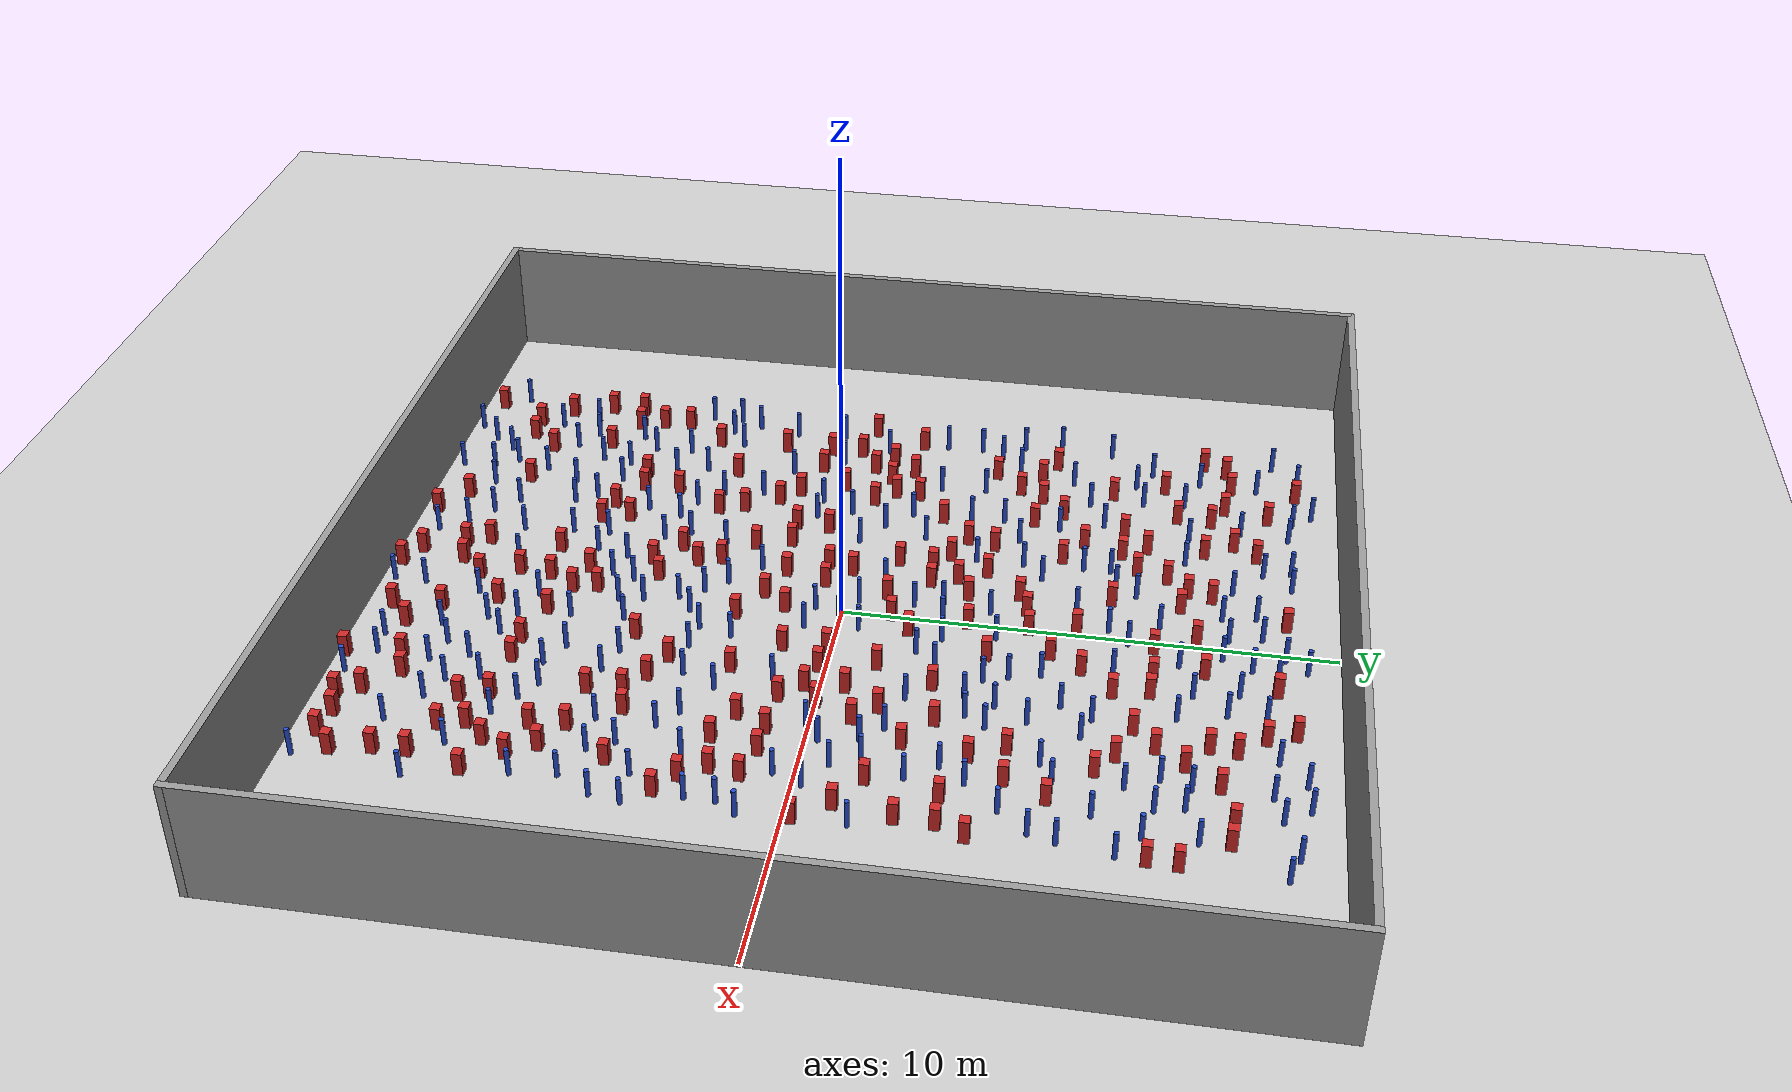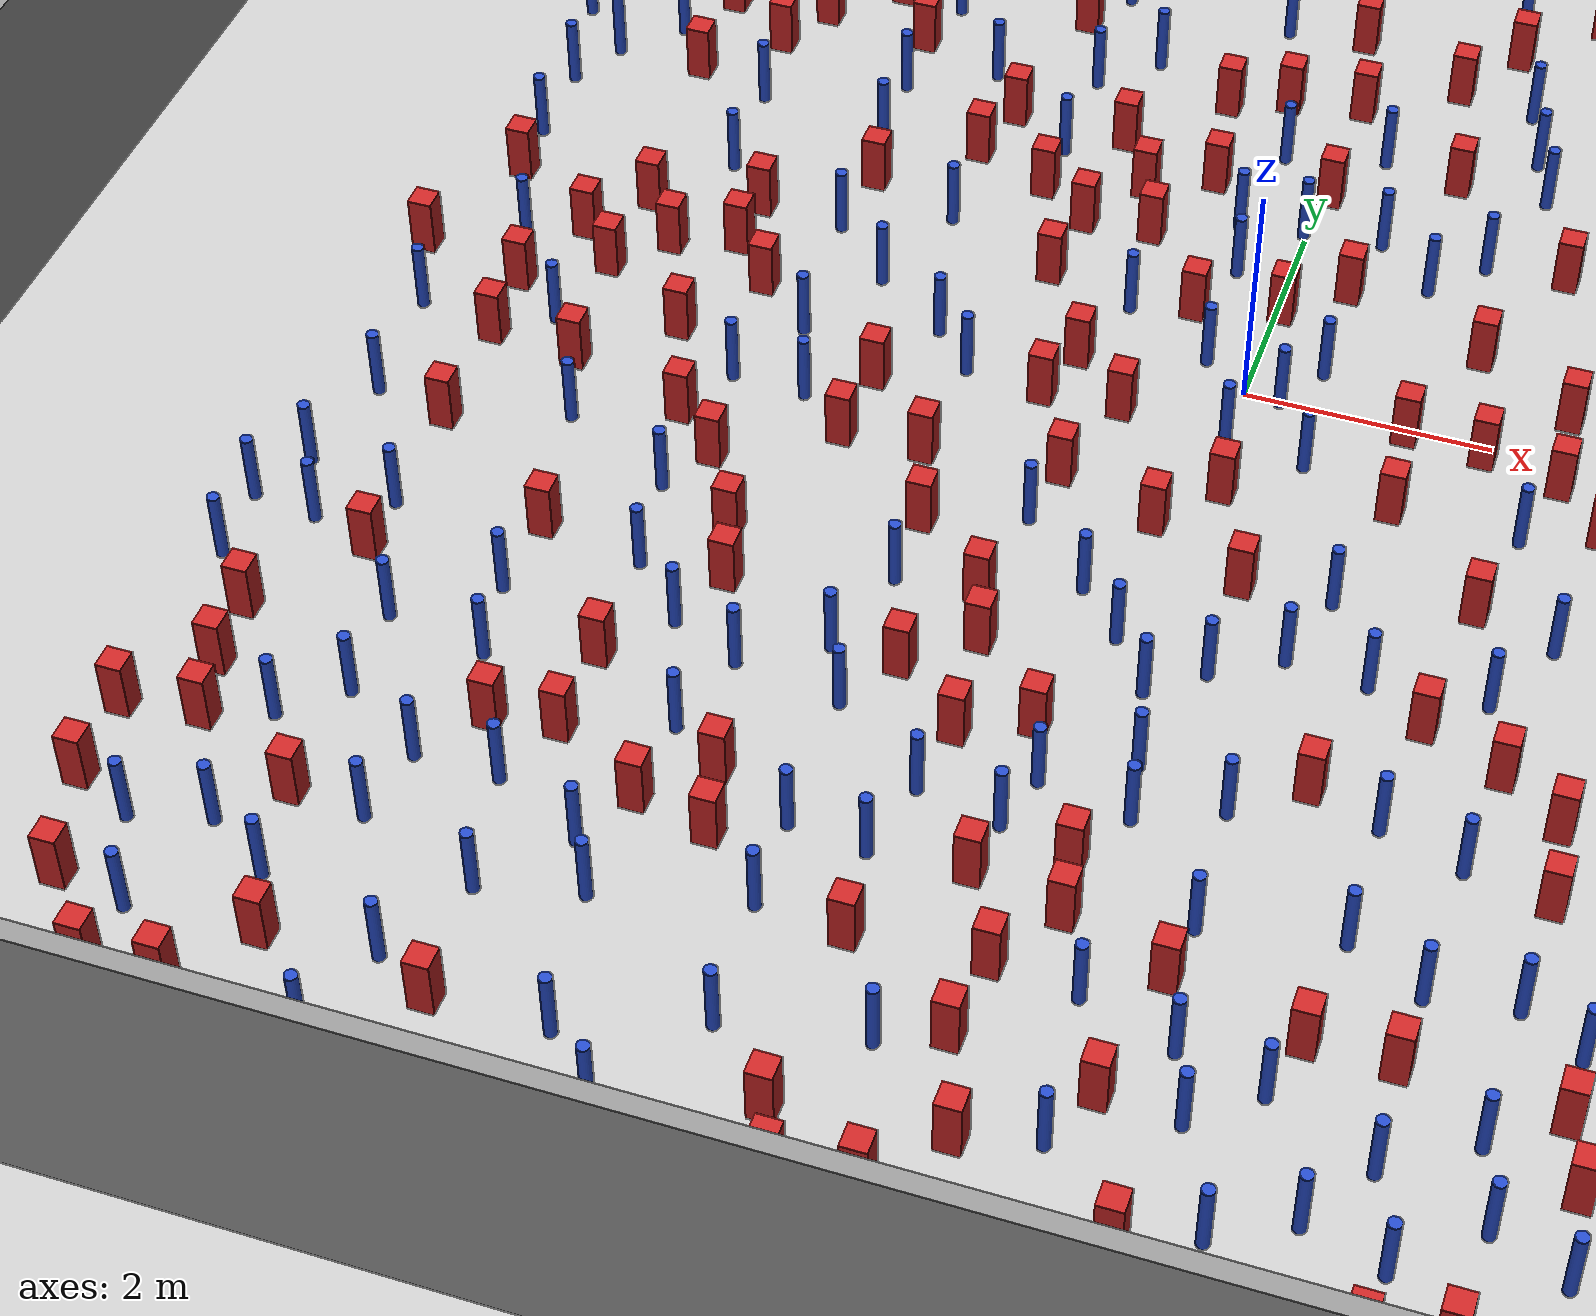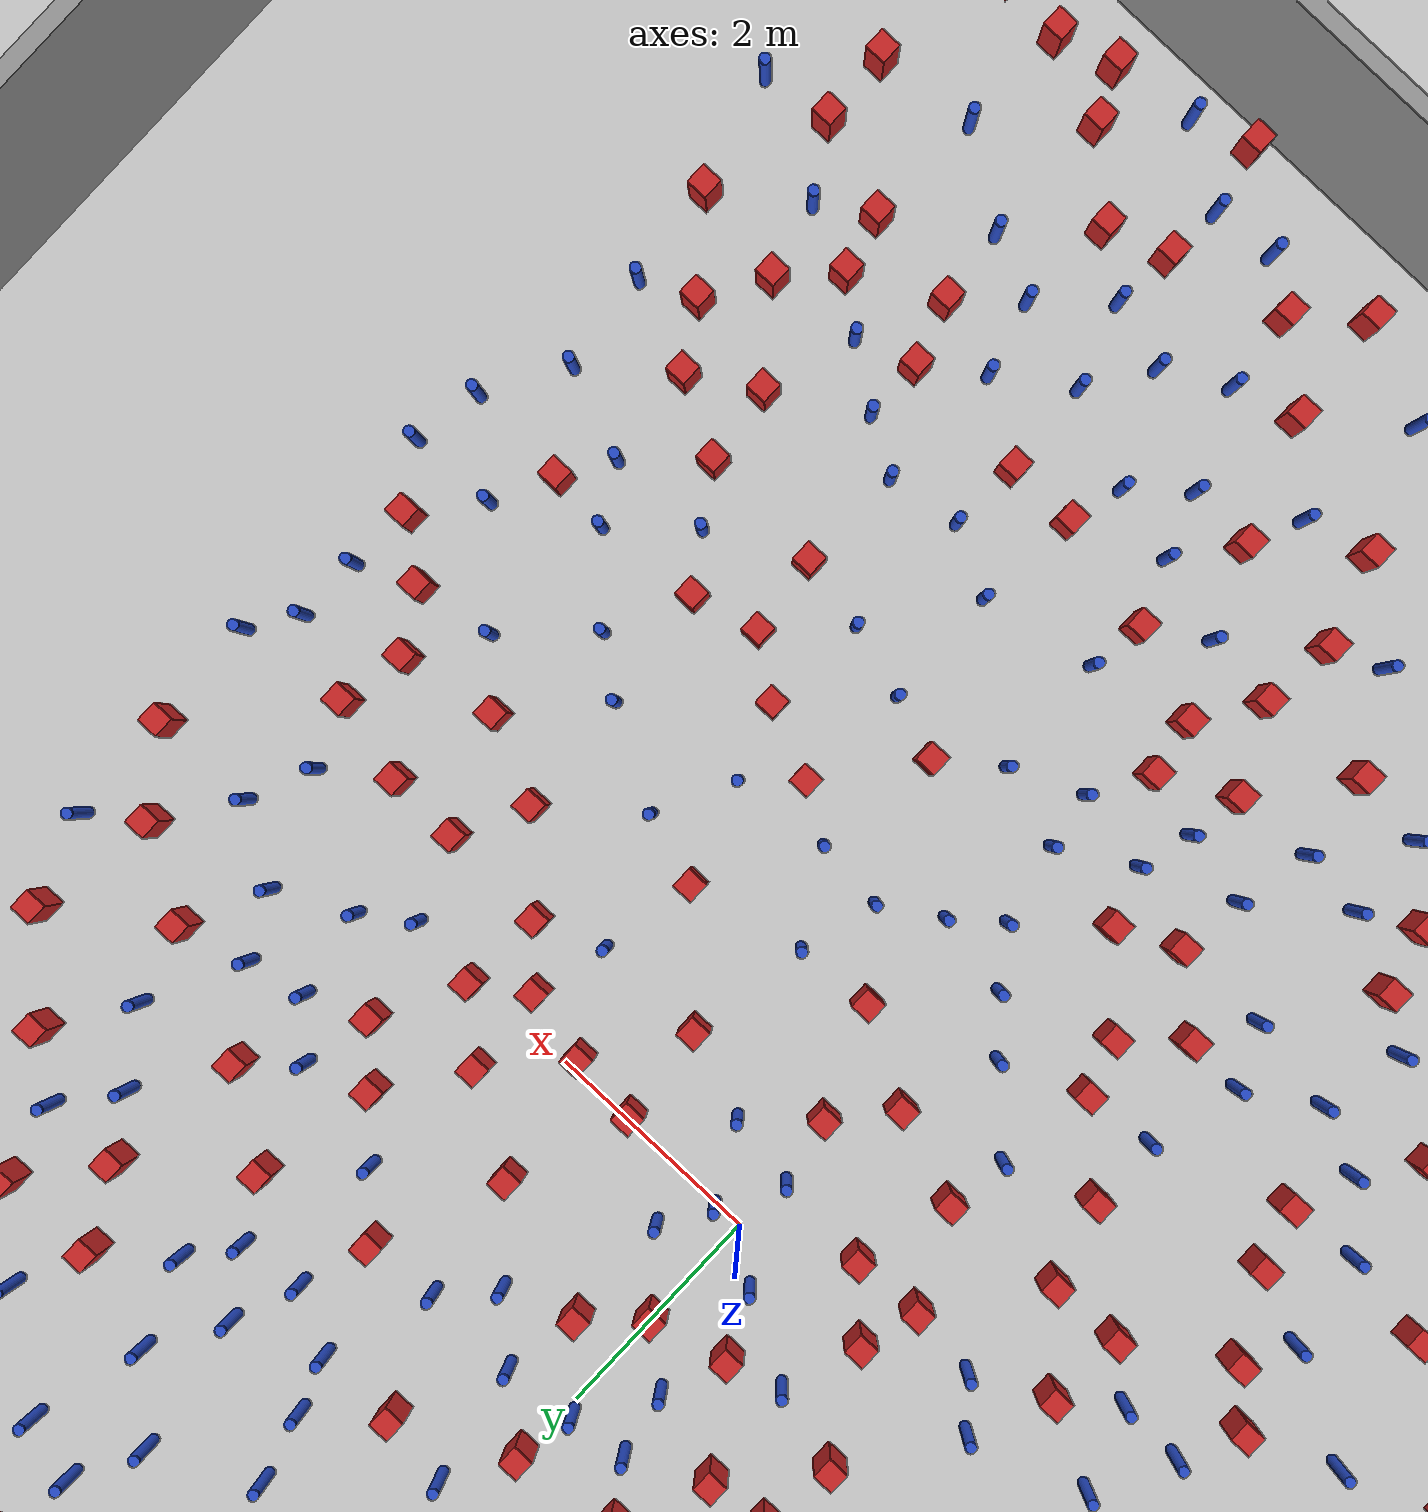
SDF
<sdf version="1.6">
 <world name="default">
  <light name="sun" type="directional">
   <pose>0 0 1000 0 -0 0</pose>
   <diffuse>0.8 0.8 0.8 1</diffuse>
   <specular>0.1 0.1 0.1 1</specular>
   <attenuation>
    <range>1000</range>
    <constant>0.9</constant>
    <linear>0.01</linear>
    <quadratic>0.001</quadratic>
   </attenuation>
   <direction>-0.5 0.5 -1</direction>
  </light>
  <model name="ground_plane">
   <static>1</static>
   <link name="link">
    <collision name="collision">
     <geometry><plane><normal>0 0 1</normal><size>100 100</size></plane></geometry>
     <surface><friction><ode><mu>100</mu><mu2>50</mu2></ode></friction></surface>
    </collision>
    <visual name="visual">
     <cast_shadows>0</cast_shadows>
     <geometry><plane><normal>0 0 1</normal><size>100 100</size></plane></geometry>
     <material>
      <ambient>1.0 1.0 1.0 1.0</ambient>
      <diffuse>0.8 0.8 0.8 1.0</diffuse>
      <specular>0.01 0.01 0.01 1.000000</specular>
     </material>
    </visual>
   </link>
  </model>
  <gravity>0 0 -9.8</gravity>
  <magnetic_field>6e-06 2.3e-05 -4.2e-05</magnetic_field>
  <atmosphere type="adiabatic"/>
  <physics name="default_physics" default="0" type="ode">
   <max_step_size>0.001</max_step_size>
   <real_time_factor>1</real_time_factor>
   <real_time_update_rate>1000</real_time_update_rate>
  </physics>
  <scene><ambient>0.4 0.4 0.4 1</ambient><background>0.7 0.7 0.7 1</background><shadows>1</shadows></scene>
  <spherical_coordinates>
   <surface_model>EARTH_WGS84</surface_model>
   <latitude_deg>0</latitude_deg>
   <longitude_deg>0</longitude_deg>
   <elevation>0</elevation>
   <heading_deg>0</heading_deg>
  </spherical_coordinates>
  <plugin name="gazebo_occupancy_map" filename="libgazebo_2Dmap_plugin.so">
   <map_resolution>0.05</map_resolution>
   <map_topic>generated_map</map_topic>
   <map_height>0.01</map_height>
   <map_size_x>50</map_size_x>
   <map_size_y>50</map_size_y>
  </plugin>
  <model name="NamedLocations">
   <static>true</static>
   <link name="DefaultStart"><pose>8.5 0 0 0 0 3.14</pose></link>
  </model>
  <model name="20x20_walls">
   <pose>0.044518 0.176112 0 0 -0 0</pose>
   <link name="Wall_1">
    <collision name="Wall_1_Collision">
     <geometry><box><size>20 0.15 2.5</size></box></geometry>
     <pose>0 0 1.25 0 -0 0</pose>
    </collision>
    <visual name="Wall_1_Visual">
     <pose>0 0 1.25 0 -0 0</pose>
     <geometry><box><size>20 0.15 2.5</size></box></geometry>
     <material>
      <script><uri>file://media/materials/scripts/gazebo.material</uri><name>Gazebo/Grey</name></script>
      <ambient>0.976471 0.992157 1 1</ambient>
     </material>
     <meta><layer>0</layer></meta>
    </visual>
    <pose>0 9.925 0 0 -0 0</pose>
   </link>
   <link name="Wall_3">
    <collision name="Wall_3_Collision">
     <geometry><box><size>20 0.15 2.5</size></box></geometry>
     <pose>0 0 1.25 0 -0 0</pose>
    </collision>
    <visual name="Wall_3_Visual">
     <pose>0 0 1.25 0 -0 0</pose>
     <geometry><box><size>20 0.15 2.5</size></box></geometry>
     <material>
      <script><uri>file://media/materials/scripts/gazebo.material</uri><name>Gazebo/Grey</name></script>
      <ambient>0.976471 0.992157 1 1</ambient>
     </material>
     <meta><layer>0</layer></meta>
    </visual>
    <pose>9.925 0 0 0 0 -1.5708</pose>
   </link>
   <link name="Wall_4">
    <collision name="Wall_4_Collision">
     <geometry><box><size>20 0.15 2.5</size></box></geometry>
     <pose>0 0 1.25 0 -0 0</pose>
    </collision>
    <visual name="Wall_4_Visual">
     <pose>0 0 1.25 0 -0 0</pose>
     <geometry><box><size>20 0.15 2.5</size></box></geometry>
     <material>
      <script><uri>file://media/materials/scripts/gazebo.material</uri><name>Gazebo/Grey</name></script>
      <ambient>0.976471 0.992157 1 1</ambient>
     </material>
     <meta><layer>0</layer></meta>
    </visual>
    <pose>0 -9.925 0 0 -0 3.14159</pose>
   </link>
   <link name="Wall_5">
    <collision name="Wall_5_Collision">
     <geometry><box><size>20 0.15 2.5</size></box></geometry>
     <pose>0 0 1.25 0 -0 0</pose>
    </collision>
    <visual name="Wall_5_Visual">
     <pose>0 0 1.25 0 -0 0</pose>
     <geometry><box><size>20 0.15 2.5</size></box></geometry>
     <material>
      <script><uri>file://media/materials/scripts/gazebo.material</uri><name>Gazebo/Grey</name></script>
      <ambient>0.976471 0.992157 1 1</ambient>
     </material>
     <meta><layer>0</layer></meta>
    </visual>
    <pose>-9.925 0 0 0 -0 1.5708</pose>
   </link>
   <static>1</static>
  </model>
  <model name="square_post_obstacle0">
   <static>true</static>
   <pose>-4.44707930667 6.60124097648 -4.36207812815e-07 3.75137919937e-06 9.77721102514e-07 2.47381364184e-05</pose>
   <link name="link">
    <pose>0 0 0.25 0 -0 0</pose>
    <inertial>
     <mass>100</mass>
     <inertia>
      <ixx>0.166667</ixx>
      <ixy>0</ixy>
      <ixz>0</ixz>
      <iyy>0.166667</iyy>
      <iyz>0</iyz>
      <izz>0.166667</izz>
     </inertia>
    </inertial>
    <collision name="collision"><geometry><box><size>.2 .2 .5</size></box></geometry></collision>
    <visual name="visual">
     <geometry><box><size>.2 .2 .5</size></box></geometry>
     <material>
      <script><name>Gazebo/Red</name><uri>file://media/materials/scripts/gazebo.material</uri></script>
     </material>
    </visual>
   </link>
  </model>
  <model name="square_post_obstacle1">
   <static>true</static>
   <pose>-6.51652858593 0.78683695775 -4.36207812815e-07 3.75137919937e-06 9.77721102514e-07 2.47381364184e-05</pose>
   <link name="link">
    <pose>0 0 0.25 0 -0 0</pose>
    <inertial>
     <mass>100</mass>
     <inertia>
      <ixx>0.166667</ixx>
      <ixy>0</ixy>
      <ixz>0</ixz>
      <iyy>0.166667</iyy>
      <iyz>0</iyz>
      <izz>0.166667</izz>
     </inertia>
    </inertial>
    <collision name="collision"><geometry><box><size>.2 .2 .5</size></box></geometry></collision>
    <visual name="visual">
     <geometry><box><size>.2 .2 .5</size></box></geometry>
     <material>
      <script><name>Gazebo/Red</name><uri>file://media/materials/scripts/gazebo.material</uri></script>
     </material>
    </visual>
   </link>
  </model>
  <model name="pole_obstacle0">
   <static>true</static>
   <pose>2.41326666451 -0.959669748231 -3.09024884793e-07 -7.19054271912e-07 -2.11315075118e-07 -1.93935509258e-07</pose>
   <link name="link">
    <pose>0 0 0.3 0 -0 0</pose>
    <inertial>
     <mass>1</mass>
     <inertia><ixx>0.145833</ixx><ixy>0</ixy><ixz>0</ixz><iyy>0.145833</iyy><iyz>0</iyz><izz>0.125</izz></inertia>
    </inertial>
    <collision name="collision">
     <geometry><cylinder><radius>0.05</radius><length>.6</length></cylinder></geometry>
    </collision>
    <visual name="visual">
     <geometry><cylinder><radius>0.05</radius><length>.6</length></cylinder></geometry>
     <material>
      <script><name>Gazebo/Blue</name><uri>file://media/materials/scripts/gazebo.material</uri></script>
     </material>
    </visual>
   </link>
  </model>
  <model name="square_post_obstacle2">
   <static>true</static>
   <pose>-2.88461139932 -1.47978508925 -4.36207812815e-07 3.75137919937e-06 9.77721102514e-07 2.47381364184e-05</pose>
   <link name="link">
    <pose>0 0 0.25 0 -0 0</pose>
    <inertial>
     <mass>100</mass>
     <inertia>
      <ixx>0.166667</ixx>
      <ixy>0</ixy>
      <ixz>0</ixz>
      <iyy>0.166667</iyy>
      <iyz>0</iyz>
      <izz>0.166667</izz>
     </inertia>
    </inertial>
    <collision name="collision"><geometry><box><size>.2 .2 .5</size></box></geometry></collision>
    <visual name="visual">
     <geometry><box><size>.2 .2 .5</size></box></geometry>
     <material>
      <script><name>Gazebo/Red</name><uri>file://media/materials/scripts/gazebo.material</uri></script>
     </material>
    </visual>
   </link>
  </model>
  <model name="pole_obstacle1">
   <static>true</static>
   <pose>5.38026649149 5.48574369236 -3.09024884793e-07 -7.19054271911e-07 -2.1131507516e-07 -1.93935509277e-07</pose>
   <link name="link">
    <pose>0 0 0.3 0 -0 0</pose>
    <inertial>
     <mass>1</mass>
     <inertia><ixx>0.145833</ixx><ixy>0</ixy><ixz>0</ixz><iyy>0.145833</iyy><iyz>0</iyz><izz>0.125</izz></inertia>
    </inertial>
    <collision name="collision">
     <geometry><cylinder><radius>0.05</radius><length>.6</length></cylinder></geometry>
    </collision>
    <visual name="visual">
     <geometry><cylinder><radius>0.05</radius><length>.6</length></cylinder></geometry>
     <material>
      <script><name>Gazebo/Blue</name><uri>file://media/materials/scripts/gazebo.material</uri></script>
     </material>
    </visual>
   </link>
  </model>
  <model name="square_post_obstacle3">
   <static>true</static>
   <pose>-6.44822498088 -5.28785836614 -4.36207812815e-07 3.75137919937e-06 9.77721102514e-07 2.47381364184e-05</pose>
   <link name="link">
    <pose>0 0 0.25 0 -0 0</pose>
    <inertial>
     <mass>100</mass>
     <inertia>
      <ixx>0.166667</ixx>
      <ixy>0</ixy>
      <ixz>0</ixz>
      <iyy>0.166667</iyy>
      <iyz>0</iyz>
      <izz>0.166667</izz>
     </inertia>
    </inertial>
    <collision name="collision"><geometry><box><size>.2 .2 .5</size></box></geometry></collision>
    <visual name="visual">
     <geometry><box><size>.2 .2 .5</size></box></geometry>
     <material>
      <script><name>Gazebo/Red</name><uri>file://media/materials/scripts/gazebo.material</uri></script>
     </material>
    </visual>
   </link>
  </model>
  <model name="pole_obstacle2">
   <static>true</static>
   <pose>-5.21666784153 -8.9613979253 -3.09024884793e-07 -7.19054271912e-07 -2.1131507513e-07 -1.93935509261e-07</pose>
   <link name="link">
    <pose>0 0 0.3 0 -0 0</pose>
    <inertial>
     <mass>1</mass>
     <inertia><ixx>0.145833</ixx><ixy>0</ixy><ixz>0</ixz><iyy>0.145833</iyy><iyz>0</iyz><izz>0.125</izz></inertia>
    </inertial>
    <collision name="collision">
     <geometry><cylinder><radius>0.05</radius><length>.6</length></cylinder></geometry>
    </collision>
    <visual name="visual">
     <geometry><cylinder><radius>0.05</radius><length>.6</length></cylinder></geometry>
     <material>
      <script><name>Gazebo/Blue</name><uri>file://media/materials/scripts/gazebo.material</uri></script>
     </material>
    </visual>
   </link>
  </model>
  <model name="pole_obstacle3">
   <static>true</static>
   <pose>1.4623566968 4.20926063526 -3.09024884793e-07 -7.19054271912e-07 -2.11315075134e-07 -1.93935509265e-07</pose>
   <link name="link">
    <pose>0 0 0.3 0 -0 0</pose>
    <inertial>
     <mass>1</mass>
     <inertia><ixx>0.145833</ixx><ixy>0</ixy><ixz>0</ixz><iyy>0.145833</iyy><iyz>0</iyz><izz>0.125</izz></inertia>
    </inertial>
    <collision name="collision">
     <geometry><cylinder><radius>0.05</radius><length>.6</length></cylinder></geometry>
    </collision>
    <visual name="visual">
     <geometry><cylinder><radius>0.05</radius><length>.6</length></cylinder></geometry>
     <material>
      <script><name>Gazebo/Blue</name><uri>file://media/materials/scripts/gazebo.material</uri></script>
     </material>
    </visual>
   </link>
  </model>
  <model name="square_post_obstacle4">
   <static>true</static>
   <pose>1.31986433456 -0.0795674390711 -4.36207812815e-07 3.75137919937e-06 9.77721102514e-07 2.47381364184e-05</pose>
   <link name="link">
    <pose>0 0 0.25 0 -0 0</pose>
    <inertial>
     <mass>100</mass>
     <inertia>
      <ixx>0.166667</ixx>
      <ixy>0</ixy>
      <ixz>0</ixz>
      <iyy>0.166667</iyy>
      <iyz>0</iyz>
      <izz>0.166667</izz>
     </inertia>
    </inertial>
    <collision name="collision"><geometry><box><size>.2 .2 .5</size></box></geometry></collision>
    <visual name="visual">
     <geometry><box><size>.2 .2 .5</size></box></geometry>
     <material>
      <script><name>Gazebo/Red</name><uri>file://media/materials/scripts/gazebo.material</uri></script>
     </material>
    </visual>
   </link>
  </model>
  <model name="square_post_obstacle5">
   <static>true</static>
   <pose>-2.57139538991 -5.11353573605 -4.36207812815e-07 3.75137919937e-06 9.77721102514e-07 2.47381364184e-05</pose>
   <link name="link">
    <pose>0 0 0.25 0 -0 0</pose>
    <inertial>
     <mass>100</mass>
     <inertia>
      <ixx>0.166667</ixx>
      <ixy>0</ixy>
      <ixz>0</ixz>
      <iyy>0.166667</iyy>
      <iyz>0</iyz>
      <izz>0.166667</izz>
     </inertia>
    </inertial>
    <collision name="collision"><geometry><box><size>.2 .2 .5</size></box></geometry></collision>
    <visual name="visual">
     <geometry><box><size>.2 .2 .5</size></box></geometry>
     <material>
      <script><name>Gazebo/Red</name><uri>file://media/materials/scripts/gazebo.material</uri></script>
     </material>
    </visual>
   </link>
  </model>
  <model name="square_post_obstacle6">
   <static>true</static>
   <pose>-2.84316023539 -0.767534176309 -4.36207812815e-07 3.75137919937e-06 9.77721102514e-07 2.47381364184e-05</pose>
   <link name="link">
    <pose>0 0 0.25 0 -0 0</pose>
    <inertial>
     <mass>100</mass>
     <inertia>
      <ixx>0.166667</ixx>
      <ixy>0</ixy>
      <ixz>0</ixz>
      <iyy>0.166667</iyy>
      <iyz>0</iyz>
      <izz>0.166667</izz>
     </inertia>
    </inertial>
    <collision name="collision"><geometry><box><size>.2 .2 .5</size></box></geometry></collision>
    <visual name="visual">
     <geometry><box><size>.2 .2 .5</size></box></geometry>
     <material>
      <script><name>Gazebo/Red</name><uri>file://media/materials/scripts/gazebo.material</uri></script>
     </material>
    </visual>
   </link>
  </model>
  <model name="pole_obstacle4">
   <static>true</static>
   <pose>-2.6535177861 8.46014323631 -3.09024884848e-07 -7.19054271902e-07 -2.11315075199e-07 -1.93935509286e-07</pose>
   <link name="link">
    <pose>0 0 0.3 0 -0 0</pose>
    <inertial>
     <mass>1</mass>
     <inertia><ixx>0.145833</ixx><ixy>0</ixy><ixz>0</ixz><iyy>0.145833</iyy><iyz>0</iyz><izz>0.125</izz></inertia>
    </inertial>
    <collision name="collision">
     <geometry><cylinder><radius>0.05</radius><length>.6</length></cylinder></geometry>
    </collision>
    <visual name="visual">
     <geometry><cylinder><radius>0.05</radius><length>.6</length></cylinder></geometry>
     <material>
      <script><name>Gazebo/Blue</name><uri>file://media/materials/scripts/gazebo.material</uri></script>
     </material>
    </visual>
   </link>
  </model>
  <model name="pole_obstacle5">
   <static>true</static>
   <pose>-1.49414931302 -9.09169557917 -3.09024884793e-07 -7.19054271912e-07 -2.1131507515e-07 -1.93935509273e-07</pose>
   <link name="link">
    <pose>0 0 0.3 0 -0 0</pose>
    <inertial>
     <mass>1</mass>
     <inertia><ixx>0.145833</ixx><ixy>0</ixy><ixz>0</ixz><iyy>0.145833</iyy><iyz>0</iyz><izz>0.125</izz></inertia>
    </inertial>
    <collision name="collision">
     <geometry><cylinder><radius>0.05</radius><length>.6</length></cylinder></geometry>
    </collision>
    <visual name="visual">
     <geometry><cylinder><radius>0.05</radius><length>.6</length></cylinder></geometry>
     <material>
      <script><name>Gazebo/Blue</name><uri>file://media/materials/scripts/gazebo.material</uri></script>
     </material>
    </visual>
   </link>
  </model>
  <model name="square_post_obstacle7">
   <static>true</static>
   <pose>5.20359295091 -5.96778097333 -4.36207812815e-07 3.75137919937e-06 9.77721102514e-07 2.47381364184e-05</pose>
   <link name="link">
    <pose>0 0 0.25 0 -0 0</pose>
    <inertial>
     <mass>100</mass>
     <inertia>
      <ixx>0.166667</ixx>
      <ixy>0</ixy>
      <ixz>0</ixz>
      <iyy>0.166667</iyy>
      <iyz>0</iyz>
      <izz>0.166667</izz>
     </inertia>
    </inertial>
    <collision name="collision"><geometry><box><size>.2 .2 .5</size></box></geometry></collision>
    <visual name="visual">
     <geometry><box><size>.2 .2 .5</size></box></geometry>
     <material>
      <script><name>Gazebo/Red</name><uri>file://media/materials/scripts/gazebo.material</uri></script>
     </material>
    </visual>
   </link>
  </model>
  <model name="square_post_obstacle8">
   <static>true</static>
   <pose>-4.70309070849 -3.17879150348 -4.36207812815e-07 3.75137919937e-06 9.77721102514e-07 2.47381364184e-05</pose>
   <link name="link">
    <pose>0 0 0.25 0 -0 0</pose>
    <inertial>
     <mass>100</mass>
     <inertia>
      <ixx>0.166667</ixx>
      <ixy>0</ixy>
      <ixz>0</ixz>
      <iyy>0.166667</iyy>
      <iyz>0</iyz>
      <izz>0.166667</izz>
     </inertia>
    </inertial>
    <collision name="collision"><geometry><box><size>.2 .2 .5</size></box></geometry></collision>
    <visual name="visual">
     <geometry><box><size>.2 .2 .5</size></box></geometry>
     <material>
      <script><name>Gazebo/Red</name><uri>file://media/materials/scripts/gazebo.material</uri></script>
     </material>
    </visual>
   </link>
  </model>
  <model name="pole_obstacle6">
   <static>true</static>
   <pose>2.60039260077 1.69104292245 -3.09024884793e-07 -7.19054271912e-07 -2.11315075122e-07 -1.93935509259e-07</pose>
   <link name="link">
    <pose>0 0 0.3 0 -0 0</pose>
    <inertial>
     <mass>1</mass>
     <inertia><ixx>0.145833</ixx><ixy>0</ixy><ixz>0</ixz><iyy>0.145833</iyy><iyz>0</iyz><izz>0.125</izz></inertia>
    </inertial>
    <collision name="collision">
     <geometry><cylinder><radius>0.05</radius><length>.6</length></cylinder></geometry>
    </collision>
    <visual name="visual">
     <geometry><cylinder><radius>0.05</radius><length>.6</length></cylinder></geometry>
     <material>
      <script><name>Gazebo/Blue</name><uri>file://media/materials/scripts/gazebo.material</uri></script>
     </material>
    </visual>
   </link>
  </model>
  <model name="pole_obstacle7">
   <static>true</static>
   <pose>-3.71285936024 0.927176487157 -3.09024884793e-07 -7.19054271912e-07 -2.11315075162e-07 -1.93935509281e-07</pose>
   <link name="link">
    <pose>0 0 0.3 0 -0 0</pose>
    <inertial>
     <mass>1</mass>
     <inertia><ixx>0.145833</ixx><ixy>0</ixy><ixz>0</ixz><iyy>0.145833</iyy><iyz>0</iyz><izz>0.125</izz></inertia>
    </inertial>
    <collision name="collision">
     <geometry><cylinder><radius>0.05</radius><length>.6</length></cylinder></geometry>
    </collision>
    <visual name="visual">
     <geometry><cylinder><radius>0.05</radius><length>.6</length></cylinder></geometry>
     <material>
      <script><name>Gazebo/Blue</name><uri>file://media/materials/scripts/gazebo.material</uri></script>
     </material>
    </visual>
   </link>
  </model>
  <model name="square_post_obstacle9">
   <static>true</static>
   <pose>-1.23599823708 1.6640314914 -4.36207812815e-07 3.75137919937e-06 9.77721102514e-07 2.47381364184e-05</pose>
   <link name="link">
    <pose>0 0 0.25 0 -0 0</pose>
    <inertial>
     <mass>100</mass>
     <inertia>
      <ixx>0.166667</ixx>
      <ixy>0</ixy>
      <ixz>0</ixz>
      <iyy>0.166667</iyy>
      <iyz>0</iyz>
      <izz>0.166667</izz>
     </inertia>
    </inertial>
    <collision name="collision"><geometry><box><size>.2 .2 .5</size></box></geometry></collision>
    <visual name="visual">
     <geometry><box><size>.2 .2 .5</size></box></geometry>
     <material>
      <script><name>Gazebo/Red</name><uri>file://media/materials/scripts/gazebo.material</uri></script>
     </material>
    </visual>
   </link>
  </model>
  <model name="square_post_obstacle10">
   <static>true</static>
   <pose>6.35777453444 3.31523075422 -4.36207812815e-07 3.75137919937e-06 9.77721102514e-07 2.47381364184e-05</pose>
   <link name="link">
    <pose>0 0 0.25 0 -0 0</pose>
    <inertial>
     <mass>100</mass>
     <inertia>
      <ixx>0.166667</ixx>
      <ixy>0</ixy>
      <ixz>0</ixz>
      <iyy>0.166667</iyy>
      <iyz>0</iyz>
      <izz>0.166667</izz>
     </inertia>
    </inertial>
    <collision name="collision"><geometry><box><size>.2 .2 .5</size></box></geometry></collision>
    <visual name="visual">
     <geometry><box><size>.2 .2 .5</size></box></geometry>
     <material>
      <script><name>Gazebo/Red</name><uri>file://media/materials/scripts/gazebo.material</uri></script>
     </material>
    </visual>
   </link>
  </model>
  <model name="square_post_obstacle11">
   <static>true</static>
   <pose>0.119357444727 -1.15972905448 -4.36207812815e-07 3.75137919937e-06 9.77721102514e-07 2.47381364184e-05</pose>
   <link name="link">
    <pose>0 0 0.25 0 -0 0</pose>
    <inertial>
     <mass>100</mass>
     <inertia>
      <ixx>0.166667</ixx>
      <ixy>0</ixy>
      <ixz>0</ixz>
      <iyy>0.166667</iyy>
      <iyz>0</iyz>
      <izz>0.166667</izz>
     </inertia>
    </inertial>
    <collision name="collision"><geometry><box><size>.2 .2 .5</size></box></geometry></collision>
    <visual name="visual">
     <geometry><box><size>.2 .2 .5</size></box></geometry>
     <material>
      <script><name>Gazebo/Red</name><uri>file://media/materials/scripts/gazebo.material</uri></script>
     </material>
    </visual>
   </link>
  </model>
  <model name="square_post_obstacle12">
   <static>true</static>
   <pose>-6.17374142803 3.86425965815 -4.36207812815e-07 3.75137919937e-06 9.77721102514e-07 2.47381364184e-05</pose>
   <link name="link">
    <pose>0 0 0.25 0 -0 0</pose>
    <inertial>
     <mass>100</mass>
     <inertia>
      <ixx>0.166667</ixx>
      <ixy>0</ixy>
      <ixz>0</ixz>
      <iyy>0.166667</iyy>
      <iyz>0</iyz>
      <izz>0.166667</izz>
     </inertia>
    </inertial>
    <collision name="collision"><geometry><box><size>.2 .2 .5</size></box></geometry></collision>
    <visual name="visual">
     <geometry><box><size>.2 .2 .5</size></box></geometry>
     <material>
      <script><name>Gazebo/Red</name><uri>file://media/materials/scripts/gazebo.material</uri></script>
     </material>
    </visual>
   </link>
  </model>
  <model name="square_post_obstacle13">
   <static>true</static>
   <pose>2.54253266543 9.15945608791 -4.36207812815e-07 3.75137919937e-06 9.77721102514e-07 2.47381364184e-05</pose>
   <link name="link">
    <pose>0 0 0.25 0 -0 0</pose>
    <inertial>
     <mass>100</mass>
     <inertia>
      <ixx>0.166667</ixx>
      <ixy>0</ixy>
      <ixz>0</ixz>
      <iyy>0.166667</iyy>
      <iyz>0</iyz>
      <izz>0.166667</izz>
     </inertia>
    </inertial>
    <collision name="collision"><geometry><box><size>.2 .2 .5</size></box></geometry></collision>
    <visual name="visual">
     <geometry><box><size>.2 .2 .5</size></box></geometry>
     <material>
      <script><name>Gazebo/Red</name><uri>file://media/materials/scripts/gazebo.material</uri></script>
     </material>
    </visual>
   </link>
  </model>
  <model name="pole_obstacle8">
   <static>true</static>
   <pose>2.66010328651 5.29040970579 -3.09024884793e-07 -7.19054271912e-07 -2.11315075134e-07 -1.93935509266e-07</pose>
   <link name="link">
    <pose>0 0 0.3 0 -0 0</pose>
    <inertial>
     <mass>1</mass>
     <inertia><ixx>0.145833</ixx><ixy>0</ixy><ixz>0</ixz><iyy>0.145833</iyy><iyz>0</iyz><izz>0.125</izz></inertia>
    </inertial>
    <collision name="collision">
     <geometry><cylinder><radius>0.05</radius><length>.6</length></cylinder></geometry>
    </collision>
    <visual name="visual">
     <geometry><cylinder><radius>0.05</radius><length>.6</length></cylinder></geometry>
     <material>
      <script><name>Gazebo/Blue</name><uri>file://media/materials/scripts/gazebo.material</uri></script>
     </material>
    </visual>
   </link>
  </model>
  <model name="square_post_obstacle14">
   <static>true</static>
   <pose>2.76166165576 8.59688035177 -4.36207812815e-07 3.75137919937e-06 9.77721102514e-07 2.47381364184e-05</pose>
   <link name="link">
    <pose>0 0 0.25 0 -0 0</pose>
    <inertial>
     <mass>100</mass>
     <inertia>
      <ixx>0.166667</ixx>
      <ixy>0</ixy>
      <ixz>0</ixz>
      <iyy>0.166667</iyy>
      <iyz>0</iyz>
      <izz>0.166667</izz>
     </inertia>
    </inertial>
    <collision name="collision"><geometry><box><size>.2 .2 .5</size></box></geometry></collision>
    <visual name="visual">
     <geometry><box><size>.2 .2 .5</size></box></geometry>
     <material>
      <script><name>Gazebo/Red</name><uri>file://media/materials/scripts/gazebo.material</uri></script>
     </material>
    </visual>
   </link>
  </model>
  <model name="square_post_obstacle15">
   <static>true</static>
   <pose>3.97810140342 -0.776497119024 -4.36207812815e-07 3.75137919937e-06 9.77721102514e-07 2.47381364184e-05</pose>
   <link name="link">
    <pose>0 0 0.25 0 -0 0</pose>
    <inertial>
     <mass>100</mass>
     <inertia>
      <ixx>0.166667</ixx>
      <ixy>0</ixy>
      <ixz>0</ixz>
      <iyy>0.166667</iyy>
      <iyz>0</iyz>
      <izz>0.166667</izz>
     </inertia>
    </inertial>
    <collision name="collision"><geometry><box><size>.2 .2 .5</size></box></geometry></collision>
    <visual name="visual">
     <geometry><box><size>.2 .2 .5</size></box></geometry>
     <material>
      <script><name>Gazebo/Red</name><uri>file://media/materials/scripts/gazebo.material</uri></script>
     </material>
    </visual>
   </link>
  </model>
  <model name="square_post_obstacle16">
   <static>true</static>
   <pose>-1.88368987342 0.911929854532 -4.36207812815e-07 3.75137919937e-06 9.77721102514e-07 2.47381364184e-05</pose>
   <link name="link">
    <pose>0 0 0.25 0 -0 0</pose>
    <inertial>
     <mass>100</mass>
     <inertia>
      <ixx>0.166667</ixx>
      <ixy>0</ixy>
      <ixz>0</ixz>
      <iyy>0.166667</iyy>
      <iyz>0</iyz>
      <izz>0.166667</izz>
     </inertia>
    </inertial>
    <collision name="collision"><geometry><box><size>.2 .2 .5</size></box></geometry></collision>
    <visual name="visual">
     <geometry><box><size>.2 .2 .5</size></box></geometry>
     <material>
      <script><name>Gazebo/Red</name><uri>file://media/materials/scripts/gazebo.material</uri></script>
     </material>
    </visual>
   </link>
  </model>
  <model name="pole_obstacle9">
   <static>true</static>
   <pose>2.89782994441 -2.0281531749 -3.09024884793e-07 -7.19054271912e-07 -2.11315075127e-07 -1.93935509262e-07</pose>
   <link name="link">
    <pose>0 0 0.3 0 -0 0</pose>
    <inertial>
     <mass>1</mass>
     <inertia><ixx>0.145833</ixx><ixy>0</ixy><ixz>0</ixz><iyy>0.145833</iyy><iyz>0</iyz><izz>0.125</izz></inertia>
    </inertial>
    <collision name="collision">
     <geometry><cylinder><radius>0.05</radius><length>.6</length></cylinder></geometry>
    </collision>
    <visual name="visual">
     <geometry><cylinder><radius>0.05</radius><length>.6</length></cylinder></geometry>
     <material>
      <script><name>Gazebo/Blue</name><uri>file://media/materials/scripts/gazebo.material</uri></script>
     </material>
    </visual>
   </link>
  </model>
  <model name="square_post_obstacle17">
   <static>true</static>
   <pose>3.66579948599 -1.40427711125 -4.36207812815e-07 3.75137919937e-06 9.77721102514e-07 2.47381364184e-05</pose>
   <link name="link">
    <pose>0 0 0.25 0 -0 0</pose>
    <inertial>
     <mass>100</mass>
     <inertia>
      <ixx>0.166667</ixx>
      <ixy>0</ixy>
      <ixz>0</ixz>
      <iyy>0.166667</iyy>
      <iyz>0</iyz>
      <izz>0.166667</izz>
     </inertia>
    </inertial>
    <collision name="collision"><geometry><box><size>.2 .2 .5</size></box></geometry></collision>
    <visual name="visual">
     <geometry><box><size>.2 .2 .5</size></box></geometry>
     <material>
      <script><name>Gazebo/Red</name><uri>file://media/materials/scripts/gazebo.material</uri></script>
     </material>
    </visual>
   </link>
  </model>
  <model name="square_post_obstacle18">
   <static>true</static>
   <pose>2.58968893634 -0.286422892999 -4.36207812815e-07 3.75137919937e-06 9.77721102514e-07 2.47381364184e-05</pose>
   <link name="link">
    <pose>0 0 0.25 0 -0 0</pose>
    <inertial>
     <mass>100</mass>
     <inertia>
      <ixx>0.166667</ixx>
      <ixy>0</ixy>
      <ixz>0</ixz>
      <iyy>0.166667</iyy>
      <iyz>0</iyz>
      <izz>0.166667</izz>
     </inertia>
    </inertial>
    <collision name="collision"><geometry><box><size>.2 .2 .5</size></box></geometry></collision>
    <visual name="visual">
     <geometry><box><size>.2 .2 .5</size></box></geometry>
     <material>
      <script><name>Gazebo/Red</name><uri>file://media/materials/scripts/gazebo.material</uri></script>
     </material>
    </visual>
   </link>
  </model>
  <model name="pole_obstacle10">
   <static>true</static>
   <pose>2.30417689854 -8.93807566385 -3.09024884848e-07 -7.19054271902e-07 -2.11315075199e-07 -1.93935509286e-07</pose>
   <link name="link">
    <pose>0 0 0.3 0 -0 0</pose>
    <inertial>
     <mass>1</mass>
     <inertia><ixx>0.145833</ixx><ixy>0</ixy><ixz>0</ixz><iyy>0.145833</iyy><iyz>0</iyz><izz>0.125</izz></inertia>
    </inertial>
    <collision name="collision">
     <geometry><cylinder><radius>0.05</radius><length>.6</length></cylinder></geometry>
    </collision>
    <visual name="visual">
     <geometry><cylinder><radius>0.05</radius><length>.6</length></cylinder></geometry>
     <material>
      <script><name>Gazebo/Blue</name><uri>file://media/materials/scripts/gazebo.material</uri></script>
     </material>
    </visual>
   </link>
  </model>
  <model name="square_post_obstacle19">
   <static>true</static>
   <pose>3.23109717422 2.34629957783 -4.36207812815e-07 3.75137919937e-06 9.77721102514e-07 2.47381364184e-05</pose>
   <link name="link">
    <pose>0 0 0.25 0 -0 0</pose>
    <inertial>
     <mass>100</mass>
     <inertia>
      <ixx>0.166667</ixx>
      <ixy>0</ixy>
      <ixz>0</ixz>
      <iyy>0.166667</iyy>
      <iyz>0</iyz>
      <izz>0.166667</izz>
     </inertia>
    </inertial>
    <collision name="collision"><geometry><box><size>.2 .2 .5</size></box></geometry></collision>
    <visual name="visual">
     <geometry><box><size>.2 .2 .5</size></box></geometry>
     <material>
      <script><name>Gazebo/Red</name><uri>file://media/materials/scripts/gazebo.material</uri></script>
     </material>
    </visual>
   </link>
  </model>
  <model name="pole_obstacle11">
   <static>true</static>
   <pose>0.478394050941 -6.26336523896 -3.09024884793e-07 -7.19054271912e-07 -2.11315075128e-07 -1.9393550926e-07</pose>
   <link name="link">
    <pose>0 0 0.3 0 -0 0</pose>
    <inertial>
     <mass>1</mass>
     <inertia><ixx>0.145833</ixx><ixy>0</ixy><ixz>0</ixz><iyy>0.145833</iyy><iyz>0</iyz><izz>0.125</izz></inertia>
    </inertial>
    <collision name="collision">
     <geometry><cylinder><radius>0.05</radius><length>.6</length></cylinder></geometry>
    </collision>
    <visual name="visual">
     <geometry><cylinder><radius>0.05</radius><length>.6</length></cylinder></geometry>
     <material>
      <script><name>Gazebo/Blue</name><uri>file://media/materials/scripts/gazebo.material</uri></script>
     </material>
    </visual>
   </link>
  </model>
  <model name="square_post_obstacle20">
   <static>true</static>
   <pose>4.63659688607 -0.795210823432 -4.36207812815e-07 3.75137919937e-06 9.77721102514e-07 2.47381364184e-05</pose>
   <link name="link">
    <pose>0 0 0.25 0 -0 0</pose>
    <inertial>
     <mass>100</mass>
     <inertia>
      <ixx>0.166667</ixx>
      <ixy>0</ixy>
      <ixz>0</ixz>
      <iyy>0.166667</iyy>
      <iyz>0</iyz>
      <izz>0.166667</izz>
     </inertia>
    </inertial>
    <collision name="collision"><geometry><box><size>.2 .2 .5</size></box></geometry></collision>
    <visual name="visual">
     <geometry><box><size>.2 .2 .5</size></box></geometry>
     <material>
      <script><name>Gazebo/Red</name><uri>file://media/materials/scripts/gazebo.material</uri></script>
     </material>
    </visual>
   </link>
  </model>
  <model name="pole_obstacle12">
   <static>true</static>
   <pose>-5.93365733735 7.03019296914 -3.09024884793e-07 -7.19054271911e-07 -2.1131507516e-07 -1.93935509277e-07</pose>
   <link name="link">
    <pose>0 0 0.3 0 -0 0</pose>
    <inertial>
     <mass>1</mass>
     <inertia><ixx>0.145833</ixx><ixy>0</ixy><ixz>0</ixz><iyy>0.145833</iyy><iyz>0</iyz><izz>0.125</izz></inertia>
    </inertial>
    <collision name="collision">
     <geometry><cylinder><radius>0.05</radius><length>.6</length></cylinder></geometry>
    </collision>
    <visual name="visual">
     <geometry><cylinder><radius>0.05</radius><length>.6</length></cylinder></geometry>
     <material>
      <script><name>Gazebo/Blue</name><uri>file://media/materials/scripts/gazebo.material</uri></script>
     </material>
    </visual>
   </link>
  </model>
  <model name="square_post_obstacle21">
   <static>true</static>
   <pose>-3.63298602497 1.60475651946 -4.36207812815e-07 3.75137919937e-06 9.77721102514e-07 2.47381364184e-05</pose>
   <link name="link">
    <pose>0 0 0.25 0 -0 0</pose>
    <inertial>
     <mass>100</mass>
     <inertia>
      <ixx>0.166667</ixx>
      <ixy>0</ixy>
      <ixz>0</ixz>
      <iyy>0.166667</iyy>
      <iyz>0</iyz>
      <izz>0.166667</izz>
     </inertia>
    </inertial>
    <collision name="collision"><geometry><box><size>.2 .2 .5</size></box></geometry></collision>
    <visual name="visual">
     <geometry><box><size>.2 .2 .5</size></box></geometry>
     <material>
      <script><name>Gazebo/Red</name><uri>file://media/materials/scripts/gazebo.material</uri></script>
     </material>
    </visual>
   </link>
  </model>
  <model name="pole_obstacle13">
   <static>true</static>
   <pose>3.82998735341 -5.70305099585 -3.09024884793e-07 -7.19054271912e-07 -2.11315075134e-07 -1.93935509266e-07</pose>
   <link name="link">
    <pose>0 0 0.3 0 -0 0</pose>
    <inertial>
     <mass>1</mass>
     <inertia><ixx>0.145833</ixx><ixy>0</ixy><ixz>0</ixz><iyy>0.145833</iyy><iyz>0</iyz><izz>0.125</izz></inertia>
    </inertial>
    <collision name="collision">
     <geometry><cylinder><radius>0.05</radius><length>.6</length></cylinder></geometry>
    </collision>
    <visual name="visual">
     <geometry><cylinder><radius>0.05</radius><length>.6</length></cylinder></geometry>
     <material>
      <script><name>Gazebo/Blue</name><uri>file://media/materials/scripts/gazebo.material</uri></script>
     </material>
    </visual>
   </link>
  </model>
  <model name="square_post_obstacle22">
   <static>true</static>
   <pose>-2.14941318314 6.49315178788 -4.36207812815e-07 3.75137919937e-06 9.77721102514e-07 2.47381364184e-05</pose>
   <link name="link">
    <pose>0 0 0.25 0 -0 0</pose>
    <inertial>
     <mass>100</mass>
     <inertia>
      <ixx>0.166667</ixx>
      <ixy>0</ixy>
      <ixz>0</ixz>
      <iyy>0.166667</iyy>
      <iyz>0</iyz>
      <izz>0.166667</izz>
     </inertia>
    </inertial>
    <collision name="collision"><geometry><box><size>.2 .2 .5</size></box></geometry></collision>
    <visual name="visual">
     <geometry><box><size>.2 .2 .5</size></box></geometry>
     <material>
      <script><name>Gazebo/Red</name><uri>file://media/materials/scripts/gazebo.material</uri></script>
     </material>
    </visual>
   </link>
  </model>
  <model name="pole_obstacle14">
   <static>true</static>
   <pose>-0.220990663885 -2.92451951787 -3.09024884848e-07 -7.19054271902e-07 -2.11315075205e-07 -1.93935509288e-07</pose>
   <link name="link">
    <pose>0 0 0.3 0 -0 0</pose>
    <inertial>
     <mass>1</mass>
     <inertia><ixx>0.145833</ixx><ixy>0</ixy><ixz>0</ixz><iyy>0.145833</iyy><iyz>0</iyz><izz>0.125</izz></inertia>
    </inertial>
    <collision name="collision">
     <geometry><cylinder><radius>0.05</radius><length>.6</length></cylinder></geometry>
    </collision>
    <visual name="visual">
     <geometry><cylinder><radius>0.05</radius><length>.6</length></cylinder></geometry>
     <material>
      <script><name>Gazebo/Blue</name><uri>file://media/materials/scripts/gazebo.material</uri></script>
     </material>
    </visual>
   </link>
  </model>
  <model name="pole_obstacle15">
   <static>true</static>
   <pose>-4.91971607165 2.37123961968 -3.09024884793e-07 -7.19054271912e-07 -2.11315075144e-07 -1.93935509269e-07</pose>
   <link name="link">
    <pose>0 0 0.3 0 -0 0</pose>
    <inertial>
     <mass>1</mass>
     <inertia><ixx>0.145833</ixx><ixy>0</ixy><ixz>0</ixz><iyy>0.145833</iyy><iyz>0</iyz><izz>0.125</izz></inertia>
    </inertial>
    <collision name="collision">
     <geometry><cylinder><radius>0.05</radius><length>.6</length></cylinder></geometry>
    </collision>
    <visual name="visual">
     <geometry><cylinder><radius>0.05</radius><length>.6</length></cylinder></geometry>
     <material>
      <script><name>Gazebo/Blue</name><uri>file://media/materials/scripts/gazebo.material</uri></script>
     </material>
    </visual>
   </link>
  </model>
  <model name="pole_obstacle16">
   <static>true</static>
   <pose>-6.55094301523 -2.15541498875 -3.09024884793e-07 -7.19054271912e-07 -2.11315075144e-07 -1.93935509269e-07</pose>
   <link name="link">
    <pose>0 0 0.3 0 -0 0</pose>
    <inertial>
     <mass>1</mass>
     <inertia><ixx>0.145833</ixx><ixy>0</ixy><ixz>0</ixz><iyy>0.145833</iyy><iyz>0</iyz><izz>0.125</izz></inertia>
    </inertial>
    <collision name="collision">
     <geometry><cylinder><radius>0.05</radius><length>.6</length></cylinder></geometry>
    </collision>
    <visual name="visual">
     <geometry><cylinder><radius>0.05</radius><length>.6</length></cylinder></geometry>
     <material>
      <script><name>Gazebo/Blue</name><uri>file://media/materials/scripts/gazebo.material</uri></script>
     </material>
    </visual>
   </link>
  </model>
  <model name="square_post_obstacle23">
   <static>true</static>
   <pose>5.78915703853 -7.91855140705 -4.36207812815e-07 3.75137919937e-06 9.77721102514e-07 2.47381364184e-05</pose>
   <link name="link">
    <pose>0 0 0.25 0 -0 0</pose>
    <inertial>
     <mass>100</mass>
     <inertia>
      <ixx>0.166667</ixx>
      <ixy>0</ixy>
      <ixz>0</ixz>
      <iyy>0.166667</iyy>
      <iyz>0</iyz>
      <izz>0.166667</izz>
     </inertia>
    </inertial>
    <collision name="collision"><geometry><box><size>.2 .2 .5</size></box></geometry></collision>
    <visual name="visual">
     <geometry><box><size>.2 .2 .5</size></box></geometry>
     <material>
      <script><name>Gazebo/Red</name><uri>file://media/materials/scripts/gazebo.material</uri></script>
     </material>
    </visual>
   </link>
  </model>
  <model name="pole_obstacle17">
   <static>true</static>
   <pose>2.69220364741 -5.52727112073 -3.09024884793e-07 -7.19054271912e-07 -2.11315075134e-07 -1.93935509266e-07</pose>
   <link name="link">
    <pose>0 0 0.3 0 -0 0</pose>
    <inertial>
     <mass>1</mass>
     <inertia><ixx>0.145833</ixx><ixy>0</ixy><ixz>0</ixz><iyy>0.145833</iyy><iyz>0</iyz><izz>0.125</izz></inertia>
    </inertial>
    <collision name="collision">
     <geometry><cylinder><radius>0.05</radius><length>.6</length></cylinder></geometry>
    </collision>
    <visual name="visual">
     <geometry><cylinder><radius>0.05</radius><length>.6</length></cylinder></geometry>
     <material>
      <script><name>Gazebo/Blue</name><uri>file://media/materials/scripts/gazebo.material</uri></script>
     </material>
    </visual>
   </link>
  </model>
  <model name="square_post_obstacle24">
   <static>true</static>
   <pose>-6.68287797261 -9.22336050175 -4.36207812815e-07 3.75137919937e-06 9.77721102514e-07 2.47381364184e-05</pose>
   <link name="link">
    <pose>0 0 0.25 0 -0 0</pose>
    <inertial>
     <mass>100</mass>
     <inertia>
      <ixx>0.166667</ixx>
      <ixy>0</ixy>
      <ixz>0</ixz>
      <iyy>0.166667</iyy>
      <iyz>0</iyz>
      <izz>0.166667</izz>
     </inertia>
    </inertial>
    <collision name="collision"><geometry><box><size>.2 .2 .5</size></box></geometry></collision>
    <visual name="visual">
     <geometry><box><size>.2 .2 .5</size></box></geometry>
     <material>
      <script><name>Gazebo/Red</name><uri>file://media/materials/scripts/gazebo.material</uri></script>
     </material>
    </visual>
   </link>
  </model>
  <model name="square_post_obstacle25">
   <static>true</static>
   <pose>-0.45596552697 -8.17920783324 -4.36207812815e-07 3.75137919937e-06 9.77721102514e-07 2.47381364184e-05</pose>
   <link name="link">
    <pose>0 0 0.25 0 -0 0</pose>
    <inertial>
     <mass>100</mass>
     <inertia>
      <ixx>0.166667</ixx>
      <ixy>0</ixy>
      <ixz>0</ixz>
      <iyy>0.166667</iyy>
      <iyz>0</iyz>
      <izz>0.166667</izz>
     </inertia>
    </inertial>
    <collision name="collision"><geometry><box><size>.2 .2 .5</size></box></geometry></collision>
    <visual name="visual">
     <geometry><box><size>.2 .2 .5</size></box></geometry>
     <material>
      <script><name>Gazebo/Red</name><uri>file://media/materials/scripts/gazebo.material</uri></script>
     </material>
    </visual>
   </link>
  </model>
  <model name="square_post_obstacle26">
   <static>true</static>
   <pose>-3.80524596658 -4.31462572577 -4.36207812815e-07 3.75137919937e-06 9.77721102514e-07 2.47381364184e-05</pose>
   <link name="link">
    <pose>0 0 0.25 0 -0 0</pose>
    <inertial>
     <mass>100</mass>
     <inertia>
      <ixx>0.166667</ixx>
      <ixy>0</ixy>
      <ixz>0</ixz>
      <iyy>0.166667</iyy>
      <iyz>0</iyz>
      <izz>0.166667</izz>
     </inertia>
    </inertial>
    <collision name="collision"><geometry><box><size>.2 .2 .5</size></box></geometry></collision>
    <visual name="visual">
     <geometry><box><size>.2 .2 .5</size></box></geometry>
     <material>
      <script><name>Gazebo/Red</name><uri>file://media/materials/scripts/gazebo.material</uri></script>
     </material>
    </visual>
   </link>
  </model>
  <model name="square_post_obstacle27">
   <static>true</static>
   <pose>-0.881966383445 -0.498350756091 -4.36207812815e-07 3.75137919937e-06 9.77721102514e-07 2.47381364184e-05</pose>
   <link name="link">
    <pose>0 0 0.25 0 -0 0</pose>
    <inertial>
     <mass>100</mass>
     <inertia>
      <ixx>0.166667</ixx>
      <ixy>0</ixy>
      <ixz>0</ixz>
      <iyy>0.166667</iyy>
      <iyz>0</iyz>
      <izz>0.166667</izz>
     </inertia>
    </inertial>
    <collision name="collision"><geometry><box><size>.2 .2 .5</size></box></geometry></collision>
    <visual name="visual">
     <geometry><box><size>.2 .2 .5</size></box></geometry>
     <material>
      <script><name>Gazebo/Red</name><uri>file://media/materials/scripts/gazebo.material</uri></script>
     </material>
    </visual>
   </link>
  </model>
  <model name="pole_obstacle18">
   <static>true</static>
   <pose>4.50732417041 6.02375371996 -3.09024884793e-07 -7.19054271911e-07 -2.1131507516e-07 -1.93935509277e-07</pose>
   <link name="link">
    <pose>0 0 0.3 0 -0 0</pose>
    <inertial>
     <mass>1</mass>
     <inertia><ixx>0.145833</ixx><ixy>0</ixy><ixz>0</ixz><iyy>0.145833</iyy><iyz>0</iyz><izz>0.125</izz></inertia>
    </inertial>
    <collision name="collision">
     <geometry><cylinder><radius>0.05</radius><length>.6</length></cylinder></geometry>
    </collision>
    <visual name="visual">
     <geometry><cylinder><radius>0.05</radius><length>.6</length></cylinder></geometry>
     <material>
      <script><name>Gazebo/Blue</name><uri>file://media/materials/scripts/gazebo.material</uri></script>
     </material>
    </visual>
   </link>
  </model>
  <model name="square_post_obstacle28">
   <static>true</static>
   <pose>0.997454960169 -5.92725323505 -4.36207812815e-07 3.75137919937e-06 9.77721102514e-07 2.47381364184e-05</pose>
   <link name="link">
    <pose>0 0 0.25 0 -0 0</pose>
    <inertial>
     <mass>100</mass>
     <inertia>
      <ixx>0.166667</ixx>
      <ixy>0</ixy>
      <ixz>0</ixz>
      <iyy>0.166667</iyy>
      <iyz>0</iyz>
      <izz>0.166667</izz>
     </inertia>
    </inertial>
    <collision name="collision"><geometry><box><size>.2 .2 .5</size></box></geometry></collision>
    <visual name="visual">
     <geometry><box><size>.2 .2 .5</size></box></geometry>
     <material>
      <script><name>Gazebo/Red</name><uri>file://media/materials/scripts/gazebo.material</uri></script>
     </material>
    </visual>
   </link>
  </model>
  <model name="pole_obstacle19">
   <static>true</static>
   <pose>-2.80860477781 9.03629585932 -3.09024884848e-07 -7.19054271902e-07 -2.11315075199e-07 -1.93935509286e-07</pose>
   <link name="link">
    <pose>0 0 0.3 0 -0 0</pose>
    <inertial>
     <mass>1</mass>
     <inertia><ixx>0.145833</ixx><ixy>0</ixy><ixz>0</ixz><iyy>0.145833</iyy><iyz>0</iyz><izz>0.125</izz></inertia>
    </inertial>
    <collision name="collision">
     <geometry><cylinder><radius>0.05</radius><length>.6</length></cylinder></geometry>
    </collision>
    <visual name="visual">
     <geometry><cylinder><radius>0.05</radius><length>.6</length></cylinder></geometry>
     <material>
      <script><name>Gazebo/Blue</name><uri>file://media/materials/scripts/gazebo.material</uri></script>
     </material>
    </visual>
   </link>
  </model>
  <model name="square_post_obstacle29">
   <static>true</static>
   <pose>-4.93352778834 7.59655148144 -4.36207812815e-07 3.75137919937e-06 9.77721102514e-07 2.47381364184e-05</pose>
   <link name="link">
    <pose>0 0 0.25 0 -0 0</pose>
    <inertial>
     <mass>100</mass>
     <inertia>
      <ixx>0.166667</ixx>
      <ixy>0</ixy>
      <ixz>0</ixz>
      <iyy>0.166667</iyy>
      <iyz>0</iyz>
      <izz>0.166667</izz>
     </inertia>
    </inertial>
    <collision name="collision"><geometry><box><size>.2 .2 .5</size></box></geometry></collision>
    <visual name="visual">
     <geometry><box><size>.2 .2 .5</size></box></geometry>
     <material>
      <script><name>Gazebo/Red</name><uri>file://media/materials/scripts/gazebo.material</uri></script>
     </material>
    </visual>
   </link>
  </model>
  <model name="square_post_obstacle30">
   <static>true</static>
   <pose>-4.21722687722 4.15787395715 -4.36207812815e-07 3.75137919937e-06 9.77721102514e-07 2.47381364184e-05</pose>
   <link name="link">
    <pose>0 0 0.25 0 -0 0</pose>
    <inertial>
     <mass>100</mass>
     <inertia>
      <ixx>0.166667</ixx>
      <ixy>0</ixy>
      <ixz>0</ixz>
      <iyy>0.166667</iyy>
      <iyz>0</iyz>
      <izz>0.166667</izz>
     </inertia>
    </inertial>
    <collision name="collision"><geometry><box><size>.2 .2 .5</size></box></geometry></collision>
    <visual name="visual">
     <geometry><box><size>.2 .2 .5</size></box></geometry>
     <material>
      <script><name>Gazebo/Red</name><uri>file://media/materials/scripts/gazebo.material</uri></script>
     </material>
    </visual>
   </link>
  </model>
  <model name="pole_obstacle20">
   <static>true</static>
   <pose>-1.10309107053 8.34648023135 -3.09024884793e-07 -7.19054271912e-07 -2.1131507515e-07 -1.93935509273e-07</pose>
   <link name="link">
    <pose>0 0 0.3 0 -0 0</pose>
    <inertial>
     <mass>1</mass>
     <inertia><ixx>0.145833</ixx><ixy>0</ixy><ixz>0</ixz><iyy>0.145833</iyy><iyz>0</iyz><izz>0.125</izz></inertia>
    </inertial>
    <collision name="collision">
     <geometry><cylinder><radius>0.05</radius><length>.6</length></cylinder></geometry>
    </collision>
    <visual name="visual">
     <geometry><cylinder><radius>0.05</radius><length>.6</length></cylinder></geometry>
     <material>
      <script><name>Gazebo/Blue</name><uri>file://media/materials/scripts/gazebo.material</uri></script>
     </material>
    </visual>
   </link>
  </model>
  <model name="pole_obstacle21">
   <static>true</static>
   <pose>-3.09052660164 3.30890729147 -3.09024884793e-07 -7.19054271912e-07 -2.11315075144e-07 -1.93935509271e-07</pose>
   <link name="link">
    <pose>0 0 0.3 0 -0 0</pose>
    <inertial>
     <mass>1</mass>
     <inertia><ixx>0.145833</ixx><ixy>0</ixy><ixz>0</ixz><iyy>0.145833</iyy><iyz>0</iyz><izz>0.125</izz></inertia>
    </inertial>
    <collision name="collision">
     <geometry><cylinder><radius>0.05</radius><length>.6</length></cylinder></geometry>
    </collision>
    <visual name="visual">
     <geometry><cylinder><radius>0.05</radius><length>.6</length></cylinder></geometry>
     <material>
      <script><name>Gazebo/Blue</name><uri>file://media/materials/scripts/gazebo.material</uri></script>
     </material>
    </visual>
   </link>
  </model>
  <model name="square_post_obstacle31">
   <static>true</static>
   <pose>5.88534016546 0.849341082673 -4.36207812815e-07 3.75137919937e-06 9.77721102514e-07 2.47381364184e-05</pose>
   <link name="link">
    <pose>0 0 0.25 0 -0 0</pose>
    <inertial>
     <mass>100</mass>
     <inertia>
      <ixx>0.166667</ixx>
      <ixy>0</ixy>
      <ixz>0</ixz>
      <iyy>0.166667</iyy>
      <iyz>0</iyz>
      <izz>0.166667</izz>
     </inertia>
    </inertial>
    <collision name="collision"><geometry><box><size>.2 .2 .5</size></box></geometry></collision>
    <visual name="visual">
     <geometry><box><size>.2 .2 .5</size></box></geometry>
     <material>
      <script><name>Gazebo/Red</name><uri>file://media/materials/scripts/gazebo.material</uri></script>
     </material>
    </visual>
   </link>
  </model>
  <model name="pole_obstacle22">
   <static>true</static>
   <pose>5.81464633451 6.41632035371 -3.09024884793e-07 -7.19054271911e-07 -2.1131507516e-07 -1.93935509277e-07</pose>
   <link name="link">
    <pose>0 0 0.3 0 -0 0</pose>
    <inertial>
     <mass>1</mass>
     <inertia><ixx>0.145833</ixx><ixy>0</ixy><ixz>0</ixz><iyy>0.145833</iyy><iyz>0</iyz><izz>0.125</izz></inertia>
    </inertial>
    <collision name="collision">
     <geometry><cylinder><radius>0.05</radius><length>.6</length></cylinder></geometry>
    </collision>
    <visual name="visual">
     <geometry><cylinder><radius>0.05</radius><length>.6</length></cylinder></geometry>
     <material>
      <script><name>Gazebo/Blue</name><uri>file://media/materials/scripts/gazebo.material</uri></script>
     </material>
    </visual>
   </link>
  </model>
  <model name="pole_obstacle23">
   <static>true</static>
   <pose>-5.44687800554 -4.43225076256 -3.09024884793e-07 -7.19054271911e-07 -2.1131507516e-07 -1.93935509277e-07</pose>
   <link name="link">
    <pose>0 0 0.3 0 -0 0</pose>
    <inertial>
     <mass>1</mass>
     <inertia><ixx>0.145833</ixx><ixy>0</ixy><ixz>0</ixz><iyy>0.145833</iyy><iyz>0</iyz><izz>0.125</izz></inertia>
    </inertial>
    <collision name="collision">
     <geometry><cylinder><radius>0.05</radius><length>.6</length></cylinder></geometry>
    </collision>
    <visual name="visual">
     <geometry><cylinder><radius>0.05</radius><length>.6</length></cylinder></geometry>
     <material>
      <script><name>Gazebo/Blue</name><uri>file://media/materials/scripts/gazebo.material</uri></script>
     </material>
    </visual>
   </link>
  </model>
  <model name="pole_obstacle24">
   <static>true</static>
   <pose>-1.73352743419 5.45327862843 -3.09024884793e-07 -7.19054271912e-07 -2.11315075134e-07 -1.93935509265e-07</pose>
   <link name="link">
    <pose>0 0 0.3 0 -0 0</pose>
    <inertial>
     <mass>1</mass>
     <inertia><ixx>0.145833</ixx><ixy>0</ixy><ixz>0</ixz><iyy>0.145833</iyy><iyz>0</iyz><izz>0.125</izz></inertia>
    </inertial>
    <collision name="collision">
     <geometry><cylinder><radius>0.05</radius><length>.6</length></cylinder></geometry>
    </collision>
    <visual name="visual">
     <geometry><cylinder><radius>0.05</radius><length>.6</length></cylinder></geometry>
     <material>
      <script><name>Gazebo/Blue</name><uri>file://media/materials/scripts/gazebo.material</uri></script>
     </material>
    </visual>
   </link>
  </model>
  <model name="pole_obstacle25">
   <static>true</static>
   <pose>-4.80439455899 -6.31971466745 -3.09024884793e-07 -7.19054271911e-07 -2.1131507516e-07 -1.93935509277e-07</pose>
   <link name="link">
    <pose>0 0 0.3 0 -0 0</pose>
    <inertial>
     <mass>1</mass>
     <inertia><ixx>0.145833</ixx><ixy>0</ixy><ixz>0</ixz><iyy>0.145833</iyy><iyz>0</iyz><izz>0.125</izz></inertia>
    </inertial>
    <collision name="collision">
     <geometry><cylinder><radius>0.05</radius><length>.6</length></cylinder></geometry>
    </collision>
    <visual name="visual">
     <geometry><cylinder><radius>0.05</radius><length>.6</length></cylinder></geometry>
     <material>
      <script><name>Gazebo/Blue</name><uri>file://media/materials/scripts/gazebo.material</uri></script>
     </material>
    </visual>
   </link>
  </model>
  <model name="pole_obstacle26">
   <static>true</static>
   <pose>0.187268150101 8.93501671482 -3.09024884793e-07 -7.19054271911e-07 -2.11315075161e-07 -1.9393550928e-07</pose>
   <link name="link">
    <pose>0 0 0.3 0 -0 0</pose>
    <inertial>
     <mass>1</mass>
     <inertia><ixx>0.145833</ixx><ixy>0</ixy><ixz>0</ixz><iyy>0.145833</iyy><iyz>0</iyz><izz>0.125</izz></inertia>
    </inertial>
    <collision name="collision">
     <geometry><cylinder><radius>0.05</radius><length>.6</length></cylinder></geometry>
    </collision>
    <visual name="visual">
     <geometry><cylinder><radius>0.05</radius><length>.6</length></cylinder></geometry>
     <material>
      <script><name>Gazebo/Blue</name><uri>file://media/materials/scripts/gazebo.material</uri></script>
     </material>
    </visual>
   </link>
  </model>
  <model name="pole_obstacle27">
   <static>true</static>
   <pose>-2.18520740546 -0.436808155744 -3.09024884793e-07 -7.19054271912e-07 -2.1131507512e-07 -1.93935509259e-07</pose>
   <link name="link">
    <pose>0 0 0.3 0 -0 0</pose>
    <inertial>
     <mass>1</mass>
     <inertia><ixx>0.145833</ixx><ixy>0</ixy><ixz>0</ixz><iyy>0.145833</iyy><iyz>0</iyz><izz>0.125</izz></inertia>
    </inertial>
    <collision name="collision">
     <geometry><cylinder><radius>0.05</radius><length>.6</length></cylinder></geometry>
    </collision>
    <visual name="visual">
     <geometry><cylinder><radius>0.05</radius><length>.6</length></cylinder></geometry>
     <material>
      <script><name>Gazebo/Blue</name><uri>file://media/materials/scripts/gazebo.material</uri></script>
     </material>
    </visual>
   </link>
  </model>
  <model name="square_post_obstacle32">
   <static>true</static>
   <pose>-2.75928012012 2.82162191856 -4.36207812815e-07 3.75137919937e-06 9.77721102514e-07 2.47381364184e-05</pose>
   <link name="link">
    <pose>0 0 0.25 0 -0 0</pose>
    <inertial>
     <mass>100</mass>
     <inertia>
      <ixx>0.166667</ixx>
      <ixy>0</ixy>
      <ixz>0</ixz>
      <iyy>0.166667</iyy>
      <iyz>0</iyz>
      <izz>0.166667</izz>
     </inertia>
    </inertial>
    <collision name="collision"><geometry><box><size>.2 .2 .5</size></box></geometry></collision>
    <visual name="visual">
     <geometry><box><size>.2 .2 .5</size></box></geometry>
     <material>
      <script><name>Gazebo/Red</name><uri>file://media/materials/scripts/gazebo.material</uri></script>
     </material>
    </visual>
   </link>
  </model>
  <model name="square_post_obstacle33">
   <static>true</static>
   <pose>0.503062242504 1.44107326765 -4.36207812815e-07 3.75137919937e-06 9.77721102514e-07 2.47381364184e-05</pose>
   <link name="link">
    <pose>0 0 0.25 0 -0 0</pose>
    <inertial>
     <mass>100</mass>
     <inertia>
      <ixx>0.166667</ixx>
      <ixy>0</ixy>
      <ixz>0</ixz>
      <iyy>0.166667</iyy>
      <iyz>0</iyz>
      <izz>0.166667</izz>
     </inertia>
    </inertial>
    <collision name="collision"><geometry><box><size>.2 .2 .5</size></box></geometry></collision>
    <visual name="visual">
     <geometry><box><size>.2 .2 .5</size></box></geometry>
     <material>
      <script><name>Gazebo/Red</name><uri>file://media/materials/scripts/gazebo.material</uri></script>
     </material>
    </visual>
   </link>
  </model>
  <model name="pole_obstacle28">
   <static>true</static>
   <pose>-1.1608987518 -4.8187572536 -3.09024884793e-07 -7.19054271912e-07 -2.11315075134e-07 -1.93935509265e-07</pose>
   <link name="link">
    <pose>0 0 0.3 0 -0 0</pose>
    <inertial>
     <mass>1</mass>
     <inertia><ixx>0.145833</ixx><ixy>0</ixy><ixz>0</ixz><iyy>0.145833</iyy><iyz>0</iyz><izz>0.125</izz></inertia>
    </inertial>
    <collision name="collision">
     <geometry><cylinder><radius>0.05</radius><length>.6</length></cylinder></geometry>
    </collision>
    <visual name="visual">
     <geometry><cylinder><radius>0.05</radius><length>.6</length></cylinder></geometry>
     <material>
      <script><name>Gazebo/Blue</name><uri>file://media/materials/scripts/gazebo.material</uri></script>
     </material>
    </visual>
   </link>
  </model>
  <model name="pole_obstacle29">
   <static>true</static>
   <pose>-2.36857329351 -8.12577683566 -3.09024884848e-07 -7.19054271902e-07 -2.11315075199e-07 -1.93935509286e-07</pose>
   <link name="link">
    <pose>0 0 0.3 0 -0 0</pose>
    <inertial>
     <mass>1</mass>
     <inertia><ixx>0.145833</ixx><ixy>0</ixy><ixz>0</ixz><iyy>0.145833</iyy><iyz>0</iyz><izz>0.125</izz></inertia>
    </inertial>
    <collision name="collision">
     <geometry><cylinder><radius>0.05</radius><length>.6</length></cylinder></geometry>
    </collision>
    <visual name="visual">
     <geometry><cylinder><radius>0.05</radius><length>.6</length></cylinder></geometry>
     <material>
      <script><name>Gazebo/Blue</name><uri>file://media/materials/scripts/gazebo.material</uri></script>
     </material>
    </visual>
   </link>
  </model>
  <model name="square_post_obstacle34">
   <static>true</static>
   <pose>-0.896329567246 2.48800933883 -4.36207812815e-07 3.75137919937e-06 9.77721102514e-07 2.47381364184e-05</pose>
   <link name="link">
    <pose>0 0 0.25 0 -0 0</pose>
    <inertial>
     <mass>100</mass>
     <inertia>
      <ixx>0.166667</ixx>
      <ixy>0</ixy>
      <ixz>0</ixz>
      <iyy>0.166667</iyy>
      <iyz>0</iyz>
      <izz>0.166667</izz>
     </inertia>
    </inertial>
    <collision name="collision"><geometry><box><size>.2 .2 .5</size></box></geometry></collision>
    <visual name="visual">
     <geometry><box><size>.2 .2 .5</size></box></geometry>
     <material>
      <script><name>Gazebo/Red</name><uri>file://media/materials/scripts/gazebo.material</uri></script>
     </material>
    </visual>
   </link>
  </model>
  <model name="pole_obstacle30">
   <static>true</static>
   <pose>2.37195982201 6.8903305986 -3.09024884793e-07 -7.19054271912e-07 -2.11315075134e-07 -1.93935509266e-07</pose>
   <link name="link">
    <pose>0 0 0.3 0 -0 0</pose>
    <inertial>
     <mass>1</mass>
     <inertia><ixx>0.145833</ixx><ixy>0</ixy><ixz>0</ixz><iyy>0.145833</iyy><iyz>0</iyz><izz>0.125</izz></inertia>
    </inertial>
    <collision name="collision">
     <geometry><cylinder><radius>0.05</radius><length>.6</length></cylinder></geometry>
    </collision>
    <visual name="visual">
     <geometry><cylinder><radius>0.05</radius><length>.6</length></cylinder></geometry>
     <material>
      <script><name>Gazebo/Blue</name><uri>file://media/materials/scripts/gazebo.material</uri></script>
     </material>
    </visual>
   </link>
  </model>
  <model name="pole_obstacle31">
   <static>true</static>
   <pose>-0.994695112782 7.65867741135 -3.09024884793e-07 -7.19054271912e-07 -2.11315075128e-07 -1.93935509261e-07</pose>
   <link name="link">
    <pose>0 0 0.3 0 -0 0</pose>
    <inertial>
     <mass>1</mass>
     <inertia><ixx>0.145833</ixx><ixy>0</ixy><ixz>0</ixz><iyy>0.145833</iyy><iyz>0</iyz><izz>0.125</izz></inertia>
    </inertial>
    <collision name="collision">
     <geometry><cylinder><radius>0.05</radius><length>.6</length></cylinder></geometry>
    </collision>
    <visual name="visual">
     <geometry><cylinder><radius>0.05</radius><length>.6</length></cylinder></geometry>
     <material>
      <script><name>Gazebo/Blue</name><uri>file://media/materials/scripts/gazebo.material</uri></script>
     </material>
    </visual>
   </link>
  </model>
  <model name="pole_obstacle32">
   <static>true</static>
   <pose>1.22012202831 -6.49995804793 -3.09024884793e-07 -7.19054271912e-07 -2.11315075134e-07 -1.93935509265e-07</pose>
   <link name="link">
    <pose>0 0 0.3 0 -0 0</pose>
    <inertial>
     <mass>1</mass>
     <inertia><ixx>0.145833</ixx><ixy>0</ixy><ixz>0</ixz><iyy>0.145833</iyy><iyz>0</iyz><izz>0.125</izz></inertia>
    </inertial>
    <collision name="collision">
     <geometry><cylinder><radius>0.05</radius><length>.6</length></cylinder></geometry>
    </collision>
    <visual name="visual">
     <geometry><cylinder><radius>0.05</radius><length>.6</length></cylinder></geometry>
     <material>
      <script><name>Gazebo/Blue</name><uri>file://media/materials/scripts/gazebo.material</uri></script>
     </material>
    </visual>
   </link>
  </model>
  <model name="pole_obstacle33">
   <static>true</static>
   <pose>0.518498459456 -3.06528622621 -3.09024884793e-07 -7.19054271912e-07 -2.11315075126e-07 -1.93935509261e-07</pose>
   <link name="link">
    <pose>0 0 0.3 0 -0 0</pose>
    <inertial>
     <mass>1</mass>
     <inertia><ixx>0.145833</ixx><ixy>0</ixy><ixz>0</ixz><iyy>0.145833</iyy><iyz>0</iyz><izz>0.125</izz></inertia>
    </inertial>
    <collision name="collision">
     <geometry><cylinder><radius>0.05</radius><length>.6</length></cylinder></geometry>
    </collision>
    <visual name="visual">
     <geometry><cylinder><radius>0.05</radius><length>.6</length></cylinder></geometry>
     <material>
      <script><name>Gazebo/Blue</name><uri>file://media/materials/scripts/gazebo.material</uri></script>
     </material>
    </visual>
   </link>
  </model>
  <model name="square_post_obstacle35">
   <static>true</static>
   <pose>-5.88308273688 -3.82648698249 -4.36207812815e-07 3.75137919937e-06 9.77721102514e-07 2.47381364184e-05</pose>
   <link name="link">
    <pose>0 0 0.25 0 -0 0</pose>
    <inertial>
     <mass>100</mass>
     <inertia>
      <ixx>0.166667</ixx>
      <ixy>0</ixy>
      <ixz>0</ixz>
      <iyy>0.166667</iyy>
      <iyz>0</iyz>
      <izz>0.166667</izz>
     </inertia>
    </inertial>
    <collision name="collision"><geometry><box><size>.2 .2 .5</size></box></geometry></collision>
    <visual name="visual">
     <geometry><box><size>.2 .2 .5</size></box></geometry>
     <material>
      <script><name>Gazebo/Red</name><uri>file://media/materials/scripts/gazebo.material</uri></script>
     </material>
    </visual>
   </link>
  </model>
  <model name="pole_obstacle34">
   <static>true</static>
   <pose>-4.62254869981 -4.57685356982 -3.09024884793e-07 -7.19054271911e-07 -2.1131507516e-07 -1.93935509277e-07</pose>
   <link name="link">
    <pose>0 0 0.3 0 -0 0</pose>
    <inertial>
     <mass>1</mass>
     <inertia><ixx>0.145833</ixx><ixy>0</ixy><ixz>0</ixz><iyy>0.145833</iyy><iyz>0</iyz><izz>0.125</izz></inertia>
    </inertial>
    <collision name="collision">
     <geometry><cylinder><radius>0.05</radius><length>.6</length></cylinder></geometry>
    </collision>
    <visual name="visual">
     <geometry><cylinder><radius>0.05</radius><length>.6</length></cylinder></geometry>
     <material>
      <script><name>Gazebo/Blue</name><uri>file://media/materials/scripts/gazebo.material</uri></script>
     </material>
    </visual>
   </link>
  </model>
  <model name="pole_obstacle35">
   <static>true</static>
   <pose>0.620560896258 2.13645355765 -3.09024884793e-07 -7.19054271912e-07 -2.11315075129e-07 -1.93935509263e-07</pose>
   <link name="link">
    <pose>0 0 0.3 0 -0 0</pose>
    <inertial>
     <mass>1</mass>
     <inertia><ixx>0.145833</ixx><ixy>0</ixy><ixz>0</ixz><iyy>0.145833</iyy><iyz>0</iyz><izz>0.125</izz></inertia>
    </inertial>
    <collision name="collision">
     <geometry><cylinder><radius>0.05</radius><length>.6</length></cylinder></geometry>
    </collision>
    <visual name="visual">
     <geometry><cylinder><radius>0.05</radius><length>.6</length></cylinder></geometry>
     <material>
      <script><name>Gazebo/Blue</name><uri>file://media/materials/scripts/gazebo.material</uri></script>
     </material>
    </visual>
   </link>
  </model>
  <model name="pole_obstacle36">
   <static>true</static>
   <pose>6.04374949227 4.39701705484 -3.09024884793e-07 -7.19054271911e-07 -2.1131507516e-07 -1.93935509277e-07</pose>
   <link name="link">
    <pose>0 0 0.3 0 -0 0</pose>
    <inertial>
     <mass>1</mass>
     <inertia><ixx>0.145833</ixx><ixy>0</ixy><ixz>0</ixz><iyy>0.145833</iyy><iyz>0</iyz><izz>0.125</izz></inertia>
    </inertial>
    <collision name="collision">
     <geometry><cylinder><radius>0.05</radius><length>.6</length></cylinder></geometry>
    </collision>
    <visual name="visual">
     <geometry><cylinder><radius>0.05</radius><length>.6</length></cylinder></geometry>
     <material>
      <script><name>Gazebo/Blue</name><uri>file://media/materials/scripts/gazebo.material</uri></script>
     </material>
    </visual>
   </link>
  </model>
  <model name="square_post_obstacle36">
   <static>true</static>
   <pose>-1.17865415847 6.81177369545 -4.36207812815e-07 3.75137919937e-06 9.77721102514e-07 2.47381364184e-05</pose>
   <link name="link">
    <pose>0 0 0.25 0 -0 0</pose>
    <inertial>
     <mass>100</mass>
     <inertia>
      <ixx>0.166667</ixx>
      <ixy>0</ixy>
      <ixz>0</ixz>
      <iyy>0.166667</iyy>
      <iyz>0</iyz>
      <izz>0.166667</izz>
     </inertia>
    </inertial>
    <collision name="collision"><geometry><box><size>.2 .2 .5</size></box></geometry></collision>
    <visual name="visual">
     <geometry><box><size>.2 .2 .5</size></box></geometry>
     <material>
      <script><name>Gazebo/Red</name><uri>file://media/materials/scripts/gazebo.material</uri></script>
     </material>
    </visual>
   </link>
  </model>
  <model name="square_post_obstacle37">
   <static>true</static>
   <pose>-2.20519600149 -9.33887503852 -4.36207812815e-07 3.75137919937e-06 9.77721102514e-07 2.47381364184e-05</pose>
   <link name="link">
    <pose>0 0 0.25 0 -0 0</pose>
    <inertial>
     <mass>100</mass>
     <inertia>
      <ixx>0.166667</ixx>
      <ixy>0</ixy>
      <ixz>0</ixz>
      <iyy>0.166667</iyy>
      <iyz>0</iyz>
      <izz>0.166667</izz>
     </inertia>
    </inertial>
    <collision name="collision"><geometry><box><size>.2 .2 .5</size></box></geometry></collision>
    <visual name="visual">
     <geometry><box><size>.2 .2 .5</size></box></geometry>
     <material>
      <script><name>Gazebo/Red</name><uri>file://media/materials/scripts/gazebo.material</uri></script>
     </material>
    </visual>
   </link>
  </model>
  <model name="pole_obstacle37">
   <static>true</static>
   <pose>2.09771087382 -5.22382036348 -3.09024884793e-07 -7.19054271912e-07 -2.11315075134e-07 -1.93935509266e-07</pose>
   <link name="link">
    <pose>0 0 0.3 0 -0 0</pose>
    <inertial>
     <mass>1</mass>
     <inertia><ixx>0.145833</ixx><ixy>0</ixy><ixz>0</ixz><iyy>0.145833</iyy><iyz>0</iyz><izz>0.125</izz></inertia>
    </inertial>
    <collision name="collision">
     <geometry><cylinder><radius>0.05</radius><length>.6</length></cylinder></geometry>
    </collision>
    <visual name="visual">
     <geometry><cylinder><radius>0.05</radius><length>.6</length></cylinder></geometry>
     <material>
      <script><name>Gazebo/Blue</name><uri>file://media/materials/scripts/gazebo.material</uri></script>
     </material>
    </visual>
   </link>
  </model>
  <model name="pole_obstacle38">
   <static>true</static>
   <pose>-3.97011310584 5.05452933793 -3.09024884793e-07 -7.19054271912e-07 -2.11315075139e-07 -1.93935509268e-07</pose>
   <link name="link">
    <pose>0 0 0.3 0 -0 0</pose>
    <inertial>
     <mass>1</mass>
     <inertia><ixx>0.145833</ixx><ixy>0</ixy><ixz>0</ixz><iyy>0.145833</iyy><iyz>0</iyz><izz>0.125</izz></inertia>
    </inertial>
    <collision name="collision">
     <geometry><cylinder><radius>0.05</radius><length>.6</length></cylinder></geometry>
    </collision>
    <visual name="visual">
     <geometry><cylinder><radius>0.05</radius><length>.6</length></cylinder></geometry>
     <material>
      <script><name>Gazebo/Blue</name><uri>file://media/materials/scripts/gazebo.material</uri></script>
     </material>
    </visual>
   </link>
  </model>
  <model name="square_post_obstacle38">
   <static>true</static>
   <pose>3.83533088985 -6.24117521695 -4.36207812815e-07 3.75137919937e-06 9.77721102514e-07 2.47381364184e-05</pose>
   <link name="link">
    <pose>0 0 0.25 0 -0 0</pose>
    <inertial>
     <mass>100</mass>
     <inertia>
      <ixx>0.166667</ixx>
      <ixy>0</ixy>
      <ixz>0</ixz>
      <iyy>0.166667</iyy>
      <iyz>0</iyz>
      <izz>0.166667</izz>
     </inertia>
    </inertial>
    <collision name="collision"><geometry><box><size>.2 .2 .5</size></box></geometry></collision>
    <visual name="visual">
     <geometry><box><size>.2 .2 .5</size></box></geometry>
     <material>
      <script><name>Gazebo/Red</name><uri>file://media/materials/scripts/gazebo.material</uri></script>
     </material>
    </visual>
   </link>
  </model>
  <model name="square_post_obstacle39">
   <static>true</static>
   <pose>6.37643975947 0.168601150154 -4.36207812815e-07 3.75137919937e-06 9.77721102514e-07 2.47381364184e-05</pose>
   <link name="link">
    <pose>0 0 0.25 0 -0 0</pose>
    <inertial>
     <mass>100</mass>
     <inertia>
      <ixx>0.166667</ixx>
      <ixy>0</ixy>
      <ixz>0</ixz>
      <iyy>0.166667</iyy>
      <iyz>0</iyz>
      <izz>0.166667</izz>
     </inertia>
    </inertial>
    <collision name="collision"><geometry><box><size>.2 .2 .5</size></box></geometry></collision>
    <visual name="visual">
     <geometry><box><size>.2 .2 .5</size></box></geometry>
     <material>
      <script><name>Gazebo/Red</name><uri>file://media/materials/scripts/gazebo.material</uri></script>
     </material>
    </visual>
   </link>
  </model>
  <model name="pole_obstacle39">
   <static>true</static>
   <pose>-2.86524490861 1.32082966314 -3.09024884793e-07 -7.19054271912e-07 -2.11315075122e-07 -1.93935509259e-07</pose>
   <link name="link">
    <pose>0 0 0.3 0 -0 0</pose>
    <inertial>
     <mass>1</mass>
     <inertia><ixx>0.145833</ixx><ixy>0</ixy><ixz>0</ixz><iyy>0.145833</iyy><iyz>0</iyz><izz>0.125</izz></inertia>
    </inertial>
    <collision name="collision">
     <geometry><cylinder><radius>0.05</radius><length>.6</length></cylinder></geometry>
    </collision>
    <visual name="visual">
     <geometry><cylinder><radius>0.05</radius><length>.6</length></cylinder></geometry>
     <material>
      <script><name>Gazebo/Blue</name><uri>file://media/materials/scripts/gazebo.material</uri></script>
     </material>
    </visual>
   </link>
  </model>
  <model name="pole_obstacle40">
   <static>true</static>
   <pose>-0.38835133906 0.286060302356 -3.09024884793e-07 -7.19054271912e-07 -2.11315075139e-07 -1.93935509268e-07</pose>
   <link name="link">
    <pose>0 0 0.3 0 -0 0</pose>
    <inertial>
     <mass>1</mass>
     <inertia><ixx>0.145833</ixx><ixy>0</ixy><ixz>0</ixz><iyy>0.145833</iyy><iyz>0</iyz><izz>0.125</izz></inertia>
    </inertial>
    <collision name="collision">
     <geometry><cylinder><radius>0.05</radius><length>.6</length></cylinder></geometry>
    </collision>
    <visual name="visual">
     <geometry><cylinder><radius>0.05</radius><length>.6</length></cylinder></geometry>
     <material>
      <script><name>Gazebo/Blue</name><uri>file://media/materials/scripts/gazebo.material</uri></script>
     </material>
    </visual>
   </link>
  </model>
  <model name="pole_obstacle41">
   <static>true</static>
   <pose>-6.22653493084 9.1432001256 -3.09024884793e-07 -7.19054271912e-07 -2.1131507513e-07 -1.93935509261e-07</pose>
   <link name="link">
    <pose>0 0 0.3 0 -0 0</pose>
    <inertial>
     <mass>1</mass>
     <inertia><ixx>0.145833</ixx><ixy>0</ixy><ixz>0</ixz><iyy>0.145833</iyy><iyz>0</iyz><izz>0.125</izz></inertia>
    </inertial>
    <collision name="collision">
     <geometry><cylinder><radius>0.05</radius><length>.6</length></cylinder></geometry>
    </collision>
    <visual name="visual">
     <geometry><cylinder><radius>0.05</radius><length>.6</length></cylinder></geometry>
     <material>
      <script><name>Gazebo/Blue</name><uri>file://media/materials/scripts/gazebo.material</uri></script>
     </material>
    </visual>
   </link>
  </model>
  <model name="pole_obstacle42">
   <static>true</static>
   <pose>-1.91700134194 7.84439493254 -3.09024884793e-07 -7.19054271912e-07 -2.11315075134e-07 -1.93935509265e-07</pose>
   <link name="link">
    <pose>0 0 0.3 0 -0 0</pose>
    <inertial>
     <mass>1</mass>
     <inertia><ixx>0.145833</ixx><ixy>0</ixy><ixz>0</ixz><iyy>0.145833</iyy><iyz>0</iyz><izz>0.125</izz></inertia>
    </inertial>
    <collision name="collision">
     <geometry><cylinder><radius>0.05</radius><length>.6</length></cylinder></geometry>
    </collision>
    <visual name="visual">
     <geometry><cylinder><radius>0.05</radius><length>.6</length></cylinder></geometry>
     <material>
      <script><name>Gazebo/Blue</name><uri>file://media/materials/scripts/gazebo.material</uri></script>
     </material>
    </visual>
   </link>
  </model>
  <model name="pole_obstacle43">
   <static>true</static>
   <pose>5.53462977973 3.8077475827 -3.09024884793e-07 -7.19054271912e-07 -2.11315075144e-07 -1.93935509269e-07</pose>
   <link name="link">
    <pose>0 0 0.3 0 -0 0</pose>
    <inertial>
     <mass>1</mass>
     <inertia><ixx>0.145833</ixx><ixy>0</ixy><ixz>0</ixz><iyy>0.145833</iyy><iyz>0</iyz><izz>0.125</izz></inertia>
    </inertial>
    <collision name="collision">
     <geometry><cylinder><radius>0.05</radius><length>.6</length></cylinder></geometry>
    </collision>
    <visual name="visual">
     <geometry><cylinder><radius>0.05</radius><length>.6</length></cylinder></geometry>
     <material>
      <script><name>Gazebo/Blue</name><uri>file://media/materials/scripts/gazebo.material</uri></script>
     </material>
    </visual>
   </link>
  </model>
  <model name="square_post_obstacle40">
   <static>true</static>
   <pose>-5.01593971081 3.15319301197 -4.36207812815e-07 3.75137919937e-06 9.77721102514e-07 2.47381364184e-05</pose>
   <link name="link">
    <pose>0 0 0.25 0 -0 0</pose>
    <inertial>
     <mass>100</mass>
     <inertia>
      <ixx>0.166667</ixx>
      <ixy>0</ixy>
      <ixz>0</ixz>
      <iyy>0.166667</iyy>
      <iyz>0</iyz>
      <izz>0.166667</izz>
     </inertia>
    </inertial>
    <collision name="collision"><geometry><box><size>.2 .2 .5</size></box></geometry></collision>
    <visual name="visual">
     <geometry><box><size>.2 .2 .5</size></box></geometry>
     <material>
      <script><name>Gazebo/Red</name><uri>file://media/materials/scripts/gazebo.material</uri></script>
     </material>
    </visual>
   </link>
  </model>
  <model name="square_post_obstacle41">
   <static>true</static>
   <pose>-1.37461915622 -0.00380150282705 -4.36207812815e-07 3.75137919937e-06 9.77721102514e-07 2.47381364184e-05</pose>
   <link name="link">
    <pose>0 0 0.25 0 -0 0</pose>
    <inertial>
     <mass>100</mass>
     <inertia>
      <ixx>0.166667</ixx>
      <ixy>0</ixy>
      <ixz>0</ixz>
      <iyy>0.166667</iyy>
      <iyz>0</iyz>
      <izz>0.166667</izz>
     </inertia>
    </inertial>
    <collision name="collision"><geometry><box><size>.2 .2 .5</size></box></geometry></collision>
    <visual name="visual">
     <geometry><box><size>.2 .2 .5</size></box></geometry>
     <material>
      <script><name>Gazebo/Red</name><uri>file://media/materials/scripts/gazebo.material</uri></script>
     </material>
    </visual>
   </link>
  </model>
  <model name="pole_obstacle44">
   <static>true</static>
   <pose>1.45611591994 8.06184827066 -3.09024884793e-07 -7.19054271912e-07 -2.1131507515e-07 -1.93935509273e-07</pose>
   <link name="link">
    <pose>0 0 0.3 0 -0 0</pose>
    <inertial>
     <mass>1</mass>
     <inertia><ixx>0.145833</ixx><ixy>0</ixy><ixz>0</ixz><iyy>0.145833</iyy><iyz>0</iyz><izz>0.125</izz></inertia>
    </inertial>
    <collision name="collision">
     <geometry><cylinder><radius>0.05</radius><length>.6</length></cylinder></geometry>
    </collision>
    <visual name="visual">
     <geometry><cylinder><radius>0.05</radius><length>.6</length></cylinder></geometry>
     <material>
      <script><name>Gazebo/Blue</name><uri>file://media/materials/scripts/gazebo.material</uri></script>
     </material>
    </visual>
   </link>
  </model>
  <model name="pole_obstacle45">
   <static>true</static>
   <pose>-3.86966983526 -3.31612171893 -3.09024884793e-07 -7.19054271912e-07 -2.11315075144e-07 -1.93935509271e-07</pose>
   <link name="link">
    <pose>0 0 0.3 0 -0 0</pose>
    <inertial>
     <mass>1</mass>
     <inertia><ixx>0.145833</ixx><ixy>0</ixy><ixz>0</ixz><iyy>0.145833</iyy><iyz>0</iyz><izz>0.125</izz></inertia>
    </inertial>
    <collision name="collision">
     <geometry><cylinder><radius>0.05</radius><length>.6</length></cylinder></geometry>
    </collision>
    <visual name="visual">
     <geometry><cylinder><radius>0.05</radius><length>.6</length></cylinder></geometry>
     <material>
      <script><name>Gazebo/Blue</name><uri>file://media/materials/scripts/gazebo.material</uri></script>
     </material>
    </visual>
   </link>
  </model>
  <model name="square_post_obstacle42">
   <static>true</static>
   <pose>-3.18379272743 -3.2729266285 -4.36207812815e-07 3.75137919937e-06 9.77721102514e-07 2.47381364184e-05</pose>
   <link name="link">
    <pose>0 0 0.25 0 -0 0</pose>
    <inertial>
     <mass>100</mass>
     <inertia>
      <ixx>0.166667</ixx>
      <ixy>0</ixy>
      <ixz>0</ixz>
      <iyy>0.166667</iyy>
      <iyz>0</iyz>
      <izz>0.166667</izz>
     </inertia>
    </inertial>
    <collision name="collision"><geometry><box><size>.2 .2 .5</size></box></geometry></collision>
    <visual name="visual">
     <geometry><box><size>.2 .2 .5</size></box></geometry>
     <material>
      <script><name>Gazebo/Red</name><uri>file://media/materials/scripts/gazebo.material</uri></script>
     </material>
    </visual>
   </link>
  </model>
  <model name="square_post_obstacle43">
   <static>true</static>
   <pose>-0.557182635636 -5.45243389409 -4.36207812815e-07 3.75137919937e-06 9.77721102514e-07 2.47381364184e-05</pose>
   <link name="link">
    <pose>0 0 0.25 0 -0 0</pose>
    <inertial>
     <mass>100</mass>
     <inertia>
      <ixx>0.166667</ixx>
      <ixy>0</ixy>
      <ixz>0</ixz>
      <iyy>0.166667</iyy>
      <iyz>0</iyz>
      <izz>0.166667</izz>
     </inertia>
    </inertial>
    <collision name="collision"><geometry><box><size>.2 .2 .5</size></box></geometry></collision>
    <visual name="visual">
     <geometry><box><size>.2 .2 .5</size></box></geometry>
     <material>
      <script><name>Gazebo/Red</name><uri>file://media/materials/scripts/gazebo.material</uri></script>
     </material>
    </visual>
   </link>
  </model>
  <model name="square_post_obstacle44">
   <static>true</static>
   <pose>-2.54183168225 4.28383851326 -4.36207812815e-07 3.75137919937e-06 9.77721102514e-07 2.47381364184e-05</pose>
   <link name="link">
    <pose>0 0 0.25 0 -0 0</pose>
    <inertial>
     <mass>100</mass>
     <inertia>
      <ixx>0.166667</ixx>
      <ixy>0</ixy>
      <ixz>0</ixz>
      <iyy>0.166667</iyy>
      <iyz>0</iyz>
      <izz>0.166667</izz>
     </inertia>
    </inertial>
    <collision name="collision"><geometry><box><size>.2 .2 .5</size></box></geometry></collision>
    <visual name="visual">
     <geometry><box><size>.2 .2 .5</size></box></geometry>
     <material>
      <script><name>Gazebo/Red</name><uri>file://media/materials/scripts/gazebo.material</uri></script>
     </material>
    </visual>
   </link>
  </model>
  <model name="square_post_obstacle45">
   <static>true</static>
   <pose>-5.39107556689 -6.27581133123 -4.36207812815e-07 3.75137919937e-06 9.77721102514e-07 2.47381364184e-05</pose>
   <link name="link">
    <pose>0 0 0.25 0 -0 0</pose>
    <inertial>
     <mass>100</mass>
     <inertia>
      <ixx>0.166667</ixx>
      <ixy>0</ixy>
      <ixz>0</ixz>
      <iyy>0.166667</iyy>
      <iyz>0</iyz>
      <izz>0.166667</izz>
     </inertia>
    </inertial>
    <collision name="collision"><geometry><box><size>.2 .2 .5</size></box></geometry></collision>
    <visual name="visual">
     <geometry><box><size>.2 .2 .5</size></box></geometry>
     <material>
      <script><name>Gazebo/Red</name><uri>file://media/materials/scripts/gazebo.material</uri></script>
     </material>
    </visual>
   </link>
  </model>
  <model name="square_post_obstacle46">
   <static>true</static>
   <pose>-0.534580479766 -3.96690956451 -4.36207812815e-07 3.75137919937e-06 9.77721102514e-07 2.47381364184e-05</pose>
   <link name="link">
    <pose>0 0 0.25 0 -0 0</pose>
    <inertial>
     <mass>100</mass>
     <inertia>
      <ixx>0.166667</ixx>
      <ixy>0</ixy>
      <ixz>0</ixz>
      <iyy>0.166667</iyy>
      <iyz>0</iyz>
      <izz>0.166667</izz>
     </inertia>
    </inertial>
    <collision name="collision"><geometry><box><size>.2 .2 .5</size></box></geometry></collision>
    <visual name="visual">
     <geometry><box><size>.2 .2 .5</size></box></geometry>
     <material>
      <script><name>Gazebo/Red</name><uri>file://media/materials/scripts/gazebo.material</uri></script>
     </material>
    </visual>
   </link>
  </model>
  <model name="square_post_obstacle47">
   <static>true</static>
   <pose>-4.42842637429 0.972238981989 -4.36207812815e-07 3.75137919937e-06 9.77721102514e-07 2.47381364184e-05</pose>
   <link name="link">
    <pose>0 0 0.25 0 -0 0</pose>
    <inertial>
     <mass>100</mass>
     <inertia>
      <ixx>0.166667</ixx>
      <ixy>0</ixy>
      <ixz>0</ixz>
      <iyy>0.166667</iyy>
      <iyz>0</iyz>
      <izz>0.166667</izz>
     </inertia>
    </inertial>
    <collision name="collision"><geometry><box><size>.2 .2 .5</size></box></geometry></collision>
    <visual name="visual">
     <geometry><box><size>.2 .2 .5</size></box></geometry>
     <material>
      <script><name>Gazebo/Red</name><uri>file://media/materials/scripts/gazebo.material</uri></script>
     </material>
    </visual>
   </link>
  </model>
  <model name="square_post_obstacle48">
   <static>true</static>
   <pose>-1.04766358449 -8.30366901442 -4.36207812815e-07 3.75137919937e-06 9.77721102514e-07 2.47381364184e-05</pose>
   <link name="link">
    <pose>0 0 0.25 0 -0 0</pose>
    <inertial>
     <mass>100</mass>
     <inertia>
      <ixx>0.166667</ixx>
      <ixy>0</ixy>
      <ixz>0</ixz>
      <iyy>0.166667</iyy>
      <iyz>0</iyz>
      <izz>0.166667</izz>
     </inertia>
    </inertial>
    <collision name="collision"><geometry><box><size>.2 .2 .5</size></box></geometry></collision>
    <visual name="visual">
     <geometry><box><size>.2 .2 .5</size></box></geometry>
     <material>
      <script><name>Gazebo/Red</name><uri>file://media/materials/scripts/gazebo.material</uri></script>
     </material>
    </visual>
   </link>
  </model>
  <model name="pole_obstacle46">
   <static>true</static>
   <pose>-4.75628940121 -3.88596519779 -3.09024884793e-07 -7.19054271912e-07 -2.11315075144e-07 -1.93935509269e-07</pose>
   <link name="link">
    <pose>0 0 0.3 0 -0 0</pose>
    <inertial>
     <mass>1</mass>
     <inertia><ixx>0.145833</ixx><ixy>0</ixy><ixz>0</ixz><iyy>0.145833</iyy><iyz>0</iyz><izz>0.125</izz></inertia>
    </inertial>
    <collision name="collision">
     <geometry><cylinder><radius>0.05</radius><length>.6</length></cylinder></geometry>
    </collision>
    <visual name="visual">
     <geometry><cylinder><radius>0.05</radius><length>.6</length></cylinder></geometry>
     <material>
      <script><name>Gazebo/Blue</name><uri>file://media/materials/scripts/gazebo.material</uri></script>
     </material>
    </visual>
   </link>
  </model>
  <model name="pole_obstacle47">
   <static>true</static>
   <pose>-2.28388893971 4.74195943339 -3.09024884793e-07 -7.19054271912e-07 -2.11315075134e-07 -1.93935509266e-07</pose>
   <link name="link">
    <pose>0 0 0.3 0 -0 0</pose>
    <inertial>
     <mass>1</mass>
     <inertia><ixx>0.145833</ixx><ixy>0</ixy><ixz>0</ixz><iyy>0.145833</iyy><iyz>0</iyz><izz>0.125</izz></inertia>
    </inertial>
    <collision name="collision">
     <geometry><cylinder><radius>0.05</radius><length>.6</length></cylinder></geometry>
    </collision>
    <visual name="visual">
     <geometry><cylinder><radius>0.05</radius><length>.6</length></cylinder></geometry>
     <material>
      <script><name>Gazebo/Blue</name><uri>file://media/materials/scripts/gazebo.material</uri></script>
     </material>
    </visual>
   </link>
  </model>
  <model name="pole_obstacle48">
   <static>true</static>
   <pose>4.92300519197 2.00692325377 -3.09024884793e-07 -7.19054271912e-07 -2.1131507513e-07 -1.93935509262e-07</pose>
   <link name="link">
    <pose>0 0 0.3 0 -0 0</pose>
    <inertial>
     <mass>1</mass>
     <inertia><ixx>0.145833</ixx><ixy>0</ixy><ixz>0</ixz><iyy>0.145833</iyy><iyz>0</iyz><izz>0.125</izz></inertia>
    </inertial>
    <collision name="collision">
     <geometry><cylinder><radius>0.05</radius><length>.6</length></cylinder></geometry>
    </collision>
    <visual name="visual">
     <geometry><cylinder><radius>0.05</radius><length>.6</length></cylinder></geometry>
     <material>
      <script><name>Gazebo/Blue</name><uri>file://media/materials/scripts/gazebo.material</uri></script>
     </material>
    </visual>
   </link>
  </model>
  <model name="pole_obstacle49">
   <static>true</static>
   <pose>-2.23323763069 3.48701591992 -3.09024884793e-07 -7.19054271912e-07 -2.11315075144e-07 -1.93935509271e-07</pose>
   <link name="link">
    <pose>0 0 0.3 0 -0 0</pose>
    <inertial>
     <mass>1</mass>
     <inertia><ixx>0.145833</ixx><ixy>0</ixy><ixz>0</ixz><iyy>0.145833</iyy><iyz>0</iyz><izz>0.125</izz></inertia>
    </inertial>
    <collision name="collision">
     <geometry><cylinder><radius>0.05</radius><length>.6</length></cylinder></geometry>
    </collision>
    <visual name="visual">
     <geometry><cylinder><radius>0.05</radius><length>.6</length></cylinder></geometry>
     <material>
      <script><name>Gazebo/Blue</name><uri>file://media/materials/scripts/gazebo.material</uri></script>
     </material>
    </visual>
   </link>
  </model>
  <model name="pole_obstacle50">
   <static>true</static>
   <pose>0.28187132032 -4.10309851028 -3.09024884793e-07 -7.19054271912e-07 -2.11315075127e-07 -1.9393550926e-07</pose>
   <link name="link">
    <pose>0 0 0.3 0 -0 0</pose>
    <inertial>
     <mass>1</mass>
     <inertia><ixx>0.145833</ixx><ixy>0</ixy><ixz>0</ixz><iyy>0.145833</iyy><iyz>0</iyz><izz>0.125</izz></inertia>
    </inertial>
    <collision name="collision">
     <geometry><cylinder><radius>0.05</radius><length>.6</length></cylinder></geometry>
    </collision>
    <visual name="visual">
     <geometry><cylinder><radius>0.05</radius><length>.6</length></cylinder></geometry>
     <material>
      <script><name>Gazebo/Blue</name><uri>file://media/materials/scripts/gazebo.material</uri></script>
     </material>
    </visual>
   </link>
  </model>
  <model name="square_post_obstacle49">
   <static>true</static>
   <pose>-2.91132781412 2.23833069489 -4.36207812815e-07 3.75137919937e-06 9.77721102514e-07 2.47381364184e-05</pose>
   <link name="link">
    <pose>0 0 0.25 0 -0 0</pose>
    <inertial>
     <mass>100</mass>
     <inertia>
      <ixx>0.166667</ixx>
      <ixy>0</ixy>
      <ixz>0</ixz>
      <iyy>0.166667</iyy>
      <iyz>0</iyz>
      <izz>0.166667</izz>
     </inertia>
    </inertial>
    <collision name="collision"><geometry><box><size>.2 .2 .5</size></box></geometry></collision>
    <visual name="visual">
     <geometry><box><size>.2 .2 .5</size></box></geometry>
     <material>
      <script><name>Gazebo/Red</name><uri>file://media/materials/scripts/gazebo.material</uri></script>
     </material>
    </visual>
   </link>
  </model>
  <model name="square_post_obstacle50">
   <static>true</static>
   <pose>5.38820021094 2.7258554998 -4.36207812815e-07 3.75137919937e-06 9.77721102514e-07 2.47381364184e-05</pose>
   <link name="link">
    <pose>0 0 0.25 0 -0 0</pose>
    <inertial>
     <mass>100</mass>
     <inertia>
      <ixx>0.166667</ixx>
      <ixy>0</ixy>
      <ixz>0</ixz>
      <iyy>0.166667</iyy>
      <iyz>0</iyz>
      <izz>0.166667</izz>
     </inertia>
    </inertial>
    <collision name="collision"><geometry><box><size>.2 .2 .5</size></box></geometry></collision>
    <visual name="visual">
     <geometry><box><size>.2 .2 .5</size></box></geometry>
     <material>
      <script><name>Gazebo/Red</name><uri>file://media/materials/scripts/gazebo.material</uri></script>
     </material>
    </visual>
   </link>
  </model>
  <model name="square_post_obstacle51">
   <static>true</static>
   <pose>-1.17109834262 -3.28241314627 -4.36207812815e-07 3.75137919937e-06 9.77721102514e-07 2.47381364184e-05</pose>
   <link name="link">
    <pose>0 0 0.25 0 -0 0</pose>
    <inertial>
     <mass>100</mass>
     <inertia>
      <ixx>0.166667</ixx>
      <ixy>0</ixy>
      <ixz>0</ixz>
      <iyy>0.166667</iyy>
      <iyz>0</iyz>
      <izz>0.166667</izz>
     </inertia>
    </inertial>
    <collision name="collision"><geometry><box><size>.2 .2 .5</size></box></geometry></collision>
    <visual name="visual">
     <geometry><box><size>.2 .2 .5</size></box></geometry>
     <material>
      <script><name>Gazebo/Red</name><uri>file://media/materials/scripts/gazebo.material</uri></script>
     </material>
    </visual>
   </link>
  </model>
  <model name="square_post_obstacle52">
   <static>true</static>
   <pose>-0.647665237439 0.840282844135 -4.36207812815e-07 3.75137919937e-06 9.77721102514e-07 2.47381364184e-05</pose>
   <link name="link">
    <pose>0 0 0.25 0 -0 0</pose>
    <inertial>
     <mass>100</mass>
     <inertia>
      <ixx>0.166667</ixx>
      <ixy>0</ixy>
      <ixz>0</ixz>
      <iyy>0.166667</iyy>
      <iyz>0</iyz>
      <izz>0.166667</izz>
     </inertia>
    </inertial>
    <collision name="collision"><geometry><box><size>.2 .2 .5</size></box></geometry></collision>
    <visual name="visual">
     <geometry><box><size>.2 .2 .5</size></box></geometry>
     <material>
      <script><name>Gazebo/Red</name><uri>file://media/materials/scripts/gazebo.material</uri></script>
     </material>
    </visual>
   </link>
  </model>
  <model name="square_post_obstacle53">
   <static>true</static>
   <pose>4.00072334522 1.82328823469 -4.36207812815e-07 3.75137919937e-06 9.77721102514e-07 2.47381364184e-05</pose>
   <link name="link">
    <pose>0 0 0.25 0 -0 0</pose>
    <inertial>
     <mass>100</mass>
     <inertia>
      <ixx>0.166667</ixx>
      <ixy>0</ixy>
      <ixz>0</ixz>
      <iyy>0.166667</iyy>
      <iyz>0</iyz>
      <izz>0.166667</izz>
     </inertia>
    </inertial>
    <collision name="collision"><geometry><box><size>.2 .2 .5</size></box></geometry></collision>
    <visual name="visual">
     <geometry><box><size>.2 .2 .5</size></box></geometry>
     <material>
      <script><name>Gazebo/Red</name><uri>file://media/materials/scripts/gazebo.material</uri></script>
     </material>
    </visual>
   </link>
  </model>
  <model name="pole_obstacle51">
   <static>true</static>
   <pose>-4.94535502429 5.84343271887 -3.09024884793e-07 -7.19054271911e-07 -2.1131507516e-07 -1.93935509277e-07</pose>
   <link name="link">
    <pose>0 0 0.3 0 -0 0</pose>
    <inertial>
     <mass>1</mass>
     <inertia><ixx>0.145833</ixx><ixy>0</ixy><ixz>0</ixz><iyy>0.145833</iyy><iyz>0</iyz><izz>0.125</izz></inertia>
    </inertial>
    <collision name="collision">
     <geometry><cylinder><radius>0.05</radius><length>.6</length></cylinder></geometry>
    </collision>
    <visual name="visual">
     <geometry><cylinder><radius>0.05</radius><length>.6</length></cylinder></geometry>
     <material>
      <script><name>Gazebo/Blue</name><uri>file://media/materials/scripts/gazebo.material</uri></script>
     </material>
    </visual>
   </link>
  </model>
  <model name="square_post_obstacle54">
   <static>true</static>
   <pose>3.47289039859 -8.15258904208 -4.36207812815e-07 3.75137919937e-06 9.77721102514e-07 2.47381364184e-05</pose>
   <link name="link">
    <pose>0 0 0.25 0 -0 0</pose>
    <inertial>
     <mass>100</mass>
     <inertia>
      <ixx>0.166667</ixx>
      <ixy>0</ixy>
      <ixz>0</ixz>
      <iyy>0.166667</iyy>
      <iyz>0</iyz>
      <izz>0.166667</izz>
     </inertia>
    </inertial>
    <collision name="collision"><geometry><box><size>.2 .2 .5</size></box></geometry></collision>
    <visual name="visual">
     <geometry><box><size>.2 .2 .5</size></box></geometry>
     <material>
      <script><name>Gazebo/Red</name><uri>file://media/materials/scripts/gazebo.material</uri></script>
     </material>
    </visual>
   </link>
  </model>
  <model name="square_post_obstacle55">
   <static>true</static>
   <pose>-5.57253389197 2.57225975237 -4.36207812815e-07 3.75137919937e-06 9.77721102514e-07 2.47381364184e-05</pose>
   <link name="link">
    <pose>0 0 0.25 0 -0 0</pose>
    <inertial>
     <mass>100</mass>
     <inertia>
      <ixx>0.166667</ixx>
      <ixy>0</ixy>
      <ixz>0</ixz>
      <iyy>0.166667</iyy>
      <iyz>0</iyz>
      <izz>0.166667</izz>
     </inertia>
    </inertial>
    <collision name="collision"><geometry><box><size>.2 .2 .5</size></box></geometry></collision>
    <visual name="visual">
     <geometry><box><size>.2 .2 .5</size></box></geometry>
     <material>
      <script><name>Gazebo/Red</name><uri>file://media/materials/scripts/gazebo.material</uri></script>
     </material>
    </visual>
   </link>
  </model>
  <model name="pole_obstacle52">
   <static>true</static>
   <pose>-4.75664091016 4.69803947986 -3.09024884793e-07 -7.19054271911e-07 -2.1131507516e-07 -1.93935509277e-07</pose>
   <link name="link">
    <pose>0 0 0.3 0 -0 0</pose>
    <inertial>
     <mass>1</mass>
     <inertia><ixx>0.145833</ixx><ixy>0</ixy><ixz>0</ixz><iyy>0.145833</iyy><iyz>0</iyz><izz>0.125</izz></inertia>
    </inertial>
    <collision name="collision">
     <geometry><cylinder><radius>0.05</radius><length>.6</length></cylinder></geometry>
    </collision>
    <visual name="visual">
     <geometry><cylinder><radius>0.05</radius><length>.6</length></cylinder></geometry>
     <material>
      <script><name>Gazebo/Blue</name><uri>file://media/materials/scripts/gazebo.material</uri></script>
     </material>
    </visual>
   </link>
  </model>
  <model name="square_post_obstacle56">
   <static>true</static>
   <pose>-4.07058761771 0.0271621076609 -4.36207812815e-07 3.75137919937e-06 9.77721102514e-07 2.47381364184e-05</pose>
   <link name="link">
    <pose>0 0 0.25 0 -0 0</pose>
    <inertial>
     <mass>100</mass>
     <inertia>
      <ixx>0.166667</ixx>
      <ixy>0</ixy>
      <ixz>0</ixz>
      <iyy>0.166667</iyy>
      <iyz>0</iyz>
      <izz>0.166667</izz>
     </inertia>
    </inertial>
    <collision name="collision"><geometry><box><size>.2 .2 .5</size></box></geometry></collision>
    <visual name="visual">
     <geometry><box><size>.2 .2 .5</size></box></geometry>
     <material>
      <script><name>Gazebo/Red</name><uri>file://media/materials/scripts/gazebo.material</uri></script>
     </material>
    </visual>
   </link>
  </model>
  <model name="pole_obstacle53">
   <static>true</static>
   <pose>3.36045471536 8.83396126772 -3.09024884848e-07 -7.19054271902e-07 -2.11315075199e-07 -1.93935509286e-07</pose>
   <link name="link">
    <pose>0 0 0.3 0 -0 0</pose>
    <inertial>
     <mass>1</mass>
     <inertia><ixx>0.145833</ixx><ixy>0</ixy><ixz>0</ixz><iyy>0.145833</iyy><iyz>0</iyz><izz>0.125</izz></inertia>
    </inertial>
    <collision name="collision">
     <geometry><cylinder><radius>0.05</radius><length>.6</length></cylinder></geometry>
    </collision>
    <visual name="visual">
     <geometry><cylinder><radius>0.05</radius><length>.6</length></cylinder></geometry>
     <material>
      <script><name>Gazebo/Blue</name><uri>file://media/materials/scripts/gazebo.material</uri></script>
     </material>
    </visual>
   </link>
  </model>
  <model name="square_post_obstacle57">
   <static>true</static>
   <pose>-4.96932298775 0.272806744723 -4.36207812815e-07 3.75137919937e-06 9.77721102514e-07 2.47381364184e-05</pose>
   <link name="link">
    <pose>0 0 0.25 0 -0 0</pose>
    <inertial>
     <mass>100</mass>
     <inertia>
      <ixx>0.166667</ixx>
      <ixy>0</ixy>
      <ixz>0</ixz>
      <iyy>0.166667</iyy>
      <iyz>0</iyz>
      <izz>0.166667</izz>
     </inertia>
    </inertial>
    <collision name="collision"><geometry><box><size>.2 .2 .5</size></box></geometry></collision>
    <visual name="visual">
     <geometry><box><size>.2 .2 .5</size></box></geometry>
     <material>
      <script><name>Gazebo/Red</name><uri>file://media/materials/scripts/gazebo.material</uri></script>
     </material>
    </visual>
   </link>
  </model>
  <model name="pole_obstacle54">
   <static>true</static>
   <pose>2.55761728568 -2.72044347075 -3.09024884793e-07 -7.19054271912e-07 -2.11315075144e-07 -1.93935509271e-07</pose>
   <link name="link">
    <pose>0 0 0.3 0 -0 0</pose>
    <inertial>
     <mass>1</mass>
     <inertia><ixx>0.145833</ixx><ixy>0</ixy><ixz>0</ixz><iyy>0.145833</iyy><iyz>0</iyz><izz>0.125</izz></inertia>
    </inertial>
    <collision name="collision">
     <geometry><cylinder><radius>0.05</radius><length>.6</length></cylinder></geometry>
    </collision>
    <visual name="visual">
     <geometry><cylinder><radius>0.05</radius><length>.6</length></cylinder></geometry>
     <material>
      <script><name>Gazebo/Blue</name><uri>file://media/materials/scripts/gazebo.material</uri></script>
     </material>
    </visual>
   </link>
  </model>
  <model name="pole_obstacle55">
   <static>true</static>
   <pose>-1.20881541404 -1.91134777488 -3.09024884793e-07 -7.19054271912e-07 -2.1131507513e-07 -1.93935509263e-07</pose>
   <link name="link">
    <pose>0 0 0.3 0 -0 0</pose>
    <inertial>
     <mass>1</mass>
     <inertia><ixx>0.145833</ixx><ixy>0</ixy><ixz>0</ixz><iyy>0.145833</iyy><iyz>0</iyz><izz>0.125</izz></inertia>
    </inertial>
    <collision name="collision">
     <geometry><cylinder><radius>0.05</radius><length>.6</length></cylinder></geometry>
    </collision>
    <visual name="visual">
     <geometry><cylinder><radius>0.05</radius><length>.6</length></cylinder></geometry>
     <material>
      <script><name>Gazebo/Blue</name><uri>file://media/materials/scripts/gazebo.material</uri></script>
     </material>
    </visual>
   </link>
  </model>
  <model name="square_post_obstacle58">
   <static>true</static>
   <pose>6.1023084619 -6.11505757808 -4.36207812815e-07 3.75137919937e-06 9.77721102514e-07 2.47381364184e-05</pose>
   <link name="link">
    <pose>0 0 0.25 0 -0 0</pose>
    <inertial>
     <mass>100</mass>
     <inertia>
      <ixx>0.166667</ixx>
      <ixy>0</ixy>
      <ixz>0</ixz>
      <iyy>0.166667</iyy>
      <iyz>0</iyz>
      <izz>0.166667</izz>
     </inertia>
    </inertial>
    <collision name="collision"><geometry><box><size>.2 .2 .5</size></box></geometry></collision>
    <visual name="visual">
     <geometry><box><size>.2 .2 .5</size></box></geometry>
     <material>
      <script><name>Gazebo/Red</name><uri>file://media/materials/scripts/gazebo.material</uri></script>
     </material>
    </visual>
   </link>
  </model>
  <model name="square_post_obstacle59">
   <static>true</static>
   <pose>3.43612875165 0.786175362388 -4.36207812815e-07 3.75137919937e-06 9.77721102514e-07 2.47381364184e-05</pose>
   <link name="link">
    <pose>0 0 0.25 0 -0 0</pose>
    <inertial>
     <mass>100</mass>
     <inertia>
      <ixx>0.166667</ixx>
      <ixy>0</ixy>
      <ixz>0</ixz>
      <iyy>0.166667</iyy>
      <iyz>0</iyz>
      <izz>0.166667</izz>
     </inertia>
    </inertial>
    <collision name="collision"><geometry><box><size>.2 .2 .5</size></box></geometry></collision>
    <visual name="visual">
     <geometry><box><size>.2 .2 .5</size></box></geometry>
     <material>
      <script><name>Gazebo/Red</name><uri>file://media/materials/scripts/gazebo.material</uri></script>
     </material>
    </visual>
   </link>
  </model>
  <model name="square_post_obstacle60">
   <static>true</static>
   <pose>5.2823380912 -1.58300626166 -4.36207812815e-07 3.75137919937e-06 9.77721102514e-07 2.47381364184e-05</pose>
   <link name="link">
    <pose>0 0 0.25 0 -0 0</pose>
    <inertial>
     <mass>100</mass>
     <inertia>
      <ixx>0.166667</ixx>
      <ixy>0</ixy>
      <ixz>0</ixz>
      <iyy>0.166667</iyy>
      <iyz>0</iyz>
      <izz>0.166667</izz>
     </inertia>
    </inertial>
    <collision name="collision"><geometry><box><size>.2 .2 .5</size></box></geometry></collision>
    <visual name="visual">
     <geometry><box><size>.2 .2 .5</size></box></geometry>
     <material>
      <script><name>Gazebo/Red</name><uri>file://media/materials/scripts/gazebo.material</uri></script>
     </material>
    </visual>
   </link>
  </model>
  <model name="pole_obstacle56">
   <static>true</static>
   <pose>2.3536835347 2.80569661578 -3.09024884793e-07 -7.19054271912e-07 -2.11315075144e-07 -1.93935509271e-07</pose>
   <link name="link">
    <pose>0 0 0.3 0 -0 0</pose>
    <inertial>
     <mass>1</mass>
     <inertia><ixx>0.145833</ixx><ixy>0</ixy><ixz>0</ixz><iyy>0.145833</iyy><iyz>0</iyz><izz>0.125</izz></inertia>
    </inertial>
    <collision name="collision">
     <geometry><cylinder><radius>0.05</radius><length>.6</length></cylinder></geometry>
    </collision>
    <visual name="visual">
     <geometry><cylinder><radius>0.05</radius><length>.6</length></cylinder></geometry>
     <material>
      <script><name>Gazebo/Blue</name><uri>file://media/materials/scripts/gazebo.material</uri></script>
     </material>
    </visual>
   </link>
  </model>
  <model name="pole_obstacle57">
   <static>true</static>
   <pose>-6.92636249057 -4.22519619864 -3.09024884793e-07 -7.19054271911e-07 -2.1131507516e-07 -1.93935509277e-07</pose>
   <link name="link">
    <pose>0 0 0.3 0 -0 0</pose>
    <inertial>
     <mass>1</mass>
     <inertia><ixx>0.145833</ixx><ixy>0</ixy><ixz>0</ixz><iyy>0.145833</iyy><iyz>0</iyz><izz>0.125</izz></inertia>
    </inertial>
    <collision name="collision">
     <geometry><cylinder><radius>0.05</radius><length>.6</length></cylinder></geometry>
    </collision>
    <visual name="visual">
     <geometry><cylinder><radius>0.05</radius><length>.6</length></cylinder></geometry>
     <material>
      <script><name>Gazebo/Blue</name><uri>file://media/materials/scripts/gazebo.material</uri></script>
     </material>
    </visual>
   </link>
  </model>
  <model name="square_post_obstacle61">
   <static>true</static>
   <pose>-0.256074514764 -6.87260186018 -4.36207812815e-07 3.75137919937e-06 9.77721102514e-07 2.47381364184e-05</pose>
   <link name="link">
    <pose>0 0 0.25 0 -0 0</pose>
    <inertial>
     <mass>100</mass>
     <inertia>
      <ixx>0.166667</ixx>
      <ixy>0</ixy>
      <ixz>0</ixz>
      <iyy>0.166667</iyy>
      <iyz>0</iyz>
      <izz>0.166667</izz>
     </inertia>
    </inertial>
    <collision name="collision"><geometry><box><size>.2 .2 .5</size></box></geometry></collision>
    <visual name="visual">
     <geometry><box><size>.2 .2 .5</size></box></geometry>
     <material>
      <script><name>Gazebo/Red</name><uri>file://media/materials/scripts/gazebo.material</uri></script>
     </material>
    </visual>
   </link>
  </model>
  <model name="pole_obstacle58">
   <static>true</static>
   <pose>4.36511978532 7.25159574913 -3.09024884793e-07 -7.19054271911e-07 -2.1131507516e-07 -1.93935509277e-07</pose>
   <link name="link">
    <pose>0 0 0.3 0 -0 0</pose>
    <inertial>
     <mass>1</mass>
     <inertia><ixx>0.145833</ixx><ixy>0</ixy><ixz>0</ixz><iyy>0.145833</iyy><iyz>0</iyz><izz>0.125</izz></inertia>
    </inertial>
    <collision name="collision">
     <geometry><cylinder><radius>0.05</radius><length>.6</length></cylinder></geometry>
    </collision>
    <visual name="visual">
     <geometry><cylinder><radius>0.05</radius><length>.6</length></cylinder></geometry>
     <material>
      <script><name>Gazebo/Blue</name><uri>file://media/materials/scripts/gazebo.material</uri></script>
     </material>
    </visual>
   </link>
  </model>
  <model name="pole_obstacle59">
   <static>true</static>
   <pose>4.78064047559 0.588167447889 -3.09024884793e-07 -7.19054271912e-07 -2.11315075134e-07 -1.93935509265e-07</pose>
   <link name="link">
    <pose>0 0 0.3 0 -0 0</pose>
    <inertial>
     <mass>1</mass>
     <inertia><ixx>0.145833</ixx><ixy>0</ixy><ixz>0</ixz><iyy>0.145833</iyy><iyz>0</iyz><izz>0.125</izz></inertia>
    </inertial>
    <collision name="collision">
     <geometry><cylinder><radius>0.05</radius><length>.6</length></cylinder></geometry>
    </collision>
    <visual name="visual">
     <geometry><cylinder><radius>0.05</radius><length>.6</length></cylinder></geometry>
     <material>
      <script><name>Gazebo/Blue</name><uri>file://media/materials/scripts/gazebo.material</uri></script>
     </material>
    </visual>
   </link>
  </model>
  <model name="pole_obstacle60">
   <static>true</static>
   <pose>0.699789372789 6.86366089136 -3.09024884793e-07 -7.19054271912e-07 -2.11315075129e-07 -1.93935509261e-07</pose>
   <link name="link">
    <pose>0 0 0.3 0 -0 0</pose>
    <inertial>
     <mass>1</mass>
     <inertia><ixx>0.145833</ixx><ixy>0</ixy><ixz>0</ixz><iyy>0.145833</iyy><iyz>0</iyz><izz>0.125</izz></inertia>
    </inertial>
    <collision name="collision">
     <geometry><cylinder><radius>0.05</radius><length>.6</length></cylinder></geometry>
    </collision>
    <visual name="visual">
     <geometry><cylinder><radius>0.05</radius><length>.6</length></cylinder></geometry>
     <material>
      <script><name>Gazebo/Blue</name><uri>file://media/materials/scripts/gazebo.material</uri></script>
     </material>
    </visual>
   </link>
  </model>
  <model name="square_post_obstacle62">
   <static>true</static>
   <pose>3.04533311304 0.017092746261 -4.36207812815e-07 3.75137919937e-06 9.77721102514e-07 2.47381364184e-05</pose>
   <link name="link">
    <pose>0 0 0.25 0 -0 0</pose>
    <inertial>
     <mass>100</mass>
     <inertia>
      <ixx>0.166667</ixx>
      <ixy>0</ixy>
      <ixz>0</ixz>
      <iyy>0.166667</iyy>
      <iyz>0</iyz>
      <izz>0.166667</izz>
     </inertia>
    </inertial>
    <collision name="collision"><geometry><box><size>.2 .2 .5</size></box></geometry></collision>
    <visual name="visual">
     <geometry><box><size>.2 .2 .5</size></box></geometry>
     <material>
      <script><name>Gazebo/Red</name><uri>file://media/materials/scripts/gazebo.material</uri></script>
     </material>
    </visual>
   </link>
  </model>
  <model name="square_post_obstacle63">
   <static>true</static>
   <pose>-1.77071803895 2.78188831188 -4.36207812815e-07 3.75137919937e-06 9.77721102514e-07 2.47381364184e-05</pose>
   <link name="link">
    <pose>0 0 0.25 0 -0 0</pose>
    <inertial>
     <mass>100</mass>
     <inertia>
      <ixx>0.166667</ixx>
      <ixy>0</ixy>
      <ixz>0</ixz>
      <iyy>0.166667</iyy>
      <iyz>0</iyz>
      <izz>0.166667</izz>
     </inertia>
    </inertial>
    <collision name="collision"><geometry><box><size>.2 .2 .5</size></box></geometry></collision>
    <visual name="visual">
     <geometry><box><size>.2 .2 .5</size></box></geometry>
     <material>
      <script><name>Gazebo/Red</name><uri>file://media/materials/scripts/gazebo.material</uri></script>
     </material>
    </visual>
   </link>
  </model>
  <model name="pole_obstacle61">
   <static>true</static>
   <pose>4.10413252432 4.44278507739 -3.09024884793e-07 -7.19054271911e-07 -2.1131507516e-07 -1.93935509277e-07</pose>
   <link name="link">
    <pose>0 0 0.3 0 -0 0</pose>
    <inertial>
     <mass>1</mass>
     <inertia><ixx>0.145833</ixx><ixy>0</ixy><ixz>0</ixz><iyy>0.145833</iyy><iyz>0</iyz><izz>0.125</izz></inertia>
    </inertial>
    <collision name="collision">
     <geometry><cylinder><radius>0.05</radius><length>.6</length></cylinder></geometry>
    </collision>
    <visual name="visual">
     <geometry><cylinder><radius>0.05</radius><length>.6</length></cylinder></geometry>
     <material>
      <script><name>Gazebo/Blue</name><uri>file://media/materials/scripts/gazebo.material</uri></script>
     </material>
    </visual>
   </link>
  </model>
  <model name="pole_obstacle62">
   <static>true</static>
   <pose>2.36133899596 4.66959848623 -3.09024884793e-07 -7.19054271912e-07 -2.11315075134e-07 -1.93935509266e-07</pose>
   <link name="link">
    <pose>0 0 0.3 0 -0 0</pose>
    <inertial>
     <mass>1</mass>
     <inertia><ixx>0.145833</ixx><ixy>0</ixy><ixz>0</ixz><iyy>0.145833</iyy><iyz>0</iyz><izz>0.125</izz></inertia>
    </inertial>
    <collision name="collision">
     <geometry><cylinder><radius>0.05</radius><length>.6</length></cylinder></geometry>
    </collision>
    <visual name="visual">
     <geometry><cylinder><radius>0.05</radius><length>.6</length></cylinder></geometry>
     <material>
      <script><name>Gazebo/Blue</name><uri>file://media/materials/scripts/gazebo.material</uri></script>
     </material>
    </visual>
   </link>
  </model>
  <model name="square_post_obstacle64">
   <static>true</static>
   <pose>-6.08425042094 -8.140523649 -4.36207812815e-07 3.75137919937e-06 9.77721102514e-07 2.47381364184e-05</pose>
   <link name="link">
    <pose>0 0 0.25 0 -0 0</pose>
    <inertial>
     <mass>100</mass>
     <inertia>
      <ixx>0.166667</ixx>
      <ixy>0</ixy>
      <ixz>0</ixz>
      <iyy>0.166667</iyy>
      <iyz>0</iyz>
      <izz>0.166667</izz>
     </inertia>
    </inertial>
    <collision name="collision"><geometry><box><size>.2 .2 .5</size></box></geometry></collision>
    <visual name="visual">
     <geometry><box><size>.2 .2 .5</size></box></geometry>
     <material>
      <script><name>Gazebo/Red</name><uri>file://media/materials/scripts/gazebo.material</uri></script>
     </material>
    </visual>
   </link>
  </model>
  <model name="square_post_obstacle65">
   <static>true</static>
   <pose>0.0606723394 3.82437056992 -4.36207812815e-07 3.75137919937e-06 9.77721102514e-07 2.47381364184e-05</pose>
   <link name="link">
    <pose>0 0 0.25 0 -0 0</pose>
    <inertial>
     <mass>100</mass>
     <inertia>
      <ixx>0.166667</ixx>
      <ixy>0</ixy>
      <ixz>0</ixz>
      <iyy>0.166667</iyy>
      <iyz>0</iyz>
      <izz>0.166667</izz>
     </inertia>
    </inertial>
    <collision name="collision"><geometry><box><size>.2 .2 .5</size></box></geometry></collision>
    <visual name="visual">
     <geometry><box><size>.2 .2 .5</size></box></geometry>
     <material>
      <script><name>Gazebo/Red</name><uri>file://media/materials/scripts/gazebo.material</uri></script>
     </material>
    </visual>
   </link>
  </model>
  <model name="pole_obstacle63">
   <static>true</static>
   <pose>-0.360448310892 -4.47291807117 -3.09024884793e-07 -7.19054271912e-07 -2.1131507513e-07 -1.93935509262e-07</pose>
   <link name="link">
    <pose>0 0 0.3 0 -0 0</pose>
    <inertial>
     <mass>1</mass>
     <inertia><ixx>0.145833</ixx><ixy>0</ixy><ixz>0</ixz><iyy>0.145833</iyy><iyz>0</iyz><izz>0.125</izz></inertia>
    </inertial>
    <collision name="collision">
     <geometry><cylinder><radius>0.05</radius><length>.6</length></cylinder></geometry>
    </collision>
    <visual name="visual">
     <geometry><cylinder><radius>0.05</radius><length>.6</length></cylinder></geometry>
     <material>
      <script><name>Gazebo/Blue</name><uri>file://media/materials/scripts/gazebo.material</uri></script>
     </material>
    </visual>
   </link>
  </model>
  <model name="square_post_obstacle66">
   <static>true</static>
   <pose>4.41290259775 -1.74374216886 -4.36207812815e-07 3.75137919937e-06 9.77721102514e-07 2.47381364184e-05</pose>
   <link name="link">
    <pose>0 0 0.25 0 -0 0</pose>
    <inertial>
     <mass>100</mass>
     <inertia>
      <ixx>0.166667</ixx>
      <ixy>0</ixy>
      <ixz>0</ixz>
      <iyy>0.166667</iyy>
      <iyz>0</iyz>
      <izz>0.166667</izz>
     </inertia>
    </inertial>
    <collision name="collision"><geometry><box><size>.2 .2 .5</size></box></geometry></collision>
    <visual name="visual">
     <geometry><box><size>.2 .2 .5</size></box></geometry>
     <material>
      <script><name>Gazebo/Red</name><uri>file://media/materials/scripts/gazebo.material</uri></script>
     </material>
    </visual>
   </link>
  </model>
  <model name="pole_obstacle64">
   <static>true</static>
   <pose>3.34068840802 -6.61067060702 -3.09024884793e-07 -7.19054271912e-07 -2.11315075134e-07 -1.93935509266e-07</pose>
   <link name="link">
    <pose>0 0 0.3 0 -0 0</pose>
    <inertial>
     <mass>1</mass>
     <inertia><ixx>0.145833</ixx><ixy>0</ixy><ixz>0</ixz><iyy>0.145833</iyy><iyz>0</iyz><izz>0.125</izz></inertia>
    </inertial>
    <collision name="collision">
     <geometry><cylinder><radius>0.05</radius><length>.6</length></cylinder></geometry>
    </collision>
    <visual name="visual">
     <geometry><cylinder><radius>0.05</radius><length>.6</length></cylinder></geometry>
     <material>
      <script><name>Gazebo/Blue</name><uri>file://media/materials/scripts/gazebo.material</uri></script>
     </material>
    </visual>
   </link>
  </model>
  <model name="square_post_obstacle67">
   <static>true</static>
   <pose>-6.92382978168 -5.8930646506 -4.36207812815e-07 3.75137919937e-06 9.77721102514e-07 2.47381364184e-05</pose>
   <link name="link">
    <pose>0 0 0.25 0 -0 0</pose>
    <inertial>
     <mass>100</mass>
     <inertia>
      <ixx>0.166667</ixx>
      <ixy>0</ixy>
      <ixz>0</ixz>
      <iyy>0.166667</iyy>
      <iyz>0</iyz>
      <izz>0.166667</izz>
     </inertia>
    </inertial>
    <collision name="collision"><geometry><box><size>.2 .2 .5</size></box></geometry></collision>
    <visual name="visual">
     <geometry><box><size>.2 .2 .5</size></box></geometry>
     <material>
      <script><name>Gazebo/Red</name><uri>file://media/materials/scripts/gazebo.material</uri></script>
     </material>
    </visual>
   </link>
  </model>
  <model name="pole_obstacle65">
   <static>true</static>
   <pose>1.02935842153 -2.75163102103 -3.09024884793e-07 -7.19054271912e-07 -2.11315075133e-07 -1.93935509263e-07</pose>
   <link name="link">
    <pose>0 0 0.3 0 -0 0</pose>
    <inertial>
     <mass>1</mass>
     <inertia><ixx>0.145833</ixx><ixy>0</ixy><ixz>0</ixz><iyy>0.145833</iyy><iyz>0</iyz><izz>0.125</izz></inertia>
    </inertial>
    <collision name="collision">
     <geometry><cylinder><radius>0.05</radius><length>.6</length></cylinder></geometry>
    </collision>
    <visual name="visual">
     <geometry><cylinder><radius>0.05</radius><length>.6</length></cylinder></geometry>
     <material>
      <script><name>Gazebo/Blue</name><uri>file://media/materials/scripts/gazebo.material</uri></script>
     </material>
    </visual>
   </link>
  </model>
  <model name="square_post_obstacle68">
   <static>true</static>
   <pose>1.33668838748 -9.10034123669 -4.36207812815e-07 3.75137919937e-06 9.77721102514e-07 2.47381364184e-05</pose>
   <link name="link">
    <pose>0 0 0.25 0 -0 0</pose>
    <inertial>
     <mass>100</mass>
     <inertia>
      <ixx>0.166667</ixx>
      <ixy>0</ixy>
      <ixz>0</ixz>
      <iyy>0.166667</iyy>
      <iyz>0</iyz>
      <izz>0.166667</izz>
     </inertia>
    </inertial>
    <collision name="collision"><geometry><box><size>.2 .2 .5</size></box></geometry></collision>
    <visual name="visual">
     <geometry><box><size>.2 .2 .5</size></box></geometry>
     <material>
      <script><name>Gazebo/Red</name><uri>file://media/materials/scripts/gazebo.material</uri></script>
     </material>
    </visual>
   </link>
  </model>
  <model name="pole_obstacle66">
   <static>true</static>
   <pose>6.11850425659 -1.86344914233 -3.09024884793e-07 -7.19054271912e-07 -2.11315075124e-07 -1.93935509261e-07</pose>
   <link name="link">
    <pose>0 0 0.3 0 -0 0</pose>
    <inertial>
     <mass>1</mass>
     <inertia><ixx>0.145833</ixx><ixy>0</ixy><ixz>0</ixz><iyy>0.145833</iyy><iyz>0</iyz><izz>0.125</izz></inertia>
    </inertial>
    <collision name="collision">
     <geometry><cylinder><radius>0.05</radius><length>.6</length></cylinder></geometry>
    </collision>
    <visual name="visual">
     <geometry><cylinder><radius>0.05</radius><length>.6</length></cylinder></geometry>
     <material>
      <script><name>Gazebo/Blue</name><uri>file://media/materials/scripts/gazebo.material</uri></script>
     </material>
    </visual>
   </link>
  </model>
  <model name="square_post_obstacle69">
   <static>true</static>
   <pose>-1.80871169776 1.62902355933 -4.36207812815e-07 3.75137919937e-06 9.77721102514e-07 2.47381364184e-05</pose>
   <link name="link">
    <pose>0 0 0.25 0 -0 0</pose>
    <inertial>
     <mass>100</mass>
     <inertia>
      <ixx>0.166667</ixx>
      <ixy>0</ixy>
      <ixz>0</ixz>
      <iyy>0.166667</iyy>
      <iyz>0</iyz>
      <izz>0.166667</izz>
     </inertia>
    </inertial>
    <collision name="collision"><geometry><box><size>.2 .2 .5</size></box></geometry></collision>
    <visual name="visual">
     <geometry><box><size>.2 .2 .5</size></box></geometry>
     <material>
      <script><name>Gazebo/Red</name><uri>file://media/materials/scripts/gazebo.material</uri></script>
     </material>
    </visual>
   </link>
  </model>
  <model name="square_post_obstacle70">
   <static>true</static>
   <pose>3.87898751134 -3.58622233639 -4.36207812815e-07 3.75137919937e-06 9.77721102514e-07 2.47381364184e-05</pose>
   <link name="link">
    <pose>0 0 0.25 0 -0 0</pose>
    <inertial>
     <mass>100</mass>
     <inertia>
      <ixx>0.166667</ixx>
      <ixy>0</ixy>
      <ixz>0</ixz>
      <iyy>0.166667</iyy>
      <iyz>0</iyz>
      <izz>0.166667</izz>
     </inertia>
    </inertial>
    <collision name="collision"><geometry><box><size>.2 .2 .5</size></box></geometry></collision>
    <visual name="visual">
     <geometry><box><size>.2 .2 .5</size></box></geometry>
     <material>
      <script><name>Gazebo/Red</name><uri>file://media/materials/scripts/gazebo.material</uri></script>
     </material>
    </visual>
   </link>
  </model>
  <model name="pole_obstacle67">
   <static>true</static>
   <pose>-3.79748144037 2.90827298728 -3.09024884793e-07 -7.19054271912e-07 -2.11315075128e-07 -1.93935509262e-07</pose>
   <link name="link">
    <pose>0 0 0.3 0 -0 0</pose>
    <inertial>
     <mass>1</mass>
     <inertia><ixx>0.145833</ixx><ixy>0</ixy><ixz>0</ixz><iyy>0.145833</iyy><iyz>0</iyz><izz>0.125</izz></inertia>
    </inertial>
    <collision name="collision">
     <geometry><cylinder><radius>0.05</radius><length>.6</length></cylinder></geometry>
    </collision>
    <visual name="visual">
     <geometry><cylinder><radius>0.05</radius><length>.6</length></cylinder></geometry>
     <material>
      <script><name>Gazebo/Blue</name><uri>file://media/materials/scripts/gazebo.material</uri></script>
     </material>
    </visual>
   </link>
  </model>
  <model name="square_post_obstacle71">
   <static>true</static>
   <pose>3.03948551087 -9.4839503843 -4.36207812815e-07 3.75137919937e-06 9.77721102514e-07 2.47381364184e-05</pose>
   <link name="link">
    <pose>0 0 0.25 0 -0 0</pose>
    <inertial>
     <mass>100</mass>
     <inertia>
      <ixx>0.166667</ixx>
      <ixy>0</ixy>
      <ixz>0</ixz>
      <iyy>0.166667</iyy>
      <iyz>0</iyz>
      <izz>0.166667</izz>
     </inertia>
    </inertial>
    <collision name="collision"><geometry><box><size>.2 .2 .5</size></box></geometry></collision>
    <visual name="visual">
     <geometry><box><size>.2 .2 .5</size></box></geometry>
     <material>
      <script><name>Gazebo/Red</name><uri>file://media/materials/scripts/gazebo.material</uri></script>
     </material>
    </visual>
   </link>
  </model>
  <model name="pole_obstacle68">
   <static>true</static>
   <pose>4.82658916682 -3.48594604864 -3.09024884793e-07 -7.19054271912e-07 -2.11315075144e-07 -1.93935509269e-07</pose>
   <link name="link">
    <pose>0 0 0.3 0 -0 0</pose>
    <inertial>
     <mass>1</mass>
     <inertia><ixx>0.145833</ixx><ixy>0</ixy><ixz>0</ixz><iyy>0.145833</iyy><iyz>0</iyz><izz>0.125</izz></inertia>
    </inertial>
    <collision name="collision">
     <geometry><cylinder><radius>0.05</radius><length>.6</length></cylinder></geometry>
    </collision>
    <visual name="visual">
     <geometry><cylinder><radius>0.05</radius><length>.6</length></cylinder></geometry>
     <material>
      <script><name>Gazebo/Blue</name><uri>file://media/materials/scripts/gazebo.material</uri></script>
     </material>
    </visual>
   </link>
  </model>
  <model name="square_post_obstacle72">
   <static>true</static>
   <pose>1.40397236533 -0.95850929428 -4.36207812815e-07 3.75137919937e-06 9.77721102514e-07 2.47381364184e-05</pose>
   <link name="link">
    <pose>0 0 0.25 0 -0 0</pose>
    <inertial>
     <mass>100</mass>
     <inertia>
      <ixx>0.166667</ixx>
      <ixy>0</ixy>
      <ixz>0</ixz>
      <iyy>0.166667</iyy>
      <iyz>0</iyz>
      <izz>0.166667</izz>
     </inertia>
    </inertial>
    <collision name="collision"><geometry><box><size>.2 .2 .5</size></box></geometry></collision>
    <visual name="visual">
     <geometry><box><size>.2 .2 .5</size></box></geometry>
     <material>
      <script><name>Gazebo/Red</name><uri>file://media/materials/scripts/gazebo.material</uri></script>
     </material>
    </visual>
   </link>
  </model>
  <model name="square_post_obstacle73">
   <static>true</static>
   <pose>0.173606080366 -5.62563306703 -4.36207812815e-07 3.75137919937e-06 9.77721102514e-07 2.47381364184e-05</pose>
   <link name="link">
    <pose>0 0 0.25 0 -0 0</pose>
    <inertial>
     <mass>100</mass>
     <inertia>
      <ixx>0.166667</ixx>
      <ixy>0</ixy>
      <ixz>0</ixz>
      <iyy>0.166667</iyy>
      <iyz>0</iyz>
      <izz>0.166667</izz>
     </inertia>
    </inertial>
    <collision name="collision"><geometry><box><size>.2 .2 .5</size></box></geometry></collision>
    <visual name="visual">
     <geometry><box><size>.2 .2 .5</size></box></geometry>
     <material>
      <script><name>Gazebo/Red</name><uri>file://media/materials/scripts/gazebo.material</uri></script>
     </material>
    </visual>
   </link>
  </model>
  <model name="square_post_obstacle74">
   <static>true</static>
   <pose>-1.19860468981 -6.26405634627 -4.36207812815e-07 3.75137919937e-06 9.77721102514e-07 2.47381364184e-05</pose>
   <link name="link">
    <pose>0 0 0.25 0 -0 0</pose>
    <inertial>
     <mass>100</mass>
     <inertia>
      <ixx>0.166667</ixx>
      <ixy>0</ixy>
      <ixz>0</ixz>
      <iyy>0.166667</iyy>
      <iyz>0</iyz>
      <izz>0.166667</izz>
     </inertia>
    </inertial>
    <collision name="collision"><geometry><box><size>.2 .2 .5</size></box></geometry></collision>
    <visual name="visual">
     <geometry><box><size>.2 .2 .5</size></box></geometry>
     <material>
      <script><name>Gazebo/Red</name><uri>file://media/materials/scripts/gazebo.material</uri></script>
     </material>
    </visual>
   </link>
  </model>
  <model name="square_post_obstacle75">
   <static>true</static>
   <pose>-0.170981337086 -9.43313442548 -4.36207812815e-07 3.75137919937e-06 9.77721102514e-07 2.47381364184e-05</pose>
   <link name="link">
    <pose>0 0 0.25 0 -0 0</pose>
    <inertial>
     <mass>100</mass>
     <inertia>
      <ixx>0.166667</ixx>
      <ixy>0</ixy>
      <ixz>0</ixz>
      <iyy>0.166667</iyy>
      <iyz>0</iyz>
      <izz>0.166667</izz>
     </inertia>
    </inertial>
    <collision name="collision"><geometry><box><size>.2 .2 .5</size></box></geometry></collision>
    <visual name="visual">
     <geometry><box><size>.2 .2 .5</size></box></geometry>
     <material>
      <script><name>Gazebo/Red</name><uri>file://media/materials/scripts/gazebo.material</uri></script>
     </material>
    </visual>
   </link>
  </model>
  <model name="pole_obstacle69">
   <static>true</static>
   <pose>-4.97867674653 -1.95685073066 -3.09024884793e-07 -7.19054271912e-07 -2.11315075115e-07 -1.93935509255e-07</pose>
   <link name="link">
    <pose>0 0 0.3 0 -0 0</pose>
    <inertial>
     <mass>1</mass>
     <inertia><ixx>0.145833</ixx><ixy>0</ixy><ixz>0</ixz><iyy>0.145833</iyy><iyz>0</iyz><izz>0.125</izz></inertia>
    </inertial>
    <collision name="collision">
     <geometry><cylinder><radius>0.05</radius><length>.6</length></cylinder></geometry>
    </collision>
    <visual name="visual">
     <geometry><cylinder><radius>0.05</radius><length>.6</length></cylinder></geometry>
     <material>
      <script><name>Gazebo/Blue</name><uri>file://media/materials/scripts/gazebo.material</uri></script>
     </material>
    </visual>
   </link>
  </model>
  <model name="pole_obstacle70">
   <static>true</static>
   <pose>2.35486851598 -7.60048989996 -3.09024884793e-07 -7.19054271912e-07 -2.11315075134e-07 -1.93935509266e-07</pose>
   <link name="link">
    <pose>0 0 0.3 0 -0 0</pose>
    <inertial>
     <mass>1</mass>
     <inertia><ixx>0.145833</ixx><ixy>0</ixy><ixz>0</ixz><iyy>0.145833</iyy><iyz>0</iyz><izz>0.125</izz></inertia>
    </inertial>
    <collision name="collision">
     <geometry><cylinder><radius>0.05</radius><length>.6</length></cylinder></geometry>
    </collision>
    <visual name="visual">
     <geometry><cylinder><radius>0.05</radius><length>.6</length></cylinder></geometry>
     <material>
      <script><name>Gazebo/Blue</name><uri>file://media/materials/scripts/gazebo.material</uri></script>
     </material>
    </visual>
   </link>
  </model>
  <model name="pole_obstacle71">
   <static>true</static>
   <pose>-3.45153604325 -8.44848197572 -3.09024884793e-07 -7.19054271912e-07 -2.11315075137e-07 -1.93935509267e-07</pose>
   <link name="link">
    <pose>0 0 0.3 0 -0 0</pose>
    <inertial>
     <mass>1</mass>
     <inertia><ixx>0.145833</ixx><ixy>0</ixy><ixz>0</ixz><iyy>0.145833</iyy><iyz>0</iyz><izz>0.125</izz></inertia>
    </inertial>
    <collision name="collision">
     <geometry><cylinder><radius>0.05</radius><length>.6</length></cylinder></geometry>
    </collision>
    <visual name="visual">
     <geometry><cylinder><radius>0.05</radius><length>.6</length></cylinder></geometry>
     <material>
      <script><name>Gazebo/Blue</name><uri>file://media/materials/scripts/gazebo.material</uri></script>
     </material>
    </visual>
   </link>
  </model>
  <model name="square_post_obstacle76">
   <static>true</static>
   <pose>6.45238056943 7.10489939612 -4.36207812815e-07 3.75137919937e-06 9.77721102514e-07 2.47381364184e-05</pose>
   <link name="link">
    <pose>0 0 0.25 0 -0 0</pose>
    <inertial>
     <mass>100</mass>
     <inertia>
      <ixx>0.166667</ixx>
      <ixy>0</ixy>
      <ixz>0</ixz>
      <iyy>0.166667</iyy>
      <iyz>0</iyz>
      <izz>0.166667</izz>
     </inertia>
    </inertial>
    <collision name="collision"><geometry><box><size>.2 .2 .5</size></box></geometry></collision>
    <visual name="visual">
     <geometry><box><size>.2 .2 .5</size></box></geometry>
     <material>
      <script><name>Gazebo/Red</name><uri>file://media/materials/scripts/gazebo.material</uri></script>
     </material>
    </visual>
   </link>
  </model>
  <model name="pole_obstacle72">
   <static>true</static>
   <pose>6.37454830373 5.98330063779 -3.09024884793e-07 -7.19054271911e-07 -2.1131507516e-07 -1.93935509277e-07</pose>
   <link name="link">
    <pose>0 0 0.3 0 -0 0</pose>
    <inertial>
     <mass>1</mass>
     <inertia><ixx>0.145833</ixx><ixy>0</ixy><ixz>0</ixz><iyy>0.145833</iyy><iyz>0</iyz><izz>0.125</izz></inertia>
    </inertial>
    <collision name="collision">
     <geometry><cylinder><radius>0.05</radius><length>.6</length></cylinder></geometry>
    </collision>
    <visual name="visual">
     <geometry><cylinder><radius>0.05</radius><length>.6</length></cylinder></geometry>
     <material>
      <script><name>Gazebo/Blue</name><uri>file://media/materials/scripts/gazebo.material</uri></script>
     </material>
    </visual>
   </link>
  </model>
  <model name="pole_obstacle73">
   <static>true</static>
   <pose>-0.493579842853 6.41950376337 -3.09024884793e-07 -7.19054271912e-07 -2.11315075131e-07 -1.93935509262e-07</pose>
   <link name="link">
    <pose>0 0 0.3 0 -0 0</pose>
    <inertial>
     <mass>1</mass>
     <inertia><ixx>0.145833</ixx><ixy>0</ixy><ixz>0</ixz><iyy>0.145833</iyy><iyz>0</iyz><izz>0.125</izz></inertia>
    </inertial>
    <collision name="collision">
     <geometry><cylinder><radius>0.05</radius><length>.6</length></cylinder></geometry>
    </collision>
    <visual name="visual">
     <geometry><cylinder><radius>0.05</radius><length>.6</length></cylinder></geometry>
     <material>
      <script><name>Gazebo/Blue</name><uri>file://media/materials/scripts/gazebo.material</uri></script>
     </material>
    </visual>
   </link>
  </model>
  <model name="pole_obstacle74">
   <static>true</static>
   <pose>-1.80178495388 -7.26870234305 -3.09024884793e-07 -7.19054271912e-07 -2.11315075134e-07 -1.93935509265e-07</pose>
   <link name="link">
    <pose>0 0 0.3 0 -0 0</pose>
    <inertial>
     <mass>1</mass>
     <inertia><ixx>0.145833</ixx><ixy>0</ixy><ixz>0</ixz><iyy>0.145833</iyy><iyz>0</iyz><izz>0.125</izz></inertia>
    </inertial>
    <collision name="collision">
     <geometry><cylinder><radius>0.05</radius><length>.6</length></cylinder></geometry>
    </collision>
    <visual name="visual">
     <geometry><cylinder><radius>0.05</radius><length>.6</length></cylinder></geometry>
     <material>
      <script><name>Gazebo/Blue</name><uri>file://media/materials/scripts/gazebo.material</uri></script>
     </material>
    </visual>
   </link>
  </model>
  <model name="pole_obstacle75">
   <static>true</static>
   <pose>4.99019746037 8.92230137979 -3.09024884793e-07 -7.19054271912e-07 -2.1131507513e-07 -1.93935509261e-07</pose>
   <link name="link">
    <pose>0 0 0.3 0 -0 0</pose>
    <inertial>
     <mass>1</mass>
     <inertia><ixx>0.145833</ixx><ixy>0</ixy><ixz>0</ixz><iyy>0.145833</iyy><iyz>0</iyz><izz>0.125</izz></inertia>
    </inertial>
    <collision name="collision">
     <geometry><cylinder><radius>0.05</radius><length>.6</length></cylinder></geometry>
    </collision>
    <visual name="visual">
     <geometry><cylinder><radius>0.05</radius><length>.6</length></cylinder></geometry>
     <material>
      <script><name>Gazebo/Blue</name><uri>file://media/materials/scripts/gazebo.material</uri></script>
     </material>
    </visual>
   </link>
  </model>
  <model name="pole_obstacle76">
   <static>true</static>
   <pose>-5.85650217175 8.26815401584 -3.09024884793e-07 -7.19054271912e-07 -2.1131507513e-07 -1.93935509261e-07</pose>
   <link name="link">
    <pose>0 0 0.3 0 -0 0</pose>
    <inertial>
     <mass>1</mass>
     <inertia><ixx>0.145833</ixx><ixy>0</ixy><ixz>0</ixz><iyy>0.145833</iyy><iyz>0</iyz><izz>0.125</izz></inertia>
    </inertial>
    <collision name="collision">
     <geometry><cylinder><radius>0.05</radius><length>.6</length></cylinder></geometry>
    </collision>
    <visual name="visual">
     <geometry><cylinder><radius>0.05</radius><length>.6</length></cylinder></geometry>
     <material>
      <script><name>Gazebo/Blue</name><uri>file://media/materials/scripts/gazebo.material</uri></script>
     </material>
    </visual>
   </link>
  </model>
  <model name="pole_obstacle77">
   <static>true</static>
   <pose>4.21941447735 -2.85731986962 -3.09024884793e-07 -7.19054271912e-07 -2.11315075144e-07 -1.93935509269e-07</pose>
   <link name="link">
    <pose>0 0 0.3 0 -0 0</pose>
    <inertial>
     <mass>1</mass>
     <inertia><ixx>0.145833</ixx><ixy>0</ixy><ixz>0</ixz><iyy>0.145833</iyy><iyz>0</iyz><izz>0.125</izz></inertia>
    </inertial>
    <collision name="collision">
     <geometry><cylinder><radius>0.05</radius><length>.6</length></cylinder></geometry>
    </collision>
    <visual name="visual">
     <geometry><cylinder><radius>0.05</radius><length>.6</length></cylinder></geometry>
     <material>
      <script><name>Gazebo/Blue</name><uri>file://media/materials/scripts/gazebo.material</uri></script>
     </material>
    </visual>
   </link>
  </model>
  <model name="pole_obstacle78">
   <static>true</static>
   <pose>4.50170225332 1.14489434599 -3.09024884793e-07 -7.19054271912e-07 -2.11315075124e-07 -1.93935509261e-07</pose>
   <link name="link">
    <pose>0 0 0.3 0 -0 0</pose>
    <inertial>
     <mass>1</mass>
     <inertia><ixx>0.145833</ixx><ixy>0</ixy><ixz>0</ixz><iyy>0.145833</iyy><iyz>0</iyz><izz>0.125</izz></inertia>
    </inertial>
    <collision name="collision">
     <geometry><cylinder><radius>0.05</radius><length>.6</length></cylinder></geometry>
    </collision>
    <visual name="visual">
     <geometry><cylinder><radius>0.05</radius><length>.6</length></cylinder></geometry>
     <material>
      <script><name>Gazebo/Blue</name><uri>file://media/materials/scripts/gazebo.material</uri></script>
     </material>
    </visual>
   </link>
  </model>
  <model name="square_post_obstacle77">
   <static>true</static>
   <pose>1.87494999248 -8.63762688826 -4.36207812815e-07 3.75137919937e-06 9.77721102514e-07 2.47381364184e-05</pose>
   <link name="link">
    <pose>0 0 0.25 0 -0 0</pose>
    <inertial>
     <mass>100</mass>
     <inertia>
      <ixx>0.166667</ixx>
      <ixy>0</ixy>
      <ixz>0</ixz>
      <iyy>0.166667</iyy>
      <iyz>0</iyz>
      <izz>0.166667</izz>
     </inertia>
    </inertial>
    <collision name="collision"><geometry><box><size>.2 .2 .5</size></box></geometry></collision>
    <visual name="visual">
     <geometry><box><size>.2 .2 .5</size></box></geometry>
     <material>
      <script><name>Gazebo/Red</name><uri>file://media/materials/scripts/gazebo.material</uri></script>
     </material>
    </visual>
   </link>
  </model>
  <model name="pole_obstacle79">
   <static>true</static>
   <pose>-2.21996680137 9.05166987795 -3.09024884848e-07 -7.19054271902e-07 -2.11315075199e-07 -1.93935509286e-07</pose>
   <link name="link">
    <pose>0 0 0.3 0 -0 0</pose>
    <inertial>
     <mass>1</mass>
     <inertia><ixx>0.145833</ixx><ixy>0</ixy><ixz>0</ixz><iyy>0.145833</iyy><iyz>0</iyz><izz>0.125</izz></inertia>
    </inertial>
    <collision name="collision">
     <geometry><cylinder><radius>0.05</radius><length>.6</length></cylinder></geometry>
    </collision>
    <visual name="visual">
     <geometry><cylinder><radius>0.05</radius><length>.6</length></cylinder></geometry>
     <material>
      <script><name>Gazebo/Blue</name><uri>file://media/materials/scripts/gazebo.material</uri></script>
     </material>
    </visual>
   </link>
  </model>
  <model name="square_post_obstacle78">
   <static>true</static>
   <pose>5.48002729427 -9.12491366476 -4.36207812815e-07 3.75137919937e-06 9.77721102514e-07 2.47381364184e-05</pose>
   <link name="link">
    <pose>0 0 0.25 0 -0 0</pose>
    <inertial>
     <mass>100</mass>
     <inertia>
      <ixx>0.166667</ixx>
      <ixy>0</ixy>
      <ixz>0</ixz>
      <iyy>0.166667</iyy>
      <iyz>0</iyz>
      <izz>0.166667</izz>
     </inertia>
    </inertial>
    <collision name="collision"><geometry><box><size>.2 .2 .5</size></box></geometry></collision>
    <visual name="visual">
     <geometry><box><size>.2 .2 .5</size></box></geometry>
     <material>
      <script><name>Gazebo/Red</name><uri>file://media/materials/scripts/gazebo.material</uri></script>
     </material>
    </visual>
   </link>
  </model>
  <model name="square_post_obstacle79">
   <static>true</static>
   <pose>6.08925654477 1.99488444168 -4.36207812815e-07 3.75137919937e-06 9.77721102514e-07 2.47381364184e-05</pose>
   <link name="link">
    <pose>0 0 0.25 0 -0 0</pose>
    <inertial>
     <mass>100</mass>
     <inertia>
      <ixx>0.166667</ixx>
      <ixy>0</ixy>
      <ixz>0</ixz>
      <iyy>0.166667</iyy>
      <iyz>0</iyz>
      <izz>0.166667</izz>
     </inertia>
    </inertial>
    <collision name="collision"><geometry><box><size>.2 .2 .5</size></box></geometry></collision>
    <visual name="visual">
     <geometry><box><size>.2 .2 .5</size></box></geometry>
     <material>
      <script><name>Gazebo/Red</name><uri>file://media/materials/scripts/gazebo.material</uri></script>
     </material>
    </visual>
   </link>
  </model>
  <model name="pole_obstacle80">
   <static>true</static>
   <pose>-4.13081466835 7.95430052767 -3.09024884793e-07 -7.19054271912e-07 -2.11315075134e-07 -1.93935509264e-07</pose>
   <link name="link">
    <pose>0 0 0.3 0 -0 0</pose>
    <inertial>
     <mass>1</mass>
     <inertia><ixx>0.145833</ixx><ixy>0</ixy><ixz>0</ixz><iyy>0.145833</iyy><iyz>0</iyz><izz>0.125</izz></inertia>
    </inertial>
    <collision name="collision">
     <geometry><cylinder><radius>0.05</radius><length>.6</length></cylinder></geometry>
    </collision>
    <visual name="visual">
     <geometry><cylinder><radius>0.05</radius><length>.6</length></cylinder></geometry>
     <material>
      <script><name>Gazebo/Blue</name><uri>file://media/materials/scripts/gazebo.material</uri></script>
     </material>
    </visual>
   </link>
  </model>
  <model name="pole_obstacle81">
   <static>true</static>
   <pose>1.42364575662 -7.06414064167 -3.09024884793e-07 -7.19054271912e-07 -2.11315075134e-07 -1.93935509265e-07</pose>
   <link name="link">
    <pose>0 0 0.3 0 -0 0</pose>
    <inertial>
     <mass>1</mass>
     <inertia><ixx>0.145833</ixx><ixy>0</ixy><ixz>0</ixz><iyy>0.145833</iyy><iyz>0</iyz><izz>0.125</izz></inertia>
    </inertial>
    <collision name="collision">
     <geometry><cylinder><radius>0.05</radius><length>.6</length></cylinder></geometry>
    </collision>
    <visual name="visual">
     <geometry><cylinder><radius>0.05</radius><length>.6</length></cylinder></geometry>
     <material>
      <script><name>Gazebo/Blue</name><uri>file://media/materials/scripts/gazebo.material</uri></script>
     </material>
    </visual>
   </link>
  </model>
  <model name="pole_obstacle82">
   <static>true</static>
   <pose>2.96568162322 -7.78284467355 -3.09024884793e-07 -7.19054271912e-07 -2.11315075134e-07 -1.93935509266e-07</pose>
   <link name="link">
    <pose>0 0 0.3 0 -0 0</pose>
    <inertial>
     <mass>1</mass>
     <inertia><ixx>0.145833</ixx><ixy>0</ixy><ixz>0</ixz><iyy>0.145833</iyy><iyz>0</iyz><izz>0.125</izz></inertia>
    </inertial>
    <collision name="collision">
     <geometry><cylinder><radius>0.05</radius><length>.6</length></cylinder></geometry>
    </collision>
    <visual name="visual">
     <geometry><cylinder><radius>0.05</radius><length>.6</length></cylinder></geometry>
     <material>
      <script><name>Gazebo/Blue</name><uri>file://media/materials/scripts/gazebo.material</uri></script>
     </material>
    </visual>
   </link>
  </model>
  <model name="pole_obstacle83">
   <static>true</static>
   <pose>4.09866607526 -7.51092930694 -3.09024884793e-07 -7.19054271911e-07 -2.1131507516e-07 -1.93935509277e-07</pose>
   <link name="link">
    <pose>0 0 0.3 0 -0 0</pose>
    <inertial>
     <mass>1</mass>
     <inertia><ixx>0.145833</ixx><ixy>0</ixy><ixz>0</ixz><iyy>0.145833</iyy><iyz>0</iyz><izz>0.125</izz></inertia>
    </inertial>
    <collision name="collision">
     <geometry><cylinder><radius>0.05</radius><length>.6</length></cylinder></geometry>
    </collision>
    <visual name="visual">
     <geometry><cylinder><radius>0.05</radius><length>.6</length></cylinder></geometry>
     <material>
      <script><name>Gazebo/Blue</name><uri>file://media/materials/scripts/gazebo.material</uri></script>
     </material>
    </visual>
   </link>
  </model>
  <model name="pole_obstacle84">
   <static>true</static>
   <pose>-4.01639398106 -2.46331447225 -3.09024884793e-07 -7.19054271912e-07 -2.11315075143e-07 -1.93935509269e-07</pose>
   <link name="link">
    <pose>0 0 0.3 0 -0 0</pose>
    <inertial>
     <mass>1</mass>
     <inertia><ixx>0.145833</ixx><ixy>0</ixy><ixz>0</ixz><iyy>0.145833</iyy><iyz>0</iyz><izz>0.125</izz></inertia>
    </inertial>
    <collision name="collision">
     <geometry><cylinder><radius>0.05</radius><length>.6</length></cylinder></geometry>
    </collision>
    <visual name="visual">
     <geometry><cylinder><radius>0.05</radius><length>.6</length></cylinder></geometry>
     <material>
      <script><name>Gazebo/Blue</name><uri>file://media/materials/scripts/gazebo.material</uri></script>
     </material>
    </visual>
   </link>
  </model>
  <model name="pole_obstacle85">
   <static>true</static>
   <pose>-0.437793547578 1.42320764081 -3.09024884793e-07 -7.19054271912e-07 -2.11315075135e-07 -1.93935509265e-07</pose>
   <link name="link">
    <pose>0 0 0.3 0 -0 0</pose>
    <inertial>
     <mass>1</mass>
     <inertia><ixx>0.145833</ixx><ixy>0</ixy><ixz>0</ixz><iyy>0.145833</iyy><iyz>0</iyz><izz>0.125</izz></inertia>
    </inertial>
    <collision name="collision">
     <geometry><cylinder><radius>0.05</radius><length>.6</length></cylinder></geometry>
    </collision>
    <visual name="visual">
     <geometry><cylinder><radius>0.05</radius><length>.6</length></cylinder></geometry>
     <material>
      <script><name>Gazebo/Blue</name><uri>file://media/materials/scripts/gazebo.material</uri></script>
     </material>
    </visual>
   </link>
  </model>
  <model name="square_post_obstacle80">
   <static>true</static>
   <pose>-3.03110150663 -5.55354174146 -4.36207812815e-07 3.75137919937e-06 9.77721102514e-07 2.47381364184e-05</pose>
   <link name="link">
    <pose>0 0 0.25 0 -0 0</pose>
    <inertial>
     <mass>100</mass>
     <inertia>
      <ixx>0.166667</ixx>
      <ixy>0</ixy>
      <ixz>0</ixz>
      <iyy>0.166667</iyy>
      <iyz>0</iyz>
      <izz>0.166667</izz>
     </inertia>
    </inertial>
    <collision name="collision"><geometry><box><size>.2 .2 .5</size></box></geometry></collision>
    <visual name="visual">
     <geometry><box><size>.2 .2 .5</size></box></geometry>
     <material>
      <script><name>Gazebo/Red</name><uri>file://media/materials/scripts/gazebo.material</uri></script>
     </material>
    </visual>
   </link>
  </model>
  <model name="pole_obstacle86">
   <static>true</static>
   <pose>-6.17208223775 5.98402487464 -3.09024884793e-07 -7.19054271911e-07 -2.1131507516e-07 -1.93935509277e-07</pose>
   <link name="link">
    <pose>0 0 0.3 0 -0 0</pose>
    <inertial>
     <mass>1</mass>
     <inertia><ixx>0.145833</ixx><ixy>0</ixy><ixz>0</ixz><iyy>0.145833</iyy><iyz>0</iyz><izz>0.125</izz></inertia>
    </inertial>
    <collision name="collision">
     <geometry><cylinder><radius>0.05</radius><length>.6</length></cylinder></geometry>
    </collision>
    <visual name="visual">
     <geometry><cylinder><radius>0.05</radius><length>.6</length></cylinder></geometry>
     <material>
      <script><name>Gazebo/Blue</name><uri>file://media/materials/scripts/gazebo.material</uri></script>
     </material>
    </visual>
   </link>
  </model>
  <model name="pole_obstacle87">
   <static>true</static>
   <pose>-0.819514762341 4.721761783 -3.09024884793e-07 -7.19054271912e-07 -2.11315075129e-07 -1.93935509261e-07</pose>
   <link name="link">
    <pose>0 0 0.3 0 -0 0</pose>
    <inertial>
     <mass>1</mass>
     <inertia><ixx>0.145833</ixx><ixy>0</ixy><ixz>0</ixz><iyy>0.145833</iyy><iyz>0</iyz><izz>0.125</izz></inertia>
    </inertial>
    <collision name="collision">
     <geometry><cylinder><radius>0.05</radius><length>.6</length></cylinder></geometry>
    </collision>
    <visual name="visual">
     <geometry><cylinder><radius>0.05</radius><length>.6</length></cylinder></geometry>
     <material>
      <script><name>Gazebo/Blue</name><uri>file://media/materials/scripts/gazebo.material</uri></script>
     </material>
    </visual>
   </link>
  </model>
  <model name="square_post_obstacle81">
   <static>true</static>
   <pose>-5.57718917211 6.282874196 -4.36207812815e-07 3.75137919937e-06 9.77721102514e-07 2.47381364184e-05</pose>
   <link name="link">
    <pose>0 0 0.25 0 -0 0</pose>
    <inertial>
     <mass>100</mass>
     <inertia>
      <ixx>0.166667</ixx>
      <ixy>0</ixy>
      <ixz>0</ixz>
      <iyy>0.166667</iyy>
      <iyz>0</iyz>
      <izz>0.166667</izz>
     </inertia>
    </inertial>
    <collision name="collision"><geometry><box><size>.2 .2 .5</size></box></geometry></collision>
    <visual name="visual">
     <geometry><box><size>.2 .2 .5</size></box></geometry>
     <material>
      <script><name>Gazebo/Red</name><uri>file://media/materials/scripts/gazebo.material</uri></script>
     </material>
    </visual>
   </link>
  </model>
  <model name="pole_obstacle88">
   <static>true</static>
   <pose>2.11425900414 7.84481002918 -3.09024884793e-07 -7.19054271912e-07 -2.11315075134e-07 -1.93935509266e-07</pose>
   <link name="link">
    <pose>0 0 0.3 0 -0 0</pose>
    <inertial>
     <mass>1</mass>
     <inertia><ixx>0.145833</ixx><ixy>0</ixy><ixz>0</ixz><iyy>0.145833</iyy><iyz>0</iyz><izz>0.125</izz></inertia>
    </inertial>
    <collision name="collision">
     <geometry><cylinder><radius>0.05</radius><length>.6</length></cylinder></geometry>
    </collision>
    <visual name="visual">
     <geometry><cylinder><radius>0.05</radius><length>.6</length></cylinder></geometry>
     <material>
      <script><name>Gazebo/Blue</name><uri>file://media/materials/scripts/gazebo.material</uri></script>
     </material>
    </visual>
   </link>
  </model>
  <model name="pole_obstacle89">
   <static>true</static>
   <pose>3.93647625684 9.35745305252 -3.09024884848e-07 -7.19054271902e-07 -2.11315075199e-07 -1.93935509286e-07</pose>
   <link name="link">
    <pose>0 0 0.3 0 -0 0</pose>
    <inertial>
     <mass>1</mass>
     <inertia><ixx>0.145833</ixx><ixy>0</ixy><ixz>0</ixz><iyy>0.145833</iyy><iyz>0</iyz><izz>0.125</izz></inertia>
    </inertial>
    <collision name="collision">
     <geometry><cylinder><radius>0.05</radius><length>.6</length></cylinder></geometry>
    </collision>
    <visual name="visual">
     <geometry><cylinder><radius>0.05</radius><length>.6</length></cylinder></geometry>
     <material>
      <script><name>Gazebo/Blue</name><uri>file://media/materials/scripts/gazebo.material</uri></script>
     </material>
    </visual>
   </link>
  </model>
  <model name="square_post_obstacle82">
   <static>true</static>
   <pose>-3.72510347815 5.50558484742 -4.36207812815e-07 3.75137919937e-06 9.77721102514e-07 2.47381364184e-05</pose>
   <link name="link">
    <pose>0 0 0.25 0 -0 0</pose>
    <inertial>
     <mass>100</mass>
     <inertia>
      <ixx>0.166667</ixx>
      <ixy>0</ixy>
      <ixz>0</ixz>
      <iyy>0.166667</iyy>
      <iyz>0</iyz>
      <izz>0.166667</izz>
     </inertia>
    </inertial>
    <collision name="collision"><geometry><box><size>.2 .2 .5</size></box></geometry></collision>
    <visual name="visual">
     <geometry><box><size>.2 .2 .5</size></box></geometry>
     <material>
      <script><name>Gazebo/Red</name><uri>file://media/materials/scripts/gazebo.material</uri></script>
     </material>
    </visual>
   </link>
  </model>
  <model name="pole_obstacle90">
   <static>true</static>
   <pose>0.648917571831 -0.673140010563 -3.09024884793e-07 -7.19054271912e-07 -2.11315075137e-07 -1.93935509266e-07</pose>
   <link name="link">
    <pose>0 0 0.3 0 -0 0</pose>
    <inertial>
     <mass>1</mass>
     <inertia><ixx>0.145833</ixx><ixy>0</ixy><ixz>0</ixz><iyy>0.145833</iyy><iyz>0</iyz><izz>0.125</izz></inertia>
    </inertial>
    <collision name="collision">
     <geometry><cylinder><radius>0.05</radius><length>.6</length></cylinder></geometry>
    </collision>
    <visual name="visual">
     <geometry><cylinder><radius>0.05</radius><length>.6</length></cylinder></geometry>
     <material>
      <script><name>Gazebo/Blue</name><uri>file://media/materials/scripts/gazebo.material</uri></script>
     </material>
    </visual>
   </link>
  </model>
  <model name="pole_obstacle91">
   <static>true</static>
   <pose>-3.81184680862 -6.68125509067 -3.09024884793e-07 -7.19054271912e-07 -2.11315075134e-07 -1.93935509266e-07</pose>
   <link name="link">
    <pose>0 0 0.3 0 -0 0</pose>
    <inertial>
     <mass>1</mass>
     <inertia><ixx>0.145833</ixx><ixy>0</ixy><ixz>0</ixz><iyy>0.145833</iyy><iyz>0</iyz><izz>0.125</izz></inertia>
    </inertial>
    <collision name="collision">
     <geometry><cylinder><radius>0.05</radius><length>.6</length></cylinder></geometry>
    </collision>
    <visual name="visual">
     <geometry><cylinder><radius>0.05</radius><length>.6</length></cylinder></geometry>
     <material>
      <script><name>Gazebo/Blue</name><uri>file://media/materials/scripts/gazebo.material</uri></script>
     </material>
    </visual>
   </link>
  </model>
  <model name="pole_obstacle92">
   <static>true</static>
   <pose>-6.0480043461 -7.61477425409 -3.09024884793e-07 -7.19054271911e-07 -2.1131507516e-07 -1.93935509277e-07</pose>
   <link name="link">
    <pose>0 0 0.3 0 -0 0</pose>
    <inertial>
     <mass>1</mass>
     <inertia><ixx>0.145833</ixx><ixy>0</ixy><ixz>0</ixz><iyy>0.145833</iyy><iyz>0</iyz><izz>0.125</izz></inertia>
    </inertial>
    <collision name="collision">
     <geometry><cylinder><radius>0.05</radius><length>.6</length></cylinder></geometry>
    </collision>
    <visual name="visual">
     <geometry><cylinder><radius>0.05</radius><length>.6</length></cylinder></geometry>
     <material>
      <script><name>Gazebo/Blue</name><uri>file://media/materials/scripts/gazebo.material</uri></script>
     </material>
    </visual>
   </link>
  </model>
  <model name="pole_obstacle93">
   <static>true</static>
   <pose>-3.70602208355 6.87484730034 -3.09024884793e-07 -7.19054271912e-07 -2.11315075134e-07 -1.93935509266e-07</pose>
   <link name="link">
    <pose>0 0 0.3 0 -0 0</pose>
    <inertial>
     <mass>1</mass>
     <inertia><ixx>0.145833</ixx><ixy>0</ixy><ixz>0</ixz><iyy>0.145833</iyy><iyz>0</iyz><izz>0.125</izz></inertia>
    </inertial>
    <collision name="collision">
     <geometry><cylinder><radius>0.05</radius><length>.6</length></cylinder></geometry>
    </collision>
    <visual name="visual">
     <geometry><cylinder><radius>0.05</radius><length>.6</length></cylinder></geometry>
     <material>
      <script><name>Gazebo/Blue</name><uri>file://media/materials/scripts/gazebo.material</uri></script>
     </material>
    </visual>
   </link>
  </model>
  <model name="pole_obstacle94">
   <static>true</static>
   <pose>-3.39454995424 -3.81226874878 -3.09024884793e-07 -7.19054271912e-07 -2.11315075144e-07 -1.93935509271e-07</pose>
   <link name="link">
    <pose>0 0 0.3 0 -0 0</pose>
    <inertial>
     <mass>1</mass>
     <inertia><ixx>0.145833</ixx><ixy>0</ixy><ixz>0</ixz><iyy>0.145833</iyy><iyz>0</iyz><izz>0.125</izz></inertia>
    </inertial>
    <collision name="collision">
     <geometry><cylinder><radius>0.05</radius><length>.6</length></cylinder></geometry>
    </collision>
    <visual name="visual">
     <geometry><cylinder><radius>0.05</radius><length>.6</length></cylinder></geometry>
     <material>
      <script><name>Gazebo/Blue</name><uri>file://media/materials/scripts/gazebo.material</uri></script>
     </material>
    </visual>
   </link>
  </model>
  <model name="square_post_obstacle83">
   <static>true</static>
   <pose>6.42711600698 6.53205979732 -4.36207812815e-07 3.75137919937e-06 9.77721102514e-07 2.47381364184e-05</pose>
   <link name="link">
    <pose>0 0 0.25 0 -0 0</pose>
    <inertial>
     <mass>100</mass>
     <inertia>
      <ixx>0.166667</ixx>
      <ixy>0</ixy>
      <ixz>0</ixz>
      <iyy>0.166667</iyy>
      <iyz>0</iyz>
      <izz>0.166667</izz>
     </inertia>
    </inertial>
    <collision name="collision"><geometry><box><size>.2 .2 .5</size></box></geometry></collision>
    <visual name="visual">
     <geometry><box><size>.2 .2 .5</size></box></geometry>
     <material>
      <script><name>Gazebo/Red</name><uri>file://media/materials/scripts/gazebo.material</uri></script>
     </material>
    </visual>
   </link>
  </model>
  <model name="pole_obstacle95">
   <static>true</static>
   <pose>6.13535505168 -9.39536549103 -3.09024884793e-07 -7.19054271912e-07 -2.1131507513e-07 -1.93935509261e-07</pose>
   <link name="link">
    <pose>0 0 0.3 0 -0 0</pose>
    <inertial>
     <mass>1</mass>
     <inertia><ixx>0.145833</ixx><ixy>0</ixy><ixz>0</ixz><iyy>0.145833</iyy><iyz>0</iyz><izz>0.125</izz></inertia>
    </inertial>
    <collision name="collision">
     <geometry><cylinder><radius>0.05</radius><length>.6</length></cylinder></geometry>
    </collision>
    <visual name="visual">
     <geometry><cylinder><radius>0.05</radius><length>.6</length></cylinder></geometry>
     <material>
      <script><name>Gazebo/Blue</name><uri>file://media/materials/scripts/gazebo.material</uri></script>
     </material>
    </visual>
   </link>
  </model>
  <model name="pole_obstacle96">
   <static>true</static>
   <pose>3.75226178019 -2.50110007982 -3.09024884793e-07 -7.19054271912e-07 -2.11315075144e-07 -1.93935509271e-07</pose>
   <link name="link">
    <pose>0 0 0.3 0 -0 0</pose>
    <inertial>
     <mass>1</mass>
     <inertia><ixx>0.145833</ixx><ixy>0</ixy><ixz>0</ixz><iyy>0.145833</iyy><iyz>0</iyz><izz>0.125</izz></inertia>
    </inertial>
    <collision name="collision">
     <geometry><cylinder><radius>0.05</radius><length>.6</length></cylinder></geometry>
    </collision>
    <visual name="visual">
     <geometry><cylinder><radius>0.05</radius><length>.6</length></cylinder></geometry>
     <material>
      <script><name>Gazebo/Blue</name><uri>file://media/materials/scripts/gazebo.material</uri></script>
     </material>
    </visual>
   </link>
  </model>
  <model name="square_post_obstacle84">
   <static>true</static>
   <pose>-6.41984492099 7.58847289608 -4.36207812815e-07 3.75137919937e-06 9.77721102514e-07 2.47381364184e-05</pose>
   <link name="link">
    <pose>0 0 0.25 0 -0 0</pose>
    <inertial>
     <mass>100</mass>
     <inertia>
      <ixx>0.166667</ixx>
      <ixy>0</ixy>
      <ixz>0</ixz>
      <iyy>0.166667</iyy>
      <iyz>0</iyz>
      <izz>0.166667</izz>
     </inertia>
    </inertial>
    <collision name="collision"><geometry><box><size>.2 .2 .5</size></box></geometry></collision>
    <visual name="visual">
     <geometry><box><size>.2 .2 .5</size></box></geometry>
     <material>
      <script><name>Gazebo/Red</name><uri>file://media/materials/scripts/gazebo.material</uri></script>
     </material>
    </visual>
   </link>
  </model>
  <model name="square_post_obstacle85">
   <static>true</static>
   <pose>1.20354689015 4.97026685119 -4.36207812815e-07 3.75137919937e-06 9.77721102514e-07 2.47381364184e-05</pose>
   <link name="link">
    <pose>0 0 0.25 0 -0 0</pose>
    <inertial>
     <mass>100</mass>
     <inertia>
      <ixx>0.166667</ixx>
      <ixy>0</ixy>
      <ixz>0</ixz>
      <iyy>0.166667</iyy>
      <iyz>0</iyz>
      <izz>0.166667</izz>
     </inertia>
    </inertial>
    <collision name="collision"><geometry><box><size>.2 .2 .5</size></box></geometry></collision>
    <visual name="visual">
     <geometry><box><size>.2 .2 .5</size></box></geometry>
     <material>
      <script><name>Gazebo/Red</name><uri>file://media/materials/scripts/gazebo.material</uri></script>
     </material>
    </visual>
   </link>
  </model>
  <model name="square_post_obstacle86">
   <static>true</static>
   <pose>4.51893823871 -4.52230342977 -4.36207812815e-07 3.75137919937e-06 9.77721102514e-07 2.47381364184e-05</pose>
   <link name="link">
    <pose>0 0 0.25 0 -0 0</pose>
    <inertial>
     <mass>100</mass>
     <inertia>
      <ixx>0.166667</ixx>
      <ixy>0</ixy>
      <ixz>0</ixz>
      <iyy>0.166667</iyy>
      <iyz>0</iyz>
      <izz>0.166667</izz>
     </inertia>
    </inertial>
    <collision name="collision"><geometry><box><size>.2 .2 .5</size></box></geometry></collision>
    <visual name="visual">
     <geometry><box><size>.2 .2 .5</size></box></geometry>
     <material>
      <script><name>Gazebo/Red</name><uri>file://media/materials/scripts/gazebo.material</uri></script>
     </material>
    </visual>
   </link>
  </model>
  <model name="square_post_obstacle87">
   <static>true</static>
   <pose>-0.139294346468 4.77614989292 -4.36207812815e-07 3.75137919937e-06 9.77721102514e-07 2.47381364184e-05</pose>
   <link name="link">
    <pose>0 0 0.25 0 -0 0</pose>
    <inertial>
     <mass>100</mass>
     <inertia>
      <ixx>0.166667</ixx>
      <ixy>0</ixy>
      <ixz>0</ixz>
      <iyy>0.166667</iyy>
      <iyz>0</iyz>
      <izz>0.166667</izz>
     </inertia>
    </inertial>
    <collision name="collision"><geometry><box><size>.2 .2 .5</size></box></geometry></collision>
    <visual name="visual">
     <geometry><box><size>.2 .2 .5</size></box></geometry>
     <material>
      <script><name>Gazebo/Red</name><uri>file://media/materials/scripts/gazebo.material</uri></script>
     </material>
    </visual>
   </link>
  </model>
  <model name="pole_obstacle97">
   <static>true</static>
   <pose>0.640638795939 8.2939387732 -3.09024884793e-07 -7.19054271911e-07 -2.11315075158e-07 -1.93935509277e-07</pose>
   <link name="link">
    <pose>0 0 0.3 0 -0 0</pose>
    <inertial>
     <mass>1</mass>
     <inertia><ixx>0.145833</ixx><ixy>0</ixy><ixz>0</ixz><iyy>0.145833</iyy><iyz>0</iyz><izz>0.125</izz></inertia>
    </inertial>
    <collision name="collision">
     <geometry><cylinder><radius>0.05</radius><length>.6</length></cylinder></geometry>
    </collision>
    <visual name="visual">
     <geometry><cylinder><radius>0.05</radius><length>.6</length></cylinder></geometry>
     <material>
      <script><name>Gazebo/Blue</name><uri>file://media/materials/scripts/gazebo.material</uri></script>
     </material>
    </visual>
   </link>
  </model>
  <model name="pole_obstacle98">
   <static>true</static>
   <pose>4.20196560954 -4.04424675679 -3.09024884793e-07 -7.19054271911e-07 -2.11315075159e-07 -1.93935509277e-07</pose>
   <link name="link">
    <pose>0 0 0.3 0 -0 0</pose>
    <inertial>
     <mass>1</mass>
     <inertia><ixx>0.145833</ixx><ixy>0</ixy><ixz>0</ixz><iyy>0.145833</iyy><iyz>0</iyz><izz>0.125</izz></inertia>
    </inertial>
    <collision name="collision">
     <geometry><cylinder><radius>0.05</radius><length>.6</length></cylinder></geometry>
    </collision>
    <visual name="visual">
     <geometry><cylinder><radius>0.05</radius><length>.6</length></cylinder></geometry>
     <material>
      <script><name>Gazebo/Blue</name><uri>file://media/materials/scripts/gazebo.material</uri></script>
     </material>
    </visual>
   </link>
  </model>
  <model name="pole_obstacle99">
   <static>true</static>
   <pose>6.1350902804 -1.26344898215 -3.09024884793e-07 -7.19054271912e-07 -2.11315075124e-07 -1.93935509261e-07</pose>
   <link name="link">
    <pose>0 0 0.3 0 -0 0</pose>
    <inertial>
     <mass>1</mass>
     <inertia><ixx>0.145833</ixx><ixy>0</ixy><ixz>0</ixz><iyy>0.145833</iyy><iyz>0</iyz><izz>0.125</izz></inertia>
    </inertial>
    <collision name="collision">
     <geometry><cylinder><radius>0.05</radius><length>.6</length></cylinder></geometry>
    </collision>
    <visual name="visual">
     <geometry><cylinder><radius>0.05</radius><length>.6</length></cylinder></geometry>
     <material>
      <script><name>Gazebo/Blue</name><uri>file://media/materials/scripts/gazebo.material</uri></script>
     </material>
    </visual>
   </link>
  </model>
  <model name="pole_obstacle100">
   <static>true</static>
   <pose>-5.26383249808 -7.04006757806 -3.09024884793e-07 -7.19054271911e-07 -2.1131507516e-07 -1.93935509277e-07</pose>
   <link name="link">
    <pose>0 0 0.3 0 -0 0</pose>
    <inertial>
     <mass>1</mass>
     <inertia><ixx>0.145833</ixx><ixy>0</ixy><ixz>0</ixz><iyy>0.145833</iyy><iyz>0</iyz><izz>0.125</izz></inertia>
    </inertial>
    <collision name="collision">
     <geometry><cylinder><radius>0.05</radius><length>.6</length></cylinder></geometry>
    </collision>
    <visual name="visual">
     <geometry><cylinder><radius>0.05</radius><length>.6</length></cylinder></geometry>
     <material>
      <script><name>Gazebo/Blue</name><uri>file://media/materials/scripts/gazebo.material</uri></script>
     </material>
    </visual>
   </link>
  </model>
  <model name="square_post_obstacle88">
   <static>true</static>
   <pose>-2.88540191657 -8.84044474367 -4.36207812815e-07 3.75137919937e-06 9.77721102514e-07 2.47381364184e-05</pose>
   <link name="link">
    <pose>0 0 0.25 0 -0 0</pose>
    <inertial>
     <mass>100</mass>
     <inertia>
      <ixx>0.166667</ixx>
      <ixy>0</ixy>
      <ixz>0</ixz>
      <iyy>0.166667</iyy>
      <iyz>0</iyz>
      <izz>0.166667</izz>
     </inertia>
    </inertial>
    <collision name="collision"><geometry><box><size>.2 .2 .5</size></box></geometry></collision>
    <visual name="visual">
     <geometry><box><size>.2 .2 .5</size></box></geometry>
     <material>
      <script><name>Gazebo/Red</name><uri>file://media/materials/scripts/gazebo.material</uri></script>
     </material>
    </visual>
   </link>
  </model>
  <model name="pole_obstacle101">
   <static>true</static>
   <pose>2.11595410131 8.59120270364 -3.09024884848e-07 -7.19054271902e-07 -2.11315075199e-07 -1.93935509286e-07</pose>
   <link name="link">
    <pose>0 0 0.3 0 -0 0</pose>
    <inertial>
     <mass>1</mass>
     <inertia><ixx>0.145833</ixx><ixy>0</ixy><ixz>0</ixz><iyy>0.145833</iyy><iyz>0</iyz><izz>0.125</izz></inertia>
    </inertial>
    <collision name="collision">
     <geometry><cylinder><radius>0.05</radius><length>.6</length></cylinder></geometry>
    </collision>
    <visual name="visual">
     <geometry><cylinder><radius>0.05</radius><length>.6</length></cylinder></geometry>
     <material>
      <script><name>Gazebo/Blue</name><uri>file://media/materials/scripts/gazebo.material</uri></script>
     </material>
    </visual>
   </link>
  </model>
  <model name="square_post_obstacle89">
   <static>true</static>
   <pose>-4.75672494575 3.66010180028 -4.36207812815e-07 3.75137919937e-06 9.77721102514e-07 2.47381364184e-05</pose>
   <link name="link">
    <pose>0 0 0.25 0 -0 0</pose>
    <inertial>
     <mass>100</mass>
     <inertia>
      <ixx>0.166667</ixx>
      <ixy>0</ixy>
      <ixz>0</ixz>
      <iyy>0.166667</iyy>
      <iyz>0</iyz>
      <izz>0.166667</izz>
     </inertia>
    </inertial>
    <collision name="collision"><geometry><box><size>.2 .2 .5</size></box></geometry></collision>
    <visual name="visual">
     <geometry><box><size>.2 .2 .5</size></box></geometry>
     <material>
      <script><name>Gazebo/Red</name><uri>file://media/materials/scripts/gazebo.material</uri></script>
     </material>
    </visual>
   </link>
  </model>
  <model name="square_post_obstacle90">
   <static>true</static>
   <pose>-3.79664594752 -5.09737108588 -4.36207812815e-07 3.75137919937e-06 9.77721102514e-07 2.47381364184e-05</pose>
   <link name="link">
    <pose>0 0 0.25 0 -0 0</pose>
    <inertial>
     <mass>100</mass>
     <inertia>
      <ixx>0.166667</ixx>
      <ixy>0</ixy>
      <ixz>0</ixz>
      <iyy>0.166667</iyy>
      <iyz>0</iyz>
      <izz>0.166667</izz>
     </inertia>
    </inertial>
    <collision name="collision"><geometry><box><size>.2 .2 .5</size></box></geometry></collision>
    <visual name="visual">
     <geometry><box><size>.2 .2 .5</size></box></geometry>
     <material>
      <script><name>Gazebo/Red</name><uri>file://media/materials/scripts/gazebo.material</uri></script>
     </material>
    </visual>
   </link>
  </model>
  <model name="pole_obstacle102">
   <static>true</static>
   <pose>4.62594715097 9.4199028146 -3.09024884793e-07 -7.19054271912e-07 -2.1131507513e-07 -1.93935509261e-07</pose>
   <link name="link">
    <pose>0 0 0.3 0 -0 0</pose>
    <inertial>
     <mass>1</mass>
     <inertia><ixx>0.145833</ixx><ixy>0</ixy><ixz>0</ixz><iyy>0.145833</iyy><iyz>0</iyz><izz>0.125</izz></inertia>
    </inertial>
    <collision name="collision">
     <geometry><cylinder><radius>0.05</radius><length>.6</length></cylinder></geometry>
    </collision>
    <visual name="visual">
     <geometry><cylinder><radius>0.05</radius><length>.6</length></cylinder></geometry>
     <material>
      <script><name>Gazebo/Blue</name><uri>file://media/materials/scripts/gazebo.material</uri></script>
     </material>
    </visual>
   </link>
  </model>
  <model name="square_post_obstacle91">
   <static>true</static>
   <pose>4.27875321743 7.78025416779 -4.36207812815e-07 3.75137919937e-06 9.77721102514e-07 2.47381364184e-05</pose>
   <link name="link">
    <pose>0 0 0.25 0 -0 0</pose>
    <inertial>
     <mass>100</mass>
     <inertia>
      <ixx>0.166667</ixx>
      <ixy>0</ixy>
      <ixz>0</ixz>
      <iyy>0.166667</iyy>
      <iyz>0</iyz>
      <izz>0.166667</izz>
     </inertia>
    </inertial>
    <collision name="collision"><geometry><box><size>.2 .2 .5</size></box></geometry></collision>
    <visual name="visual">
     <geometry><box><size>.2 .2 .5</size></box></geometry>
     <material>
      <script><name>Gazebo/Red</name><uri>file://media/materials/scripts/gazebo.material</uri></script>
     </material>
    </visual>
   </link>
  </model>
  <model name="pole_obstacle103">
   <static>true</static>
   <pose>-0.412651753398 8.47600253798 -3.09024884793e-07 -7.19054271911e-07 -2.11315075166e-07 -1.93935509282e-07</pose>
   <link name="link">
    <pose>0 0 0.3 0 -0 0</pose>
    <inertial>
     <mass>1</mass>
     <inertia><ixx>0.145833</ixx><ixy>0</ixy><ixz>0</ixz><iyy>0.145833</iyy><iyz>0</iyz><izz>0.125</izz></inertia>
    </inertial>
    <collision name="collision">
     <geometry><cylinder><radius>0.05</radius><length>.6</length></cylinder></geometry>
    </collision>
    <visual name="visual">
     <geometry><cylinder><radius>0.05</radius><length>.6</length></cylinder></geometry>
     <material>
      <script><name>Gazebo/Blue</name><uri>file://media/materials/scripts/gazebo.material</uri></script>
     </material>
    </visual>
   </link>
  </model>
  <model name="pole_obstacle104">
   <static>true</static>
   <pose>-1.95864846321 -4.20368578143 -3.09024884793e-07 -7.19054271912e-07 -2.1131507513e-07 -1.93935509262e-07</pose>
   <link name="link">
    <pose>0 0 0.3 0 -0 0</pose>
    <inertial>
     <mass>1</mass>
     <inertia><ixx>0.145833</ixx><ixy>0</ixy><ixz>0</ixz><iyy>0.145833</iyy><iyz>0</iyz><izz>0.125</izz></inertia>
    </inertial>
    <collision name="collision">
     <geometry><cylinder><radius>0.05</radius><length>.6</length></cylinder></geometry>
    </collision>
    <visual name="visual">
     <geometry><cylinder><radius>0.05</radius><length>.6</length></cylinder></geometry>
     <material>
      <script><name>Gazebo/Blue</name><uri>file://media/materials/scripts/gazebo.material</uri></script>
     </material>
    </visual>
   </link>
  </model>
  <model name="square_post_obstacle92">
   <static>true</static>
   <pose>-5.91472589866 -2.28969219752 -4.36207812815e-07 3.75137919937e-06 9.77721102514e-07 2.47381364184e-05</pose>
   <link name="link">
    <pose>0 0 0.25 0 -0 0</pose>
    <inertial>
     <mass>100</mass>
     <inertia>
      <ixx>0.166667</ixx>
      <ixy>0</ixy>
      <ixz>0</ixz>
      <iyy>0.166667</iyy>
      <iyz>0</iyz>
      <izz>0.166667</izz>
     </inertia>
    </inertial>
    <collision name="collision"><geometry><box><size>.2 .2 .5</size></box></geometry></collision>
    <visual name="visual">
     <geometry><box><size>.2 .2 .5</size></box></geometry>
     <material>
      <script><name>Gazebo/Red</name><uri>file://media/materials/scripts/gazebo.material</uri></script>
     </material>
    </visual>
   </link>
  </model>
  <model name="square_post_obstacle93">
   <static>true</static>
   <pose>-4.53040163279 -0.705103822114 -4.36207812815e-07 3.75137919937e-06 9.77721102514e-07 2.47381364184e-05</pose>
   <link name="link">
    <pose>0 0 0.25 0 -0 0</pose>
    <inertial>
     <mass>100</mass>
     <inertia>
      <ixx>0.166667</ixx>
      <ixy>0</ixy>
      <ixz>0</ixz>
      <iyy>0.166667</iyy>
      <iyz>0</iyz>
      <izz>0.166667</izz>
     </inertia>
    </inertial>
    <collision name="collision"><geometry><box><size>.2 .2 .5</size></box></geometry></collision>
    <visual name="visual">
     <geometry><box><size>.2 .2 .5</size></box></geometry>
     <material>
      <script><name>Gazebo/Red</name><uri>file://media/materials/scripts/gazebo.material</uri></script>
     </material>
    </visual>
   </link>
  </model>
  <model name="pole_obstacle105">
   <static>true</static>
   <pose>0.404624400005 3.20533084339 -3.09024884793e-07 -7.19054271912e-07 -2.11315075129e-07 -1.93935509263e-07</pose>
   <link name="link">
    <pose>0 0 0.3 0 -0 0</pose>
    <inertial>
     <mass>1</mass>
     <inertia><ixx>0.145833</ixx><ixy>0</ixy><ixz>0</ixz><iyy>0.145833</iyy><iyz>0</iyz><izz>0.125</izz></inertia>
    </inertial>
    <collision name="collision">
     <geometry><cylinder><radius>0.05</radius><length>.6</length></cylinder></geometry>
    </collision>
    <visual name="visual">
     <geometry><cylinder><radius>0.05</radius><length>.6</length></cylinder></geometry>
     <material>
      <script><name>Gazebo/Blue</name><uri>file://media/materials/scripts/gazebo.material</uri></script>
     </material>
    </visual>
   </link>
  </model>
  <model name="pole_obstacle106">
   <static>true</static>
   <pose>0.340924270221 7.70239868861 -3.09024884793e-07 -7.19054271912e-07 -2.1131507513e-07 -1.93935509262e-07</pose>
   <link name="link">
    <pose>0 0 0.3 0 -0 0</pose>
    <inertial>
     <mass>1</mass>
     <inertia><ixx>0.145833</ixx><ixy>0</ixy><ixz>0</ixz><iyy>0.145833</iyy><iyz>0</iyz><izz>0.125</izz></inertia>
    </inertial>
    <collision name="collision">
     <geometry><cylinder><radius>0.05</radius><length>.6</length></cylinder></geometry>
    </collision>
    <visual name="visual">
     <geometry><cylinder><radius>0.05</radius><length>.6</length></cylinder></geometry>
     <material>
      <script><name>Gazebo/Blue</name><uri>file://media/materials/scripts/gazebo.material</uri></script>
     </material>
    </visual>
   </link>
  </model>
  <model name="square_post_obstacle94">
   <static>true</static>
   <pose>5.11274729583 4.64767106553 -4.36207812815e-07 3.75137919937e-06 9.77721102514e-07 2.47381364184e-05</pose>
   <link name="link">
    <pose>0 0 0.25 0 -0 0</pose>
    <inertial>
     <mass>100</mass>
     <inertia>
      <ixx>0.166667</ixx>
      <ixy>0</ixy>
      <ixz>0</ixz>
      <iyy>0.166667</iyy>
      <iyz>0</iyz>
      <izz>0.166667</izz>
     </inertia>
    </inertial>
    <collision name="collision"><geometry><box><size>.2 .2 .5</size></box></geometry></collision>
    <visual name="visual">
     <geometry><box><size>.2 .2 .5</size></box></geometry>
     <material>
      <script><name>Gazebo/Red</name><uri>file://media/materials/scripts/gazebo.material</uri></script>
     </material>
    </visual>
   </link>
  </model>
  <model name="pole_obstacle107">
   <static>true</static>
   <pose>-3.1771988162 0.394109932214 -3.09024884793e-07 -7.19054271912e-07 -2.11315075159e-07 -1.93935509278e-07</pose>
   <link name="link">
    <pose>0 0 0.3 0 -0 0</pose>
    <inertial>
     <mass>1</mass>
     <inertia><ixx>0.145833</ixx><ixy>0</ixy><ixz>0</ixz><iyy>0.145833</iyy><iyz>0</iyz><izz>0.125</izz></inertia>
    </inertial>
    <collision name="collision">
     <geometry><cylinder><radius>0.05</radius><length>.6</length></cylinder></geometry>
    </collision>
    <visual name="visual">
     <geometry><cylinder><radius>0.05</radius><length>.6</length></cylinder></geometry>
     <material>
      <script><name>Gazebo/Blue</name><uri>file://media/materials/scripts/gazebo.material</uri></script>
     </material>
    </visual>
   </link>
  </model>
  <model name="square_post_obstacle95">
   <static>true</static>
   <pose>5.59730763667 -2.09566339949 -4.36207812815e-07 3.75137919937e-06 9.77721102514e-07 2.47381364184e-05</pose>
   <link name="link">
    <pose>0 0 0.25 0 -0 0</pose>
    <inertial>
     <mass>100</mass>
     <inertia>
      <ixx>0.166667</ixx>
      <ixy>0</ixy>
      <ixz>0</ixz>
      <iyy>0.166667</iyy>
      <iyz>0</iyz>
      <izz>0.166667</izz>
     </inertia>
    </inertial>
    <collision name="collision"><geometry><box><size>.2 .2 .5</size></box></geometry></collision>
    <visual name="visual">
     <geometry><box><size>.2 .2 .5</size></box></geometry>
     <material>
      <script><name>Gazebo/Red</name><uri>file://media/materials/scripts/gazebo.material</uri></script>
     </material>
    </visual>
   </link>
  </model>
  <model name="pole_obstacle108">
   <static>true</static>
   <pose>3.3511178617 -5.4221261235 -3.09024884793e-07 -7.19054271912e-07 -2.11315075134e-07 -1.93935509266e-07</pose>
   <link name="link">
    <pose>0 0 0.3 0 -0 0</pose>
    <inertial>
     <mass>1</mass>
     <inertia><ixx>0.145833</ixx><ixy>0</ixy><ixz>0</ixz><iyy>0.145833</iyy><iyz>0</iyz><izz>0.125</izz></inertia>
    </inertial>
    <collision name="collision">
     <geometry><cylinder><radius>0.05</radius><length>.6</length></cylinder></geometry>
    </collision>
    <visual name="visual">
     <geometry><cylinder><radius>0.05</radius><length>.6</length></cylinder></geometry>
     <material>
      <script><name>Gazebo/Blue</name><uri>file://media/materials/scripts/gazebo.material</uri></script>
     </material>
    </visual>
   </link>
  </model>
  <model name="square_post_obstacle96">
   <static>true</static>
   <pose>5.19046338264 -4.88125707758 -4.36207812815e-07 3.75137919937e-06 9.77721102514e-07 2.47381364184e-05</pose>
   <link name="link">
    <pose>0 0 0.25 0 -0 0</pose>
    <inertial>
     <mass>100</mass>
     <inertia>
      <ixx>0.166667</ixx>
      <ixy>0</ixy>
      <ixz>0</ixz>
      <iyy>0.166667</iyy>
      <iyz>0</iyz>
      <izz>0.166667</izz>
     </inertia>
    </inertial>
    <collision name="collision"><geometry><box><size>.2 .2 .5</size></box></geometry></collision>
    <visual name="visual">
     <geometry><box><size>.2 .2 .5</size></box></geometry>
     <material>
      <script><name>Gazebo/Red</name><uri>file://media/materials/scripts/gazebo.material</uri></script>
     </material>
    </visual>
   </link>
  </model>
  <model name="pole_obstacle109">
   <static>true</static>
   <pose>-1.78327139134 3.91896941863 -3.09024884793e-07 -7.19054271912e-07 -2.11315075132e-07 -1.93935509263e-07</pose>
   <link name="link">
    <pose>0 0 0.3 0 -0 0</pose>
    <inertial>
     <mass>1</mass>
     <inertia><ixx>0.145833</ixx><ixy>0</ixy><ixz>0</ixz><iyy>0.145833</iyy><iyz>0</iyz><izz>0.125</izz></inertia>
    </inertial>
    <collision name="collision">
     <geometry><cylinder><radius>0.05</radius><length>.6</length></cylinder></geometry>
    </collision>
    <visual name="visual">
     <geometry><cylinder><radius>0.05</radius><length>.6</length></cylinder></geometry>
     <material>
      <script><name>Gazebo/Blue</name><uri>file://media/materials/scripts/gazebo.material</uri></script>
     </material>
    </visual>
   </link>
  </model>
  <model name="square_post_obstacle97">
   <static>true</static>
   <pose>2.92126373814 -8.34471182677 -4.36207812815e-07 3.75137919937e-06 9.77721102514e-07 2.47381364184e-05</pose>
   <link name="link">
    <pose>0 0 0.25 0 -0 0</pose>
    <inertial>
     <mass>100</mass>
     <inertia>
      <ixx>0.166667</ixx>
      <ixy>0</ixy>
      <ixz>0</ixz>
      <iyy>0.166667</iyy>
      <iyz>0</iyz>
      <izz>0.166667</izz>
     </inertia>
    </inertial>
    <collision name="collision"><geometry><box><size>.2 .2 .5</size></box></geometry></collision>
    <visual name="visual">
     <geometry><box><size>.2 .2 .5</size></box></geometry>
     <material>
      <script><name>Gazebo/Red</name><uri>file://media/materials/scripts/gazebo.material</uri></script>
     </material>
    </visual>
   </link>
  </model>
  <model name="square_post_obstacle98">
   <static>true</static>
   <pose>-0.288676449657 -1.65964958947 -4.36207812815e-07 3.75137919937e-06 9.77721102514e-07 2.47381364184e-05</pose>
   <link name="link">
    <pose>0 0 0.25 0 -0 0</pose>
    <inertial>
     <mass>100</mass>
     <inertia>
      <ixx>0.166667</ixx>
      <ixy>0</ixy>
      <ixz>0</ixz>
      <iyy>0.166667</iyy>
      <iyz>0</iyz>
      <izz>0.166667</izz>
     </inertia>
    </inertial>
    <collision name="collision"><geometry><box><size>.2 .2 .5</size></box></geometry></collision>
    <visual name="visual">
     <geometry><box><size>.2 .2 .5</size></box></geometry>
     <material>
      <script><name>Gazebo/Red</name><uri>file://media/materials/scripts/gazebo.material</uri></script>
     </material>
    </visual>
   </link>
  </model>
  <model name="pole_obstacle110">
   <static>true</static>
   <pose>4.37139450369 8.74135988131 -3.09024884793e-07 -7.19054271912e-07 -2.1131507513e-07 -1.93935509261e-07</pose>
   <link name="link">
    <pose>0 0 0.3 0 -0 0</pose>
    <inertial>
     <mass>1</mass>
     <inertia><ixx>0.145833</ixx><ixy>0</ixy><ixz>0</ixz><iyy>0.145833</iyy><iyz>0</iyz><izz>0.125</izz></inertia>
    </inertial>
    <collision name="collision">
     <geometry><cylinder><radius>0.05</radius><length>.6</length></cylinder></geometry>
    </collision>
    <visual name="visual">
     <geometry><cylinder><radius>0.05</radius><length>.6</length></cylinder></geometry>
     <material>
      <script><name>Gazebo/Blue</name><uri>file://media/materials/scripts/gazebo.material</uri></script>
     </material>
    </visual>
   </link>
  </model>
  <model name="pole_obstacle111">
   <static>true</static>
   <pose>-1.92591221895 -5.42639408808 -3.09024884793e-07 -7.19054271912e-07 -2.11315075134e-07 -1.93935509265e-07</pose>
   <link name="link">
    <pose>0 0 0.3 0 -0 0</pose>
    <inertial>
     <mass>1</mass>
     <inertia><ixx>0.145833</ixx><ixy>0</ixy><ixz>0</ixz><iyy>0.145833</iyy><iyz>0</iyz><izz>0.125</izz></inertia>
    </inertial>
    <collision name="collision">
     <geometry><cylinder><radius>0.05</radius><length>.6</length></cylinder></geometry>
    </collision>
    <visual name="visual">
     <geometry><cylinder><radius>0.05</radius><length>.6</length></cylinder></geometry>
     <material>
      <script><name>Gazebo/Blue</name><uri>file://media/materials/scripts/gazebo.material</uri></script>
     </material>
    </visual>
   </link>
  </model>
  <model name="pole_obstacle112">
   <static>true</static>
   <pose>-0.0139964171408 -0.559567910575 -3.09024884793e-07 -7.19054271912e-07 -2.11315075141e-07 -1.93935509268e-07</pose>
   <link name="link">
    <pose>0 0 0.3 0 -0 0</pose>
    <inertial>
     <mass>1</mass>
     <inertia><ixx>0.145833</ixx><ixy>0</ixy><ixz>0</ixz><iyy>0.145833</iyy><iyz>0</iyz><izz>0.125</izz></inertia>
    </inertial>
    <collision name="collision">
     <geometry><cylinder><radius>0.05</radius><length>.6</length></cylinder></geometry>
    </collision>
    <visual name="visual">
     <geometry><cylinder><radius>0.05</radius><length>.6</length></cylinder></geometry>
     <material>
      <script><name>Gazebo/Blue</name><uri>file://media/materials/scripts/gazebo.material</uri></script>
     </material>
    </visual>
   </link>
  </model>
  <model name="square_post_obstacle99">
   <static>true</static>
   <pose>-3.21200147324 7.22199936802 -4.36207812815e-07 3.75137919937e-06 9.77721102514e-07 2.47381364184e-05</pose>
   <link name="link">
    <pose>0 0 0.25 0 -0 0</pose>
    <inertial>
     <mass>100</mass>
     <inertia>
      <ixx>0.166667</ixx>
      <ixy>0</ixy>
      <ixz>0</ixz>
      <iyy>0.166667</iyy>
      <iyz>0</iyz>
      <izz>0.166667</izz>
     </inertia>
    </inertial>
    <collision name="collision"><geometry><box><size>.2 .2 .5</size></box></geometry></collision>
    <visual name="visual">
     <geometry><box><size>.2 .2 .5</size></box></geometry>
     <material>
      <script><name>Gazebo/Red</name><uri>file://media/materials/scripts/gazebo.material</uri></script>
     </material>
    </visual>
   </link>
  </model>
  <model name="pole_obstacle113">
   <static>true</static>
   <pose>-0.570495540968 2.00891098536 -3.09024884793e-07 -7.19054271912e-07 -2.11315075138e-07 -1.93935509266e-07</pose>
   <link name="link">
    <pose>0 0 0.3 0 -0 0</pose>
    <inertial>
     <mass>1</mass>
     <inertia><ixx>0.145833</ixx><ixy>0</ixy><ixz>0</ixz><iyy>0.145833</iyy><iyz>0</iyz><izz>0.125</izz></inertia>
    </inertial>
    <collision name="collision">
     <geometry><cylinder><radius>0.05</radius><length>.6</length></cylinder></geometry>
    </collision>
    <visual name="visual">
     <geometry><cylinder><radius>0.05</radius><length>.6</length></cylinder></geometry>
     <material>
      <script><name>Gazebo/Blue</name><uri>file://media/materials/scripts/gazebo.material</uri></script>
     </material>
    </visual>
   </link>
  </model>
  <model name="square_post_obstacle100">
   <static>true</static>
   <pose>1.05827582543 3.08532761732 -4.36207812815e-07 3.75137919937e-06 9.77721102514e-07 2.47381364184e-05</pose>
   <link name="link">
    <pose>0 0 0.25 0 -0 0</pose>
    <inertial>
     <mass>100</mass>
     <inertia>
      <ixx>0.166667</ixx>
      <ixy>0</ixy>
      <ixz>0</ixz>
      <iyy>0.166667</iyy>
      <iyz>0</iyz>
      <izz>0.166667</izz>
     </inertia>
    </inertial>
    <collision name="collision"><geometry><box><size>.2 .2 .5</size></box></geometry></collision>
    <visual name="visual">
     <geometry><box><size>.2 .2 .5</size></box></geometry>
     <material>
      <script><name>Gazebo/Red</name><uri>file://media/materials/scripts/gazebo.material</uri></script>
     </material>
    </visual>
   </link>
  </model>
  <model name="square_post_obstacle101">
   <static>true</static>
   <pose>5.3989237762 -0.976377386213 -4.36207812815e-07 3.75137919937e-06 9.77721102514e-07 2.47381364184e-05</pose>
   <link name="link">
    <pose>0 0 0.25 0 -0 0</pose>
    <inertial>
     <mass>100</mass>
     <inertia>
      <ixx>0.166667</ixx>
      <ixy>0</ixy>
      <ixz>0</ixz>
      <iyy>0.166667</iyy>
      <iyz>0</iyz>
      <izz>0.166667</izz>
     </inertia>
    </inertial>
    <collision name="collision"><geometry><box><size>.2 .2 .5</size></box></geometry></collision>
    <visual name="visual">
     <geometry><box><size>.2 .2 .5</size></box></geometry>
     <material>
      <script><name>Gazebo/Red</name><uri>file://media/materials/scripts/gazebo.material</uri></script>
     </material>
    </visual>
   </link>
  </model>
  <model name="pole_obstacle114">
   <static>true</static>
   <pose>-5.89491675135 -3.30587381996 -3.09024884793e-07 -7.19054271912e-07 -2.11315075144e-07 -1.93935509269e-07</pose>
   <link name="link">
    <pose>0 0 0.3 0 -0 0</pose>
    <inertial>
     <mass>1</mass>
     <inertia><ixx>0.145833</ixx><ixy>0</ixy><ixz>0</ixz><iyy>0.145833</iyy><iyz>0</iyz><izz>0.125</izz></inertia>
    </inertial>
    <collision name="collision">
     <geometry><cylinder><radius>0.05</radius><length>.6</length></cylinder></geometry>
    </collision>
    <visual name="visual">
     <geometry><cylinder><radius>0.05</radius><length>.6</length></cylinder></geometry>
     <material>
      <script><name>Gazebo/Blue</name><uri>file://media/materials/scripts/gazebo.material</uri></script>
     </material>
    </visual>
   </link>
  </model>
  <model name="pole_obstacle115">
   <static>true</static>
   <pose>-0.729209389092 -7.06947692747 -3.09024884793e-07 -7.19054271912e-07 -2.11315075129e-07 -1.93935509261e-07</pose>
   <link name="link">
    <pose>0 0 0.3 0 -0 0</pose>
    <inertial>
     <mass>1</mass>
     <inertia><ixx>0.145833</ixx><ixy>0</ixy><ixz>0</ixz><iyy>0.145833</iyy><iyz>0</iyz><izz>0.125</izz></inertia>
    </inertial>
    <collision name="collision">
     <geometry><cylinder><radius>0.05</radius><length>.6</length></cylinder></geometry>
    </collision>
    <visual name="visual">
     <geometry><cylinder><radius>0.05</radius><length>.6</length></cylinder></geometry>
     <material>
      <script><name>Gazebo/Blue</name><uri>file://media/materials/scripts/gazebo.material</uri></script>
     </material>
    </visual>
   </link>
  </model>
  <model name="square_post_obstacle102">
   <static>true</static>
   <pose>3.17676116514 7.53954941941 -4.36207812815e-07 3.75137919937e-06 9.77721102514e-07 2.47381364184e-05</pose>
   <link name="link">
    <pose>0 0 0.25 0 -0 0</pose>
    <inertial>
     <mass>100</mass>
     <inertia>
      <ixx>0.166667</ixx>
      <ixy>0</ixy>
      <ixz>0</ixz>
      <iyy>0.166667</iyy>
      <iyz>0</iyz>
      <izz>0.166667</izz>
     </inertia>
    </inertial>
    <collision name="collision"><geometry><box><size>.2 .2 .5</size></box></geometry></collision>
    <visual name="visual">
     <geometry><box><size>.2 .2 .5</size></box></geometry>
     <material>
      <script><name>Gazebo/Red</name><uri>file://media/materials/scripts/gazebo.material</uri></script>
     </material>
    </visual>
   </link>
  </model>
  <model name="pole_obstacle116">
   <static>true</static>
   <pose>6.35552639708 1.19837929352 -3.09024884793e-07 -7.19054271912e-07 -2.11315075124e-07 -1.93935509261e-07</pose>
   <link name="link">
    <pose>0 0 0.3 0 -0 0</pose>
    <inertial>
     <mass>1</mass>
     <inertia><ixx>0.145833</ixx><ixy>0</ixy><ixz>0</ixz><iyy>0.145833</iyy><iyz>0</iyz><izz>0.125</izz></inertia>
    </inertial>
    <collision name="collision">
     <geometry><cylinder><radius>0.05</radius><length>.6</length></cylinder></geometry>
    </collision>
    <visual name="visual">
     <geometry><cylinder><radius>0.05</radius><length>.6</length></cylinder></geometry>
     <material>
      <script><name>Gazebo/Blue</name><uri>file://media/materials/scripts/gazebo.material</uri></script>
     </material>
    </visual>
   </link>
  </model>
  <model name="pole_obstacle117">
   <static>true</static>
   <pose>6.01056822029 -5.20128783218 -3.09024884793e-07 -7.19054271911e-07 -2.1131507516e-07 -1.93935509277e-07</pose>
   <link name="link">
    <pose>0 0 0.3 0 -0 0</pose>
    <inertial>
     <mass>1</mass>
     <inertia><ixx>0.145833</ixx><ixy>0</ixy><ixz>0</ixz><iyy>0.145833</iyy><iyz>0</iyz><izz>0.125</izz></inertia>
    </inertial>
    <collision name="collision">
     <geometry><cylinder><radius>0.05</radius><length>.6</length></cylinder></geometry>
    </collision>
    <visual name="visual">
     <geometry><cylinder><radius>0.05</radius><length>.6</length></cylinder></geometry>
     <material>
      <script><name>Gazebo/Blue</name><uri>file://media/materials/scripts/gazebo.material</uri></script>
     </material>
    </visual>
   </link>
  </model>
  <model name="pole_obstacle118">
   <static>true</static>
   <pose>-5.39325669834 -5.23430344378 -3.09024884793e-07 -7.19054271911e-07 -2.1131507516e-07 -1.93935509277e-07</pose>
   <link name="link">
    <pose>0 0 0.3 0 -0 0</pose>
    <inertial>
     <mass>1</mass>
     <inertia><ixx>0.145833</ixx><ixy>0</ixy><ixz>0</ixz><iyy>0.145833</iyy><iyz>0</iyz><izz>0.125</izz></inertia>
    </inertial>
    <collision name="collision">
     <geometry><cylinder><radius>0.05</radius><length>.6</length></cylinder></geometry>
    </collision>
    <visual name="visual">
     <geometry><cylinder><radius>0.05</radius><length>.6</length></cylinder></geometry>
     <material>
      <script><name>Gazebo/Blue</name><uri>file://media/materials/scripts/gazebo.material</uri></script>
     </material>
    </visual>
   </link>
  </model>
  <model name="square_post_obstacle103">
   <static>true</static>
   <pose>5.37122392318 -3.54064676512 -4.36207812815e-07 3.75137919937e-06 9.77721102514e-07 2.47381364184e-05</pose>
   <link name="link">
    <pose>0 0 0.25 0 -0 0</pose>
    <inertial>
     <mass>100</mass>
     <inertia>
      <ixx>0.166667</ixx>
      <ixy>0</ixy>
      <ixz>0</ixz>
      <iyy>0.166667</iyy>
      <iyz>0</iyz>
      <izz>0.166667</izz>
     </inertia>
    </inertial>
    <collision name="collision"><geometry><box><size>.2 .2 .5</size></box></geometry></collision>
    <visual name="visual">
     <geometry><box><size>.2 .2 .5</size></box></geometry>
     <material>
      <script><name>Gazebo/Red</name><uri>file://media/materials/scripts/gazebo.material</uri></script>
     </material>
    </visual>
   </link>
  </model>
  <model name="square_post_obstacle104">
   <static>true</static>
   <pose>-1.33190130096 -2.80029335036 -4.36207812815e-07 3.75137919937e-06 9.77721102514e-07 2.47381364184e-05</pose>
   <link name="link">
    <pose>0 0 0.25 0 -0 0</pose>
    <inertial>
     <mass>100</mass>
     <inertia>
      <ixx>0.166667</ixx>
      <ixy>0</ixy>
      <ixz>0</ixz>
      <iyy>0.166667</iyy>
      <iyz>0</iyz>
      <izz>0.166667</izz>
     </inertia>
    </inertial>
    <collision name="collision"><geometry><box><size>.2 .2 .5</size></box></geometry></collision>
    <visual name="visual">
     <geometry><box><size>.2 .2 .5</size></box></geometry>
     <material>
      <script><name>Gazebo/Red</name><uri>file://media/materials/scripts/gazebo.material</uri></script>
     </material>
    </visual>
   </link>
  </model>
  <model name="square_post_obstacle105">
   <static>true</static>
   <pose>2.52008034715 0.49643952337 -4.36207812815e-07 3.75137919937e-06 9.77721102514e-07 2.47381364184e-05</pose>
   <link name="link">
    <pose>0 0 0.25 0 -0 0</pose>
    <inertial>
     <mass>100</mass>
     <inertia>
      <ixx>0.166667</ixx>
      <ixy>0</ixy>
      <ixz>0</ixz>
      <iyy>0.166667</iyy>
      <iyz>0</iyz>
      <izz>0.166667</izz>
     </inertia>
    </inertial>
    <collision name="collision"><geometry><box><size>.2 .2 .5</size></box></geometry></collision>
    <visual name="visual">
     <geometry><box><size>.2 .2 .5</size></box></geometry>
     <material>
      <script><name>Gazebo/Red</name><uri>file://media/materials/scripts/gazebo.material</uri></script>
     </material>
    </visual>
   </link>
  </model>
  <model name="square_post_obstacle106">
   <static>true</static>
   <pose>-5.69192329054 9.10882002796 -4.36207812815e-07 3.75137919937e-06 9.77721102514e-07 2.47381364184e-05</pose>
   <link name="link">
    <pose>0 0 0.25 0 -0 0</pose>
    <inertial>
     <mass>100</mass>
     <inertia>
      <ixx>0.166667</ixx>
      <ixy>0</ixy>
      <ixz>0</ixz>
      <iyy>0.166667</iyy>
      <iyz>0</iyz>
      <izz>0.166667</izz>
     </inertia>
    </inertial>
    <collision name="collision"><geometry><box><size>.2 .2 .5</size></box></geometry></collision>
    <visual name="visual">
     <geometry><box><size>.2 .2 .5</size></box></geometry>
     <material>
      <script><name>Gazebo/Red</name><uri>file://media/materials/scripts/gazebo.material</uri></script>
     </material>
    </visual>
   </link>
  </model>
  <model name="square_post_obstacle107">
   <static>true</static>
   <pose>-4.44295683999 0.450522698105 -4.36207812815e-07 3.75137919937e-06 9.77721102514e-07 2.47381364184e-05</pose>
   <link name="link">
    <pose>0 0 0.25 0 -0 0</pose>
    <inertial>
     <mass>100</mass>
     <inertia>
      <ixx>0.166667</ixx>
      <ixy>0</ixy>
      <ixz>0</ixz>
      <iyy>0.166667</iyy>
      <iyz>0</iyz>
      <izz>0.166667</izz>
     </inertia>
    </inertial>
    <collision name="collision"><geometry><box><size>.2 .2 .5</size></box></geometry></collision>
    <visual name="visual">
     <geometry><box><size>.2 .2 .5</size></box></geometry>
     <material>
      <script><name>Gazebo/Red</name><uri>file://media/materials/scripts/gazebo.material</uri></script>
     </material>
    </visual>
   </link>
  </model>
  <model name="pole_obstacle119">
   <static>true</static>
   <pose>5.9331205353 9.21484696234 -3.09024884793e-07 -7.19054271912e-07 -2.1131507513e-07 -1.93935509261e-07</pose>
   <link name="link">
    <pose>0 0 0.3 0 -0 0</pose>
    <inertial>
     <mass>1</mass>
     <inertia><ixx>0.145833</ixx><ixy>0</ixy><ixz>0</ixz><iyy>0.145833</iyy><iyz>0</iyz><izz>0.125</izz></inertia>
    </inertial>
    <collision name="collision">
     <geometry><cylinder><radius>0.05</radius><length>.6</length></cylinder></geometry>
    </collision>
    <visual name="visual">
     <geometry><cylinder><radius>0.05</radius><length>.6</length></cylinder></geometry>
     <material>
      <script><name>Gazebo/Blue</name><uri>file://media/materials/scripts/gazebo.material</uri></script>
     </material>
    </visual>
   </link>
  </model>
  <model name="square_post_obstacle108">
   <static>true</static>
   <pose>0.811067516007 4.33124412876 -4.36207812815e-07 3.75137919937e-06 9.77721102514e-07 2.47381364184e-05</pose>
   <link name="link">
    <pose>0 0 0.25 0 -0 0</pose>
    <inertial>
     <mass>100</mass>
     <inertia>
      <ixx>0.166667</ixx>
      <ixy>0</ixy>
      <ixz>0</ixz>
      <iyy>0.166667</iyy>
      <iyz>0</iyz>
      <izz>0.166667</izz>
     </inertia>
    </inertial>
    <collision name="collision"><geometry><box><size>.2 .2 .5</size></box></geometry></collision>
    <visual name="visual">
     <geometry><box><size>.2 .2 .5</size></box></geometry>
     <material>
      <script><name>Gazebo/Red</name><uri>file://media/materials/scripts/gazebo.material</uri></script>
     </material>
    </visual>
   </link>
  </model>
  <model name="square_post_obstacle109">
   <static>true</static>
   <pose>3.36845018233 -4.45114491001 -4.36207812815e-07 3.75137919937e-06 9.77721102514e-07 2.47381364184e-05</pose>
   <link name="link">
    <pose>0 0 0.25 0 -0 0</pose>
    <inertial>
     <mass>100</mass>
     <inertia>
      <ixx>0.166667</ixx>
      <ixy>0</ixy>
      <ixz>0</ixz>
      <iyy>0.166667</iyy>
      <iyz>0</iyz>
      <izz>0.166667</izz>
     </inertia>
    </inertial>
    <collision name="collision"><geometry><box><size>.2 .2 .5</size></box></geometry></collision>
    <visual name="visual">
     <geometry><box><size>.2 .2 .5</size></box></geometry>
     <material>
      <script><name>Gazebo/Red</name><uri>file://media/materials/scripts/gazebo.material</uri></script>
     </material>
    </visual>
   </link>
  </model>
  <model name="square_post_obstacle110">
   <static>true</static>
   <pose>-5.50856149453 -8.11658255986 -4.36207812815e-07 3.75137919937e-06 9.77721102514e-07 2.47381364184e-05</pose>
   <link name="link">
    <pose>0 0 0.25 0 -0 0</pose>
    <inertial>
     <mass>100</mass>
     <inertia>
      <ixx>0.166667</ixx>
      <ixy>0</ixy>
      <ixz>0</ixz>
      <iyy>0.166667</iyy>
      <iyz>0</iyz>
      <izz>0.166667</izz>
     </inertia>
    </inertial>
    <collision name="collision"><geometry><box><size>.2 .2 .5</size></box></geometry></collision>
    <visual name="visual">
     <geometry><box><size>.2 .2 .5</size></box></geometry>
     <material>
      <script><name>Gazebo/Red</name><uri>file://media/materials/scripts/gazebo.material</uri></script>
     </material>
    </visual>
   </link>
  </model>
  <model name="square_post_obstacle111">
   <static>true</static>
   <pose>-1.60870423476 7.4343483702 -4.36207812815e-07 3.75137919937e-06 9.77721102514e-07 2.47381364184e-05</pose>
   <link name="link">
    <pose>0 0 0.25 0 -0 0</pose>
    <inertial>
     <mass>100</mass>
     <inertia>
      <ixx>0.166667</ixx>
      <ixy>0</ixy>
      <ixz>0</ixz>
      <iyy>0.166667</iyy>
      <iyz>0</iyz>
      <izz>0.166667</izz>
     </inertia>
    </inertial>
    <collision name="collision"><geometry><box><size>.2 .2 .5</size></box></geometry></collision>
    <visual name="visual">
     <geometry><box><size>.2 .2 .5</size></box></geometry>
     <material>
      <script><name>Gazebo/Red</name><uri>file://media/materials/scripts/gazebo.material</uri></script>
     </material>
    </visual>
   </link>
  </model>
  <model name="pole_obstacle120">
   <static>true</static>
   <pose>-5.52987267036 4.27365521912 -3.09024884793e-07 -7.19054271911e-07 -2.1131507516e-07 -1.93935509277e-07</pose>
   <link name="link">
    <pose>0 0 0.3 0 -0 0</pose>
    <inertial>
     <mass>1</mass>
     <inertia><ixx>0.145833</ixx><ixy>0</ixy><ixz>0</ixz><iyy>0.145833</iyy><iyz>0</iyz><izz>0.125</izz></inertia>
    </inertial>
    <collision name="collision">
     <geometry><cylinder><radius>0.05</radius><length>.6</length></cylinder></geometry>
    </collision>
    <visual name="visual">
     <geometry><cylinder><radius>0.05</radius><length>.6</length></cylinder></geometry>
     <material>
      <script><name>Gazebo/Blue</name><uri>file://media/materials/scripts/gazebo.material</uri></script>
     </material>
    </visual>
   </link>
  </model>
  <model name="square_post_obstacle112">
   <static>true</static>
   <pose>-3.17409096237 4.68887343041 -4.36207812815e-07 3.75137919937e-06 9.77721102514e-07 2.47381364184e-05</pose>
   <link name="link">
    <pose>0 0 0.25 0 -0 0</pose>
    <inertial>
     <mass>100</mass>
     <inertia>
      <ixx>0.166667</ixx>
      <ixy>0</ixy>
      <ixz>0</ixz>
      <iyy>0.166667</iyy>
      <iyz>0</iyz>
      <izz>0.166667</izz>
     </inertia>
    </inertial>
    <collision name="collision"><geometry><box><size>.2 .2 .5</size></box></geometry></collision>
    <visual name="visual">
     <geometry><box><size>.2 .2 .5</size></box></geometry>
     <material>
      <script><name>Gazebo/Red</name><uri>file://media/materials/scripts/gazebo.material</uri></script>
     </material>
    </visual>
   </link>
  </model>
  <model name="pole_obstacle121">
   <static>true</static>
   <pose>-1.88258505335 -8.55443622423 -3.09024884793e-07 -7.19054271912e-07 -2.1131507515e-07 -1.93935509273e-07</pose>
   <link name="link">
    <pose>0 0 0.3 0 -0 0</pose>
    <inertial>
     <mass>1</mass>
     <inertia><ixx>0.145833</ixx><ixy>0</ixy><ixz>0</ixz><iyy>0.145833</iyy><iyz>0</iyz><izz>0.125</izz></inertia>
    </inertial>
    <collision name="collision">
     <geometry><cylinder><radius>0.05</radius><length>.6</length></cylinder></geometry>
    </collision>
    <visual name="visual">
     <geometry><cylinder><radius>0.05</radius><length>.6</length></cylinder></geometry>
     <material>
      <script><name>Gazebo/Blue</name><uri>file://media/materials/scripts/gazebo.material</uri></script>
     </material>
    </visual>
   </link>
  </model>
  <model name="pole_obstacle122">
   <static>true</static>
   <pose>-6.40777048619 -6.85833906845 -3.09024884793e-07 -7.19054271911e-07 -2.1131507516e-07 -1.93935509277e-07</pose>
   <link name="link">
    <pose>0 0 0.3 0 -0 0</pose>
    <inertial>
     <mass>1</mass>
     <inertia><ixx>0.145833</ixx><ixy>0</ixy><ixz>0</ixz><iyy>0.145833</iyy><iyz>0</iyz><izz>0.125</izz></inertia>
    </inertial>
    <collision name="collision">
     <geometry><cylinder><radius>0.05</radius><length>.6</length></cylinder></geometry>
    </collision>
    <visual name="visual">
     <geometry><cylinder><radius>0.05</radius><length>.6</length></cylinder></geometry>
     <material>
      <script><name>Gazebo/Blue</name><uri>file://media/materials/scripts/gazebo.material</uri></script>
     </material>
    </visual>
   </link>
  </model>
  <model name="pole_obstacle123">
   <static>true</static>
   <pose>5.91323952047 -4.3009693776 -3.09024884793e-07 -7.19054271911e-07 -2.1131507516e-07 -1.93935509277e-07</pose>
   <link name="link">
    <pose>0 0 0.3 0 -0 0</pose>
    <inertial>
     <mass>1</mass>
     <inertia><ixx>0.145833</ixx><ixy>0</ixy><ixz>0</ixz><iyy>0.145833</iyy><iyz>0</iyz><izz>0.125</izz></inertia>
    </inertial>
    <collision name="collision">
     <geometry><cylinder><radius>0.05</radius><length>.6</length></cylinder></geometry>
    </collision>
    <visual name="visual">
     <geometry><cylinder><radius>0.05</radius><length>.6</length></cylinder></geometry>
     <material>
      <script><name>Gazebo/Blue</name><uri>file://media/materials/scripts/gazebo.material</uri></script>
     </material>
    </visual>
   </link>
  </model>
  <model name="pole_obstacle124">
   <static>true</static>
   <pose>-6.4221404115 -3.64556877871 -3.09024884793e-07 -7.19054271912e-07 -2.11315075144e-07 -1.93935509269e-07</pose>
   <link name="link">
    <pose>0 0 0.3 0 -0 0</pose>
    <inertial>
     <mass>1</mass>
     <inertia><ixx>0.145833</ixx><ixy>0</ixy><ixz>0</ixz><iyy>0.145833</iyy><iyz>0</iyz><izz>0.125</izz></inertia>
    </inertial>
    <collision name="collision">
     <geometry><cylinder><radius>0.05</radius><length>.6</length></cylinder></geometry>
    </collision>
    <visual name="visual">
     <geometry><cylinder><radius>0.05</radius><length>.6</length></cylinder></geometry>
     <material>
      <script><name>Gazebo/Blue</name><uri>file://media/materials/scripts/gazebo.material</uri></script>
     </material>
    </visual>
   </link>
  </model>
  <model name="pole_obstacle125">
   <static>true</static>
   <pose>-6.84448860945 8.59436955283 -3.09024884793e-07 -7.19054271912e-07 -2.1131507513e-07 -1.93935509261e-07</pose>
   <link name="link">
    <pose>0 0 0.3 0 -0 0</pose>
    <inertial>
     <mass>1</mass>
     <inertia><ixx>0.145833</ixx><ixy>0</ixy><ixz>0</ixz><iyy>0.145833</iyy><iyz>0</iyz><izz>0.125</izz></inertia>
    </inertial>
    <collision name="collision">
     <geometry><cylinder><radius>0.05</radius><length>.6</length></cylinder></geometry>
    </collision>
    <visual name="visual">
     <geometry><cylinder><radius>0.05</radius><length>.6</length></cylinder></geometry>
     <material>
      <script><name>Gazebo/Blue</name><uri>file://media/materials/scripts/gazebo.material</uri></script>
     </material>
    </visual>
   </link>
  </model>
  <model name="pole_obstacle126">
   <static>true</static>
   <pose>-6.98878541036 -8.70075420594 -3.09024884793e-07 -7.19054271912e-07 -2.1131507513e-07 -1.93935509261e-07</pose>
   <link name="link">
    <pose>0 0 0.3 0 -0 0</pose>
    <inertial>
     <mass>1</mass>
     <inertia><ixx>0.145833</ixx><ixy>0</ixy><ixz>0</ixz><iyy>0.145833</iyy><iyz>0</iyz><izz>0.125</izz></inertia>
    </inertial>
    <collision name="collision">
     <geometry><cylinder><radius>0.05</radius><length>.6</length></cylinder></geometry>
    </collision>
    <visual name="visual">
     <geometry><cylinder><radius>0.05</radius><length>.6</length></cylinder></geometry>
     <material>
      <script><name>Gazebo/Blue</name><uri>file://media/materials/scripts/gazebo.material</uri></script>
     </material>
    </visual>
   </link>
  </model>
  <model name="pole_obstacle127">
   <static>true</static>
   <pose>-0.421134202731 2.99355188518 -3.09024884793e-07 -7.19054271912e-07 -2.11315075129e-07 -1.93935509263e-07</pose>
   <link name="link">
    <pose>0 0 0.3 0 -0 0</pose>
    <inertial>
     <mass>1</mass>
     <inertia><ixx>0.145833</ixx><ixy>0</ixy><ixz>0</ixz><iyy>0.145833</iyy><iyz>0</iyz><izz>0.125</izz></inertia>
    </inertial>
    <collision name="collision">
     <geometry><cylinder><radius>0.05</radius><length>.6</length></cylinder></geometry>
    </collision>
    <visual name="visual">
     <geometry><cylinder><radius>0.05</radius><length>.6</length></cylinder></geometry>
     <material>
      <script><name>Gazebo/Blue</name><uri>file://media/materials/scripts/gazebo.material</uri></script>
     </material>
    </visual>
   </link>
  </model>
  <model name="square_post_obstacle113">
   <static>true</static>
   <pose>2.25444051519 -1.82888168617 -4.36207812815e-07 3.75137919937e-06 9.77721102514e-07 2.47381364184e-05</pose>
   <link name="link">
    <pose>0 0 0.25 0 -0 0</pose>
    <inertial>
     <mass>100</mass>
     <inertia>
      <ixx>0.166667</ixx>
      <ixy>0</ixy>
      <ixz>0</ixz>
      <iyy>0.166667</iyy>
      <iyz>0</iyz>
      <izz>0.166667</izz>
     </inertia>
    </inertial>
    <collision name="collision"><geometry><box><size>.2 .2 .5</size></box></geometry></collision>
    <visual name="visual">
     <geometry><box><size>.2 .2 .5</size></box></geometry>
     <material>
      <script><name>Gazebo/Red</name><uri>file://media/materials/scripts/gazebo.material</uri></script>
     </material>
    </visual>
   </link>
  </model>
  <model name="pole_obstacle128">
   <static>true</static>
   <pose>5.787669759 7.43627864523 -3.09024884793e-07 -7.19054271911e-07 -2.1131507516e-07 -1.93935509277e-07</pose>
   <link name="link">
    <pose>0 0 0.3 0 -0 0</pose>
    <inertial>
     <mass>1</mass>
     <inertia><ixx>0.145833</ixx><ixy>0</ixy><ixz>0</ixz><iyy>0.145833</iyy><iyz>0</iyz><izz>0.125</izz></inertia>
    </inertial>
    <collision name="collision">
     <geometry><cylinder><radius>0.05</radius><length>.6</length></cylinder></geometry>
    </collision>
    <visual name="visual">
     <geometry><cylinder><radius>0.05</radius><length>.6</length></cylinder></geometry>
     <material>
      <script><name>Gazebo/Blue</name><uri>file://media/materials/scripts/gazebo.material</uri></script>
     </material>
    </visual>
   </link>
  </model>
  <model name="pole_obstacle129">
   <static>true</static>
   <pose>6.49810766889 9.02878037737 -3.09024884793e-07 -7.19054271912e-07 -2.1131507513e-07 -1.93935509261e-07</pose>
   <link name="link">
    <pose>0 0 0.3 0 -0 0</pose>
    <inertial>
     <mass>1</mass>
     <inertia><ixx>0.145833</ixx><ixy>0</ixy><ixz>0</ixz><iyy>0.145833</iyy><iyz>0</iyz><izz>0.125</izz></inertia>
    </inertial>
    <collision name="collision">
     <geometry><cylinder><radius>0.05</radius><length>.6</length></cylinder></geometry>
    </collision>
    <visual name="visual">
     <geometry><cylinder><radius>0.05</radius><length>.6</length></cylinder></geometry>
     <material>
      <script><name>Gazebo/Blue</name><uri>file://media/materials/scripts/gazebo.material</uri></script>
     </material>
    </visual>
   </link>
  </model>
  <model name="square_post_obstacle114">
   <static>true</static>
   <pose>4.10735442113 -8.73773742254 -4.36207812815e-07 3.75137919937e-06 9.77721102514e-07 2.47381364184e-05</pose>
   <link name="link">
    <pose>0 0 0.25 0 -0 0</pose>
    <inertial>
     <mass>100</mass>
     <inertia>
      <ixx>0.166667</ixx>
      <ixy>0</ixy>
      <ixz>0</ixz>
      <iyy>0.166667</iyy>
      <iyz>0</iyz>
      <izz>0.166667</izz>
     </inertia>
    </inertial>
    <collision name="collision"><geometry><box><size>.2 .2 .5</size></box></geometry></collision>
    <visual name="visual">
     <geometry><box><size>.2 .2 .5</size></box></geometry>
     <material>
      <script><name>Gazebo/Red</name><uri>file://media/materials/scripts/gazebo.material</uri></script>
     </material>
    </visual>
   </link>
  </model>
  <model name="pole_obstacle130">
   <static>true</static>
   <pose>-3.6804836403 4.11524024693 -3.09024884793e-07 -7.19054271912e-07 -2.11315075134e-07 -1.93935509266e-07</pose>
   <link name="link">
    <pose>0 0 0.3 0 -0 0</pose>
    <inertial>
     <mass>1</mass>
     <inertia><ixx>0.145833</ixx><ixy>0</ixy><ixz>0</ixz><iyy>0.145833</iyy><iyz>0</iyz><izz>0.125</izz></inertia>
    </inertial>
    <collision name="collision">
     <geometry><cylinder><radius>0.05</radius><length>.6</length></cylinder></geometry>
    </collision>
    <visual name="visual">
     <geometry><cylinder><radius>0.05</radius><length>.6</length></cylinder></geometry>
     <material>
      <script><name>Gazebo/Blue</name><uri>file://media/materials/scripts/gazebo.material</uri></script>
     </material>
    </visual>
   </link>
  </model>
  <model name="pole_obstacle131">
   <static>true</static>
   <pose>-3.31840604903 -1.12851653719 -3.09024884793e-07 -7.19054271912e-07 -2.11315075122e-07 -1.93935509259e-07</pose>
   <link name="link">
    <pose>0 0 0.3 0 -0 0</pose>
    <inertial>
     <mass>1</mass>
     <inertia><ixx>0.145833</ixx><ixy>0</ixy><ixz>0</ixz><iyy>0.145833</iyy><iyz>0</iyz><izz>0.125</izz></inertia>
    </inertial>
    <collision name="collision">
     <geometry><cylinder><radius>0.05</radius><length>.6</length></cylinder></geometry>
    </collision>
    <visual name="visual">
     <geometry><cylinder><radius>0.05</radius><length>.6</length></cylinder></geometry>
     <material>
      <script><name>Gazebo/Blue</name><uri>file://media/materials/scripts/gazebo.material</uri></script>
     </material>
    </visual>
   </link>
  </model>
  <model name="pole_obstacle132">
   <static>true</static>
   <pose>-4.04529069929 8.9699051362 -3.09024884793e-07 -7.19054271912e-07 -2.1131507513e-07 -1.93935509262e-07</pose>
   <link name="link">
    <pose>0 0 0.3 0 -0 0</pose>
    <inertial>
     <mass>1</mass>
     <inertia><ixx>0.145833</ixx><ixy>0</ixy><ixz>0</ixz><iyy>0.145833</iyy><iyz>0</iyz><izz>0.125</izz></inertia>
    </inertial>
    <collision name="collision">
     <geometry><cylinder><radius>0.05</radius><length>.6</length></cylinder></geometry>
    </collision>
    <visual name="visual">
     <geometry><cylinder><radius>0.05</radius><length>.6</length></cylinder></geometry>
     <material>
      <script><name>Gazebo/Blue</name><uri>file://media/materials/scripts/gazebo.material</uri></script>
     </material>
    </visual>
   </link>
  </model>
  <model name="pole_obstacle133">
   <static>true</static>
   <pose>0.425055601831 -9.3988436451 -3.09024884793e-07 -7.19054271911e-07 -2.11315075166e-07 -1.93935509282e-07</pose>
   <link name="link">
    <pose>0 0 0.3 0 -0 0</pose>
    <inertial>
     <mass>1</mass>
     <inertia><ixx>0.145833</ixx><ixy>0</ixy><ixz>0</ixz><iyy>0.145833</iyy><iyz>0</iyz><izz>0.125</izz></inertia>
    </inertial>
    <collision name="collision">
     <geometry><cylinder><radius>0.05</radius><length>.6</length></cylinder></geometry>
    </collision>
    <visual name="visual">
     <geometry><cylinder><radius>0.05</radius><length>.6</length></cylinder></geometry>
     <material>
      <script><name>Gazebo/Blue</name><uri>file://media/materials/scripts/gazebo.material</uri></script>
     </material>
    </visual>
   </link>
  </model>
  <model name="square_post_obstacle115">
   <static>true</static>
   <pose>1.82292826157 5.62224253602 -4.36207812815e-07 3.75137919937e-06 9.77721102514e-07 2.47381364184e-05</pose>
   <link name="link">
    <pose>0 0 0.25 0 -0 0</pose>
    <inertial>
     <mass>100</mass>
     <inertia>
      <ixx>0.166667</ixx>
      <ixy>0</ixy>
      <ixz>0</ixz>
      <iyy>0.166667</iyy>
      <iyz>0</iyz>
      <izz>0.166667</izz>
     </inertia>
    </inertial>
    <collision name="collision"><geometry><box><size>.2 .2 .5</size></box></geometry></collision>
    <visual name="visual">
     <geometry><box><size>.2 .2 .5</size></box></geometry>
     <material>
      <script><name>Gazebo/Red</name><uri>file://media/materials/scripts/gazebo.material</uri></script>
     </material>
    </visual>
   </link>
  </model>
  <model name="pole_obstacle134">
   <static>true</static>
   <pose>-0.492966175856 -4.956145106 -3.09024884793e-07 -7.19054271912e-07 -2.11315075131e-07 -1.93935509262e-07</pose>
   <link name="link">
    <pose>0 0 0.3 0 -0 0</pose>
    <inertial>
     <mass>1</mass>
     <inertia><ixx>0.145833</ixx><ixy>0</ixy><ixz>0</ixz><iyy>0.145833</iyy><iyz>0</iyz><izz>0.125</izz></inertia>
    </inertial>
    <collision name="collision">
     <geometry><cylinder><radius>0.05</radius><length>.6</length></cylinder></geometry>
    </collision>
    <visual name="visual">
     <geometry><cylinder><radius>0.05</radius><length>.6</length></cylinder></geometry>
     <material>
      <script><name>Gazebo/Blue</name><uri>file://media/materials/scripts/gazebo.material</uri></script>
     </material>
    </visual>
   </link>
  </model>
  <model name="pole_obstacle135">
   <static>true</static>
   <pose>4.12170223683 0.249247125609 -3.09024884793e-07 -7.19054271912e-07 -2.11315075124e-07 -1.93935509261e-07</pose>
   <link name="link">
    <pose>0 0 0.3 0 -0 0</pose>
    <inertial>
     <mass>1</mass>
     <inertia><ixx>0.145833</ixx><ixy>0</ixy><ixz>0</ixz><iyy>0.145833</iyy><iyz>0</iyz><izz>0.125</izz></inertia>
    </inertial>
    <collision name="collision">
     <geometry><cylinder><radius>0.05</radius><length>.6</length></cylinder></geometry>
    </collision>
    <visual name="visual">
     <geometry><cylinder><radius>0.05</radius><length>.6</length></cylinder></geometry>
     <material>
      <script><name>Gazebo/Blue</name><uri>file://media/materials/scripts/gazebo.material</uri></script>
     </material>
    </visual>
   </link>
  </model>
  <model name="square_post_obstacle116">
   <static>true</static>
   <pose>2.14698729673 -3.10571522279 -4.36207812815e-07 3.75137919937e-06 9.77721102514e-07 2.47381364184e-05</pose>
   <link name="link">
    <pose>0 0 0.25 0 -0 0</pose>
    <inertial>
     <mass>100</mass>
     <inertia>
      <ixx>0.166667</ixx>
      <ixy>0</ixy>
      <ixz>0</ixz>
      <iyy>0.166667</iyy>
      <iyz>0</iyz>
      <izz>0.166667</izz>
     </inertia>
    </inertial>
    <collision name="collision"><geometry><box><size>.2 .2 .5</size></box></geometry></collision>
    <visual name="visual">
     <geometry><box><size>.2 .2 .5</size></box></geometry>
     <material>
      <script><name>Gazebo/Red</name><uri>file://media/materials/scripts/gazebo.material</uri></script>
     </material>
    </visual>
   </link>
  </model>
  <model name="square_post_obstacle117">
   <static>true</static>
   <pose>-6.50341501556 -4.68874881 -4.36207812815e-07 3.75137919937e-06 9.77721102514e-07 2.47381364184e-05</pose>
   <link name="link">
    <pose>0 0 0.25 0 -0 0</pose>
    <inertial>
     <mass>100</mass>
     <inertia>
      <ixx>0.166667</ixx>
      <ixy>0</ixy>
      <ixz>0</ixz>
      <iyy>0.166667</iyy>
      <iyz>0</iyz>
      <izz>0.166667</izz>
     </inertia>
    </inertial>
    <collision name="collision"><geometry><box><size>.2 .2 .5</size></box></geometry></collision>
    <visual name="visual">
     <geometry><box><size>.2 .2 .5</size></box></geometry>
     <material>
      <script><name>Gazebo/Red</name><uri>file://media/materials/scripts/gazebo.material</uri></script>
     </material>
    </visual>
   </link>
  </model>
  <model name="pole_obstacle136">
   <static>true</static>
   <pose>1.12107838532 5.59361317425 -3.09024884793e-07 -7.19054271912e-07 -2.11315075134e-07 -1.93935509265e-07</pose>
   <link name="link">
    <pose>0 0 0.3 0 -0 0</pose>
    <inertial>
     <mass>1</mass>
     <inertia><ixx>0.145833</ixx><ixy>0</ixy><ixz>0</ixz><iyy>0.145833</iyy><iyz>0</iyz><izz>0.125</izz></inertia>
    </inertial>
    <collision name="collision">
     <geometry><cylinder><radius>0.05</radius><length>.6</length></cylinder></geometry>
    </collision>
    <visual name="visual">
     <geometry><cylinder><radius>0.05</radius><length>.6</length></cylinder></geometry>
     <material>
      <script><name>Gazebo/Blue</name><uri>file://media/materials/scripts/gazebo.material</uri></script>
     </material>
    </visual>
   </link>
  </model>
  <model name="square_post_obstacle118">
   <static>true</static>
   <pose>5.76127711303 -7.24571393052 -4.36207812815e-07 3.75137919937e-06 9.77721102514e-07 2.47381364184e-05</pose>
   <link name="link">
    <pose>0 0 0.25 0 -0 0</pose>
    <inertial>
     <mass>100</mass>
     <inertia>
      <ixx>0.166667</ixx>
      <ixy>0</ixy>
      <ixz>0</ixz>
      <iyy>0.166667</iyy>
      <iyz>0</iyz>
      <izz>0.166667</izz>
     </inertia>
    </inertial>
    <collision name="collision"><geometry><box><size>.2 .2 .5</size></box></geometry></collision>
    <visual name="visual">
     <geometry><box><size>.2 .2 .5</size></box></geometry>
     <material>
      <script><name>Gazebo/Red</name><uri>file://media/materials/scripts/gazebo.material</uri></script>
     </material>
    </visual>
   </link>
  </model>
  <model name="pole_obstacle137">
   <static>true</static>
   <pose>-2.28960163239 5.31006337422 -3.09024884793e-07 -7.19054271912e-07 -2.11315075134e-07 -1.93935509266e-07</pose>
   <link name="link">
    <pose>0 0 0.3 0 -0 0</pose>
    <inertial>
     <mass>1</mass>
     <inertia><ixx>0.145833</ixx><ixy>0</ixy><ixz>0</ixz><iyy>0.145833</iyy><iyz>0</iyz><izz>0.125</izz></inertia>
    </inertial>
    <collision name="collision">
     <geometry><cylinder><radius>0.05</radius><length>.6</length></cylinder></geometry>
    </collision>
    <visual name="visual">
     <geometry><cylinder><radius>0.05</radius><length>.6</length></cylinder></geometry>
     <material>
      <script><name>Gazebo/Blue</name><uri>file://media/materials/scripts/gazebo.material</uri></script>
     </material>
    </visual>
   </link>
  </model>
  <model name="pole_obstacle138">
   <static>true</static>
   <pose>5.1872905552 -0.400452914506 -3.09024884793e-07 -7.19054271912e-07 -2.11315075138e-07 -1.93935509266e-07</pose>
   <link name="link">
    <pose>0 0 0.3 0 -0 0</pose>
    <inertial>
     <mass>1</mass>
     <inertia><ixx>0.145833</ixx><ixy>0</ixy><ixz>0</ixz><iyy>0.145833</iyy><iyz>0</iyz><izz>0.125</izz></inertia>
    </inertial>
    <collision name="collision">
     <geometry><cylinder><radius>0.05</radius><length>.6</length></cylinder></geometry>
    </collision>
    <visual name="visual">
     <geometry><cylinder><radius>0.05</radius><length>.6</length></cylinder></geometry>
     <material>
      <script><name>Gazebo/Blue</name><uri>file://media/materials/scripts/gazebo.material</uri></script>
     </material>
    </visual>
   </link>
  </model>
  <model name="square_post_obstacle119">
   <static>true</static>
   <pose>0.91547667629 7.37099835551 -4.36207812815e-07 3.75137919937e-06 9.77721102514e-07 2.47381364184e-05</pose>
   <link name="link">
    <pose>0 0 0.25 0 -0 0</pose>
    <inertial>
     <mass>100</mass>
     <inertia>
      <ixx>0.166667</ixx>
      <ixy>0</ixy>
      <ixz>0</ixz>
      <iyy>0.166667</iyy>
      <iyz>0</iyz>
      <izz>0.166667</izz>
     </inertia>
    </inertial>
    <collision name="collision"><geometry><box><size>.2 .2 .5</size></box></geometry></collision>
    <visual name="visual">
     <geometry><box><size>.2 .2 .5</size></box></geometry>
     <material>
      <script><name>Gazebo/Red</name><uri>file://media/materials/scripts/gazebo.material</uri></script>
     </material>
    </visual>
   </link>
  </model>
  <model name="square_post_obstacle120">
   <static>true</static>
   <pose>0.821218037804 -7.02617085374 -4.36207812815e-07 3.75137919937e-06 9.77721102514e-07 2.47381364184e-05</pose>
   <link name="link">
    <pose>0 0 0.25 0 -0 0</pose>
    <inertial>
     <mass>100</mass>
     <inertia>
      <ixx>0.166667</ixx>
      <ixy>0</ixy>
      <ixz>0</ixz>
      <iyy>0.166667</iyy>
      <iyz>0</iyz>
      <izz>0.166667</izz>
     </inertia>
    </inertial>
    <collision name="collision"><geometry><box><size>.2 .2 .5</size></box></geometry></collision>
    <visual name="visual">
     <geometry><box><size>.2 .2 .5</size></box></geometry>
     <material>
      <script><name>Gazebo/Red</name><uri>file://media/materials/scripts/gazebo.material</uri></script>
     </material>
    </visual>
   </link>
  </model>
  <model name="square_post_obstacle121">
   <static>true</static>
   <pose>-4.17175961003 -1.63776358415 -4.36207812815e-07 3.75137919937e-06 9.77721102514e-07 2.47381364184e-05</pose>
   <link name="link">
    <pose>0 0 0.25 0 -0 0</pose>
    <inertial>
     <mass>100</mass>
     <inertia>
      <ixx>0.166667</ixx>
      <ixy>0</ixy>
      <ixz>0</ixz>
      <iyy>0.166667</iyy>
      <iyz>0</iyz>
      <izz>0.166667</izz>
     </inertia>
    </inertial>
    <collision name="collision"><geometry><box><size>.2 .2 .5</size></box></geometry></collision>
    <visual name="visual">
     <geometry><box><size>.2 .2 .5</size></box></geometry>
     <material>
      <script><name>Gazebo/Red</name><uri>file://media/materials/scripts/gazebo.material</uri></script>
     </material>
    </visual>
   </link>
  </model>
  <model name="square_post_obstacle122">
   <static>true</static>
   <pose>6.11204006504 2.7562212502 -4.36207812815e-07 3.75137919937e-06 9.77721102514e-07 2.47381364184e-05</pose>
   <link name="link">
    <pose>0 0 0.25 0 -0 0</pose>
    <inertial>
     <mass>100</mass>
     <inertia>
      <ixx>0.166667</ixx>
      <ixy>0</ixy>
      <ixz>0</ixz>
      <iyy>0.166667</iyy>
      <iyz>0</iyz>
      <izz>0.166667</izz>
     </inertia>
    </inertial>
    <collision name="collision"><geometry><box><size>.2 .2 .5</size></box></geometry></collision>
    <visual name="visual">
     <geometry><box><size>.2 .2 .5</size></box></geometry>
     <material>
      <script><name>Gazebo/Red</name><uri>file://media/materials/scripts/gazebo.material</uri></script>
     </material>
    </visual>
   </link>
  </model>
  <model name="pole_obstacle139">
   <static>true</static>
   <pose>1.8874667031 -6.66838567769 -3.09024884793e-07 -7.19054271912e-07 -2.11315075134e-07 -1.93935509265e-07</pose>
   <link name="link">
    <pose>0 0 0.3 0 -0 0</pose>
    <inertial>
     <mass>1</mass>
     <inertia><ixx>0.145833</ixx><ixy>0</ixy><ixz>0</ixz><iyy>0.145833</iyy><iyz>0</iyz><izz>0.125</izz></inertia>
    </inertial>
    <collision name="collision">
     <geometry><cylinder><radius>0.05</radius><length>.6</length></cylinder></geometry>
    </collision>
    <visual name="visual">
     <geometry><cylinder><radius>0.05</radius><length>.6</length></cylinder></geometry>
     <material>
      <script><name>Gazebo/Blue</name><uri>file://media/materials/scripts/gazebo.material</uri></script>
     </material>
    </visual>
   </link>
  </model>
  <model name="square_post_obstacle123">
   <static>true</static>
   <pose>-5.32745343835 0.737685101869 -4.36207812815e-07 3.75137919937e-06 9.77721102514e-07 2.47381364184e-05</pose>
   <link name="link">
    <pose>0 0 0.25 0 -0 0</pose>
    <inertial>
     <mass>100</mass>
     <inertia>
      <ixx>0.166667</ixx>
      <ixy>0</ixy>
      <ixz>0</ixz>
      <iyy>0.166667</iyy>
      <iyz>0</iyz>
      <izz>0.166667</izz>
     </inertia>
    </inertial>
    <collision name="collision"><geometry><box><size>.2 .2 .5</size></box></geometry></collision>
    <visual name="visual">
     <geometry><box><size>.2 .2 .5</size></box></geometry>
     <material>
      <script><name>Gazebo/Red</name><uri>file://media/materials/scripts/gazebo.material</uri></script>
     </material>
    </visual>
   </link>
  </model>
  <model name="square_post_obstacle124">
   <static>true</static>
   <pose>5.94284907218 -8.72056437139 -4.36207812815e-07 3.75137919937e-06 9.77721102514e-07 2.47381364184e-05</pose>
   <link name="link">
    <pose>0 0 0.25 0 -0 0</pose>
    <inertial>
     <mass>100</mass>
     <inertia>
      <ixx>0.166667</ixx>
      <ixy>0</ixy>
      <ixz>0</ixz>
      <iyy>0.166667</iyy>
      <iyz>0</iyz>
      <izz>0.166667</izz>
     </inertia>
    </inertial>
    <collision name="collision"><geometry><box><size>.2 .2 .5</size></box></geometry></collision>
    <visual name="visual">
     <geometry><box><size>.2 .2 .5</size></box></geometry>
     <material>
      <script><name>Gazebo/Red</name><uri>file://media/materials/scripts/gazebo.material</uri></script>
     </material>
    </visual>
   </link>
  </model>
  <model name="square_post_obstacle125">
   <static>true</static>
   <pose>2.7895223594 -3.385273972 -4.36207812815e-07 3.75137919937e-06 9.77721102514e-07 2.47381364184e-05</pose>
   <link name="link">
    <pose>0 0 0.25 0 -0 0</pose>
    <inertial>
     <mass>100</mass>
     <inertia>
      <ixx>0.166667</ixx>
      <ixy>0</ixy>
      <ixz>0</ixz>
      <iyy>0.166667</iyy>
      <iyz>0</iyz>
      <izz>0.166667</izz>
     </inertia>
    </inertial>
    <collision name="collision"><geometry><box><size>.2 .2 .5</size></box></geometry></collision>
    <visual name="visual">
     <geometry><box><size>.2 .2 .5</size></box></geometry>
     <material>
      <script><name>Gazebo/Red</name><uri>file://media/materials/scripts/gazebo.material</uri></script>
     </material>
    </visual>
   </link>
  </model>
  <model name="pole_obstacle140">
   <static>true</static>
   <pose>3.97463081743 1.0243708159 -3.09024884848e-07 -7.19054271902e-07 -2.11315075194e-07 -1.93935509285e-07</pose>
   <link name="link">
    <pose>0 0 0.3 0 -0 0</pose>
    <inertial>
     <mass>1</mass>
     <inertia><ixx>0.145833</ixx><ixy>0</ixy><ixz>0</ixz><iyy>0.145833</iyy><iyz>0</iyz><izz>0.125</izz></inertia>
    </inertial>
    <collision name="collision">
     <geometry><cylinder><radius>0.05</radius><length>.6</length></cylinder></geometry>
    </collision>
    <visual name="visual">
     <geometry><cylinder><radius>0.05</radius><length>.6</length></cylinder></geometry>
     <material>
      <script><name>Gazebo/Blue</name><uri>file://media/materials/scripts/gazebo.material</uri></script>
     </material>
    </visual>
   </link>
  </model>
  <model name="pole_obstacle141">
   <static>true</static>
   <pose>4.8826966738 -8.03416124211 -3.09024884793e-07 -7.19054271911e-07 -2.11315075165e-07 -1.93935509282e-07</pose>
   <link name="link">
    <pose>0 0 0.3 0 -0 0</pose>
    <inertial>
     <mass>1</mass>
     <inertia><ixx>0.145833</ixx><ixy>0</ixy><ixz>0</ixz><iyy>0.145833</iyy><iyz>0</iyz><izz>0.125</izz></inertia>
    </inertial>
    <collision name="collision">
     <geometry><cylinder><radius>0.05</radius><length>.6</length></cylinder></geometry>
    </collision>
    <visual name="visual">
     <geometry><cylinder><radius>0.05</radius><length>.6</length></cylinder></geometry>
     <material>
      <script><name>Gazebo/Blue</name><uri>file://media/materials/scripts/gazebo.material</uri></script>
     </material>
    </visual>
   </link>
  </model>
  <model name="square_post_obstacle126">
   <static>true</static>
   <pose>3.02694053534 1.22435955373 -4.36207812815e-07 3.75137919937e-06 9.77721102514e-07 2.47381364184e-05</pose>
   <link name="link">
    <pose>0 0 0.25 0 -0 0</pose>
    <inertial>
     <mass>100</mass>
     <inertia>
      <ixx>0.166667</ixx>
      <ixy>0</ixy>
      <ixz>0</ixz>
      <iyy>0.166667</iyy>
      <iyz>0</iyz>
      <izz>0.166667</izz>
     </inertia>
    </inertial>
    <collision name="collision"><geometry><box><size>.2 .2 .5</size></box></geometry></collision>
    <visual name="visual">
     <geometry><box><size>.2 .2 .5</size></box></geometry>
     <material>
      <script><name>Gazebo/Red</name><uri>file://media/materials/scripts/gazebo.material</uri></script>
     </material>
    </visual>
   </link>
  </model>
  <model name="square_post_obstacle127">
   <static>true</static>
   <pose>2.66203422469 -6.1722122865 -4.36207812815e-07 3.75137919937e-06 9.77721102514e-07 2.47381364184e-05</pose>
   <link name="link">
    <pose>0 0 0.25 0 -0 0</pose>
    <inertial>
     <mass>100</mass>
     <inertia>
      <ixx>0.166667</ixx>
      <ixy>0</ixy>
      <ixz>0</ixz>
      <iyy>0.166667</iyy>
      <iyz>0</iyz>
      <izz>0.166667</izz>
     </inertia>
    </inertial>
    <collision name="collision"><geometry><box><size>.2 .2 .5</size></box></geometry></collision>
    <visual name="visual">
     <geometry><box><size>.2 .2 .5</size></box></geometry>
     <material>
      <script><name>Gazebo/Red</name><uri>file://media/materials/scripts/gazebo.material</uri></script>
     </material>
    </visual>
   </link>
  </model>
  <model name="square_post_obstacle128">
   <static>true</static>
   <pose>3.35030161562 6.53254409794 -4.36207812815e-07 3.75137919937e-06 9.77721102514e-07 2.47381364184e-05</pose>
   <link name="link">
    <pose>0 0 0.25 0 -0 0</pose>
    <inertial>
     <mass>100</mass>
     <inertia>
      <ixx>0.166667</ixx>
      <ixy>0</ixy>
      <ixz>0</ixz>
      <iyy>0.166667</iyy>
      <iyz>0</iyz>
      <izz>0.166667</izz>
     </inertia>
    </inertial>
    <collision name="collision"><geometry><box><size>.2 .2 .5</size></box></geometry></collision>
    <visual name="visual">
     <geometry><box><size>.2 .2 .5</size></box></geometry>
     <material>
      <script><name>Gazebo/Red</name><uri>file://media/materials/scripts/gazebo.material</uri></script>
     </material>
    </visual>
   </link>
  </model>
  <model name="square_post_obstacle129">
   <static>true</static>
   <pose>-5.98778844407 -0.555486534503 -4.36207812815e-07 3.75137919937e-06 9.77721102514e-07 2.47381364184e-05</pose>
   <link name="link">
    <pose>0 0 0.25 0 -0 0</pose>
    <inertial>
     <mass>100</mass>
     <inertia>
      <ixx>0.166667</ixx>
      <ixy>0</ixy>
      <ixz>0</ixz>
      <iyy>0.166667</iyy>
      <iyz>0</iyz>
      <izz>0.166667</izz>
     </inertia>
    </inertial>
    <collision name="collision"><geometry><box><size>.2 .2 .5</size></box></geometry></collision>
    <visual name="visual">
     <geometry><box><size>.2 .2 .5</size></box></geometry>
     <material>
      <script><name>Gazebo/Red</name><uri>file://media/materials/scripts/gazebo.material</uri></script>
     </material>
    </visual>
   </link>
  </model>
  <model name="pole_obstacle142">
   <static>true</static>
   <pose>-1.48437992096 5.89385613508 -3.09024884793e-07 -7.19054271912e-07 -2.11315075134e-07 -1.93935509265e-07</pose>
   <link name="link">
    <pose>0 0 0.3 0 -0 0</pose>
    <inertial>
     <mass>1</mass>
     <inertia><ixx>0.145833</ixx><ixy>0</ixy><ixz>0</ixz><iyy>0.145833</iyy><iyz>0</iyz><izz>0.125</izz></inertia>
    </inertial>
    <collision name="collision">
     <geometry><cylinder><radius>0.05</radius><length>.6</length></cylinder></geometry>
    </collision>
    <visual name="visual">
     <geometry><cylinder><radius>0.05</radius><length>.6</length></cylinder></geometry>
     <material>
      <script><name>Gazebo/Blue</name><uri>file://media/materials/scripts/gazebo.material</uri></script>
     </material>
    </visual>
   </link>
  </model>
  <model name="square_post_obstacle130">
   <static>true</static>
   <pose>-2.34170460678 5.85743512522 -4.36207812815e-07 3.75137919937e-06 9.77721102514e-07 2.47381364184e-05</pose>
   <link name="link">
    <pose>0 0 0.25 0 -0 0</pose>
    <inertial>
     <mass>100</mass>
     <inertia>
      <ixx>0.166667</ixx>
      <ixy>0</ixy>
      <ixz>0</ixz>
      <iyy>0.166667</iyy>
      <iyz>0</iyz>
      <izz>0.166667</izz>
     </inertia>
    </inertial>
    <collision name="collision"><geometry><box><size>.2 .2 .5</size></box></geometry></collision>
    <visual name="visual">
     <geometry><box><size>.2 .2 .5</size></box></geometry>
     <material>
      <script><name>Gazebo/Red</name><uri>file://media/materials/scripts/gazebo.material</uri></script>
     </material>
    </visual>
   </link>
  </model>
  <model name="square_post_obstacle131">
   <static>true</static>
   <pose>-5.94232293121 -1.23741934087 -4.36207812815e-07 3.75137919937e-06 9.77721102514e-07 2.47381364184e-05</pose>
   <link name="link">
    <pose>0 0 0.25 0 -0 0</pose>
    <inertial>
     <mass>100</mass>
     <inertia>
      <ixx>0.166667</ixx>
      <ixy>0</ixy>
      <ixz>0</ixz>
      <iyy>0.166667</iyy>
      <iyz>0</iyz>
      <izz>0.166667</izz>
     </inertia>
    </inertial>
    <collision name="collision"><geometry><box><size>.2 .2 .5</size></box></geometry></collision>
    <visual name="visual">
     <geometry><box><size>.2 .2 .5</size></box></geometry>
     <material>
      <script><name>Gazebo/Red</name><uri>file://media/materials/scripts/gazebo.material</uri></script>
     </material>
    </visual>
   </link>
  </model>
  <model name="square_post_obstacle132">
   <static>true</static>
   <pose>0.281534227794 6.34311875485 -4.36207812815e-07 3.75137919937e-06 9.77721102514e-07 2.47381364184e-05</pose>
   <link name="link">
    <pose>0 0 0.25 0 -0 0</pose>
    <inertial>
     <mass>100</mass>
     <inertia>
      <ixx>0.166667</ixx>
      <ixy>0</ixy>
      <ixz>0</ixz>
      <iyy>0.166667</iyy>
      <iyz>0</iyz>
      <izz>0.166667</izz>
     </inertia>
    </inertial>
    <collision name="collision"><geometry><box><size>.2 .2 .5</size></box></geometry></collision>
    <visual name="visual">
     <geometry><box><size>.2 .2 .5</size></box></geometry>
     <material>
      <script><name>Gazebo/Red</name><uri>file://media/materials/scripts/gazebo.material</uri></script>
     </material>
    </visual>
   </link>
  </model>
  <model name="pole_obstacle143">
   <static>true</static>
   <pose>-5.03745219523 6.72575550571 -3.09024884793e-07 -7.19054271911e-07 -2.1131507516e-07 -1.93935509277e-07</pose>
   <link name="link">
    <pose>0 0 0.3 0 -0 0</pose>
    <inertial>
     <mass>1</mass>
     <inertia><ixx>0.145833</ixx><ixy>0</ixy><ixz>0</ixz><iyy>0.145833</iyy><iyz>0</iyz><izz>0.125</izz></inertia>
    </inertial>
    <collision name="collision">
     <geometry><cylinder><radius>0.05</radius><length>.6</length></cylinder></geometry>
    </collision>
    <visual name="visual">
     <geometry><cylinder><radius>0.05</radius><length>.6</length></cylinder></geometry>
     <material>
      <script><name>Gazebo/Blue</name><uri>file://media/materials/scripts/gazebo.material</uri></script>
     </material>
    </visual>
   </link>
  </model>
  <model name="square_post_obstacle133">
   <static>true</static>
   <pose>1.95217250608 -0.140122279689 -4.36207812815e-07 3.75137919937e-06 9.77721102514e-07 2.47381364184e-05</pose>
   <link name="link">
    <pose>0 0 0.25 0 -0 0</pose>
    <inertial>
     <mass>100</mass>
     <inertia>
      <ixx>0.166667</ixx>
      <ixy>0</ixy>
      <ixz>0</ixz>
      <iyy>0.166667</iyy>
      <iyz>0</iyz>
      <izz>0.166667</izz>
     </inertia>
    </inertial>
    <collision name="collision"><geometry><box><size>.2 .2 .5</size></box></geometry></collision>
    <visual name="visual">
     <geometry><box><size>.2 .2 .5</size></box></geometry>
     <material>
      <script><name>Gazebo/Red</name><uri>file://media/materials/scripts/gazebo.material</uri></script>
     </material>
    </visual>
   </link>
  </model>
  <model name="pole_obstacle144">
   <static>true</static>
   <pose>-4.70306214933 -5.67066309954 -3.09024884793e-07 -7.19054271911e-07 -2.1131507516e-07 -1.93935509277e-07</pose>
   <link name="link">
    <pose>0 0 0.3 0 -0 0</pose>
    <inertial>
     <mass>1</mass>
     <inertia><ixx>0.145833</ixx><ixy>0</ixy><ixz>0</ixz><iyy>0.145833</iyy><iyz>0</iyz><izz>0.125</izz></inertia>
    </inertial>
    <collision name="collision">
     <geometry><cylinder><radius>0.05</radius><length>.6</length></cylinder></geometry>
    </collision>
    <visual name="visual">
     <geometry><cylinder><radius>0.05</radius><length>.6</length></cylinder></geometry>
     <material>
      <script><name>Gazebo/Blue</name><uri>file://media/materials/scripts/gazebo.material</uri></script>
     </material>
    </visual>
   </link>
  </model>
  <model name="square_post_obstacle134">
   <static>true</static>
   <pose>-1.0718532408 -4.21662103134 -4.36207812815e-07 3.75137919937e-06 9.77721102514e-07 2.47381364184e-05</pose>
   <link name="link">
    <pose>0 0 0.25 0 -0 0</pose>
    <inertial>
     <mass>100</mass>
     <inertia>
      <ixx>0.166667</ixx>
      <ixy>0</ixy>
      <ixz>0</ixz>
      <iyy>0.166667</iyy>
      <iyz>0</iyz>
      <izz>0.166667</izz>
     </inertia>
    </inertial>
    <collision name="collision"><geometry><box><size>.2 .2 .5</size></box></geometry></collision>
    <visual name="visual">
     <geometry><box><size>.2 .2 .5</size></box></geometry>
     <material>
      <script><name>Gazebo/Red</name><uri>file://media/materials/scripts/gazebo.material</uri></script>
     </material>
    </visual>
   </link>
  </model>
  <model name="square_post_obstacle135">
   <static>true</static>
   <pose>0.514197295015 -2.10730715126 -4.36207812815e-07 3.75137919937e-06 9.77721102514e-07 2.47381364184e-05</pose>
   <link name="link">
    <pose>0 0 0.25 0 -0 0</pose>
    <inertial>
     <mass>100</mass>
     <inertia>
      <ixx>0.166667</ixx>
      <ixy>0</ixy>
      <ixz>0</ixz>
      <iyy>0.166667</iyy>
      <iyz>0</iyz>
      <izz>0.166667</izz>
     </inertia>
    </inertial>
    <collision name="collision"><geometry><box><size>.2 .2 .5</size></box></geometry></collision>
    <visual name="visual">
     <geometry><box><size>.2 .2 .5</size></box></geometry>
     <material>
      <script><name>Gazebo/Red</name><uri>file://media/materials/scripts/gazebo.material</uri></script>
     </material>
    </visual>
   </link>
  </model>
  <model name="pole_obstacle145">
   <static>true</static>
   <pose>1.00264491053 -4.33238382507 -3.09024884793e-07 -7.19054271912e-07 -2.11315075136e-07 -1.93935509265e-07</pose>
   <link name="link">
    <pose>0 0 0.3 0 -0 0</pose>
    <inertial>
     <mass>1</mass>
     <inertia><ixx>0.145833</ixx><ixy>0</ixy><ixz>0</ixz><iyy>0.145833</iyy><iyz>0</iyz><izz>0.125</izz></inertia>
    </inertial>
    <collision name="collision">
     <geometry><cylinder><radius>0.05</radius><length>.6</length></cylinder></geometry>
    </collision>
    <visual name="visual">
     <geometry><cylinder><radius>0.05</radius><length>.6</length></cylinder></geometry>
     <material>
      <script><name>Gazebo/Blue</name><uri>file://media/materials/scripts/gazebo.material</uri></script>
     </material>
    </visual>
   </link>
  </model>
  <model name="square_post_obstacle136">
   <static>true</static>
   <pose>-3.18633096799 6.02145476558 -4.36207812815e-07 3.75137919937e-06 9.77721102514e-07 2.47381364184e-05</pose>
   <link name="link">
    <pose>0 0 0.25 0 -0 0</pose>
    <inertial>
     <mass>100</mass>
     <inertia>
      <ixx>0.166667</ixx>
      <ixy>0</ixy>
      <ixz>0</ixz>
      <iyy>0.166667</iyy>
      <iyz>0</iyz>
      <izz>0.166667</izz>
     </inertia>
    </inertial>
    <collision name="collision"><geometry><box><size>.2 .2 .5</size></box></geometry></collision>
    <visual name="visual">
     <geometry><box><size>.2 .2 .5</size></box></geometry>
     <material>
      <script><name>Gazebo/Red</name><uri>file://media/materials/scripts/gazebo.material</uri></script>
     </material>
    </visual>
   </link>
  </model>
  <model name="pole_obstacle146">
   <static>true</static>
   <pose>-6.18194687819 0.0199158267827 -3.09024884793e-07 -7.19054271912e-07 -2.11315075117e-07 -1.93935509257e-07</pose>
   <link name="link">
    <pose>0 0 0.3 0 -0 0</pose>
    <inertial>
     <mass>1</mass>
     <inertia><ixx>0.145833</ixx><ixy>0</ixy><ixz>0</ixz><iyy>0.145833</iyy><iyz>0</iyz><izz>0.125</izz></inertia>
    </inertial>
    <collision name="collision">
     <geometry><cylinder><radius>0.05</radius><length>.6</length></cylinder></geometry>
    </collision>
    <visual name="visual">
     <geometry><cylinder><radius>0.05</radius><length>.6</length></cylinder></geometry>
     <material>
      <script><name>Gazebo/Blue</name><uri>file://media/materials/scripts/gazebo.material</uri></script>
     </material>
    </visual>
   </link>
  </model>
  <model name="pole_obstacle147">
   <static>true</static>
   <pose>0.52969314201 9.36839489183 -3.09024884793e-07 -7.19054271912e-07 -2.11315075162e-07 -1.93935509279e-07</pose>
   <link name="link">
    <pose>0 0 0.3 0 -0 0</pose>
    <inertial>
     <mass>1</mass>
     <inertia><ixx>0.145833</ixx><ixy>0</ixy><ixz>0</ixz><iyy>0.145833</iyy><iyz>0</iyz><izz>0.125</izz></inertia>
    </inertial>
    <collision name="collision">
     <geometry><cylinder><radius>0.05</radius><length>.6</length></cylinder></geometry>
    </collision>
    <visual name="visual">
     <geometry><cylinder><radius>0.05</radius><length>.6</length></cylinder></geometry>
     <material>
      <script><name>Gazebo/Blue</name><uri>file://media/materials/scripts/gazebo.material</uri></script>
     </material>
    </visual>
   </link>
  </model>
  <model name="pole_obstacle148">
   <static>true</static>
   <pose>1.10959496422 1.68496399387 -3.09024884793e-07 -7.19054271912e-07 -2.1131507513e-07 -1.93935509263e-07</pose>
   <link name="link">
    <pose>0 0 0.3 0 -0 0</pose>
    <inertial>
     <mass>1</mass>
     <inertia><ixx>0.145833</ixx><ixy>0</ixy><ixz>0</ixz><iyy>0.145833</iyy><iyz>0</iyz><izz>0.125</izz></inertia>
    </inertial>
    <collision name="collision">
     <geometry><cylinder><radius>0.05</radius><length>.6</length></cylinder></geometry>
    </collision>
    <visual name="visual">
     <geometry><cylinder><radius>0.05</radius><length>.6</length></cylinder></geometry>
     <material>
      <script><name>Gazebo/Blue</name><uri>file://media/materials/scripts/gazebo.material</uri></script>
     </material>
    </visual>
   </link>
  </model>
  <model name="square_post_obstacle137">
   <static>true</static>
   <pose>2.15858224603 2.15805475401 -4.36207812815e-07 3.75137919937e-06 9.77721102514e-07 2.47381364184e-05</pose>
   <link name="link">
    <pose>0 0 0.25 0 -0 0</pose>
    <inertial>
     <mass>100</mass>
     <inertia>
      <ixx>0.166667</ixx>
      <ixy>0</ixy>
      <ixz>0</ixz>
      <iyy>0.166667</iyy>
      <iyz>0</iyz>
      <izz>0.166667</izz>
     </inertia>
    </inertial>
    <collision name="collision"><geometry><box><size>.2 .2 .5</size></box></geometry></collision>
    <visual name="visual">
     <geometry><box><size>.2 .2 .5</size></box></geometry>
     <material>
      <script><name>Gazebo/Red</name><uri>file://media/materials/scripts/gazebo.material</uri></script>
     </material>
    </visual>
   </link>
  </model>
  <model name="square_post_obstacle138">
   <static>true</static>
   <pose>5.75986673049 8.00601390849 -4.36207812815e-07 3.75137919937e-06 9.77721102514e-07 2.47381364184e-05</pose>
   <link name="link">
    <pose>0 0 0.25 0 -0 0</pose>
    <inertial>
     <mass>100</mass>
     <inertia>
      <ixx>0.166667</ixx>
      <ixy>0</ixy>
      <ixz>0</ixz>
      <iyy>0.166667</iyy>
      <iyz>0</iyz>
      <izz>0.166667</izz>
     </inertia>
    </inertial>
    <collision name="collision"><geometry><box><size>.2 .2 .5</size></box></geometry></collision>
    <visual name="visual">
     <geometry><box><size>.2 .2 .5</size></box></geometry>
     <material>
      <script><name>Gazebo/Red</name><uri>file://media/materials/scripts/gazebo.material</uri></script>
     </material>
    </visual>
   </link>
  </model>
  <model name="square_post_obstacle139">
   <static>true</static>
   <pose>3.23453275884 8.06349784873 -4.36207812815e-07 3.75137919937e-06 9.77721102514e-07 2.47381364184e-05</pose>
   <link name="link">
    <pose>0 0 0.25 0 -0 0</pose>
    <inertial>
     <mass>100</mass>
     <inertia>
      <ixx>0.166667</ixx>
      <ixy>0</ixy>
      <ixz>0</ixz>
      <iyy>0.166667</iyy>
      <iyz>0</iyz>
      <izz>0.166667</izz>
     </inertia>
    </inertial>
    <collision name="collision"><geometry><box><size>.2 .2 .5</size></box></geometry></collision>
    <visual name="visual">
     <geometry><box><size>.2 .2 .5</size></box></geometry>
     <material>
      <script><name>Gazebo/Red</name><uri>file://media/materials/scripts/gazebo.material</uri></script>
     </material>
    </visual>
   </link>
  </model>
  <model name="square_post_obstacle140">
   <static>true</static>
   <pose>-0.16510427056 7.17239808839 -4.36207812815e-07 3.75137919937e-06 9.77721102514e-07 2.47381364184e-05</pose>
   <link name="link">
    <pose>0 0 0.25 0 -0 0</pose>
    <inertial>
     <mass>100</mass>
     <inertia>
      <ixx>0.166667</ixx>
      <ixy>0</ixy>
      <ixz>0</ixz>
      <iyy>0.166667</iyy>
      <iyz>0</iyz>
      <izz>0.166667</izz>
     </inertia>
    </inertial>
    <collision name="collision"><geometry><box><size>.2 .2 .5</size></box></geometry></collision>
    <visual name="visual">
     <geometry><box><size>.2 .2 .5</size></box></geometry>
     <material>
      <script><name>Gazebo/Red</name><uri>file://media/materials/scripts/gazebo.material</uri></script>
     </material>
    </visual>
   </link>
  </model>
  <model name="pole_obstacle149">
   <static>true</static>
   <pose>4.19731642954 6.6682955379 -3.09024884793e-07 -7.19054271911e-07 -2.1131507516e-07 -1.93935509277e-07</pose>
   <link name="link">
    <pose>0 0 0.3 0 -0 0</pose>
    <inertial>
     <mass>1</mass>
     <inertia><ixx>0.145833</ixx><ixy>0</ixy><ixz>0</ixz><iyy>0.145833</iyy><iyz>0</iyz><izz>0.125</izz></inertia>
    </inertial>
    <collision name="collision">
     <geometry><cylinder><radius>0.05</radius><length>.6</length></cylinder></geometry>
    </collision>
    <visual name="visual">
     <geometry><cylinder><radius>0.05</radius><length>.6</length></cylinder></geometry>
     <material>
      <script><name>Gazebo/Blue</name><uri>file://media/materials/scripts/gazebo.material</uri></script>
     </material>
    </visual>
   </link>
  </model>
  <model name="pole_obstacle150">
   <static>true</static>
   <pose>-4.84331059447 1.40249435492 -3.09024884793e-07 -7.19054271912e-07 -2.11315075124e-07 -1.93935509261e-07</pose>
   <link name="link">
    <pose>0 0 0.3 0 -0 0</pose>
    <inertial>
     <mass>1</mass>
     <inertia><ixx>0.145833</ixx><ixy>0</ixy><ixz>0</ixz><iyy>0.145833</iyy><iyz>0</iyz><izz>0.125</izz></inertia>
    </inertial>
    <collision name="collision">
     <geometry><cylinder><radius>0.05</radius><length>.6</length></cylinder></geometry>
    </collision>
    <visual name="visual">
     <geometry><cylinder><radius>0.05</radius><length>.6</length></cylinder></geometry>
     <material>
      <script><name>Gazebo/Blue</name><uri>file://media/materials/scripts/gazebo.material</uri></script>
     </material>
    </visual>
   </link>
  </model>
  <model name="pole_obstacle151">
   <static>true</static>
   <pose>-0.602752096691 -2.50144756552 -3.09024884793e-07 -7.19054271912e-07 -2.11315075129e-07 -1.93935509263e-07</pose>
   <link name="link">
    <pose>0 0 0.3 0 -0 0</pose>
    <inertial>
     <mass>1</mass>
     <inertia><ixx>0.145833</ixx><ixy>0</ixy><ixz>0</ixz><iyy>0.145833</iyy><iyz>0</iyz><izz>0.125</izz></inertia>
    </inertial>
    <collision name="collision">
     <geometry><cylinder><radius>0.05</radius><length>.6</length></cylinder></geometry>
    </collision>
    <visual name="visual">
     <geometry><cylinder><radius>0.05</radius><length>.6</length></cylinder></geometry>
     <material>
      <script><name>Gazebo/Blue</name><uri>file://media/materials/scripts/gazebo.material</uri></script>
     </material>
    </visual>
   </link>
  </model>
  <model name="square_post_obstacle141">
   <static>true</static>
   <pose>-5.77447136575 7.71165678341 -4.36207812815e-07 3.75137919937e-06 9.77721102514e-07 2.47381364184e-05</pose>
   <link name="link">
    <pose>0 0 0.25 0 -0 0</pose>
    <inertial>
     <mass>100</mass>
     <inertia>
      <ixx>0.166667</ixx>
      <ixy>0</ixy>
      <ixz>0</ixz>
      <iyy>0.166667</iyy>
      <iyz>0</iyz>
      <izz>0.166667</izz>
     </inertia>
    </inertial>
    <collision name="collision"><geometry><box><size>.2 .2 .5</size></box></geometry></collision>
    <visual name="visual">
     <geometry><box><size>.2 .2 .5</size></box></geometry>
     <material>
      <script><name>Gazebo/Red</name><uri>file://media/materials/scripts/gazebo.material</uri></script>
     </material>
    </visual>
   </link>
  </model>
  <model name="pole_obstacle152">
   <static>true</static>
   <pose>5.05274957345 6.5957029763 -3.09024884793e-07 -7.19054271911e-07 -2.1131507516e-07 -1.93935509277e-07</pose>
   <link name="link">
    <pose>0 0 0.3 0 -0 0</pose>
    <inertial>
     <mass>1</mass>
     <inertia><ixx>0.145833</ixx><ixy>0</ixy><ixz>0</ixz><iyy>0.145833</iyy><iyz>0</iyz><izz>0.125</izz></inertia>
    </inertial>
    <collision name="collision">
     <geometry><cylinder><radius>0.05</radius><length>.6</length></cylinder></geometry>
    </collision>
    <visual name="visual">
     <geometry><cylinder><radius>0.05</radius><length>.6</length></cylinder></geometry>
     <material>
      <script><name>Gazebo/Blue</name><uri>file://media/materials/scripts/gazebo.material</uri></script>
     </material>
    </visual>
   </link>
  </model>
  <model name="pole_obstacle153">
   <static>true</static>
   <pose>-4.18389176941 -7.45015145492 -3.09024884793e-07 -7.19054271911e-07 -2.1131507516e-07 -1.93935509277e-07</pose>
   <link name="link">
    <pose>0 0 0.3 0 -0 0</pose>
    <inertial>
     <mass>1</mass>
     <inertia><ixx>0.145833</ixx><ixy>0</ixy><ixz>0</ixz><iyy>0.145833</iyy><iyz>0</iyz><izz>0.125</izz></inertia>
    </inertial>
    <collision name="collision">
     <geometry><cylinder><radius>0.05</radius><length>.6</length></cylinder></geometry>
    </collision>
    <visual name="visual">
     <geometry><cylinder><radius>0.05</radius><length>.6</length></cylinder></geometry>
     <material>
      <script><name>Gazebo/Blue</name><uri>file://media/materials/scripts/gazebo.material</uri></script>
     </material>
    </visual>
   </link>
  </model>
  <model name="square_post_obstacle142">
   <static>true</static>
   <pose>1.71072936243 6.34706472011 -4.36207812815e-07 3.75137919937e-06 9.77721102514e-07 2.47381364184e-05</pose>
   <link name="link">
    <pose>0 0 0.25 0 -0 0</pose>
    <inertial>
     <mass>100</mass>
     <inertia>
      <ixx>0.166667</ixx>
      <ixy>0</ixy>
      <ixz>0</ixz>
      <iyy>0.166667</iyy>
      <iyz>0</iyz>
      <izz>0.166667</izz>
     </inertia>
    </inertial>
    <collision name="collision"><geometry><box><size>.2 .2 .5</size></box></geometry></collision>
    <visual name="visual">
     <geometry><box><size>.2 .2 .5</size></box></geometry>
     <material>
      <script><name>Gazebo/Red</name><uri>file://media/materials/scripts/gazebo.material</uri></script>
     </material>
    </visual>
   </link>
  </model>
  <model name="square_post_obstacle143">
   <static>true</static>
   <pose>-1.72225120917 6.9354068051 -4.36207812815e-07 3.75137919937e-06 9.77721102514e-07 2.47381364184e-05</pose>
   <link name="link">
    <pose>0 0 0.25 0 -0 0</pose>
    <inertial>
     <mass>100</mass>
     <inertia>
      <ixx>0.166667</ixx>
      <ixy>0</ixy>
      <ixz>0</ixz>
      <iyy>0.166667</iyy>
      <iyz>0</iyz>
      <izz>0.166667</izz>
     </inertia>
    </inertial>
    <collision name="collision"><geometry><box><size>.2 .2 .5</size></box></geometry></collision>
    <visual name="visual">
     <geometry><box><size>.2 .2 .5</size></box></geometry>
     <material>
      <script><name>Gazebo/Red</name><uri>file://media/materials/scripts/gazebo.material</uri></script>
     </material>
    </visual>
   </link>
  </model>
  <model name="pole_obstacle154">
   <static>true</static>
   <pose>-6.82562253116 5.02952457703 -3.09024884793e-07 -7.19054271911e-07 -2.1131507516e-07 -1.93935509277e-07</pose>
   <link name="link">
    <pose>0 0 0.3 0 -0 0</pose>
    <inertial>
     <mass>1</mass>
     <inertia><ixx>0.145833</ixx><ixy>0</ixy><ixz>0</ixz><iyy>0.145833</iyy><iyz>0</iyz><izz>0.125</izz></inertia>
    </inertial>
    <collision name="collision">
     <geometry><cylinder><radius>0.05</radius><length>.6</length></cylinder></geometry>
    </collision>
    <visual name="visual">
     <geometry><cylinder><radius>0.05</radius><length>.6</length></cylinder></geometry>
     <material>
      <script><name>Gazebo/Blue</name><uri>file://media/materials/scripts/gazebo.material</uri></script>
     </material>
    </visual>
   </link>
  </model>
  <model name="square_post_obstacle144">
   <static>true</static>
   <pose>4.1787152346 3.1085623917 -4.36207812815e-07 3.75137919937e-06 9.77721102514e-07 2.47381364184e-05</pose>
   <link name="link">
    <pose>0 0 0.25 0 -0 0</pose>
    <inertial>
     <mass>100</mass>
     <inertia>
      <ixx>0.166667</ixx>
      <ixy>0</ixy>
      <ixz>0</ixz>
      <iyy>0.166667</iyy>
      <iyz>0</iyz>
      <izz>0.166667</izz>
     </inertia>
    </inertial>
    <collision name="collision"><geometry><box><size>.2 .2 .5</size></box></geometry></collision>
    <visual name="visual">
     <geometry><box><size>.2 .2 .5</size></box></geometry>
     <material>
      <script><name>Gazebo/Red</name><uri>file://media/materials/scripts/gazebo.material</uri></script>
     </material>
    </visual>
   </link>
  </model>
  <model name="pole_obstacle155">
   <static>true</static>
   <pose>-3.29041360615 -6.05147654301 -3.09024884793e-07 -7.19054271912e-07 -2.11315075134e-07 -1.93935509266e-07</pose>
   <link name="link">
    <pose>0 0 0.3 0 -0 0</pose>
    <inertial>
     <mass>1</mass>
     <inertia><ixx>0.145833</ixx><ixy>0</ixy><ixz>0</ixz><iyy>0.145833</iyy><iyz>0</iyz><izz>0.125</izz></inertia>
    </inertial>
    <collision name="collision">
     <geometry><cylinder><radius>0.05</radius><length>.6</length></cylinder></geometry>
    </collision>
    <visual name="visual">
     <geometry><cylinder><radius>0.05</radius><length>.6</length></cylinder></geometry>
     <material>
      <script><name>Gazebo/Blue</name><uri>file://media/materials/scripts/gazebo.material</uri></script>
     </material>
    </visual>
   </link>
  </model>
  <model name="square_post_obstacle145">
   <static>true</static>
   <pose>-6.6075449282 -7.5094111776 -4.36207812815e-07 3.75137919937e-06 9.77721102514e-07 2.47381364184e-05</pose>
   <link name="link">
    <pose>0 0 0.25 0 -0 0</pose>
    <inertial>
     <mass>100</mass>
     <inertia>
      <ixx>0.166667</ixx>
      <ixy>0</ixy>
      <ixz>0</ixz>
      <iyy>0.166667</iyy>
      <iyz>0</iyz>
      <izz>0.166667</izz>
     </inertia>
    </inertial>
    <collision name="collision"><geometry><box><size>.2 .2 .5</size></box></geometry></collision>
    <visual name="visual">
     <geometry><box><size>.2 .2 .5</size></box></geometry>
     <material>
      <script><name>Gazebo/Red</name><uri>file://media/materials/scripts/gazebo.material</uri></script>
     </material>
    </visual>
   </link>
  </model>
  <model name="square_post_obstacle146">
   <static>true</static>
   <pose>3.70548365222 5.80837683479 -4.36207812815e-07 3.75137919937e-06 9.77721102514e-07 2.47381364184e-05</pose>
   <link name="link">
    <pose>0 0 0.25 0 -0 0</pose>
    <inertial>
     <mass>100</mass>
     <inertia>
      <ixx>0.166667</ixx>
      <ixy>0</ixy>
      <ixz>0</ixz>
      <iyy>0.166667</iyy>
      <iyz>0</iyz>
      <izz>0.166667</izz>
     </inertia>
    </inertial>
    <collision name="collision"><geometry><box><size>.2 .2 .5</size></box></geometry></collision>
    <visual name="visual">
     <geometry><box><size>.2 .2 .5</size></box></geometry>
     <material>
      <script><name>Gazebo/Red</name><uri>file://media/materials/scripts/gazebo.material</uri></script>
     </material>
    </visual>
   </link>
  </model>
  <model name="pole_obstacle156">
   <static>true</static>
   <pose>4.88693382808 3.12632480685 -3.09024884793e-07 -7.19054271912e-07 -2.11315075144e-07 -1.93935509269e-07</pose>
   <link name="link">
    <pose>0 0 0.3 0 -0 0</pose>
    <inertial>
     <mass>1</mass>
     <inertia><ixx>0.145833</ixx><ixy>0</ixy><ixz>0</ixz><iyy>0.145833</iyy><iyz>0</iyz><izz>0.125</izz></inertia>
    </inertial>
    <collision name="collision">
     <geometry><cylinder><radius>0.05</radius><length>.6</length></cylinder></geometry>
    </collision>
    <visual name="visual">
     <geometry><cylinder><radius>0.05</radius><length>.6</length></cylinder></geometry>
     <material>
      <script><name>Gazebo/Blue</name><uri>file://media/materials/scripts/gazebo.material</uri></script>
     </material>
    </visual>
   </link>
  </model>
  <model name="square_post_obstacle147">
   <static>true</static>
   <pose>4.19453059949 5.45199430926 -4.36207812815e-07 3.75137919937e-06 9.77721102514e-07 2.47381364184e-05</pose>
   <link name="link">
    <pose>0 0 0.25 0 -0 0</pose>
    <inertial>
     <mass>100</mass>
     <inertia>
      <ixx>0.166667</ixx>
      <ixy>0</ixy>
      <ixz>0</ixz>
      <iyy>0.166667</iyy>
      <iyz>0</iyz>
      <izz>0.166667</izz>
     </inertia>
    </inertial>
    <collision name="collision"><geometry><box><size>.2 .2 .5</size></box></geometry></collision>
    <visual name="visual">
     <geometry><box><size>.2 .2 .5</size></box></geometry>
     <material>
      <script><name>Gazebo/Red</name><uri>file://media/materials/scripts/gazebo.material</uri></script>
     </material>
    </visual>
   </link>
  </model>
  <model name="square_post_obstacle148">
   <static>true</static>
   <pose>3.00164237541 -0.732582777711 -4.36207812815e-07 3.75137919937e-06 9.77721102514e-07 2.47381364184e-05</pose>
   <link name="link">
    <pose>0 0 0.25 0 -0 0</pose>
    <inertial>
     <mass>100</mass>
     <inertia>
      <ixx>0.166667</ixx>
      <ixy>0</ixy>
      <ixz>0</ixz>
      <iyy>0.166667</iyy>
      <iyz>0</iyz>
      <izz>0.166667</izz>
     </inertia>
    </inertial>
    <collision name="collision"><geometry><box><size>.2 .2 .5</size></box></geometry></collision>
    <visual name="visual">
     <geometry><box><size>.2 .2 .5</size></box></geometry>
     <material>
      <script><name>Gazebo/Red</name><uri>file://media/materials/scripts/gazebo.material</uri></script>
     </material>
    </visual>
   </link>
  </model>
  <model name="square_post_obstacle149">
   <static>true</static>
   <pose>-3.21920300905 8.31259924174 -4.36207812815e-07 3.75137919937e-06 9.77721102514e-07 2.47381364184e-05</pose>
   <link name="link">
    <pose>0 0 0.25 0 -0 0</pose>
    <inertial>
     <mass>100</mass>
     <inertia>
      <ixx>0.166667</ixx>
      <ixy>0</ixy>
      <ixz>0</ixz>
      <iyy>0.166667</iyy>
      <iyz>0</iyz>
      <izz>0.166667</izz>
     </inertia>
    </inertial>
    <collision name="collision"><geometry><box><size>.2 .2 .5</size></box></geometry></collision>
    <visual name="visual">
     <geometry><box><size>.2 .2 .5</size></box></geometry>
     <material>
      <script><name>Gazebo/Red</name><uri>file://media/materials/scripts/gazebo.material</uri></script>
     </material>
    </visual>
   </link>
  </model>
  <model name="square_post_obstacle150">
   <static>true</static>
   <pose>0.0444271170436 1.0240140192 -4.36207812815e-07 3.75137919937e-06 9.77721102514e-07 2.47381364184e-05</pose>
   <link name="link">
    <pose>0 0 0.25 0 -0 0</pose>
    <inertial>
     <mass>100</mass>
     <inertia>
      <ixx>0.166667</ixx>
      <ixy>0</ixy>
      <ixz>0</ixz>
      <iyy>0.166667</iyy>
      <iyz>0</iyz>
      <izz>0.166667</izz>
     </inertia>
    </inertial>
    <collision name="collision"><geometry><box><size>.2 .2 .5</size></box></geometry></collision>
    <visual name="visual">
     <geometry><box><size>.2 .2 .5</size></box></geometry>
     <material>
      <script><name>Gazebo/Red</name><uri>file://media/materials/scripts/gazebo.material</uri></script>
     </material>
    </visual>
   </link>
  </model>
  <model name="square_post_obstacle151">
   <static>true</static>
   <pose>-5.3578138907 -0.15406625878 -4.36207812815e-07 3.75137919937e-06 9.77721102514e-07 2.47381364184e-05</pose>
   <link name="link">
    <pose>0 0 0.25 0 -0 0</pose>
    <inertial>
     <mass>100</mass>
     <inertia>
      <ixx>0.166667</ixx>
      <ixy>0</ixy>
      <ixz>0</ixz>
      <iyy>0.166667</iyy>
      <iyz>0</iyz>
      <izz>0.166667</izz>
     </inertia>
    </inertial>
    <collision name="collision"><geometry><box><size>.2 .2 .5</size></box></geometry></collision>
    <visual name="visual">
     <geometry><box><size>.2 .2 .5</size></box></geometry>
     <material>
      <script><name>Gazebo/Red</name><uri>file://media/materials/scripts/gazebo.material</uri></script>
     </material>
    </visual>
   </link>
  </model>
  <model name="pole_obstacle157">
   <static>true</static>
   <pose>6.44574076959 -2.97155935147 -3.09024884793e-07 -7.19054271912e-07 -2.11315075144e-07 -1.93935509269e-07</pose>
   <link name="link">
    <pose>0 0 0.3 0 -0 0</pose>
    <inertial>
     <mass>1</mass>
     <inertia><ixx>0.145833</ixx><ixy>0</ixy><ixz>0</ixz><iyy>0.145833</iyy><iyz>0</iyz><izz>0.125</izz></inertia>
    </inertial>
    <collision name="collision">
     <geometry><cylinder><radius>0.05</radius><length>.6</length></cylinder></geometry>
    </collision>
    <visual name="visual">
     <geometry><cylinder><radius>0.05</radius><length>.6</length></cylinder></geometry>
     <material>
      <script><name>Gazebo/Blue</name><uri>file://media/materials/scripts/gazebo.material</uri></script>
     </material>
    </visual>
   </link>
  </model>
  <model name="pole_obstacle158">
   <static>true</static>
   <pose>4.89077714877 -2.20599566271 -3.09024884793e-07 -7.19054271912e-07 -2.11315075144e-07 -1.93935509269e-07</pose>
   <link name="link">
    <pose>0 0 0.3 0 -0 0</pose>
    <inertial>
     <mass>1</mass>
     <inertia><ixx>0.145833</ixx><ixy>0</ixy><ixz>0</ixz><iyy>0.145833</iyy><iyz>0</iyz><izz>0.125</izz></inertia>
    </inertial>
    <collision name="collision">
     <geometry><cylinder><radius>0.05</radius><length>.6</length></cylinder></geometry>
    </collision>
    <visual name="visual">
     <geometry><cylinder><radius>0.05</radius><length>.6</length></cylinder></geometry>
     <material>
      <script><name>Gazebo/Blue</name><uri>file://media/materials/scripts/gazebo.material</uri></script>
     </material>
    </visual>
   </link>
  </model>
  <model name="pole_obstacle159">
   <static>true</static>
   <pose>-0.229922109327 5.41255447406 -3.09024884793e-07 -7.19054271912e-07 -2.11315075131e-07 -1.93935509264e-07</pose>
   <link name="link">
    <pose>0 0 0.3 0 -0 0</pose>
    <inertial>
     <mass>1</mass>
     <inertia><ixx>0.145833</ixx><ixy>0</ixy><ixz>0</ixz><iyy>0.145833</iyy><iyz>0</iyz><izz>0.125</izz></inertia>
    </inertial>
    <collision name="collision">
     <geometry><cylinder><radius>0.05</radius><length>.6</length></cylinder></geometry>
    </collision>
    <visual name="visual">
     <geometry><cylinder><radius>0.05</radius><length>.6</length></cylinder></geometry>
     <material>
      <script><name>Gazebo/Blue</name><uri>file://media/materials/scripts/gazebo.material</uri></script>
     </material>
    </visual>
   </link>
  </model>
  <model name="square_post_obstacle152">
   <static>true</static>
   <pose>0.0819762297891 -5.1194145707 -4.36207812815e-07 3.75137919937e-06 9.77721102514e-07 2.47381364184e-05</pose>
   <link name="link">
    <pose>0 0 0.25 0 -0 0</pose>
    <inertial>
     <mass>100</mass>
     <inertia>
      <ixx>0.166667</ixx>
      <ixy>0</ixy>
      <ixz>0</ixz>
      <iyy>0.166667</iyy>
      <iyz>0</iyz>
      <izz>0.166667</izz>
     </inertia>
    </inertial>
    <collision name="collision"><geometry><box><size>.2 .2 .5</size></box></geometry></collision>
    <visual name="visual">
     <geometry><box><size>.2 .2 .5</size></box></geometry>
     <material>
      <script><name>Gazebo/Red</name><uri>file://media/materials/scripts/gazebo.material</uri></script>
     </material>
    </visual>
   </link>
  </model>
  <model name="square_post_obstacle153">
   <static>true</static>
   <pose>-0.678483684911 -9.1439798905 -4.36207812815e-07 3.75137919937e-06 9.77721102514e-07 2.47381364184e-05</pose>
   <link name="link">
    <pose>0 0 0.25 0 -0 0</pose>
    <inertial>
     <mass>100</mass>
     <inertia>
      <ixx>0.166667</ixx>
      <ixy>0</ixy>
      <ixz>0</ixz>
      <iyy>0.166667</iyy>
      <iyz>0</iyz>
      <izz>0.166667</izz>
     </inertia>
    </inertial>
    <collision name="collision"><geometry><box><size>.2 .2 .5</size></box></geometry></collision>
    <visual name="visual">
     <geometry><box><size>.2 .2 .5</size></box></geometry>
     <material>
      <script><name>Gazebo/Red</name><uri>file://media/materials/scripts/gazebo.material</uri></script>
     </material>
    </visual>
   </link>
  </model>
  <model name="pole_obstacle160">
   <static>true</static>
   <pose>-6.71574511025 -3.07498327898 -3.09024884793e-07 -7.19054271912e-07 -2.11315075144e-07 -1.93935509269e-07</pose>
   <link name="link">
    <pose>0 0 0.3 0 -0 0</pose>
    <inertial>
     <mass>1</mass>
     <inertia><ixx>0.145833</ixx><ixy>0</ixy><ixz>0</ixz><iyy>0.145833</iyy><iyz>0</iyz><izz>0.125</izz></inertia>
    </inertial>
    <collision name="collision">
     <geometry><cylinder><radius>0.05</radius><length>.6</length></cylinder></geometry>
    </collision>
    <visual name="visual">
     <geometry><cylinder><radius>0.05</radius><length>.6</length></cylinder></geometry>
     <material>
      <script><name>Gazebo/Blue</name><uri>file://media/materials/scripts/gazebo.material</uri></script>
     </material>
    </visual>
   </link>
  </model>
  <model name="pole_obstacle161">
   <static>true</static>
   <pose>-6.97219857685 3.88494868465 -3.09024884793e-07 -7.19054271912e-07 -2.11315075144e-07 -1.93935509269e-07</pose>
   <link name="link">
    <pose>0 0 0.3 0 -0 0</pose>
    <inertial>
     <mass>1</mass>
     <inertia><ixx>0.145833</ixx><ixy>0</ixy><ixz>0</ixz><iyy>0.145833</iyy><iyz>0</iyz><izz>0.125</izz></inertia>
    </inertial>
    <collision name="collision">
     <geometry><cylinder><radius>0.05</radius><length>.6</length></cylinder></geometry>
    </collision>
    <visual name="visual">
     <geometry><cylinder><radius>0.05</radius><length>.6</length></cylinder></geometry>
     <material>
      <script><name>Gazebo/Blue</name><uri>file://media/materials/scripts/gazebo.material</uri></script>
     </material>
    </visual>
   </link>
  </model>
  <model name="pole_obstacle162">
   <static>true</static>
   <pose>2.71523961729 -7.03522632019 -3.09024884793e-07 -7.19054271912e-07 -2.11315075134e-07 -1.93935509266e-07</pose>
   <link name="link">
    <pose>0 0 0.3 0 -0 0</pose>
    <inertial>
     <mass>1</mass>
     <inertia><ixx>0.145833</ixx><ixy>0</ixy><ixz>0</ixz><iyy>0.145833</iyy><iyz>0</iyz><izz>0.125</izz></inertia>
    </inertial>
    <collision name="collision">
     <geometry><cylinder><radius>0.05</radius><length>.6</length></cylinder></geometry>
    </collision>
    <visual name="visual">
     <geometry><cylinder><radius>0.05</radius><length>.6</length></cylinder></geometry>
     <material>
      <script><name>Gazebo/Blue</name><uri>file://media/materials/scripts/gazebo.material</uri></script>
     </material>
    </visual>
   </link>
  </model>
  <model name="square_post_obstacle154">
   <static>true</static>
   <pose>-2.20962666403 -1.46596304959 -4.36207812815e-07 3.75137919937e-06 9.77721102514e-07 2.47381364184e-05</pose>
   <link name="link">
    <pose>0 0 0.25 0 -0 0</pose>
    <inertial>
     <mass>100</mass>
     <inertia>
      <ixx>0.166667</ixx>
      <ixy>0</ixy>
      <ixz>0</ixz>
      <iyy>0.166667</iyy>
      <iyz>0</iyz>
      <izz>0.166667</izz>
     </inertia>
    </inertial>
    <collision name="collision"><geometry><box><size>.2 .2 .5</size></box></geometry></collision>
    <visual name="visual">
     <geometry><box><size>.2 .2 .5</size></box></geometry>
     <material>
      <script><name>Gazebo/Red</name><uri>file://media/materials/scripts/gazebo.material</uri></script>
     </material>
    </visual>
   </link>
  </model>
  <model name="pole_obstacle163">
   <static>true</static>
   <pose>-5.70218909192 -9.43975094284 -3.09024884793e-07 -7.19054271912e-07 -2.1131507513e-07 -1.93935509261e-07</pose>
   <link name="link">
    <pose>0 0 0.3 0 -0 0</pose>
    <inertial>
     <mass>1</mass>
     <inertia><ixx>0.145833</ixx><ixy>0</ixy><ixz>0</ixz><iyy>0.145833</iyy><iyz>0</iyz><izz>0.125</izz></inertia>
    </inertial>
    <collision name="collision">
     <geometry><cylinder><radius>0.05</radius><length>.6</length></cylinder></geometry>
    </collision>
    <visual name="visual">
     <geometry><cylinder><radius>0.05</radius><length>.6</length></cylinder></geometry>
     <material>
      <script><name>Gazebo/Blue</name><uri>file://media/materials/scripts/gazebo.material</uri></script>
     </material>
    </visual>
   </link>
  </model>
  <model name="square_post_obstacle155">
   <static>true</static>
   <pose>4.91877980754 -6.93137027575 -4.36207812815e-07 3.75137919937e-06 9.77721102514e-07 2.47381364184e-05</pose>
   <link name="link">
    <pose>0 0 0.25 0 -0 0</pose>
    <inertial>
     <mass>100</mass>
     <inertia>
      <ixx>0.166667</ixx>
      <ixy>0</ixy>
      <ixz>0</ixz>
      <iyy>0.166667</iyy>
      <iyz>0</iyz>
      <izz>0.166667</izz>
     </inertia>
    </inertial>
    <collision name="collision"><geometry><box><size>.2 .2 .5</size></box></geometry></collision>
    <visual name="visual">
     <geometry><box><size>.2 .2 .5</size></box></geometry>
     <material>
      <script><name>Gazebo/Red</name><uri>file://media/materials/scripts/gazebo.material</uri></script>
     </material>
    </visual>
   </link>
  </model>
  <model name="square_post_obstacle156">
   <static>true</static>
   <pose>-1.11493385675 -1.36118279005 -4.36207812815e-07 3.75137919937e-06 9.77721102514e-07 2.47381364184e-05</pose>
   <link name="link">
    <pose>0 0 0.25 0 -0 0</pose>
    <inertial>
     <mass>100</mass>
     <inertia>
      <ixx>0.166667</ixx>
      <ixy>0</ixy>
      <ixz>0</ixz>
      <iyy>0.166667</iyy>
      <iyz>0</iyz>
      <izz>0.166667</izz>
     </inertia>
    </inertial>
    <collision name="collision"><geometry><box><size>.2 .2 .5</size></box></geometry></collision>
    <visual name="visual">
     <geometry><box><size>.2 .2 .5</size></box></geometry>
     <material>
      <script><name>Gazebo/Red</name><uri>file://media/materials/scripts/gazebo.material</uri></script>
     </material>
    </visual>
   </link>
  </model>
  <model name="square_post_obstacle157">
   <static>true</static>
   <pose>-3.35839116016 -2.73605303039 -4.36207812815e-07 3.75137919937e-06 9.77721102514e-07 2.47381364184e-05</pose>
   <link name="link">
    <pose>0 0 0.25 0 -0 0</pose>
    <inertial>
     <mass>100</mass>
     <inertia>
      <ixx>0.166667</ixx>
      <ixy>0</ixy>
      <ixz>0</ixz>
      <iyy>0.166667</iyy>
      <iyz>0</iyz>
      <izz>0.166667</izz>
     </inertia>
    </inertial>
    <collision name="collision"><geometry><box><size>.2 .2 .5</size></box></geometry></collision>
    <visual name="visual">
     <geometry><box><size>.2 .2 .5</size></box></geometry>
     <material>
      <script><name>Gazebo/Red</name><uri>file://media/materials/scripts/gazebo.material</uri></script>
     </material>
    </visual>
   </link>
  </model>
  <model name="pole_obstacle164">
   <static>true</static>
   <pose>-4.14892284797 -8.68096766625 -3.09024884793e-07 -7.19054271912e-07 -2.1131507513e-07 -1.93935509261e-07</pose>
   <link name="link">
    <pose>0 0 0.3 0 -0 0</pose>
    <inertial>
     <mass>1</mass>
     <inertia><ixx>0.145833</ixx><ixy>0</ixy><ixz>0</ixz><iyy>0.145833</iyy><iyz>0</iyz><izz>0.125</izz></inertia>
    </inertial>
    <collision name="collision">
     <geometry><cylinder><radius>0.05</radius><length>.6</length></cylinder></geometry>
    </collision>
    <visual name="visual">
     <geometry><cylinder><radius>0.05</radius><length>.6</length></cylinder></geometry>
     <material>
      <script><name>Gazebo/Blue</name><uri>file://media/materials/scripts/gazebo.material</uri></script>
     </material>
    </visual>
   </link>
  </model>
  <model name="pole_obstacle165">
   <static>true</static>
   <pose>-2.82310487971 -4.06388314548 -3.09024884793e-07 -7.19054271912e-07 -2.11315075134e-07 -1.93935509266e-07</pose>
   <link name="link">
    <pose>0 0 0.3 0 -0 0</pose>
    <inertial>
     <mass>1</mass>
     <inertia><ixx>0.145833</ixx><ixy>0</ixy><ixz>0</ixz><iyy>0.145833</iyy><iyz>0</iyz><izz>0.125</izz></inertia>
    </inertial>
    <collision name="collision">
     <geometry><cylinder><radius>0.05</radius><length>.6</length></cylinder></geometry>
    </collision>
    <visual name="visual">
     <geometry><cylinder><radius>0.05</radius><length>.6</length></cylinder></geometry>
     <material>
      <script><name>Gazebo/Blue</name><uri>file://media/materials/scripts/gazebo.material</uri></script>
     </material>
    </visual>
   </link>
  </model>
  <model name="pole_obstacle166">
   <static>true</static>
   <pose>-5.62689524892 5.6531556404 -3.09024884793e-07 -7.19054271911e-07 -2.1131507516e-07 -1.93935509277e-07</pose>
   <link name="link">
    <pose>0 0 0.3 0 -0 0</pose>
    <inertial>
     <mass>1</mass>
     <inertia><ixx>0.145833</ixx><ixy>0</ixy><ixz>0</ixz><iyy>0.145833</iyy><iyz>0</iyz><izz>0.125</izz></inertia>
    </inertial>
    <collision name="collision">
     <geometry><cylinder><radius>0.05</radius><length>.6</length></cylinder></geometry>
    </collision>
    <visual name="visual">
     <geometry><cylinder><radius>0.05</radius><length>.6</length></cylinder></geometry>
     <material>
      <script><name>Gazebo/Blue</name><uri>file://media/materials/scripts/gazebo.material</uri></script>
     </material>
    </visual>
   </link>
  </model>
  <model name="square_post_obstacle158">
   <static>true</static>
   <pose>-4.71211148116 8.52265558939 -4.36207812815e-07 3.75137919937e-06 9.77721102514e-07 2.47381364184e-05</pose>
   <link name="link">
    <pose>0 0 0.25 0 -0 0</pose>
    <inertial>
     <mass>100</mass>
     <inertia>
      <ixx>0.166667</ixx>
      <ixy>0</ixy>
      <ixz>0</ixz>
      <iyy>0.166667</iyy>
      <iyz>0</iyz>
      <izz>0.166667</izz>
     </inertia>
    </inertial>
    <collision name="collision"><geometry><box><size>.2 .2 .5</size></box></geometry></collision>
    <visual name="visual">
     <geometry><box><size>.2 .2 .5</size></box></geometry>
     <material>
      <script><name>Gazebo/Red</name><uri>file://media/materials/scripts/gazebo.material</uri></script>
     </material>
    </visual>
   </link>
  </model>
  <model name="square_post_obstacle159">
   <static>true</static>
   <pose>-4.3236665987 -5.16654632216 -4.36207812815e-07 3.75137919937e-06 9.77721102514e-07 2.47381364184e-05</pose>
   <link name="link">
    <pose>0 0 0.25 0 -0 0</pose>
    <inertial>
     <mass>100</mass>
     <inertia>
      <ixx>0.166667</ixx>
      <ixy>0</ixy>
      <ixz>0</ixz>
      <iyy>0.166667</iyy>
      <iyz>0</iyz>
      <izz>0.166667</izz>
     </inertia>
    </inertial>
    <collision name="collision"><geometry><box><size>.2 .2 .5</size></box></geometry></collision>
    <visual name="visual">
     <geometry><box><size>.2 .2 .5</size></box></geometry>
     <material>
      <script><name>Gazebo/Red</name><uri>file://media/materials/scripts/gazebo.material</uri></script>
     </material>
    </visual>
   </link>
  </model>
  <model name="pole_obstacle167">
   <static>true</static>
   <pose>1.67049686784 -2.81420251883 -3.09024884793e-07 -7.19054271912e-07 -2.11315075132e-07 -1.93935509263e-07</pose>
   <link name="link">
    <pose>0 0 0.3 0 -0 0</pose>
    <inertial>
     <mass>1</mass>
     <inertia><ixx>0.145833</ixx><ixy>0</ixy><ixz>0</ixz><iyy>0.145833</iyy><iyz>0</iyz><izz>0.125</izz></inertia>
    </inertial>
    <collision name="collision">
     <geometry><cylinder><radius>0.05</radius><length>.6</length></cylinder></geometry>
    </collision>
    <visual name="visual">
     <geometry><cylinder><radius>0.05</radius><length>.6</length></cylinder></geometry>
     <material>
      <script><name>Gazebo/Blue</name><uri>file://media/materials/scripts/gazebo.material</uri></script>
     </material>
    </visual>
   </link>
  </model>
  <model name="square_post_obstacle160">
   <static>true</static>
   <pose>1.22892579208 -8.09098684145 -4.36207812815e-07 3.75137919937e-06 9.77721102514e-07 2.47381364184e-05</pose>
   <link name="link">
    <pose>0 0 0.25 0 -0 0</pose>
    <inertial>
     <mass>100</mass>
     <inertia>
      <ixx>0.166667</ixx>
      <ixy>0</ixy>
      <ixz>0</ixz>
      <iyy>0.166667</iyy>
      <iyz>0</iyz>
      <izz>0.166667</izz>
     </inertia>
    </inertial>
    <collision name="collision"><geometry><box><size>.2 .2 .5</size></box></geometry></collision>
    <visual name="visual">
     <geometry><box><size>.2 .2 .5</size></box></geometry>
     <material>
      <script><name>Gazebo/Red</name><uri>file://media/materials/scripts/gazebo.material</uri></script>
     </material>
    </visual>
   </link>
  </model>
  <model name="pole_obstacle168">
   <static>true</static>
   <pose>5.65102588703 -3.00053529278 -3.09024884793e-07 -7.19054271912e-07 -2.11315075144e-07 -1.93935509269e-07</pose>
   <link name="link">
    <pose>0 0 0.3 0 -0 0</pose>
    <inertial>
     <mass>1</mass>
     <inertia><ixx>0.145833</ixx><ixy>0</ixy><ixz>0</ixz><iyy>0.145833</iyy><iyz>0</iyz><izz>0.125</izz></inertia>
    </inertial>
    <collision name="collision">
     <geometry><cylinder><radius>0.05</radius><length>.6</length></cylinder></geometry>
    </collision>
    <visual name="visual">
     <geometry><cylinder><radius>0.05</radius><length>.6</length></cylinder></geometry>
     <material>
      <script><name>Gazebo/Blue</name><uri>file://media/materials/scripts/gazebo.material</uri></script>
     </material>
    </visual>
   </link>
  </model>
  <model name="pole_obstacle169">
   <static>true</static>
   <pose>-3.0068101697 -4.80757924388 -3.09024884793e-07 -7.19054271912e-07 -2.11315075134e-07 -1.93935509266e-07</pose>
   <link name="link">
    <pose>0 0 0.3 0 -0 0</pose>
    <inertial>
     <mass>1</mass>
     <inertia><ixx>0.145833</ixx><ixy>0</ixy><ixz>0</ixz><iyy>0.145833</iyy><iyz>0</iyz><izz>0.125</izz></inertia>
    </inertial>
    <collision name="collision">
     <geometry><cylinder><radius>0.05</radius><length>.6</length></cylinder></geometry>
    </collision>
    <visual name="visual">
     <geometry><cylinder><radius>0.05</radius><length>.6</length></cylinder></geometry>
     <material>
      <script><name>Gazebo/Blue</name><uri>file://media/materials/scripts/gazebo.material</uri></script>
     </material>
    </visual>
   </link>
  </model>
  <model name="pole_obstacle170">
   <static>true</static>
   <pose>-4.42521455448 -8.2021880485 -3.09024884793e-07 -7.19054271912e-07 -2.1131507513e-07 -1.93935509261e-07</pose>
   <link name="link">
    <pose>0 0 0.3 0 -0 0</pose>
    <inertial>
     <mass>1</mass>
     <inertia><ixx>0.145833</ixx><ixy>0</ixy><ixz>0</ixz><iyy>0.145833</iyy><iyz>0</iyz><izz>0.125</izz></inertia>
    </inertial>
    <collision name="collision">
     <geometry><cylinder><radius>0.05</radius><length>.6</length></cylinder></geometry>
    </collision>
    <visual name="visual">
     <geometry><cylinder><radius>0.05</radius><length>.6</length></cylinder></geometry>
     <material>
      <script><name>Gazebo/Blue</name><uri>file://media/materials/scripts/gazebo.material</uri></script>
     </material>
    </visual>
   </link>
  </model>
  <model name="square_post_obstacle161">
   <static>true</static>
   <pose>3.7730317536 7.1053424124 -4.36207812815e-07 3.75137919937e-06 9.77721102514e-07 2.47381364184e-05</pose>
   <link name="link">
    <pose>0 0 0.25 0 -0 0</pose>
    <inertial>
     <mass>100</mass>
     <inertia>
      <ixx>0.166667</ixx>
      <ixy>0</ixy>
      <ixz>0</ixz>
      <iyy>0.166667</iyy>
      <iyz>0</iyz>
      <izz>0.166667</izz>
     </inertia>
    </inertial>
    <collision name="collision"><geometry><box><size>.2 .2 .5</size></box></geometry></collision>
    <visual name="visual">
     <geometry><box><size>.2 .2 .5</size></box></geometry>
     <material>
      <script><name>Gazebo/Red</name><uri>file://media/materials/scripts/gazebo.material</uri></script>
     </material>
    </visual>
   </link>
  </model>
  <model name="pole_obstacle171">
   <static>true</static>
   <pose>-2.20440829673 -3.68194253087 -3.09024884793e-07 -7.19054271912e-07 -2.11315075144e-07 -1.93935509271e-07</pose>
   <link name="link">
    <pose>0 0 0.3 0 -0 0</pose>
    <inertial>
     <mass>1</mass>
     <inertia><ixx>0.145833</ixx><ixy>0</ixy><ixz>0</ixz><iyy>0.145833</iyy><iyz>0</iyz><izz>0.125</izz></inertia>
    </inertial>
    <collision name="collision">
     <geometry><cylinder><radius>0.05</radius><length>.6</length></cylinder></geometry>
    </collision>
    <visual name="visual">
     <geometry><cylinder><radius>0.05</radius><length>.6</length></cylinder></geometry>
     <material>
      <script><name>Gazebo/Blue</name><uri>file://media/materials/scripts/gazebo.material</uri></script>
     </material>
    </visual>
   </link>
  </model>
  <model name="square_post_obstacle162">
   <static>true</static>
   <pose>3.82959526486 3.79223630442 -4.36207812815e-07 3.75137919937e-06 9.77721102514e-07 2.47381364184e-05</pose>
   <link name="link">
    <pose>0 0 0.25 0 -0 0</pose>
    <inertial>
     <mass>100</mass>
     <inertia>
      <ixx>0.166667</ixx>
      <ixy>0</ixy>
      <ixz>0</ixz>
      <iyy>0.166667</iyy>
      <iyz>0</iyz>
      <izz>0.166667</izz>
     </inertia>
    </inertial>
    <collision name="collision"><geometry><box><size>.2 .2 .5</size></box></geometry></collision>
    <visual name="visual">
     <geometry><box><size>.2 .2 .5</size></box></geometry>
     <material>
      <script><name>Gazebo/Red</name><uri>file://media/materials/scripts/gazebo.material</uri></script>
     </material>
    </visual>
   </link>
  </model>
  <model name="pole_obstacle172">
   <static>true</static>
   <pose>0.543117553669 0.424403637157 -3.09024884793e-07 -7.19054271912e-07 -2.11315075129e-07 -1.93935509261e-07</pose>
   <link name="link">
    <pose>0 0 0.3 0 -0 0</pose>
    <inertial>
     <mass>1</mass>
     <inertia><ixx>0.145833</ixx><ixy>0</ixy><ixz>0</ixz><iyy>0.145833</iyy><iyz>0</iyz><izz>0.125</izz></inertia>
    </inertial>
    <collision name="collision">
     <geometry><cylinder><radius>0.05</radius><length>.6</length></cylinder></geometry>
    </collision>
    <visual name="visual">
     <geometry><cylinder><radius>0.05</radius><length>.6</length></cylinder></geometry>
     <material>
      <script><name>Gazebo/Blue</name><uri>file://media/materials/scripts/gazebo.material</uri></script>
     </material>
    </visual>
   </link>
  </model>
  <model name="square_post_obstacle163">
   <static>true</static>
   <pose>-1.23162745995 -7.82334275547 -4.36207812815e-07 3.75137919937e-06 9.77721102514e-07 2.47381364184e-05</pose>
   <link name="link">
    <pose>0 0 0.25 0 -0 0</pose>
    <inertial>
     <mass>100</mass>
     <inertia>
      <ixx>0.166667</ixx>
      <ixy>0</ixy>
      <ixz>0</ixz>
      <iyy>0.166667</iyy>
      <iyz>0</iyz>
      <izz>0.166667</izz>
     </inertia>
    </inertial>
    <collision name="collision"><geometry><box><size>.2 .2 .5</size></box></geometry></collision>
    <visual name="visual">
     <geometry><box><size>.2 .2 .5</size></box></geometry>
     <material>
      <script><name>Gazebo/Red</name><uri>file://media/materials/scripts/gazebo.material</uri></script>
     </material>
    </visual>
   </link>
  </model>
  <model name="pole_obstacle173">
   <static>true</static>
   <pose>3.69852856373 -0.0536795828852 -3.09024884793e-07 -7.19054271912e-07 -2.11315075117e-07 -1.93935509258e-07</pose>
   <link name="link">
    <pose>0 0 0.3 0 -0 0</pose>
    <inertial>
     <mass>1</mass>
     <inertia><ixx>0.145833</ixx><ixy>0</ixy><ixz>0</ixz><iyy>0.145833</iyy><iyz>0</iyz><izz>0.125</izz></inertia>
    </inertial>
    <collision name="collision">
     <geometry><cylinder><radius>0.05</radius><length>.6</length></cylinder></geometry>
    </collision>
    <visual name="visual">
     <geometry><cylinder><radius>0.05</radius><length>.6</length></cylinder></geometry>
     <material>
      <script><name>Gazebo/Blue</name><uri>file://media/materials/scripts/gazebo.material</uri></script>
     </material>
    </visual>
   </link>
  </model>
  <model name="pole_obstacle174">
   <static>true</static>
   <pose>-3.93384989449 -1.09807291278 -3.09024884793e-07 -7.19054271912e-07 -2.11315075122e-07 -1.93935509259e-07</pose>
   <link name="link">
    <pose>0 0 0.3 0 -0 0</pose>
    <inertial>
     <mass>1</mass>
     <inertia><ixx>0.145833</ixx><ixy>0</ixy><ixz>0</ixz><iyy>0.145833</iyy><iyz>0</iyz><izz>0.125</izz></inertia>
    </inertial>
    <collision name="collision">
     <geometry><cylinder><radius>0.05</radius><length>.6</length></cylinder></geometry>
    </collision>
    <visual name="visual">
     <geometry><cylinder><radius>0.05</radius><length>.6</length></cylinder></geometry>
     <material>
      <script><name>Gazebo/Blue</name><uri>file://media/materials/scripts/gazebo.material</uri></script>
     </material>
    </visual>
   </link>
  </model>
  <model name="square_post_obstacle164">
   <static>true</static>
   <pose>-3.57090652204 7.82368219413 -4.36207812815e-07 3.75137919937e-06 9.77721102514e-07 2.47381364184e-05</pose>
   <link name="link">
    <pose>0 0 0.25 0 -0 0</pose>
    <inertial>
     <mass>100</mass>
     <inertia>
      <ixx>0.166667</ixx>
      <ixy>0</ixy>
      <ixz>0</ixz>
      <iyy>0.166667</iyy>
      <iyz>0</iyz>
      <izz>0.166667</izz>
     </inertia>
    </inertial>
    <collision name="collision"><geometry><box><size>.2 .2 .5</size></box></geometry></collision>
    <visual name="visual">
     <geometry><box><size>.2 .2 .5</size></box></geometry>
     <material>
      <script><name>Gazebo/Red</name><uri>file://media/materials/scripts/gazebo.material</uri></script>
     </material>
    </visual>
   </link>
  </model>
  <model name="pole_obstacle175">
   <static>true</static>
   <pose>5.43417389257 0.181284381065 -3.09024884793e-07 -7.19054271912e-07 -2.11315075122e-07 -1.9393550926e-07</pose>
   <link name="link">
    <pose>0 0 0.3 0 -0 0</pose>
    <inertial>
     <mass>1</mass>
     <inertia><ixx>0.145833</ixx><ixy>0</ixy><ixz>0</ixz><iyy>0.145833</iyy><iyz>0</iyz><izz>0.125</izz></inertia>
    </inertial>
    <collision name="collision">
     <geometry><cylinder><radius>0.05</radius><length>.6</length></cylinder></geometry>
    </collision>
    <visual name="visual">
     <geometry><cylinder><radius>0.05</radius><length>.6</length></cylinder></geometry>
     <material>
      <script><name>Gazebo/Blue</name><uri>file://media/materials/scripts/gazebo.material</uri></script>
     </material>
    </visual>
   </link>
  </model>
  <model name="pole_obstacle176">
   <static>true</static>
   <pose>-3.7742158533 2.19646643421 -3.09024884793e-07 -7.19054271912e-07 -2.11315075128e-07 -1.93935509262e-07</pose>
   <link name="link">
    <pose>0 0 0.3 0 -0 0</pose>
    <inertial>
     <mass>1</mass>
     <inertia><ixx>0.145833</ixx><ixy>0</ixy><ixz>0</ixz><iyy>0.145833</iyy><iyz>0</iyz><izz>0.125</izz></inertia>
    </inertial>
    <collision name="collision">
     <geometry><cylinder><radius>0.05</radius><length>.6</length></cylinder></geometry>
    </collision>
    <visual name="visual">
     <geometry><cylinder><radius>0.05</radius><length>.6</length></cylinder></geometry>
     <material>
      <script><name>Gazebo/Blue</name><uri>file://media/materials/scripts/gazebo.material</uri></script>
     </material>
    </visual>
   </link>
  </model>
  <model name="square_post_obstacle165">
   <static>true</static>
   <pose>1.70171354791 0.990357596513 -4.36207812815e-07 3.75137919937e-06 9.77721102514e-07 2.47381364184e-05</pose>
   <link name="link">
    <pose>0 0 0.25 0 -0 0</pose>
    <inertial>
     <mass>100</mass>
     <inertia>
      <ixx>0.166667</ixx>
      <ixy>0</ixy>
      <ixz>0</ixz>
      <iyy>0.166667</iyy>
      <iyz>0</iyz>
      <izz>0.166667</izz>
     </inertia>
    </inertial>
    <collision name="collision"><geometry><box><size>.2 .2 .5</size></box></geometry></collision>
    <visual name="visual">
     <geometry><box><size>.2 .2 .5</size></box></geometry>
     <material>
      <script><name>Gazebo/Red</name><uri>file://media/materials/scripts/gazebo.material</uri></script>
     </material>
    </visual>
   </link>
  </model>
  <model name="pole_obstacle177">
   <static>true</static>
   <pose>-4.06268054789 -9.37766848322 -3.09024884793e-07 -7.19054271912e-07 -2.1131507513e-07 -1.93935509261e-07</pose>
   <link name="link">
    <pose>0 0 0.3 0 -0 0</pose>
    <inertial>
     <mass>1</mass>
     <inertia><ixx>0.145833</ixx><ixy>0</ixy><ixz>0</ixz><iyy>0.145833</iyy><iyz>0</iyz><izz>0.125</izz></inertia>
    </inertial>
    <collision name="collision">
     <geometry><cylinder><radius>0.05</radius><length>.6</length></cylinder></geometry>
    </collision>
    <visual name="visual">
     <geometry><cylinder><radius>0.05</radius><length>.6</length></cylinder></geometry>
     <material>
      <script><name>Gazebo/Blue</name><uri>file://media/materials/scripts/gazebo.material</uri></script>
     </material>
    </visual>
   </link>
  </model>
  <model name="square_post_obstacle166">
   <static>true</static>
   <pose>-6.30825084027 -5.81555723704 -4.36207812815e-07 3.75137919937e-06 9.77721102514e-07 2.47381364184e-05</pose>
   <link name="link">
    <pose>0 0 0.25 0 -0 0</pose>
    <inertial>
     <mass>100</mass>
     <inertia>
      <ixx>0.166667</ixx>
      <ixy>0</ixy>
      <ixz>0</ixz>
      <iyy>0.166667</iyy>
      <iyz>0</iyz>
      <izz>0.166667</izz>
     </inertia>
    </inertial>
    <collision name="collision"><geometry><box><size>.2 .2 .5</size></box></geometry></collision>
    <visual name="visual">
     <geometry><box><size>.2 .2 .5</size></box></geometry>
     <material>
      <script><name>Gazebo/Red</name><uri>file://media/materials/scripts/gazebo.material</uri></script>
     </material>
    </visual>
   </link>
  </model>
  <model name="square_post_obstacle167">
   <static>true</static>
   <pose>4.60930319194 -5.22552196268 -4.36207812815e-07 3.75137919937e-06 9.77721102514e-07 2.47381364184e-05</pose>
   <link name="link">
    <pose>0 0 0.25 0 -0 0</pose>
    <inertial>
     <mass>100</mass>
     <inertia>
      <ixx>0.166667</ixx>
      <ixy>0</ixy>
      <ixz>0</ixz>
      <iyy>0.166667</iyy>
      <iyz>0</iyz>
      <izz>0.166667</izz>
     </inertia>
    </inertial>
    <collision name="collision"><geometry><box><size>.2 .2 .5</size></box></geometry></collision>
    <visual name="visual">
     <geometry><box><size>.2 .2 .5</size></box></geometry>
     <material>
      <script><name>Gazebo/Red</name><uri>file://media/materials/scripts/gazebo.material</uri></script>
     </material>
    </visual>
   </link>
  </model>
  <model name="square_post_obstacle168">
   <static>true</static>
   <pose>-5.03534846982 -7.54391897708 -4.36207812815e-07 3.75137919937e-06 9.77721102514e-07 2.47381364184e-05</pose>
   <link name="link">
    <pose>0 0 0.25 0 -0 0</pose>
    <inertial>
     <mass>100</mass>
     <inertia>
      <ixx>0.166667</ixx>
      <ixy>0</ixy>
      <ixz>0</ixz>
      <iyy>0.166667</iyy>
      <iyz>0</iyz>
      <izz>0.166667</izz>
     </inertia>
    </inertial>
    <collision name="collision"><geometry><box><size>.2 .2 .5</size></box></geometry></collision>
    <visual name="visual">
     <geometry><box><size>.2 .2 .5</size></box></geometry>
     <material>
      <script><name>Gazebo/Red</name><uri>file://media/materials/scripts/gazebo.material</uri></script>
     </material>
    </visual>
   </link>
  </model>
  <model name="pole_obstacle178">
   <static>true</static>
   <pose>4.35983524846 -6.07230800047 -3.09024884793e-07 -7.19054271911e-07 -2.1131507516e-07 -1.93935509277e-07</pose>
   <link name="link">
    <pose>0 0 0.3 0 -0 0</pose>
    <inertial>
     <mass>1</mass>
     <inertia><ixx>0.145833</ixx><ixy>0</ixy><ixz>0</ixz><iyy>0.145833</iyy><iyz>0</iyz><izz>0.125</izz></inertia>
    </inertial>
    <collision name="collision">
     <geometry><cylinder><radius>0.05</radius><length>.6</length></cylinder></geometry>
    </collision>
    <visual name="visual">
     <geometry><cylinder><radius>0.05</radius><length>.6</length></cylinder></geometry>
     <material>
      <script><name>Gazebo/Blue</name><uri>file://media/materials/scripts/gazebo.material</uri></script>
     </material>
    </visual>
   </link>
  </model>
  <model name="square_post_obstacle169">
   <static>true</static>
   <pose>-2.42056222556 -5.69694595099 -4.36207812815e-07 3.75137919937e-06 9.77721102514e-07 2.47381364184e-05</pose>
   <link name="link">
    <pose>0 0 0.25 0 -0 0</pose>
    <inertial>
     <mass>100</mass>
     <inertia>
      <ixx>0.166667</ixx>
      <ixy>0</ixy>
      <ixz>0</ixz>
      <iyy>0.166667</iyy>
      <iyz>0</iyz>
      <izz>0.166667</izz>
     </inertia>
    </inertial>
    <collision name="collision"><geometry><box><size>.2 .2 .5</size></box></geometry></collision>
    <visual name="visual">
     <geometry><box><size>.2 .2 .5</size></box></geometry>
     <material>
      <script><name>Gazebo/Red</name><uri>file://media/materials/scripts/gazebo.material</uri></script>
     </material>
    </visual>
   </link>
  </model>
  <model name="pole_obstacle179">
   <static>true</static>
   <pose>1.62589017788 7.16634577326 -3.09024884793e-07 -7.19054271912e-07 -2.11315075134e-07 -1.93935509265e-07</pose>
   <link name="link">
    <pose>0 0 0.3 0 -0 0</pose>
    <inertial>
     <mass>1</mass>
     <inertia><ixx>0.145833</ixx><ixy>0</ixy><ixz>0</ixz><iyy>0.145833</iyy><iyz>0</iyz><izz>0.125</izz></inertia>
    </inertial>
    <collision name="collision">
     <geometry><cylinder><radius>0.05</radius><length>.6</length></cylinder></geometry>
    </collision>
    <visual name="visual">
     <geometry><cylinder><radius>0.05</radius><length>.6</length></cylinder></geometry>
     <material>
      <script><name>Gazebo/Blue</name><uri>file://media/materials/scripts/gazebo.material</uri></script>
     </material>
    </visual>
   </link>
  </model>
  <model name="pole_obstacle180">
   <static>true</static>
   <pose>0.116100996393 -3.38873523769 -3.09024884793e-07 -7.19054271912e-07 -2.11315075133e-07 -1.93935509264e-07</pose>
   <link name="link">
    <pose>0 0 0.3 0 -0 0</pose>
    <inertial>
     <mass>1</mass>
     <inertia><ixx>0.145833</ixx><ixy>0</ixy><ixz>0</ixz><iyy>0.145833</iyy><iyz>0</iyz><izz>0.125</izz></inertia>
    </inertial>
    <collision name="collision">
     <geometry><cylinder><radius>0.05</radius><length>.6</length></cylinder></geometry>
    </collision>
    <visual name="visual">
     <geometry><cylinder><radius>0.05</radius><length>.6</length></cylinder></geometry>
     <material>
      <script><name>Gazebo/Blue</name><uri>file://media/materials/scripts/gazebo.material</uri></script>
     </material>
    </visual>
   </link>
  </model>
  <model name="pole_obstacle181">
   <static>true</static>
   <pose>-3.03734628115 -6.49070319593 -3.09024884793e-07 -7.19054271912e-07 -2.11315075134e-07 -1.93935509266e-07</pose>
   <link name="link">
    <pose>0 0 0.3 0 -0 0</pose>
    <inertial>
     <mass>1</mass>
     <inertia><ixx>0.145833</ixx><ixy>0</ixy><ixz>0</ixz><iyy>0.145833</iyy><iyz>0</iyz><izz>0.125</izz></inertia>
    </inertial>
    <collision name="collision">
     <geometry><cylinder><radius>0.05</radius><length>.6</length></cylinder></geometry>
    </collision>
    <visual name="visual">
     <geometry><cylinder><radius>0.05</radius><length>.6</length></cylinder></geometry>
     <material>
      <script><name>Gazebo/Blue</name><uri>file://media/materials/scripts/gazebo.material</uri></script>
     </material>
    </visual>
   </link>
  </model>
  <model name="square_post_obstacle170">
   <static>true</static>
   <pose>-0.186093224492 -6.19112951383 -4.36207812815e-07 3.75137919937e-06 9.77721102514e-07 2.47381364184e-05</pose>
   <link name="link">
    <pose>0 0 0.25 0 -0 0</pose>
    <inertial>
     <mass>100</mass>
     <inertia>
      <ixx>0.166667</ixx>
      <ixy>0</ixy>
      <ixz>0</ixz>
      <iyy>0.166667</iyy>
      <iyz>0</iyz>
      <izz>0.166667</izz>
     </inertia>
    </inertial>
    <collision name="collision"><geometry><box><size>.2 .2 .5</size></box></geometry></collision>
    <visual name="visual">
     <geometry><box><size>.2 .2 .5</size></box></geometry>
     <material>
      <script><name>Gazebo/Red</name><uri>file://media/materials/scripts/gazebo.material</uri></script>
     </material>
    </visual>
   </link>
  </model>
  <model name="pole_obstacle182">
   <static>true</static>
   <pose>-2.53464500995 -0.057944081382 -3.09024884793e-07 -7.19054271912e-07 -2.11315075117e-07 -1.93935509258e-07</pose>
   <link name="link">
    <pose>0 0 0.3 0 -0 0</pose>
    <inertial>
     <mass>1</mass>
     <inertia><ixx>0.145833</ixx><ixy>0</ixy><ixz>0</ixz><iyy>0.145833</iyy><iyz>0</iyz><izz>0.125</izz></inertia>
    </inertial>
    <collision name="collision">
     <geometry><cylinder><radius>0.05</radius><length>.6</length></cylinder></geometry>
    </collision>
    <visual name="visual">
     <geometry><cylinder><radius>0.05</radius><length>.6</length></cylinder></geometry>
     <material>
      <script><name>Gazebo/Blue</name><uri>file://media/materials/scripts/gazebo.material</uri></script>
     </material>
    </visual>
   </link>
  </model>
  <model name="square_post_obstacle171">
   <static>true</static>
   <pose>-1.52391118647 -0.525065655109 -4.36207812815e-07 3.75137919937e-06 9.77721102514e-07 2.47381364184e-05</pose>
   <link name="link">
    <pose>0 0 0.25 0 -0 0</pose>
    <inertial>
     <mass>100</mass>
     <inertia>
      <ixx>0.166667</ixx>
      <ixy>0</ixy>
      <ixz>0</ixz>
      <iyy>0.166667</iyy>
      <iyz>0</iyz>
      <izz>0.166667</izz>
     </inertia>
    </inertial>
    <collision name="collision"><geometry><box><size>.2 .2 .5</size></box></geometry></collision>
    <visual name="visual">
     <geometry><box><size>.2 .2 .5</size></box></geometry>
     <material>
      <script><name>Gazebo/Red</name><uri>file://media/materials/scripts/gazebo.material</uri></script>
     </material>
    </visual>
   </link>
  </model>
  <model name="pole_obstacle183">
   <static>true</static>
   <pose>0.605345656092 -7.50884760729 -3.09024884793e-07 -7.19054271912e-07 -2.11315075129e-07 -1.93935509261e-07</pose>
   <link name="link">
    <pose>0 0 0.3 0 -0 0</pose>
    <inertial>
     <mass>1</mass>
     <inertia><ixx>0.145833</ixx><ixy>0</ixy><ixz>0</ixz><iyy>0.145833</iyy><iyz>0</iyz><izz>0.125</izz></inertia>
    </inertial>
    <collision name="collision">
     <geometry><cylinder><radius>0.05</radius><length>.6</length></cylinder></geometry>
    </collision>
    <visual name="visual">
     <geometry><cylinder><radius>0.05</radius><length>.6</length></cylinder></geometry>
     <material>
      <script><name>Gazebo/Blue</name><uri>file://media/materials/scripts/gazebo.material</uri></script>
     </material>
    </visual>
   </link>
  </model>
  <model name="square_post_obstacle172">
   <static>true</static>
   <pose>0.0169558777742 -7.67266662162 -4.36207812815e-07 3.75137919937e-06 9.77721102514e-07 2.47381364184e-05</pose>
   <link name="link">
    <pose>0 0 0.25 0 -0 0</pose>
    <inertial>
     <mass>100</mass>
     <inertia>
      <ixx>0.166667</ixx>
      <ixy>0</ixy>
      <ixz>0</ixz>
      <iyy>0.166667</iyy>
      <iyz>0</iyz>
      <izz>0.166667</izz>
     </inertia>
    </inertial>
    <collision name="collision"><geometry><box><size>.2 .2 .5</size></box></geometry></collision>
    <visual name="visual">
     <geometry><box><size>.2 .2 .5</size></box></geometry>
     <material>
      <script><name>Gazebo/Red</name><uri>file://media/materials/scripts/gazebo.material</uri></script>
     </material>
    </visual>
   </link>
  </model>
  <model name="pole_obstacle184">
   <static>true</static>
   <pose>2.93185327053 2.8873278645 -3.09024884793e-07 -7.19054271912e-07 -2.11315075144e-07 -1.93935509271e-07</pose>
   <link name="link">
    <pose>0 0 0.3 0 -0 0</pose>
    <inertial>
     <mass>1</mass>
     <inertia><ixx>0.145833</ixx><ixy>0</ixy><ixz>0</ixz><iyy>0.145833</iyy><iyz>0</iyz><izz>0.125</izz></inertia>
    </inertial>
    <collision name="collision">
     <geometry><cylinder><radius>0.05</radius><length>.6</length></cylinder></geometry>
    </collision>
    <visual name="visual">
     <geometry><cylinder><radius>0.05</radius><length>.6</length></cylinder></geometry>
     <material>
      <script><name>Gazebo/Blue</name><uri>file://media/materials/scripts/gazebo.material</uri></script>
     </material>
    </visual>
   </link>
  </model>
  <model name="pole_obstacle185">
   <static>true</static>
   <pose>1.63498483423 3.58603410617 -3.09024884793e-07 -7.19054271912e-07 -2.11315075132e-07 -1.93935509263e-07</pose>
   <link name="link">
    <pose>0 0 0.3 0 -0 0</pose>
    <inertial>
     <mass>1</mass>
     <inertia><ixx>0.145833</ixx><ixy>0</ixy><ixz>0</ixz><iyy>0.145833</iyy><iyz>0</iyz><izz>0.125</izz></inertia>
    </inertial>
    <collision name="collision">
     <geometry><cylinder><radius>0.05</radius><length>.6</length></cylinder></geometry>
    </collision>
    <visual name="visual">
     <geometry><cylinder><radius>0.05</radius><length>.6</length></cylinder></geometry>
     <material>
      <script><name>Gazebo/Blue</name><uri>file://media/materials/scripts/gazebo.material</uri></script>
     </material>
    </visual>
   </link>
  </model>
  <model name="pole_obstacle186">
   <static>true</static>
   <pose>3.23499505537 3.3063418956 -3.09024884793e-07 -7.19054271912e-07 -2.11315075144e-07 -1.93935509271e-07</pose>
   <link name="link">
    <pose>0 0 0.3 0 -0 0</pose>
    <inertial>
     <mass>1</mass>
     <inertia><ixx>0.145833</ixx><ixy>0</ixy><ixz>0</ixz><iyy>0.145833</iyy><iyz>0</iyz><izz>0.125</izz></inertia>
    </inertial>
    <collision name="collision">
     <geometry><cylinder><radius>0.05</radius><length>.6</length></cylinder></geometry>
    </collision>
    <visual name="visual">
     <geometry><cylinder><radius>0.05</radius><length>.6</length></cylinder></geometry>
     <material>
      <script><name>Gazebo/Blue</name><uri>file://media/materials/scripts/gazebo.material</uri></script>
     </material>
    </visual>
   </link>
  </model>
  <model name="pole_obstacle187">
   <static>true</static>
   <pose>0.448678972143 -8.72300861387 -3.09024884793e-07 -7.19054271911e-07 -2.11315075166e-07 -1.93935509282e-07</pose>
   <link name="link">
    <pose>0 0 0.3 0 -0 0</pose>
    <inertial>
     <mass>1</mass>
     <inertia><ixx>0.145833</ixx><ixy>0</ixy><ixz>0</ixz><iyy>0.145833</iyy><iyz>0</iyz><izz>0.125</izz></inertia>
    </inertial>
    <collision name="collision">
     <geometry><cylinder><radius>0.05</radius><length>.6</length></cylinder></geometry>
    </collision>
    <visual name="visual">
     <geometry><cylinder><radius>0.05</radius><length>.6</length></cylinder></geometry>
     <material>
      <script><name>Gazebo/Blue</name><uri>file://media/materials/scripts/gazebo.material</uri></script>
     </material>
    </visual>
   </link>
  </model>
  <model name="pole_obstacle188">
   <static>true</static>
   <pose>-1.89123797365 -6.19756843934 -3.09024884793e-07 -7.19054271912e-07 -2.11315075134e-07 -1.93935509265e-07</pose>
   <link name="link">
    <pose>0 0 0.3 0 -0 0</pose>
    <inertial>
     <mass>1</mass>
     <inertia><ixx>0.145833</ixx><ixy>0</ixy><ixz>0</ixz><iyy>0.145833</iyy><iyz>0</iyz><izz>0.125</izz></inertia>
    </inertial>
    <collision name="collision">
     <geometry><cylinder><radius>0.05</radius><length>.6</length></cylinder></geometry>
    </collision>
    <visual name="visual">
     <geometry><cylinder><radius>0.05</radius><length>.6</length></cylinder></geometry>
     <material>
      <script><name>Gazebo/Blue</name><uri>file://media/materials/scripts/gazebo.material</uri></script>
     </material>
    </visual>
   </link>
  </model>
  <model name="square_post_obstacle173">
   <static>true</static>
   <pose>-0.888888395401 8.94990838047 -4.36207812815e-07 3.75137919937e-06 9.77721102514e-07 2.47381364184e-05</pose>
   <link name="link">
    <pose>0 0 0.25 0 -0 0</pose>
    <inertial>
     <mass>100</mass>
     <inertia>
      <ixx>0.166667</ixx>
      <ixy>0</ixy>
      <ixz>0</ixz>
      <iyy>0.166667</iyy>
      <iyz>0</iyz>
      <izz>0.166667</izz>
     </inertia>
    </inertial>
    <collision name="collision"><geometry><box><size>.2 .2 .5</size></box></geometry></collision>
    <visual name="visual">
     <geometry><box><size>.2 .2 .5</size></box></geometry>
     <material>
      <script><name>Gazebo/Red</name><uri>file://media/materials/scripts/gazebo.material</uri></script>
     </material>
    </visual>
   </link>
  </model>
  <model name="square_post_obstacle174">
   <static>true</static>
   <pose>3.28300029125 -3.74326806342 -4.36207812815e-07 3.75137919937e-06 9.77721102514e-07 2.47381364184e-05</pose>
   <link name="link">
    <pose>0 0 0.25 0 -0 0</pose>
    <inertial>
     <mass>100</mass>
     <inertia>
      <ixx>0.166667</ixx>
      <ixy>0</ixy>
      <ixz>0</ixz>
      <iyy>0.166667</iyy>
      <iyz>0</iyz>
      <izz>0.166667</izz>
     </inertia>
    </inertial>
    <collision name="collision"><geometry><box><size>.2 .2 .5</size></box></geometry></collision>
    <visual name="visual">
     <geometry><box><size>.2 .2 .5</size></box></geometry>
     <material>
      <script><name>Gazebo/Red</name><uri>file://media/materials/scripts/gazebo.material</uri></script>
     </material>
    </visual>
   </link>
  </model>
  <model name="square_post_obstacle175">
   <static>true</static>
   <pose>-1.20292937223 5.40828696944 -4.36207812815e-07 3.75137919937e-06 9.77721102514e-07 2.47381364184e-05</pose>
   <link name="link">
    <pose>0 0 0.25 0 -0 0</pose>
    <inertial>
     <mass>100</mass>
     <inertia>
      <ixx>0.166667</ixx>
      <ixy>0</ixy>
      <ixz>0</ixz>
      <iyy>0.166667</iyy>
      <iyz>0</iyz>
      <izz>0.166667</izz>
     </inertia>
    </inertial>
    <collision name="collision"><geometry><box><size>.2 .2 .5</size></box></geometry></collision>
    <visual name="visual">
     <geometry><box><size>.2 .2 .5</size></box></geometry>
     <material>
      <script><name>Gazebo/Red</name><uri>file://media/materials/scripts/gazebo.material</uri></script>
     </material>
    </visual>
   </link>
  </model>
  <model name="square_post_obstacle176">
   <static>true</static>
   <pose>-1.44289264238 2.20884489843 -4.36207812815e-07 3.75137919937e-06 9.77721102514e-07 2.47381364184e-05</pose>
   <link name="link">
    <pose>0 0 0.25 0 -0 0</pose>
    <inertial>
     <mass>100</mass>
     <inertia>
      <ixx>0.166667</ixx>
      <ixy>0</ixy>
      <ixz>0</ixz>
      <iyy>0.166667</iyy>
      <iyz>0</iyz>
      <izz>0.166667</izz>
     </inertia>
    </inertial>
    <collision name="collision"><geometry><box><size>.2 .2 .5</size></box></geometry></collision>
    <visual name="visual">
     <geometry><box><size>.2 .2 .5</size></box></geometry>
     <material>
      <script><name>Gazebo/Red</name><uri>file://media/materials/scripts/gazebo.material</uri></script>
     </material>
    </visual>
   </link>
  </model>
  <model name="square_post_obstacle177">
   <static>true</static>
   <pose>-2.25173756013 1.95717667804 -4.36207812815e-07 3.75137919937e-06 9.77721102514e-07 2.47381364184e-05</pose>
   <link name="link">
    <pose>0 0 0.25 0 -0 0</pose>
    <inertial>
     <mass>100</mass>
     <inertia>
      <ixx>0.166667</ixx>
      <ixy>0</ixy>
      <ixz>0</ixz>
      <iyy>0.166667</iyy>
      <iyz>0</iyz>
      <izz>0.166667</izz>
     </inertia>
    </inertial>
    <collision name="collision"><geometry><box><size>.2 .2 .5</size></box></geometry></collision>
    <visual name="visual">
     <geometry><box><size>.2 .2 .5</size></box></geometry>
     <material>
      <script><name>Gazebo/Red</name><uri>file://media/materials/scripts/gazebo.material</uri></script>
     </material>
    </visual>
   </link>
  </model>
  <model name="square_post_obstacle178">
   <static>true</static>
   <pose>-6.90882732805 -0.35811995415 -4.36207812815e-07 3.75137919937e-06 9.77721102514e-07 2.47381364184e-05</pose>
   <link name="link">
    <pose>0 0 0.25 0 -0 0</pose>
    <inertial>
     <mass>100</mass>
     <inertia>
      <ixx>0.166667</ixx>
      <ixy>0</ixy>
      <ixz>0</ixz>
      <iyy>0.166667</iyy>
      <iyz>0</iyz>
      <izz>0.166667</izz>
     </inertia>
    </inertial>
    <collision name="collision"><geometry><box><size>.2 .2 .5</size></box></geometry></collision>
    <visual name="visual">
     <geometry><box><size>.2 .2 .5</size></box></geometry>
     <material>
      <script><name>Gazebo/Red</name><uri>file://media/materials/scripts/gazebo.material</uri></script>
     </material>
    </visual>
   </link>
  </model>
  <model name="square_post_obstacle179">
   <static>true</static>
   <pose>-2.8958955927 5.51121909723 -4.36207812815e-07 3.75137919937e-06 9.77721102514e-07 2.47381364184e-05</pose>
   <link name="link">
    <pose>0 0 0.25 0 -0 0</pose>
    <inertial>
     <mass>100</mass>
     <inertia>
      <ixx>0.166667</ixx>
      <ixy>0</ixy>
      <ixz>0</ixz>
      <iyy>0.166667</iyy>
      <iyz>0</iyz>
      <izz>0.166667</izz>
     </inertia>
    </inertial>
    <collision name="collision"><geometry><box><size>.2 .2 .5</size></box></geometry></collision>
    <visual name="visual">
     <geometry><box><size>.2 .2 .5</size></box></geometry>
     <material>
      <script><name>Gazebo/Red</name><uri>file://media/materials/scripts/gazebo.material</uri></script>
     </material>
    </visual>
   </link>
  </model>
  <model name="square_post_obstacle180">
   <static>true</static>
   <pose>2.02274628406 -6.17084768046 -4.36207812815e-07 3.75137919937e-06 9.77721102514e-07 2.47381364184e-05</pose>
   <link name="link">
    <pose>0 0 0.25 0 -0 0</pose>
    <inertial>
     <mass>100</mass>
     <inertia>
      <ixx>0.166667</ixx>
      <ixy>0</ixy>
      <ixz>0</ixz>
      <iyy>0.166667</iyy>
      <iyz>0</iyz>
      <izz>0.166667</izz>
     </inertia>
    </inertial>
    <collision name="collision"><geometry><box><size>.2 .2 .5</size></box></geometry></collision>
    <visual name="visual">
     <geometry><box><size>.2 .2 .5</size></box></geometry>
     <material>
      <script><name>Gazebo/Red</name><uri>file://media/materials/scripts/gazebo.material</uri></script>
     </material>
    </visual>
   </link>
  </model>
  <model name="square_post_obstacle181">
   <static>true</static>
   <pose>-3.82486692387 3.56178216279 -4.36207812815e-07 3.75137919937e-06 9.77721102514e-07 2.47381364184e-05</pose>
   <link name="link">
    <pose>0 0 0.25 0 -0 0</pose>
    <inertial>
     <mass>100</mass>
     <inertia>
      <ixx>0.166667</ixx>
      <ixy>0</ixy>
      <ixz>0</ixz>
      <iyy>0.166667</iyy>
      <iyz>0</iyz>
      <izz>0.166667</izz>
     </inertia>
    </inertial>
    <collision name="collision"><geometry><box><size>.2 .2 .5</size></box></geometry></collision>
    <visual name="visual">
     <geometry><box><size>.2 .2 .5</size></box></geometry>
     <material>
      <script><name>Gazebo/Red</name><uri>file://media/materials/scripts/gazebo.material</uri></script>
     </material>
    </visual>
   </link>
  </model>
  <model name="pole_obstacle189">
   <static>true</static>
   <pose>6.41677806997 -0.844670262875 -3.09024884793e-07 -7.19054271912e-07 -2.11315075134e-07 -1.93935509265e-07</pose>
   <link name="link">
    <pose>0 0 0.3 0 -0 0</pose>
    <inertial>
     <mass>1</mass>
     <inertia><ixx>0.145833</ixx><ixy>0</ixy><ixz>0</ixz><iyy>0.145833</iyy><iyz>0</iyz><izz>0.125</izz></inertia>
    </inertial>
    <collision name="collision">
     <geometry><cylinder><radius>0.05</radius><length>.6</length></cylinder></geometry>
    </collision>
    <visual name="visual">
     <geometry><cylinder><radius>0.05</radius><length>.6</length></cylinder></geometry>
     <material>
      <script><name>Gazebo/Blue</name><uri>file://media/materials/scripts/gazebo.material</uri></script>
     </material>
    </visual>
   </link>
  </model>
  <model name="pole_obstacle190">
   <static>true</static>
   <pose>-5.79982235149 -6.69112341727 -3.09024884793e-07 -7.19054271911e-07 -2.1131507516e-07 -1.93935509277e-07</pose>
   <link name="link">
    <pose>0 0 0.3 0 -0 0</pose>
    <inertial>
     <mass>1</mass>
     <inertia><ixx>0.145833</ixx><ixy>0</ixy><ixz>0</ixz><iyy>0.145833</iyy><iyz>0</iyz><izz>0.125</izz></inertia>
    </inertial>
    <collision name="collision">
     <geometry><cylinder><radius>0.05</radius><length>.6</length></cylinder></geometry>
    </collision>
    <visual name="visual">
     <geometry><cylinder><radius>0.05</radius><length>.6</length></cylinder></geometry>
     <material>
      <script><name>Gazebo/Blue</name><uri>file://media/materials/scripts/gazebo.material</uri></script>
     </material>
    </visual>
   </link>
  </model>
  <model name="square_post_obstacle182">
   <static>true</static>
   <pose>0.0674520133952 2.59814359292 -4.36207812815e-07 3.75137919937e-06 9.77721102514e-07 2.47381364184e-05</pose>
   <link name="link">
    <pose>0 0 0.25 0 -0 0</pose>
    <inertial>
     <mass>100</mass>
     <inertia>
      <ixx>0.166667</ixx>
      <ixy>0</ixy>
      <ixz>0</ixz>
      <iyy>0.166667</iyy>
      <iyz>0</iyz>
      <izz>0.166667</izz>
     </inertia>
    </inertial>
    <collision name="collision"><geometry><box><size>.2 .2 .5</size></box></geometry></collision>
    <visual name="visual">
     <geometry><box><size>.2 .2 .5</size></box></geometry>
     <material>
      <script><name>Gazebo/Red</name><uri>file://media/materials/scripts/gazebo.material</uri></script>
     </material>
    </visual>
   </link>
  </model>
  <model name="pole_obstacle191">
   <static>true</static>
   <pose>-4.9701987591 9.4579666064 -3.09024884793e-07 -7.19054271912e-07 -2.1131507513e-07 -1.93935509261e-07</pose>
   <link name="link">
    <pose>0 0 0.3 0 -0 0</pose>
    <inertial>
     <mass>1</mass>
     <inertia><ixx>0.145833</ixx><ixy>0</ixy><ixz>0</ixz><iyy>0.145833</iyy><iyz>0</iyz><izz>0.125</izz></inertia>
    </inertial>
    <collision name="collision">
     <geometry><cylinder><radius>0.05</radius><length>.6</length></cylinder></geometry>
    </collision>
    <visual name="visual">
     <geometry><cylinder><radius>0.05</radius><length>.6</length></cylinder></geometry>
     <material>
      <script><name>Gazebo/Blue</name><uri>file://media/materials/scripts/gazebo.material</uri></script>
     </material>
    </visual>
   </link>
  </model>
  <model name="square_post_obstacle183">
   <static>true</static>
   <pose>-6.67626070195 7.10379998457 -4.36207812815e-07 3.75137919937e-06 9.77721102514e-07 2.47381364184e-05</pose>
   <link name="link">
    <pose>0 0 0.25 0 -0 0</pose>
    <inertial>
     <mass>100</mass>
     <inertia>
      <ixx>0.166667</ixx>
      <ixy>0</ixy>
      <ixz>0</ixz>
      <iyy>0.166667</iyy>
      <iyz>0</iyz>
      <izz>0.166667</izz>
     </inertia>
    </inertial>
    <collision name="collision"><geometry><box><size>.2 .2 .5</size></box></geometry></collision>
    <visual name="visual">
     <geometry><box><size>.2 .2 .5</size></box></geometry>
     <material>
      <script><name>Gazebo/Red</name><uri>file://media/materials/scripts/gazebo.material</uri></script>
     </material>
    </visual>
   </link>
  </model>
  <model name="square_post_obstacle184">
   <static>true</static>
   <pose>4.78153176914 -6.41139723117 -4.36207812815e-07 3.75137919937e-06 9.77721102514e-07 2.47381364184e-05</pose>
   <link name="link">
    <pose>0 0 0.25 0 -0 0</pose>
    <inertial>
     <mass>100</mass>
     <inertia>
      <ixx>0.166667</ixx>
      <ixy>0</ixy>
      <ixz>0</ixz>
      <iyy>0.166667</iyy>
      <iyz>0</iyz>
      <izz>0.166667</izz>
     </inertia>
    </inertial>
    <collision name="collision"><geometry><box><size>.2 .2 .5</size></box></geometry></collision>
    <visual name="visual">
     <geometry><box><size>.2 .2 .5</size></box></geometry>
     <material>
      <script><name>Gazebo/Red</name><uri>file://media/materials/scripts/gazebo.material</uri></script>
     </material>
    </visual>
   </link>
  </model>
  <model name="square_post_obstacle185">
   <static>true</static>
   <pose>1.18077909541 6.37063801977 -4.36207812815e-07 3.75137919937e-06 9.77721102514e-07 2.47381364184e-05</pose>
   <link name="link">
    <pose>0 0 0.25 0 -0 0</pose>
    <inertial>
     <mass>100</mass>
     <inertia>
      <ixx>0.166667</ixx>
      <ixy>0</ixy>
      <ixz>0</ixz>
      <iyy>0.166667</iyy>
      <iyz>0</iyz>
      <izz>0.166667</izz>
     </inertia>
    </inertial>
    <collision name="collision"><geometry><box><size>.2 .2 .5</size></box></geometry></collision>
    <visual name="visual">
     <geometry><box><size>.2 .2 .5</size></box></geometry>
     <material>
      <script><name>Gazebo/Red</name><uri>file://media/materials/scripts/gazebo.material</uri></script>
     </material>
    </visual>
   </link>
  </model>
  <model name="square_post_obstacle186">
   <static>true</static>
   <pose>-3.72099331242 -7.69856519624 -4.36207812815e-07 3.75137919937e-06 9.77721102514e-07 2.47381364184e-05</pose>
   <link name="link">
    <pose>0 0 0.25 0 -0 0</pose>
    <inertial>
     <mass>100</mass>
     <inertia>
      <ixx>0.166667</ixx>
      <ixy>0</ixy>
      <ixz>0</ixz>
      <iyy>0.166667</iyy>
      <iyz>0</iyz>
      <izz>0.166667</izz>
     </inertia>
    </inertial>
    <collision name="collision"><geometry><box><size>.2 .2 .5</size></box></geometry></collision>
    <visual name="visual">
     <geometry><box><size>.2 .2 .5</size></box></geometry>
     <material>
      <script><name>Gazebo/Red</name><uri>file://media/materials/scripts/gazebo.material</uri></script>
     </material>
    </visual>
   </link>
  </model>
  <model name="square_post_obstacle187">
   <static>true</static>
   <pose>-1.98363409946 -2.19832083499 -4.36207812815e-07 3.75137919937e-06 9.77721102514e-07 2.47381364184e-05</pose>
   <link name="link">
    <pose>0 0 0.25 0 -0 0</pose>
    <inertial>
     <mass>100</mass>
     <inertia>
      <ixx>0.166667</ixx>
      <ixy>0</ixy>
      <ixz>0</ixz>
      <iyy>0.166667</iyy>
      <iyz>0</iyz>
      <izz>0.166667</izz>
     </inertia>
    </inertial>
    <collision name="collision"><geometry><box><size>.2 .2 .5</size></box></geometry></collision>
    <visual name="visual">
     <geometry><box><size>.2 .2 .5</size></box></geometry>
     <material>
      <script><name>Gazebo/Red</name><uri>file://media/materials/scripts/gazebo.material</uri></script>
     </material>
    </visual>
   </link>
  </model>
  <model name="square_post_obstacle188">
   <static>true</static>
   <pose>-1.05855391203 3.53185266309 -4.36207812815e-07 3.75137919937e-06 9.77721102514e-07 2.47381364184e-05</pose>
   <link name="link">
    <pose>0 0 0.25 0 -0 0</pose>
    <inertial>
     <mass>100</mass>
     <inertia>
      <ixx>0.166667</ixx>
      <ixy>0</ixy>
      <ixz>0</ixz>
      <iyy>0.166667</iyy>
      <iyz>0</iyz>
      <izz>0.166667</izz>
     </inertia>
    </inertial>
    <collision name="collision"><geometry><box><size>.2 .2 .5</size></box></geometry></collision>
    <visual name="visual">
     <geometry><box><size>.2 .2 .5</size></box></geometry>
     <material>
      <script><name>Gazebo/Red</name><uri>file://media/materials/scripts/gazebo.material</uri></script>
     </material>
    </visual>
   </link>
  </model>
  <model name="square_post_obstacle189">
   <static>true</static>
   <pose>-3.76259549692 -2.03068798355 -4.36207812815e-07 3.75137919937e-06 9.77721102514e-07 2.47381364184e-05</pose>
   <link name="link">
    <pose>0 0 0.25 0 -0 0</pose>
    <inertial>
     <mass>100</mass>
     <inertia>
      <ixx>0.166667</ixx>
      <ixy>0</ixy>
      <ixz>0</ixz>
      <iyy>0.166667</iyy>
      <iyz>0</iyz>
      <izz>0.166667</izz>
     </inertia>
    </inertial>
    <collision name="collision"><geometry><box><size>.2 .2 .5</size></box></geometry></collision>
    <visual name="visual">
     <geometry><box><size>.2 .2 .5</size></box></geometry>
     <material>
      <script><name>Gazebo/Red</name><uri>file://media/materials/scripts/gazebo.material</uri></script>
     </material>
    </visual>
   </link>
  </model>
  <model name="pole_obstacle192">
   <static>true</static>
   <pose>-4.62257027761 9.04911426505 -3.09024884793e-07 -7.19054271912e-07 -2.1131507513e-07 -1.93935509261e-07</pose>
   <link name="link">
    <pose>0 0 0.3 0 -0 0</pose>
    <inertial>
     <mass>1</mass>
     <inertia><ixx>0.145833</ixx><ixy>0</ixy><ixz>0</ixz><iyy>0.145833</iyy><iyz>0</iyz><izz>0.125</izz></inertia>
    </inertial>
    <collision name="collision">
     <geometry><cylinder><radius>0.05</radius><length>.6</length></cylinder></geometry>
    </collision>
    <visual name="visual">
     <geometry><cylinder><radius>0.05</radius><length>.6</length></cylinder></geometry>
     <material>
      <script><name>Gazebo/Blue</name><uri>file://media/materials/scripts/gazebo.material</uri></script>
     </material>
    </visual>
   </link>
  </model>
  <model name="pole_obstacle193">
   <static>true</static>
   <pose>3.21693644776 5.12290508221 -3.09024884793e-07 -7.19054271912e-07 -2.11315075134e-07 -1.93935509266e-07</pose>
   <link name="link">
    <pose>0 0 0.3 0 -0 0</pose>
    <inertial>
     <mass>1</mass>
     <inertia><ixx>0.145833</ixx><ixy>0</ixy><ixz>0</ixz><iyy>0.145833</iyy><iyz>0</iyz><izz>0.125</izz></inertia>
    </inertial>
    <collision name="collision">
     <geometry><cylinder><radius>0.05</radius><length>.6</length></cylinder></geometry>
    </collision>
    <visual name="visual">
     <geometry><cylinder><radius>0.05</radius><length>.6</length></cylinder></geometry>
     <material>
      <script><name>Gazebo/Blue</name><uri>file://media/materials/scripts/gazebo.material</uri></script>
     </material>
    </visual>
   </link>
  </model>
  <model name="pole_obstacle194">
   <static>true</static>
   <pose>4.50346043025 2.61179166293 -3.09024884793e-07 -7.19054271912e-07 -2.11315075144e-07 -1.93935509269e-07</pose>
   <link name="link">
    <pose>0 0 0.3 0 -0 0</pose>
    <inertial>
     <mass>1</mass>
     <inertia><ixx>0.145833</ixx><ixy>0</ixy><ixz>0</ixz><iyy>0.145833</iyy><iyz>0</iyz><izz>0.125</izz></inertia>
    </inertial>
    <collision name="collision">
     <geometry><cylinder><radius>0.05</radius><length>.6</length></cylinder></geometry>
    </collision>
    <visual name="visual">
     <geometry><cylinder><radius>0.05</radius><length>.6</length></cylinder></geometry>
     <material>
      <script><name>Gazebo/Blue</name><uri>file://media/materials/scripts/gazebo.material</uri></script>
     </material>
    </visual>
   </link>
  </model>
  <model name="pole_obstacle195">
   <static>true</static>
   <pose>1.49990686811 2.10904357775 -3.09024884793e-07 -7.19054271912e-07 -2.11315075132e-07 -1.93935509263e-07</pose>
   <link name="link">
    <pose>0 0 0.3 0 -0 0</pose>
    <inertial>
     <mass>1</mass>
     <inertia><ixx>0.145833</ixx><ixy>0</ixy><ixz>0</ixz><iyy>0.145833</iyy><iyz>0</iyz><izz>0.125</izz></inertia>
    </inertial>
    <collision name="collision">
     <geometry><cylinder><radius>0.05</radius><length>.6</length></cylinder></geometry>
    </collision>
    <visual name="visual">
     <geometry><cylinder><radius>0.05</radius><length>.6</length></cylinder></geometry>
     <material>
      <script><name>Gazebo/Blue</name><uri>file://media/materials/scripts/gazebo.material</uri></script>
     </material>
    </visual>
   </link>
  </model>
  <model name="pole_obstacle196">
   <static>true</static>
   <pose>-6.58654800418 2.10745249783 -3.09024884793e-07 -7.19054271912e-07 -2.11315075144e-07 -1.93935509269e-07</pose>
   <link name="link">
    <pose>0 0 0.3 0 -0 0</pose>
    <inertial>
     <mass>1</mass>
     <inertia><ixx>0.145833</ixx><ixy>0</ixy><ixz>0</ixz><iyy>0.145833</iyy><iyz>0</iyz><izz>0.125</izz></inertia>
    </inertial>
    <collision name="collision">
     <geometry><cylinder><radius>0.05</radius><length>.6</length></cylinder></geometry>
    </collision>
    <visual name="visual">
     <geometry><cylinder><radius>0.05</radius><length>.6</length></cylinder></geometry>
     <material>
      <script><name>Gazebo/Blue</name><uri>file://media/materials/scripts/gazebo.material</uri></script>
     </material>
    </visual>
   </link>
  </model>
  <model name="pole_obstacle197">
   <static>true</static>
   <pose>-6.35310968757 2.59804612718 -3.09024884793e-07 -7.19054271912e-07 -2.11315075144e-07 -1.93935509269e-07</pose>
   <link name="link">
    <pose>0 0 0.3 0 -0 0</pose>
    <inertial>
     <mass>1</mass>
     <inertia><ixx>0.145833</ixx><ixy>0</ixy><ixz>0</ixz><iyy>0.145833</iyy><iyz>0</iyz><izz>0.125</izz></inertia>
    </inertial>
    <collision name="collision">
     <geometry><cylinder><radius>0.05</radius><length>.6</length></cylinder></geometry>
    </collision>
    <visual name="visual">
     <geometry><cylinder><radius>0.05</radius><length>.6</length></cylinder></geometry>
     <material>
      <script><name>Gazebo/Blue</name><uri>file://media/materials/scripts/gazebo.material</uri></script>
     </material>
    </visual>
   </link>
  </model>
  <model name="square_post_obstacle190">
   <static>true</static>
   <pose>-1.65776980792 -3.70512947562 -4.36207812815e-07 3.75137919937e-06 9.77721102514e-07 2.47381364184e-05</pose>
   <link name="link">
    <pose>0 0 0.25 0 -0 0</pose>
    <inertial>
     <mass>100</mass>
     <inertia>
      <ixx>0.166667</ixx>
      <ixy>0</ixy>
      <ixz>0</ixz>
      <iyy>0.166667</iyy>
      <iyz>0</iyz>
      <izz>0.166667</izz>
     </inertia>
    </inertial>
    <collision name="collision"><geometry><box><size>.2 .2 .5</size></box></geometry></collision>
    <visual name="visual">
     <geometry><box><size>.2 .2 .5</size></box></geometry>
     <material>
      <script><name>Gazebo/Red</name><uri>file://media/materials/scripts/gazebo.material</uri></script>
     </material>
    </visual>
   </link>
  </model>
  <model name="pole_obstacle198">
   <static>true</static>
   <pose>-0.255447454518 7.80592077677 -3.09024884793e-07 -7.19054271912e-07 -2.11315075128e-07 -1.93935509261e-07</pose>
   <link name="link">
    <pose>0 0 0.3 0 -0 0</pose>
    <inertial>
     <mass>1</mass>
     <inertia><ixx>0.145833</ixx><ixy>0</ixy><ixz>0</ixz><iyy>0.145833</iyy><iyz>0</iyz><izz>0.125</izz></inertia>
    </inertial>
    <collision name="collision">
     <geometry><cylinder><radius>0.05</radius><length>.6</length></cylinder></geometry>
    </collision>
    <visual name="visual">
     <geometry><cylinder><radius>0.05</radius><length>.6</length></cylinder></geometry>
     <material>
      <script><name>Gazebo/Blue</name><uri>file://media/materials/scripts/gazebo.material</uri></script>
     </material>
    </visual>
   </link>
  </model>
  <model name="pole_obstacle199">
   <static>true</static>
   <pose>-6.96509465366 -3.56846773045 -3.09024884793e-07 -7.19054271912e-07 -2.11315075144e-07 -1.93935509269e-07</pose>
   <link name="link">
    <pose>0 0 0.3 0 -0 0</pose>
    <inertial>
     <mass>1</mass>
     <inertia><ixx>0.145833</ixx><ixy>0</ixy><ixz>0</ixz><iyy>0.145833</iyy><iyz>0</iyz><izz>0.125</izz></inertia>
    </inertial>
    <collision name="collision">
     <geometry><cylinder><radius>0.05</radius><length>.6</length></cylinder></geometry>
    </collision>
    <visual name="visual">
     <geometry><cylinder><radius>0.05</radius><length>.6</length></cylinder></geometry>
     <material>
      <script><name>Gazebo/Blue</name><uri>file://media/materials/scripts/gazebo.material</uri></script>
     </material>
    </visual>
   </link>
  </model>
  <model name="square_post_obstacle191">
   <static>true</static>
   <pose>-5.20633391082 -1.3125520943 -4.36207812815e-07 3.75137919937e-06 9.77721102514e-07 2.47381364184e-05</pose>
   <link name="link">
    <pose>0 0 0.25 0 -0 0</pose>
    <inertial>
     <mass>100</mass>
     <inertia>
      <ixx>0.166667</ixx>
      <ixy>0</ixy>
      <ixz>0</ixz>
      <iyy>0.166667</iyy>
      <iyz>0</iyz>
      <izz>0.166667</izz>
     </inertia>
    </inertial>
    <collision name="collision"><geometry><box><size>.2 .2 .5</size></box></geometry></collision>
    <visual name="visual">
     <geometry><box><size>.2 .2 .5</size></box></geometry>
     <material>
      <script><name>Gazebo/Red</name><uri>file://media/materials/scripts/gazebo.material</uri></script>
     </material>
    </visual>
   </link>
  </model>
  <model name="square_post_obstacle192">
   <static>true</static>
   <pose>4.32326261395 -9.19704252408 -4.36207812815e-07 3.75137919937e-06 9.77721102514e-07 2.47381364184e-05</pose>
   <link name="link">
    <pose>0 0 0.25 0 -0 0</pose>
    <inertial>
     <mass>100</mass>
     <inertia>
      <ixx>0.166667</ixx>
      <ixy>0</ixy>
      <ixz>0</ixz>
      <iyy>0.166667</iyy>
      <iyz>0</iyz>
      <izz>0.166667</izz>
     </inertia>
    </inertial>
    <collision name="collision"><geometry><box><size>.2 .2 .5</size></box></geometry></collision>
    <visual name="visual">
     <geometry><box><size>.2 .2 .5</size></box></geometry>
     <material>
      <script><name>Gazebo/Red</name><uri>file://media/materials/scripts/gazebo.material</uri></script>
     </material>
    </visual>
   </link>
  </model>
  <model name="square_post_obstacle193">
   <static>true</static>
   <pose>-5.61177653443 3.5725913466 -4.36207812815e-07 3.75137919937e-06 9.77721102514e-07 2.47381364184e-05</pose>
   <link name="link">
    <pose>0 0 0.25 0 -0 0</pose>
    <inertial>
     <mass>100</mass>
     <inertia>
      <ixx>0.166667</ixx>
      <ixy>0</ixy>
      <ixz>0</ixz>
      <iyy>0.166667</iyy>
      <iyz>0</iyz>
      <izz>0.166667</izz>
     </inertia>
    </inertial>
    <collision name="collision"><geometry><box><size>.2 .2 .5</size></box></geometry></collision>
    <visual name="visual">
     <geometry><box><size>.2 .2 .5</size></box></geometry>
     <material>
      <script><name>Gazebo/Red</name><uri>file://media/materials/scripts/gazebo.material</uri></script>
     </material>
    </visual>
   </link>
  </model>
  <model name="square_post_obstacle194">
   <static>true</static>
   <pose>6.07566678629 -2.46401576025 -4.36207812815e-07 3.75137919937e-06 9.77721102514e-07 2.47381364184e-05</pose>
   <link name="link">
    <pose>0 0 0.25 0 -0 0</pose>
    <inertial>
     <mass>100</mass>
     <inertia>
      <ixx>0.166667</ixx>
      <ixy>0</ixy>
      <ixz>0</ixz>
      <iyy>0.166667</iyy>
      <iyz>0</iyz>
      <izz>0.166667</izz>
     </inertia>
    </inertial>
    <collision name="collision"><geometry><box><size>.2 .2 .5</size></box></geometry></collision>
    <visual name="visual">
     <geometry><box><size>.2 .2 .5</size></box></geometry>
     <material>
      <script><name>Gazebo/Red</name><uri>file://media/materials/scripts/gazebo.material</uri></script>
     </material>
    </visual>
   </link>
  </model>
  <model name="pole_obstacle200">
   <static>true</static>
   <pose>-1.150232285 0.711589595159 -3.09024884793e-07 -7.19054271912e-07 -2.1131507513e-07 -1.93935509263e-07</pose>
   <link name="link">
    <pose>0 0 0.3 0 -0 0</pose>
    <inertial>
     <mass>1</mass>
     <inertia><ixx>0.145833</ixx><ixy>0</ixy><ixz>0</ixz><iyy>0.145833</iyy><iyz>0</iyz><izz>0.125</izz></inertia>
    </inertial>
    <collision name="collision">
     <geometry><cylinder><radius>0.05</radius><length>.6</length></cylinder></geometry>
    </collision>
    <visual name="visual">
     <geometry><cylinder><radius>0.05</radius><length>.6</length></cylinder></geometry>
     <material>
      <script><name>Gazebo/Blue</name><uri>file://media/materials/scripts/gazebo.material</uri></script>
     </material>
    </visual>
   </link>
  </model>
  <model name="square_post_obstacle195">
   <static>true</static>
   <pose>5.53071634301 -5.4159592236 -4.36207812815e-07 3.75137919937e-06 9.77721102514e-07 2.47381364184e-05</pose>
   <link name="link">
    <pose>0 0 0.25 0 -0 0</pose>
    <inertial>
     <mass>100</mass>
     <inertia>
      <ixx>0.166667</ixx>
      <ixy>0</ixy>
      <ixz>0</ixz>
      <iyy>0.166667</iyy>
      <iyz>0</iyz>
      <izz>0.166667</izz>
     </inertia>
    </inertial>
    <collision name="collision"><geometry><box><size>.2 .2 .5</size></box></geometry></collision>
    <visual name="visual">
     <geometry><box><size>.2 .2 .5</size></box></geometry>
     <material>
      <script><name>Gazebo/Red</name><uri>file://media/materials/scripts/gazebo.material</uri></script>
     </material>
    </visual>
   </link>
  </model>
  <model name="square_post_obstacle196">
   <static>true</static>
   <pose>4.73433207948 3.82688407418 -4.36207812815e-07 3.75137919937e-06 9.77721102514e-07 2.47381364184e-05</pose>
   <link name="link">
    <pose>0 0 0.25 0 -0 0</pose>
    <inertial>
     <mass>100</mass>
     <inertia>
      <ixx>0.166667</ixx>
      <ixy>0</ixy>
      <ixz>0</ixz>
      <iyy>0.166667</iyy>
      <iyz>0</iyz>
      <izz>0.166667</izz>
     </inertia>
    </inertial>
    <collision name="collision"><geometry><box><size>.2 .2 .5</size></box></geometry></collision>
    <visual name="visual">
     <geometry><box><size>.2 .2 .5</size></box></geometry>
     <material>
      <script><name>Gazebo/Red</name><uri>file://media/materials/scripts/gazebo.material</uri></script>
     </material>
    </visual>
   </link>
  </model>
  <model name="pole_obstacle201">
   <static>true</static>
   <pose>4.9253322263 7.15651823422 -3.09024884793e-07 -7.19054271911e-07 -2.1131507516e-07 -1.93935509277e-07</pose>
   <link name="link">
    <pose>0 0 0.3 0 -0 0</pose>
    <inertial>
     <mass>1</mass>
     <inertia><ixx>0.145833</ixx><ixy>0</ixy><ixz>0</ixz><iyy>0.145833</iyy><iyz>0</iyz><izz>0.125</izz></inertia>
    </inertial>
    <collision name="collision">
     <geometry><cylinder><radius>0.05</radius><length>.6</length></cylinder></geometry>
    </collision>
    <visual name="visual">
     <geometry><cylinder><radius>0.05</radius><length>.6</length></cylinder></geometry>
     <material>
      <script><name>Gazebo/Blue</name><uri>file://media/materials/scripts/gazebo.material</uri></script>
     </material>
    </visual>
   </link>
  </model>
  <model name="pole_obstacle202">
   <static>true</static>
   <pose>6.32881073986 -3.59502787914 -3.09024884793e-07 -7.19054271912e-07 -2.11315075144e-07 -1.93935509269e-07</pose>
   <link name="link">
    <pose>0 0 0.3 0 -0 0</pose>
    <inertial>
     <mass>1</mass>
     <inertia><ixx>0.145833</ixx><ixy>0</ixy><ixz>0</ixz><iyy>0.145833</iyy><iyz>0</iyz><izz>0.125</izz></inertia>
    </inertial>
    <collision name="collision">
     <geometry><cylinder><radius>0.05</radius><length>.6</length></cylinder></geometry>
    </collision>
    <visual name="visual">
     <geometry><cylinder><radius>0.05</radius><length>.6</length></cylinder></geometry>
     <material>
      <script><name>Gazebo/Blue</name><uri>file://media/materials/scripts/gazebo.material</uri></script>
     </material>
    </visual>
   </link>
  </model>
  <model name="square_post_obstacle197">
   <static>true</static>
   <pose>4.02178388226 -6.81154746558 -4.36207812815e-07 3.75137919937e-06 9.77721102514e-07 2.47381364184e-05</pose>
   <link name="link">
    <pose>0 0 0.25 0 -0 0</pose>
    <inertial>
     <mass>100</mass>
     <inertia>
      <ixx>0.166667</ixx>
      <ixy>0</ixy>
      <ixz>0</ixz>
      <iyy>0.166667</iyy>
      <iyz>0</iyz>
      <izz>0.166667</izz>
     </inertia>
    </inertial>
    <collision name="collision"><geometry><box><size>.2 .2 .5</size></box></geometry></collision>
    <visual name="visual">
     <geometry><box><size>.2 .2 .5</size></box></geometry>
     <material>
      <script><name>Gazebo/Red</name><uri>file://media/materials/scripts/gazebo.material</uri></script>
     </material>
    </visual>
   </link>
  </model>
  <model name="square_post_obstacle198">
   <static>true</static>
   <pose>1.28272260579 8.79237619127 -4.36207812815e-07 3.75137919937e-06 9.77721102514e-07 2.47381364184e-05</pose>
   <link name="link">
    <pose>0 0 0.25 0 -0 0</pose>
    <inertial>
     <mass>100</mass>
     <inertia>
      <ixx>0.166667</ixx>
      <ixy>0</ixy>
      <ixz>0</ixz>
      <iyy>0.166667</iyy>
      <iyz>0</iyz>
      <izz>0.166667</izz>
     </inertia>
    </inertial>
    <collision name="collision"><geometry><box><size>.2 .2 .5</size></box></geometry></collision>
    <visual name="visual">
     <geometry><box><size>.2 .2 .5</size></box></geometry>
     <material>
      <script><name>Gazebo/Red</name><uri>file://media/materials/scripts/gazebo.material</uri></script>
     </material>
    </visual>
   </link>
  </model>
  <model name="square_post_obstacle199">
   <static>true</static>
   <pose>-0.5669808938 3.72481545266 -4.36207812815e-07 3.75137919937e-06 9.77721102514e-07 2.47381364184e-05</pose>
   <link name="link">
    <pose>0 0 0.25 0 -0 0</pose>
    <inertial>
     <mass>100</mass>
     <inertia>
      <ixx>0.166667</ixx>
      <ixy>0</ixy>
      <ixz>0</ixz>
      <iyy>0.166667</iyy>
      <iyz>0</iyz>
      <izz>0.166667</izz>
     </inertia>
    </inertial>
    <collision name="collision"><geometry><box><size>.2 .2 .5</size></box></geometry></collision>
    <visual name="visual">
     <geometry><box><size>.2 .2 .5</size></box></geometry>
     <material>
      <script><name>Gazebo/Red</name><uri>file://media/materials/scripts/gazebo.material</uri></script>
     </material>
    </visual>
   </link>
  </model>
  <model name="square_post_obstacle200">
   <static>true</static>
   <pose>-6.88927107514 -6.62067498135 -4.36207812815e-07 3.75137919937e-06 9.77721102514e-07 2.47381364184e-05</pose>
   <link name="link">
    <pose>0 0 0.25 0 -0 0</pose>
    <inertial>
     <mass>100</mass>
     <inertia>
      <ixx>0.166667</ixx>
      <ixy>0</ixy>
      <ixz>0</ixz>
      <iyy>0.166667</iyy>
      <iyz>0</iyz>
      <izz>0.166667</izz>
     </inertia>
    </inertial>
    <collision name="collision"><geometry><box><size>.2 .2 .5</size></box></geometry></collision>
    <visual name="visual">
     <geometry><box><size>.2 .2 .5</size></box></geometry>
     <material>
      <script><name>Gazebo/Red</name><uri>file://media/materials/scripts/gazebo.material</uri></script>
     </material>
    </visual>
   </link>
  </model>
  <model name="pole_obstacle203">
   <static>true</static>
   <pose>2.94800223498 4.08014494569 -3.09024884793e-07 -7.19054271912e-07 -2.11315075134e-07 -1.93935509266e-07</pose>
   <link name="link">
    <pose>0 0 0.3 0 -0 0</pose>
    <inertial>
     <mass>1</mass>
     <inertia><ixx>0.145833</ixx><ixy>0</ixy><ixz>0</ixz><iyy>0.145833</iyy><iyz>0</iyz><izz>0.125</izz></inertia>
    </inertial>
    <collision name="collision">
     <geometry><cylinder><radius>0.05</radius><length>.6</length></cylinder></geometry>
    </collision>
    <visual name="visual">
     <geometry><cylinder><radius>0.05</radius><length>.6</length></cylinder></geometry>
     <material>
      <script><name>Gazebo/Blue</name><uri>file://media/materials/scripts/gazebo.material</uri></script>
     </material>
    </visual>
   </link>
  </model>
  <model name="square_post_obstacle201">
   <static>true</static>
   <pose>-4.39981235594 7.32252017916 -4.36207812815e-07 3.75137919937e-06 9.77721102514e-07 2.47381364184e-05</pose>
   <link name="link">
    <pose>0 0 0.25 0 -0 0</pose>
    <inertial>
     <mass>100</mass>
     <inertia>
      <ixx>0.166667</ixx>
      <ixy>0</ixy>
      <ixz>0</ixz>
      <iyy>0.166667</iyy>
      <iyz>0</iyz>
      <izz>0.166667</izz>
     </inertia>
    </inertial>
    <collision name="collision"><geometry><box><size>.2 .2 .5</size></box></geometry></collision>
    <visual name="visual">
     <geometry><box><size>.2 .2 .5</size></box></geometry>
     <material>
      <script><name>Gazebo/Red</name><uri>file://media/materials/scripts/gazebo.material</uri></script>
     </material>
    </visual>
   </link>
  </model>
  <model name="pole_obstacle204">
   <static>true</static>
   <pose>3.5664121659 -9.31428880835 -3.09024884848e-07 -7.19054271902e-07 -2.11315075199e-07 -1.93935509286e-07</pose>
   <link name="link">
    <pose>0 0 0.3 0 -0 0</pose>
    <inertial>
     <mass>1</mass>
     <inertia><ixx>0.145833</ixx><ixy>0</ixy><ixz>0</ixz><iyy>0.145833</iyy><iyz>0</iyz><izz>0.125</izz></inertia>
    </inertial>
    <collision name="collision">
     <geometry><cylinder><radius>0.05</radius><length>.6</length></cylinder></geometry>
    </collision>
    <visual name="visual">
     <geometry><cylinder><radius>0.05</radius><length>.6</length></cylinder></geometry>
     <material>
      <script><name>Gazebo/Blue</name><uri>file://media/materials/scripts/gazebo.material</uri></script>
     </material>
    </visual>
   </link>
  </model>
  <model name="pole_obstacle205">
   <static>true</static>
   <pose>-1.98178516477 -2.86038426431 -3.09024884793e-07 -7.19054271912e-07 -2.11315075118e-07 -1.93935509257e-07</pose>
   <link name="link">
    <pose>0 0 0.3 0 -0 0</pose>
    <inertial>
     <mass>1</mass>
     <inertia><ixx>0.145833</ixx><ixy>0</ixy><ixz>0</ixz><iyy>0.145833</iyy><iyz>0</iyz><izz>0.125</izz></inertia>
    </inertial>
    <collision name="collision">
     <geometry><cylinder><radius>0.05</radius><length>.6</length></cylinder></geometry>
    </collision>
    <visual name="visual">
     <geometry><cylinder><radius>0.05</radius><length>.6</length></cylinder></geometry>
     <material>
      <script><name>Gazebo/Blue</name><uri>file://media/materials/scripts/gazebo.material</uri></script>
     </material>
    </visual>
   </link>
  </model>
  <model name="pole_obstacle206">
   <static>true</static>
   <pose>-5.53866711775 -0.909063068307 -3.09024884793e-07 -7.19054271912e-07 -2.11315075134e-07 -1.93935509265e-07</pose>
   <link name="link">
    <pose>0 0 0.3 0 -0 0</pose>
    <inertial>
     <mass>1</mass>
     <inertia><ixx>0.145833</ixx><ixy>0</ixy><ixz>0</ixz><iyy>0.145833</iyy><iyz>0</iyz><izz>0.125</izz></inertia>
    </inertial>
    <collision name="collision">
     <geometry><cylinder><radius>0.05</radius><length>.6</length></cylinder></geometry>
    </collision>
    <visual name="visual">
     <geometry><cylinder><radius>0.05</radius><length>.6</length></cylinder></geometry>
     <material>
      <script><name>Gazebo/Blue</name><uri>file://media/materials/scripts/gazebo.material</uri></script>
     </material>
    </visual>
   </link>
  </model>
  <model name="pole_obstacle207">
   <static>true</static>
   <pose>-3.58106527667 -0.393501062079 -3.09024884793e-07 -7.19054271912e-07 -2.1131507512e-07 -1.93935509259e-07</pose>
   <link name="link">
    <pose>0 0 0.3 0 -0 0</pose>
    <inertial>
     <mass>1</mass>
     <inertia><ixx>0.145833</ixx><ixy>0</ixy><ixz>0</ixz><iyy>0.145833</iyy><iyz>0</iyz><izz>0.125</izz></inertia>
    </inertial>
    <collision name="collision">
     <geometry><cylinder><radius>0.05</radius><length>.6</length></cylinder></geometry>
    </collision>
    <visual name="visual">
     <geometry><cylinder><radius>0.05</radius><length>.6</length></cylinder></geometry>
     <material>
      <script><name>Gazebo/Blue</name><uri>file://media/materials/scripts/gazebo.material</uri></script>
     </material>
    </visual>
   </link>
  </model>
  <model name="pole_obstacle208">
   <static>true</static>
   <pose>-6.56531505265 1.32181557162 -3.09024884793e-07 -7.19054271912e-07 -2.11315075124e-07 -1.93935509261e-07</pose>
   <link name="link">
    <pose>0 0 0.3 0 -0 0</pose>
    <inertial>
     <mass>1</mass>
     <inertia><ixx>0.145833</ixx><ixy>0</ixy><ixz>0</ixz><iyy>0.145833</iyy><iyz>0</iyz><izz>0.125</izz></inertia>
    </inertial>
    <collision name="collision">
     <geometry><cylinder><radius>0.05</radius><length>.6</length></cylinder></geometry>
    </collision>
    <visual name="visual">
     <geometry><cylinder><radius>0.05</radius><length>.6</length></cylinder></geometry>
     <material>
      <script><name>Gazebo/Blue</name><uri>file://media/materials/scripts/gazebo.material</uri></script>
     </material>
    </visual>
   </link>
  </model>
  <model name="pole_obstacle209">
   <static>true</static>
   <pose>2.71626526419 -4.33449365795 -3.09024884793e-07 -7.19054271912e-07 -2.11315075134e-07 -1.93935509266e-07</pose>
   <link name="link">
    <pose>0 0 0.3 0 -0 0</pose>
    <inertial>
     <mass>1</mass>
     <inertia><ixx>0.145833</ixx><ixy>0</ixy><ixz>0</ixz><iyy>0.145833</iyy><iyz>0</iyz><izz>0.125</izz></inertia>
    </inertial>
    <collision name="collision">
     <geometry><cylinder><radius>0.05</radius><length>.6</length></cylinder></geometry>
    </collision>
    <visual name="visual">
     <geometry><cylinder><radius>0.05</radius><length>.6</length></cylinder></geometry>
     <material>
      <script><name>Gazebo/Blue</name><uri>file://media/materials/scripts/gazebo.material</uri></script>
     </material>
    </visual>
   </link>
  </model>
  <model name="pole_obstacle210">
   <static>true</static>
   <pose>5.10925719426 -3.98219455522 -3.09024884793e-07 -7.19054271912e-07 -2.11315075139e-07 -1.93935509266e-07</pose>
   <link name="link">
    <pose>0 0 0.3 0 -0 0</pose>
    <inertial>
     <mass>1</mass>
     <inertia><ixx>0.145833</ixx><ixy>0</ixy><ixz>0</ixz><iyy>0.145833</iyy><iyz>0</iyz><izz>0.125</izz></inertia>
    </inertial>
    <collision name="collision">
     <geometry><cylinder><radius>0.05</radius><length>.6</length></cylinder></geometry>
    </collision>
    <visual name="visual">
     <geometry><cylinder><radius>0.05</radius><length>.6</length></cylinder></geometry>
     <material>
      <script><name>Gazebo/Blue</name><uri>file://media/materials/scripts/gazebo.material</uri></script>
     </material>
    </visual>
   </link>
  </model>
  <model name="pole_obstacle211">
   <static>true</static>
   <pose>6.19241339163 4.92105030039 -3.09024884793e-07 -7.19054271911e-07 -2.1131507516e-07 -1.93935509277e-07</pose>
   <link name="link">
    <pose>0 0 0.3 0 -0 0</pose>
    <inertial>
     <mass>1</mass>
     <inertia><ixx>0.145833</ixx><ixy>0</ixy><ixz>0</ixz><iyy>0.145833</iyy><iyz>0</iyz><izz>0.125</izz></inertia>
    </inertial>
    <collision name="collision">
     <geometry><cylinder><radius>0.05</radius><length>.6</length></cylinder></geometry>
    </collision>
    <visual name="visual">
     <geometry><cylinder><radius>0.05</radius><length>.6</length></cylinder></geometry>
     <material>
      <script><name>Gazebo/Blue</name><uri>file://media/materials/scripts/gazebo.material</uri></script>
     </material>
    </visual>
   </link>
  </model>
  <model name="pole_obstacle212">
   <static>true</static>
   <pose>-4.87320174227 -8.49267411374 -3.09024884793e-07 -7.19054271912e-07 -2.1131507513e-07 -1.93935509261e-07</pose>
   <link name="link">
    <pose>0 0 0.3 0 -0 0</pose>
    <inertial>
     <mass>1</mass>
     <inertia><ixx>0.145833</ixx><ixy>0</ixy><ixz>0</ixz><iyy>0.145833</iyy><iyz>0</iyz><izz>0.125</izz></inertia>
    </inertial>
    <collision name="collision">
     <geometry><cylinder><radius>0.05</radius><length>.6</length></cylinder></geometry>
    </collision>
    <visual name="visual">
     <geometry><cylinder><radius>0.05</radius><length>.6</length></cylinder></geometry>
     <material>
      <script><name>Gazebo/Blue</name><uri>file://media/materials/scripts/gazebo.material</uri></script>
     </material>
    </visual>
   </link>
  </model>
  <model name="pole_obstacle213">
   <static>true</static>
   <pose>2.88606597409 -8.87917978203 -3.09024884848e-07 -7.19054271902e-07 -2.11315075199e-07 -1.93935509286e-07</pose>
   <link name="link">
    <pose>0 0 0.3 0 -0 0</pose>
    <inertial>
     <mass>1</mass>
     <inertia><ixx>0.145833</ixx><ixy>0</ixy><ixz>0</ixz><iyy>0.145833</iyy><iyz>0</iyz><izz>0.125</izz></inertia>
    </inertial>
    <collision name="collision">
     <geometry><cylinder><radius>0.05</radius><length>.6</length></cylinder></geometry>
    </collision>
    <visual name="visual">
     <geometry><cylinder><radius>0.05</radius><length>.6</length></cylinder></geometry>
     <material>
      <script><name>Gazebo/Blue</name><uri>file://media/materials/scripts/gazebo.material</uri></script>
     </material>
    </visual>
   </link>
  </model>
  <model name="pole_obstacle214">
   <static>true</static>
   <pose>-6.63849308557 -1.07205511417 -3.09024884793e-07 -7.19054271912e-07 -2.11315075124e-07 -1.93935509261e-07</pose>
   <link name="link">
    <pose>0 0 0.3 0 -0 0</pose>
    <inertial>
     <mass>1</mass>
     <inertia><ixx>0.145833</ixx><ixy>0</ixy><ixz>0</ixz><iyy>0.145833</iyy><iyz>0</iyz><izz>0.125</izz></inertia>
    </inertial>
    <collision name="collision">
     <geometry><cylinder><radius>0.05</radius><length>.6</length></cylinder></geometry>
    </collision>
    <visual name="visual">
     <geometry><cylinder><radius>0.05</radius><length>.6</length></cylinder></geometry>
     <material>
      <script><name>Gazebo/Blue</name><uri>file://media/materials/scripts/gazebo.material</uri></script>
     </material>
    </visual>
   </link>
  </model>
  <model name="pole_obstacle215">
   <static>true</static>
   <pose>-2.84060708438 6.8339943095 -3.09024884793e-07 -7.19054271912e-07 -2.11315075134e-07 -1.93935509266e-07</pose>
   <link name="link">
    <pose>0 0 0.3 0 -0 0</pose>
    <inertial>
     <mass>1</mass>
     <inertia><ixx>0.145833</ixx><ixy>0</ixy><ixz>0</ixz><iyy>0.145833</iyy><iyz>0</iyz><izz>0.125</izz></inertia>
    </inertial>
    <collision name="collision">
     <geometry><cylinder><radius>0.05</radius><length>.6</length></cylinder></geometry>
    </collision>
    <visual name="visual">
     <geometry><cylinder><radius>0.05</radius><length>.6</length></cylinder></geometry>
     <material>
      <script><name>Gazebo/Blue</name><uri>file://media/materials/scripts/gazebo.material</uri></script>
     </material>
    </visual>
   </link>
  </model>
  <model name="pole_obstacle216">
   <static>true</static>
   <pose>0.36979007187 -4.60721059276 -3.09024884793e-07 -7.19054271912e-07 -2.1131507513e-07 -1.93935509262e-07</pose>
   <link name="link">
    <pose>0 0 0.3 0 -0 0</pose>
    <inertial>
     <mass>1</mass>
     <inertia><ixx>0.145833</ixx><ixy>0</ixy><ixz>0</ixz><iyy>0.145833</iyy><iyz>0</iyz><izz>0.125</izz></inertia>
    </inertial>
    <collision name="collision">
     <geometry><cylinder><radius>0.05</radius><length>.6</length></cylinder></geometry>
    </collision>
    <visual name="visual">
     <geometry><cylinder><radius>0.05</radius><length>.6</length></cylinder></geometry>
     <material>
      <script><name>Gazebo/Blue</name><uri>file://media/materials/scripts/gazebo.material</uri></script>
     </material>
    </visual>
   </link>
  </model>
  <model name="pole_obstacle217">
   <static>true</static>
   <pose>-0.034041553494 2.06270034964 -3.09024884848e-07 -7.19054271903e-07 -2.11315075205e-07 -1.93935509288e-07</pose>
   <link name="link">
    <pose>0 0 0.3 0 -0 0</pose>
    <inertial>
     <mass>1</mass>
     <inertia><ixx>0.145833</ixx><ixy>0</ixy><ixz>0</ixz><iyy>0.145833</iyy><iyz>0</iyz><izz>0.125</izz></inertia>
    </inertial>
    <collision name="collision">
     <geometry><cylinder><radius>0.05</radius><length>.6</length></cylinder></geometry>
    </collision>
    <visual name="visual">
     <geometry><cylinder><radius>0.05</radius><length>.6</length></cylinder></geometry>
     <material>
      <script><name>Gazebo/Blue</name><uri>file://media/materials/scripts/gazebo.material</uri></script>
     </material>
    </visual>
   </link>
  </model>
  <model name="pole_obstacle218">
   <static>true</static>
   <pose>1.21853687381 -2.05999238577 -3.09024884793e-07 -7.19054271912e-07 -2.11315075132e-07 -1.93935509263e-07</pose>
   <link name="link">
    <pose>0 0 0.3 0 -0 0</pose>
    <inertial>
     <mass>1</mass>
     <inertia><ixx>0.145833</ixx><ixy>0</ixy><ixz>0</ixz><iyy>0.145833</iyy><iyz>0</iyz><izz>0.125</izz></inertia>
    </inertial>
    <collision name="collision">
     <geometry><cylinder><radius>0.05</radius><length>.6</length></cylinder></geometry>
    </collision>
    <visual name="visual">
     <geometry><cylinder><radius>0.05</radius><length>.6</length></cylinder></geometry>
     <material>
      <script><name>Gazebo/Blue</name><uri>file://media/materials/scripts/gazebo.material</uri></script>
     </material>
    </visual>
   </link>
  </model>
  <model name="pole_obstacle219">
   <static>true</static>
   <pose>6.4009567765 -7.16107470733 -3.09024884793e-07 -7.19054271911e-07 -2.1131507516e-07 -1.93935509277e-07</pose>
   <link name="link">
    <pose>0 0 0.3 0 -0 0</pose>
    <inertial>
     <mass>1</mass>
     <inertia><ixx>0.145833</ixx><ixy>0</ixy><ixz>0</ixz><iyy>0.145833</iyy><iyz>0</iyz><izz>0.125</izz></inertia>
    </inertial>
    <collision name="collision">
     <geometry><cylinder><radius>0.05</radius><length>.6</length></cylinder></geometry>
    </collision>
    <visual name="visual">
     <geometry><cylinder><radius>0.05</radius><length>.6</length></cylinder></geometry>
     <material>
      <script><name>Gazebo/Blue</name><uri>file://media/materials/scripts/gazebo.material</uri></script>
     </material>
    </visual>
   </link>
  </model>
  <model name="pole_obstacle220">
   <static>true</static>
   <pose>-2.81804355176 -7.67896103897 -3.09024884793e-07 -7.19054271912e-07 -2.11315075134e-07 -1.93935509266e-07</pose>
   <link name="link">
    <pose>0 0 0.3 0 -0 0</pose>
    <inertial>
     <mass>1</mass>
     <inertia><ixx>0.145833</ixx><ixy>0</ixy><ixz>0</ixz><iyy>0.145833</iyy><iyz>0</iyz><izz>0.125</izz></inertia>
    </inertial>
    <collision name="collision">
     <geometry><cylinder><radius>0.05</radius><length>.6</length></cylinder></geometry>
    </collision>
    <visual name="visual">
     <geometry><cylinder><radius>0.05</radius><length>.6</length></cylinder></geometry>
     <material>
      <script><name>Gazebo/Blue</name><uri>file://media/materials/scripts/gazebo.material</uri></script>
     </material>
    </visual>
   </link>
  </model>
  <model name="pole_obstacle221">
   <static>true</static>
   <pose>2.56925112814 3.41752485587 -3.09024884793e-07 -7.19054271912e-07 -2.11315075144e-07 -1.93935509271e-07</pose>
   <link name="link">
    <pose>0 0 0.3 0 -0 0</pose>
    <inertial>
     <mass>1</mass>
     <inertia><ixx>0.145833</ixx><ixy>0</ixy><ixz>0</ixz><iyy>0.145833</iyy><iyz>0</iyz><izz>0.125</izz></inertia>
    </inertial>
    <collision name="collision">
     <geometry><cylinder><radius>0.05</radius><length>.6</length></cylinder></geometry>
    </collision>
    <visual name="visual">
     <geometry><cylinder><radius>0.05</radius><length>.6</length></cylinder></geometry>
     <material>
      <script><name>Gazebo/Blue</name><uri>file://media/materials/scripts/gazebo.material</uri></script>
     </material>
    </visual>
   </link>
  </model>
  <model name="pole_obstacle222">
   <static>true</static>
   <pose>3.57947972967 1.43837387327 -3.09024884793e-07 -7.19054271912e-07 -2.11315075122e-07 -1.93935509259e-07</pose>
   <link name="link">
    <pose>0 0 0.3 0 -0 0</pose>
    <inertial>
     <mass>1</mass>
     <inertia><ixx>0.145833</ixx><ixy>0</ixy><ixz>0</ixz><iyy>0.145833</iyy><iyz>0</iyz><izz>0.125</izz></inertia>
    </inertial>
    <collision name="collision">
     <geometry><cylinder><radius>0.05</radius><length>.6</length></cylinder></geometry>
    </collision>
    <visual name="visual">
     <geometry><cylinder><radius>0.05</radius><length>.6</length></cylinder></geometry>
     <material>
      <script><name>Gazebo/Blue</name><uri>file://media/materials/scripts/gazebo.material</uri></script>
     </material>
    </visual>
   </link>
  </model>
  <model name="pole_obstacle223">
   <static>true</static>
   <pose>3.52419146524 -7.2668758713 -3.09024884793e-07 -7.19054271912e-07 -2.11315075134e-07 -1.93935509266e-07</pose>
   <link name="link">
    <pose>0 0 0.3 0 -0 0</pose>
    <inertial>
     <mass>1</mass>
     <inertia><ixx>0.145833</ixx><ixy>0</ixy><ixz>0</ixz><iyy>0.145833</iyy><iyz>0</iyz><izz>0.125</izz></inertia>
    </inertial>
    <collision name="collision">
     <geometry><cylinder><radius>0.05</radius><length>.6</length></cylinder></geometry>
    </collision>
    <visual name="visual">
     <geometry><cylinder><radius>0.05</radius><length>.6</length></cylinder></geometry>
     <material>
      <script><name>Gazebo/Blue</name><uri>file://media/materials/scripts/gazebo.material</uri></script>
     </material>
    </visual>
   </link>
  </model>
  <model name="pole_obstacle224">
   <static>true</static>
   <pose>1.80397091343 3.10176327428 -3.09024884793e-07 -7.19054271912e-07 -2.11315075132e-07 -1.93935509263e-07</pose>
   <link name="link">
    <pose>0 0 0.3 0 -0 0</pose>
    <inertial>
     <mass>1</mass>
     <inertia><ixx>0.145833</ixx><ixy>0</ixy><ixz>0</ixz><iyy>0.145833</iyy><iyz>0</iyz><izz>0.125</izz></inertia>
    </inertial>
    <collision name="collision">
     <geometry><cylinder><radius>0.05</radius><length>.6</length></cylinder></geometry>
    </collision>
    <visual name="visual">
     <geometry><cylinder><radius>0.05</radius><length>.6</length></cylinder></geometry>
     <material>
      <script><name>Gazebo/Blue</name><uri>file://media/materials/scripts/gazebo.material</uri></script>
     </material>
    </visual>
   </link>
  </model>
  <model name="square_post_obstacle202">
   <static>true</static>
   <pose>1.51052841585 -3.94487549806 -4.36207812815e-07 3.75137919937e-06 9.77721102514e-07 2.47381364184e-05</pose>
   <link name="link">
    <pose>0 0 0.25 0 -0 0</pose>
    <inertial>
     <mass>100</mass>
     <inertia>
      <ixx>0.166667</ixx>
      <ixy>0</ixy>
      <ixz>0</ixz>
      <iyy>0.166667</iyy>
      <iyz>0</iyz>
      <izz>0.166667</izz>
     </inertia>
    </inertial>
    <collision name="collision"><geometry><box><size>.2 .2 .5</size></box></geometry></collision>
    <visual name="visual">
     <geometry><box><size>.2 .2 .5</size></box></geometry>
     <material>
      <script><name>Gazebo/Red</name><uri>file://media/materials/scripts/gazebo.material</uri></script>
     </material>
    </visual>
   </link>
  </model>
  <model name="square_post_obstacle203">
   <static>true</static>
   <pose>5.20829369825 8.04541743733 -4.36207812815e-07 3.75137919937e-06 9.77721102514e-07 2.47381364184e-05</pose>
   <link name="link">
    <pose>0 0 0.25 0 -0 0</pose>
    <inertial>
     <mass>100</mass>
     <inertia>
      <ixx>0.166667</ixx>
      <ixy>0</ixy>
      <ixz>0</ixz>
      <iyy>0.166667</iyy>
      <iyz>0</iyz>
      <izz>0.166667</izz>
     </inertia>
    </inertial>
    <collision name="collision"><geometry><box><size>.2 .2 .5</size></box></geometry></collision>
    <visual name="visual">
     <geometry><box><size>.2 .2 .5</size></box></geometry>
     <material>
      <script><name>Gazebo/Red</name><uri>file://media/materials/scripts/gazebo.material</uri></script>
     </material>
    </visual>
   </link>
  </model>
  <model name="square_post_obstacle204">
   <static>true</static>
   <pose>-5.70855183589 0.223235026962 -4.36207812815e-07 3.75137919937e-06 9.77721102514e-07 2.47381364184e-05</pose>
   <link name="link">
    <pose>0 0 0.25 0 -0 0</pose>
    <inertial>
     <mass>100</mass>
     <inertia>
      <ixx>0.166667</ixx>
      <ixy>0</ixy>
      <ixz>0</ixz>
      <iyy>0.166667</iyy>
      <iyz>0</iyz>
      <izz>0.166667</izz>
     </inertia>
    </inertial>
    <collision name="collision"><geometry><box><size>.2 .2 .5</size></box></geometry></collision>
    <visual name="visual">
     <geometry><box><size>.2 .2 .5</size></box></geometry>
     <material>
      <script><name>Gazebo/Red</name><uri>file://media/materials/scripts/gazebo.material</uri></script>
     </material>
    </visual>
   </link>
  </model>
  <model name="square_post_obstacle205">
   <static>true</static>
   <pose>2.85882386022 6.08759301537 -4.36207812815e-07 3.75137919937e-06 9.77721102514e-07 2.47381364184e-05</pose>
   <link name="link">
    <pose>0 0 0.25 0 -0 0</pose>
    <inertial>
     <mass>100</mass>
     <inertia>
      <ixx>0.166667</ixx>
      <ixy>0</ixy>
      <ixz>0</ixz>
      <iyy>0.166667</iyy>
      <iyz>0</iyz>
      <izz>0.166667</izz>
     </inertia>
    </inertial>
    <collision name="collision"><geometry><box><size>.2 .2 .5</size></box></geometry></collision>
    <visual name="visual">
     <geometry><box><size>.2 .2 .5</size></box></geometry>
     <material>
      <script><name>Gazebo/Red</name><uri>file://media/materials/scripts/gazebo.material</uri></script>
     </material>
    </visual>
   </link>
  </model>
  <model name="square_post_obstacle206">
   <static>true</static>
   <pose>-5.1500754473 5.1786595415 -4.36207812815e-07 3.75137919937e-06 9.77721102514e-07 2.47381364184e-05</pose>
   <link name="link">
    <pose>0 0 0.25 0 -0 0</pose>
    <inertial>
     <mass>100</mass>
     <inertia>
      <ixx>0.166667</ixx>
      <ixy>0</ixy>
      <ixz>0</ixz>
      <iyy>0.166667</iyy>
      <iyz>0</iyz>
      <izz>0.166667</izz>
     </inertia>
    </inertial>
    <collision name="collision"><geometry><box><size>.2 .2 .5</size></box></geometry></collision>
    <visual name="visual">
     <geometry><box><size>.2 .2 .5</size></box></geometry>
     <material>
      <script><name>Gazebo/Red</name><uri>file://media/materials/scripts/gazebo.material</uri></script>
     </material>
    </visual>
   </link>
  </model>
  <model name="square_post_obstacle207">
   <static>true</static>
   <pose>5.11954498328 1.30905886024 -4.36207812815e-07 3.75137919937e-06 9.77721102514e-07 2.47381364184e-05</pose>
   <link name="link">
    <pose>0 0 0.25 0 -0 0</pose>
    <inertial>
     <mass>100</mass>
     <inertia>
      <ixx>0.166667</ixx>
      <ixy>0</ixy>
      <ixz>0</ixz>
      <iyy>0.166667</iyy>
      <iyz>0</iyz>
      <izz>0.166667</izz>
     </inertia>
    </inertial>
    <collision name="collision"><geometry><box><size>.2 .2 .5</size></box></geometry></collision>
    <visual name="visual">
     <geometry><box><size>.2 .2 .5</size></box></geometry>
     <material>
      <script><name>Gazebo/Red</name><uri>file://media/materials/scripts/gazebo.material</uri></script>
     </material>
    </visual>
   </link>
  </model>
  <model name="square_post_obstacle208">
   <static>true</static>
   <pose>4.85522020167 -9.04766328895 -4.36207812815e-07 3.75137919937e-06 9.77721102514e-07 2.47381364184e-05</pose>
   <link name="link">
    <pose>0 0 0.25 0 -0 0</pose>
    <inertial>
     <mass>100</mass>
     <inertia>
      <ixx>0.166667</ixx>
      <ixy>0</ixy>
      <ixz>0</ixz>
      <iyy>0.166667</iyy>
      <iyz>0</iyz>
      <izz>0.166667</izz>
     </inertia>
    </inertial>
    <collision name="collision"><geometry><box><size>.2 .2 .5</size></box></geometry></collision>
    <visual name="visual">
     <geometry><box><size>.2 .2 .5</size></box></geometry>
     <material>
      <script><name>Gazebo/Red</name><uri>file://media/materials/scripts/gazebo.material</uri></script>
     </material>
    </visual>
   </link>
  </model>
  <model name="pole_obstacle225">
   <static>true</static>
   <pose>-4.03155999024 -5.68136997922 -3.09024884793e-07 -7.19054271911e-07 -2.11315075165e-07 -1.9393550928e-07</pose>
   <link name="link">
    <pose>0 0 0.3 0 -0 0</pose>
    <inertial>
     <mass>1</mass>
     <inertia><ixx>0.145833</ixx><ixy>0</ixy><ixz>0</ixz><iyy>0.145833</iyy><iyz>0</iyz><izz>0.125</izz></inertia>
    </inertial>
    <collision name="collision">
     <geometry><cylinder><radius>0.05</radius><length>.6</length></cylinder></geometry>
    </collision>
    <visual name="visual">
     <geometry><cylinder><radius>0.05</radius><length>.6</length></cylinder></geometry>
     <material>
      <script><name>Gazebo/Blue</name><uri>file://media/materials/scripts/gazebo.material</uri></script>
     </material>
    </visual>
   </link>
  </model>
  <model name="pole_obstacle226">
   <static>true</static>
   <pose>2.06750000976 -4.13880997922 -3.09024884793e-07 -7.19054271912e-07 -2.11315075134e-07 -1.93935509266e-07</pose>
   <link name="link">
    <pose>0 0 0.3 0 -0 0</pose>
    <inertial>
     <mass>1</mass>
     <inertia><ixx>0.145833</ixx><ixy>0</ixy><ixz>0</ixz><iyy>0.145833</iyy><iyz>0</iyz><izz>0.125</izz></inertia>
    </inertial>
    <collision name="collision">
     <geometry><cylinder><radius>0.05</radius><length>.6</length></cylinder></geometry>
    </collision>
    <visual name="visual">
     <geometry><cylinder><radius>0.05</radius><length>.6</length></cylinder></geometry>
     <material>
      <script><name>Gazebo/Blue</name><uri>file://media/materials/scripts/gazebo.material</uri></script>
     </material>
    </visual>
   </link>
  </model>
  <model name="pole_obstacle227">
   <static>true</static>
   <pose>1.06392000976 -5.43024997922 -3.09024884793e-07 -7.19054271912e-07 -2.11315075134e-07 -1.93935509265e-07</pose>
   <link name="link">
    <pose>0 0 0.3 0 -0 0</pose>
    <inertial>
     <mass>1</mass>
     <inertia><ixx>0.145833</ixx><ixy>0</ixy><ixz>0</ixz><iyy>0.145833</iyy><iyz>0</iyz><izz>0.125</izz></inertia>
    </inertial>
    <collision name="collision">
     <geometry><cylinder><radius>0.05</radius><length>.6</length></cylinder></geometry>
    </collision>
    <visual name="visual">
     <geometry><cylinder><radius>0.05</radius><length>.6</length></cylinder></geometry>
     <material>
      <script><name>Gazebo/Blue</name><uri>file://media/materials/scripts/gazebo.material</uri></script>
     </material>
    </visual>
   </link>
  </model>
  <model name="pole_obstacle228">
   <static>true</static>
   <pose>-5.82807999024 -5.62386997922 -3.09024884793e-07 -7.19054271911e-07 -2.1131507516e-07 -1.93935509277e-07</pose>
   <link name="link">
    <pose>0 0 0.3 0 -0 0</pose>
    <inertial>
     <mass>1</mass>
     <inertia><ixx>0.145833</ixx><ixy>0</ixy><ixz>0</ixz><iyy>0.145833</iyy><iyz>0</iyz><izz>0.125</izz></inertia>
    </inertial>
    <collision name="collision">
     <geometry><cylinder><radius>0.05</radius><length>.6</length></cylinder></geometry>
    </collision>
    <visual name="visual">
     <geometry><cylinder><radius>0.05</radius><length>.6</length></cylinder></geometry>
     <material>
      <script><name>Gazebo/Blue</name><uri>file://media/materials/scripts/gazebo.material</uri></script>
     </material>
    </visual>
   </link>
  </model>
  <model name="pole_obstacle229">
   <static>true</static>
   <pose>-1.31145999024 -5.49560997922 -3.09024884793e-07 -7.19054271912e-07 -2.11315075132e-07 -1.93935509264e-07</pose>
   <link name="link">
    <pose>0 0 0.3 0 -0 0</pose>
    <inertial>
     <mass>1</mass>
     <inertia><ixx>0.145833</ixx><ixy>0</ixy><ixz>0</ixz><iyy>0.145833</iyy><iyz>0</iyz><izz>0.125</izz></inertia>
    </inertial>
    <collision name="collision">
     <geometry><cylinder><radius>0.05</radius><length>.6</length></cylinder></geometry>
    </collision>
    <visual name="visual">
     <geometry><cylinder><radius>0.05</radius><length>.6</length></cylinder></geometry>
     <material>
      <script><name>Gazebo/Blue</name><uri>file://media/materials/scripts/gazebo.material</uri></script>
     </material>
    </visual>
   </link>
  </model>
  <model name="pole_obstacle230">
   <static>true</static>
   <pose>0.777696009761 8.79851002078 -3.09024884793e-07 -7.19054271912e-07 -2.11315075158e-07 -1.93935509277e-07</pose>
   <link name="link">
    <pose>0 0 0.3 0 -0 0</pose>
    <inertial>
     <mass>1</mass>
     <inertia><ixx>0.145833</ixx><ixy>0</ixy><ixz>0</ixz><iyy>0.145833</iyy><iyz>0</iyz><izz>0.125</izz></inertia>
    </inertial>
    <collision name="collision">
     <geometry><cylinder><radius>0.05</radius><length>.6</length></cylinder></geometry>
    </collision>
    <visual name="visual">
     <geometry><cylinder><radius>0.05</radius><length>.6</length></cylinder></geometry>
     <material>
      <script><name>Gazebo/Blue</name><uri>file://media/materials/scripts/gazebo.material</uri></script>
     </material>
    </visual>
   </link>
  </model>
  <model name="pole_obstacle231">
   <static>true</static>
   <pose>-5.91797999024 3.05166002078 -3.09024884793e-07 -7.19054271912e-07 -2.11315075144e-07 -1.93935509269e-07</pose>
   <link name="link">
    <pose>0 0 0.3 0 -0 0</pose>
    <inertial>
     <mass>1</mass>
     <inertia><ixx>0.145833</ixx><ixy>0</ixy><ixz>0</ixz><iyy>0.145833</iyy><iyz>0</iyz><izz>0.125</izz></inertia>
    </inertial>
    <collision name="collision">
     <geometry><cylinder><radius>0.05</radius><length>.6</length></cylinder></geometry>
    </collision>
    <visual name="visual">
     <geometry><cylinder><radius>0.05</radius><length>.6</length></cylinder></geometry>
     <material>
      <script><name>Gazebo/Blue</name><uri>file://media/materials/scripts/gazebo.material</uri></script>
     </material>
    </visual>
   </link>
  </model>
  <model name="pole_obstacle232">
   <static>true</static>
   <pose>1.79388000976 -7.91301997922 -3.09024884793e-07 -7.19054271912e-07 -2.11315075132e-07 -1.93935509264e-07</pose>
   <link name="link">
    <pose>0 0 0.3 0 -0 0</pose>
    <inertial>
     <mass>1</mass>
     <inertia><ixx>0.145833</ixx><ixy>0</ixy><ixz>0</ixz><iyy>0.145833</iyy><iyz>0</iyz><izz>0.125</izz></inertia>
    </inertial>
    <collision name="collision">
     <geometry><cylinder><radius>0.05</radius><length>.6</length></cylinder></geometry>
    </collision>
    <visual name="visual">
     <geometry><cylinder><radius>0.05</radius><length>.6</length></cylinder></geometry>
     <material>
      <script><name>Gazebo/Blue</name><uri>file://media/materials/scripts/gazebo.material</uri></script>
     </material>
    </visual>
   </link>
  </model>
  <model name="pole_obstacle233">
   <static>true</static>
   <pose>0.290393009761 -0.0135339792175 -3.09024884793e-07 -7.19054271912e-07 -2.11315075132e-07 -1.93935509263e-07</pose>
   <link name="link">
    <pose>0 0 0.3 0 -0 0</pose>
    <inertial>
     <mass>1</mass>
     <inertia><ixx>0.145833</ixx><ixy>0</ixy><ixz>0</ixz><iyy>0.145833</iyy><iyz>0</iyz><izz>0.125</izz></inertia>
    </inertial>
    <collision name="collision">
     <geometry><cylinder><radius>0.05</radius><length>.6</length></cylinder></geometry>
    </collision>
    <visual name="visual">
     <geometry><cylinder><radius>0.05</radius><length>.6</length></cylinder></geometry>
     <material>
      <script><name>Gazebo/Blue</name><uri>file://media/materials/scripts/gazebo.material</uri></script>
     </material>
    </visual>
   </link>
  </model>
  <model name="pole_obstacle234">
   <static>true</static>
   <pose>-2.23954999024 2.49463002078 -3.09024884793e-07 -7.19054271912e-07 -2.11315075128e-07 -1.93935509262e-07</pose>
   <link name="link">
    <pose>0 0 0.3 0 -0 0</pose>
    <inertial>
     <mass>1</mass>
     <inertia><ixx>0.145833</ixx><ixy>0</ixy><ixz>0</ixz><iyy>0.145833</iyy><iyz>0</iyz><izz>0.125</izz></inertia>
    </inertial>
    <collision name="collision">
     <geometry><cylinder><radius>0.05</radius><length>.6</length></cylinder></geometry>
    </collision>
    <visual name="visual">
     <geometry><cylinder><radius>0.05</radius><length>.6</length></cylinder></geometry>
     <material>
      <script><name>Gazebo/Blue</name><uri>file://media/materials/scripts/gazebo.material</uri></script>
     </material>
    </visual>
   </link>
  </model>
  <model name="pole_obstacle235">
   <static>true</static>
   <pose>5.38069000976 -6.64975997922 -3.09024884793e-07 -7.19054271911e-07 -2.1131507516e-07 -1.93935509277e-07</pose>
   <link name="link">
    <pose>0 0 0.3 0 -0 0</pose>
    <inertial>
     <mass>1</mass>
     <inertia><ixx>0.145833</ixx><ixy>0</ixy><ixz>0</ixz><iyy>0.145833</iyy><iyz>0</iyz><izz>0.125</izz></inertia>
    </inertial>
    <collision name="collision">
     <geometry><cylinder><radius>0.05</radius><length>.6</length></cylinder></geometry>
    </collision>
    <visual name="visual">
     <geometry><cylinder><radius>0.05</radius><length>.6</length></cylinder></geometry>
     <material>
      <script><name>Gazebo/Blue</name><uri>file://media/materials/scripts/gazebo.material</uri></script>
     </material>
    </visual>
   </link>
  </model>
  <model name="pole_obstacle236">
   <static>true</static>
   <pose>4.60276000976 4.70053002078 -3.09024884793e-07 -7.19054271911e-07 -2.1131507516e-07 -1.93935509277e-07</pose>
   <link name="link">
    <pose>0 0 0.3 0 -0 0</pose>
    <inertial>
     <mass>1</mass>
     <inertia><ixx>0.145833</ixx><ixy>0</ixy><ixz>0</ixz><iyy>0.145833</iyy><iyz>0</iyz><izz>0.125</izz></inertia>
    </inertial>
    <collision name="collision">
     <geometry><cylinder><radius>0.05</radius><length>.6</length></cylinder></geometry>
    </collision>
    <visual name="visual">
     <geometry><cylinder><radius>0.05</radius><length>.6</length></cylinder></geometry>
     <material>
      <script><name>Gazebo/Blue</name><uri>file://media/materials/scripts/gazebo.material</uri></script>
     </material>
    </visual>
   </link>
  </model>
  <model name="pole_obstacle237">
   <static>true</static>
   <pose>-6.80495999024 3.06068002078 -3.09024884793e-07 -7.19054271912e-07 -2.11315075135e-07 -1.93935509265e-07</pose>
   <link name="link">
    <pose>0 0 0.3 0 -0 0</pose>
    <inertial>
     <mass>1</mass>
     <inertia><ixx>0.145833</ixx><ixy>0</ixy><ixz>0</ixz><iyy>0.145833</iyy><iyz>0</iyz><izz>0.125</izz></inertia>
    </inertial>
    <collision name="collision">
     <geometry><cylinder><radius>0.05</radius><length>.6</length></cylinder></geometry>
    </collision>
    <visual name="visual">
     <geometry><cylinder><radius>0.05</radius><length>.6</length></cylinder></geometry>
     <material>
      <script><name>Gazebo/Blue</name><uri>file://media/materials/scripts/gazebo.material</uri></script>
     </material>
    </visual>
   </link>
  </model>
  <model name="pole_obstacle238">
   <static>true</static>
   <pose>0.158833009761 5.83121002078 -3.09024884793e-07 -7.19054271912e-07 -2.11315075134e-07 -1.93935509266e-07</pose>
   <link name="link">
    <pose>0 0 0.3 0 -0 0</pose>
    <inertial>
     <mass>1</mass>
     <inertia><ixx>0.145833</ixx><ixy>0</ixy><ixz>0</ixz><iyy>0.145833</iyy><iyz>0</iyz><izz>0.125</izz></inertia>
    </inertial>
    <collision name="collision">
     <geometry><cylinder><radius>0.05</radius><length>.6</length></cylinder></geometry>
    </collision>
    <visual name="visual">
     <geometry><cylinder><radius>0.05</radius><length>.6</length></cylinder></geometry>
     <material>
      <script><name>Gazebo/Blue</name><uri>file://media/materials/scripts/gazebo.material</uri></script>
     </material>
    </visual>
   </link>
  </model>
 </world>
</sdf>
